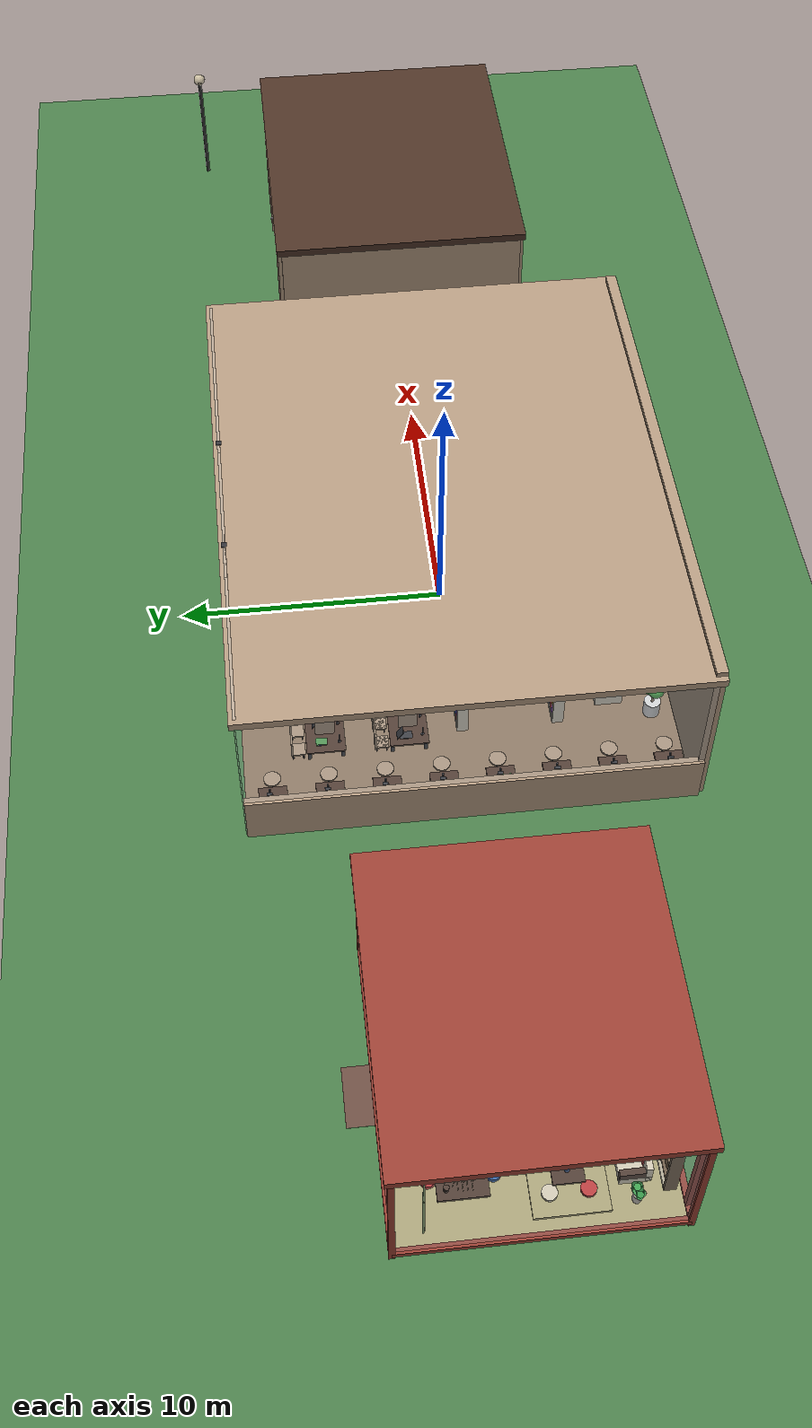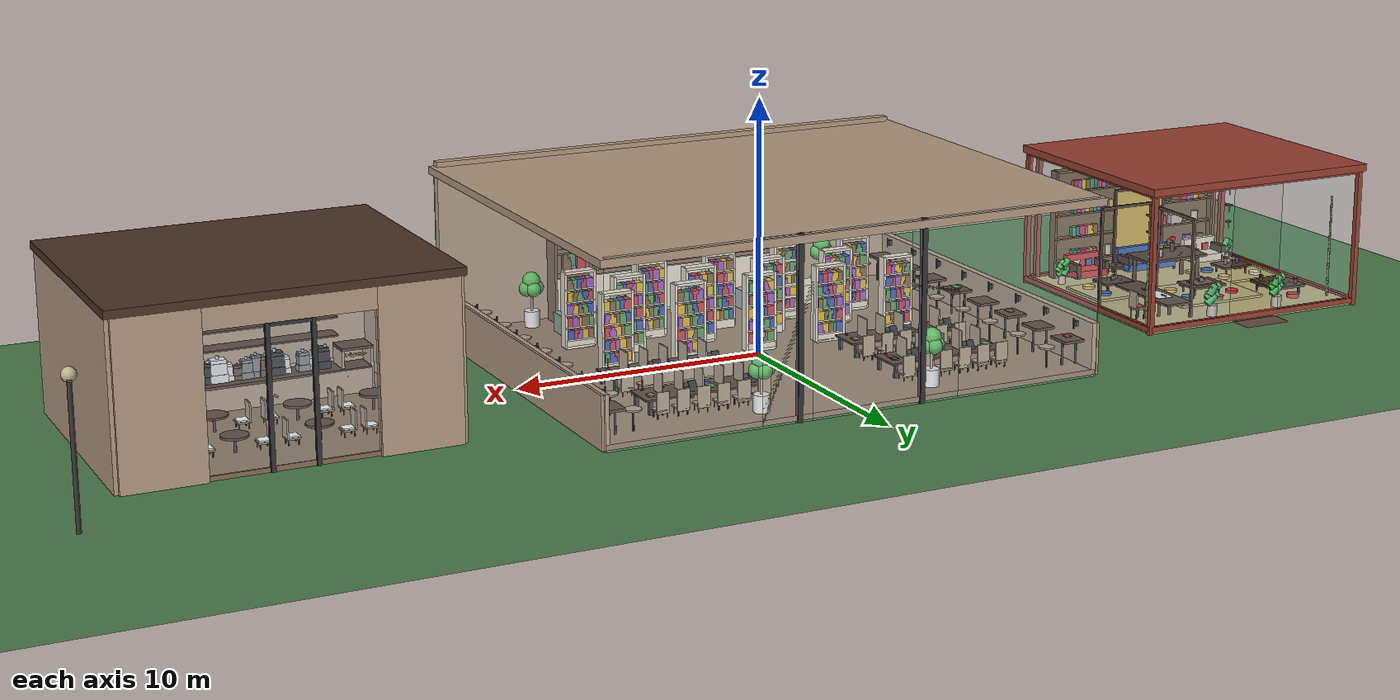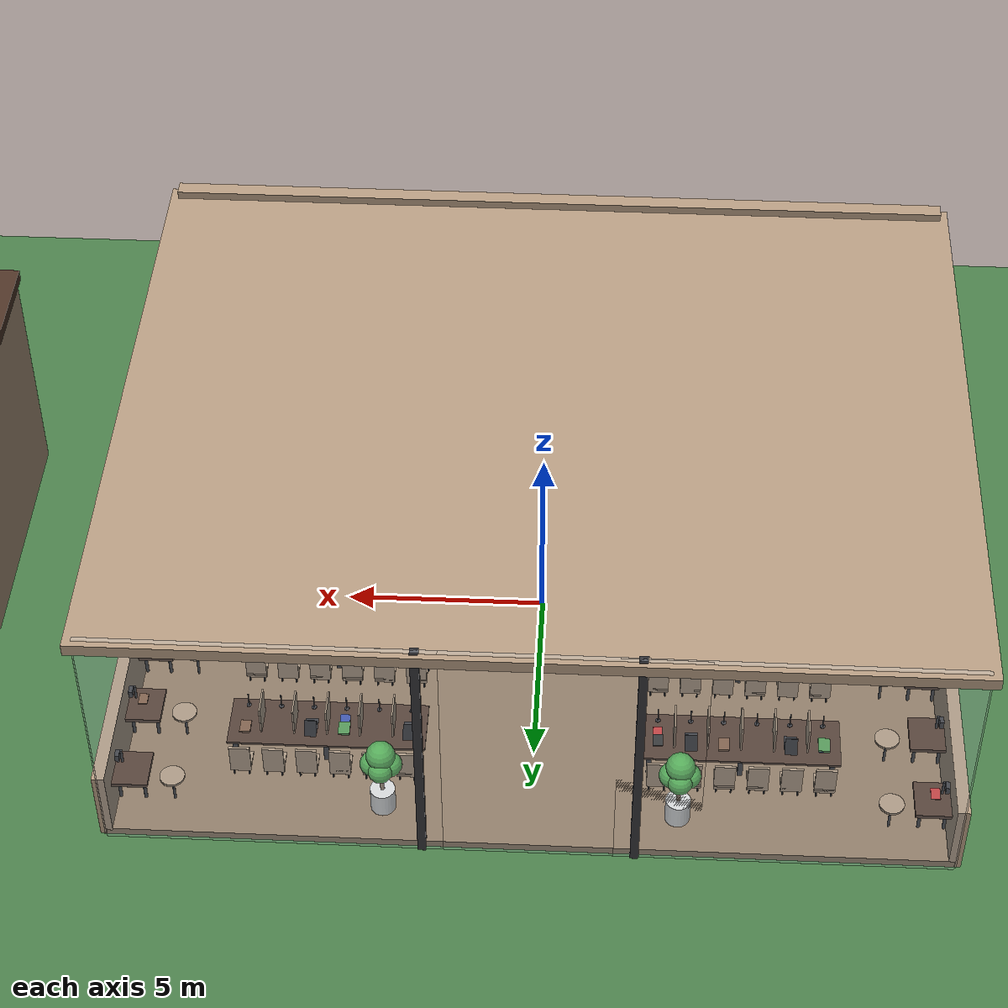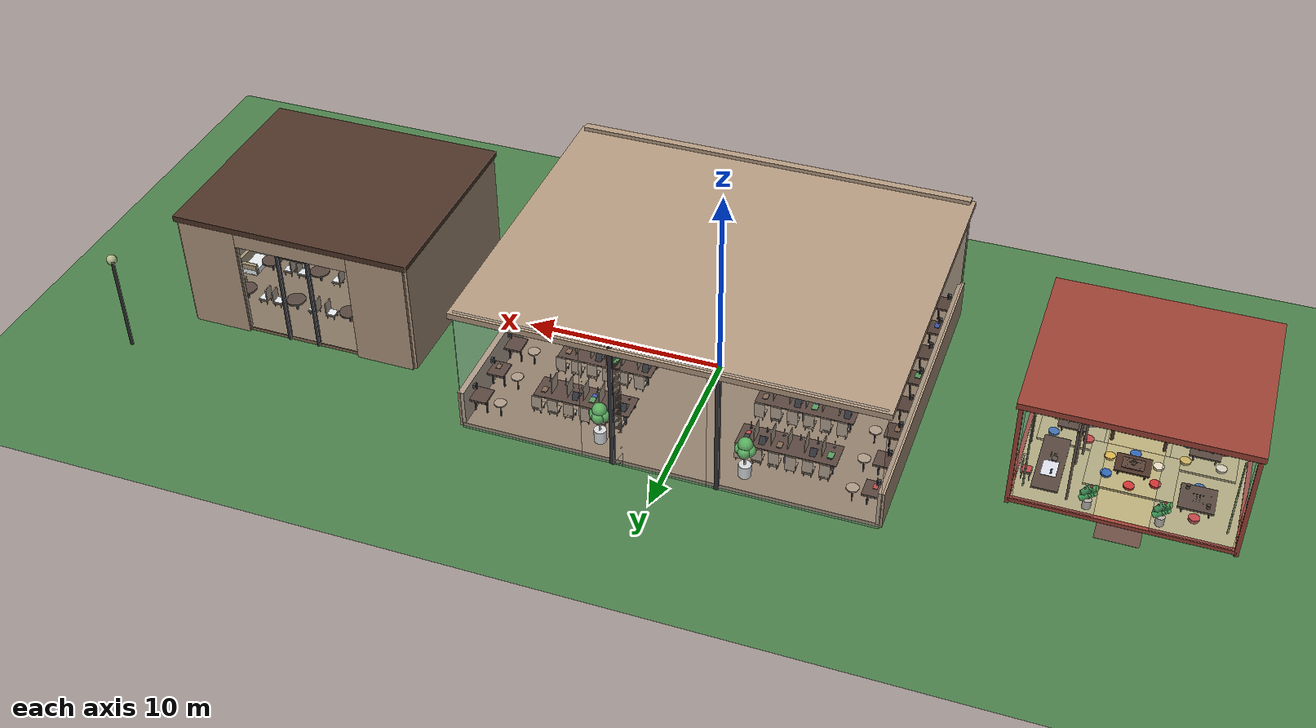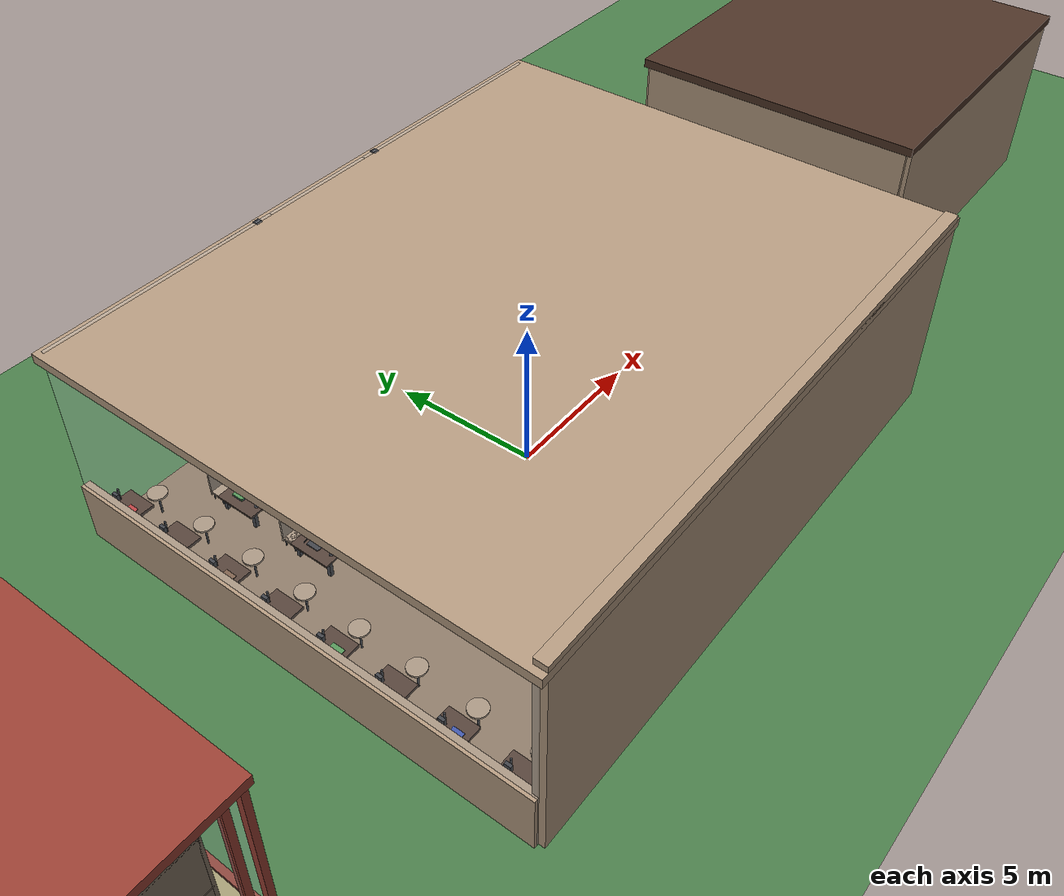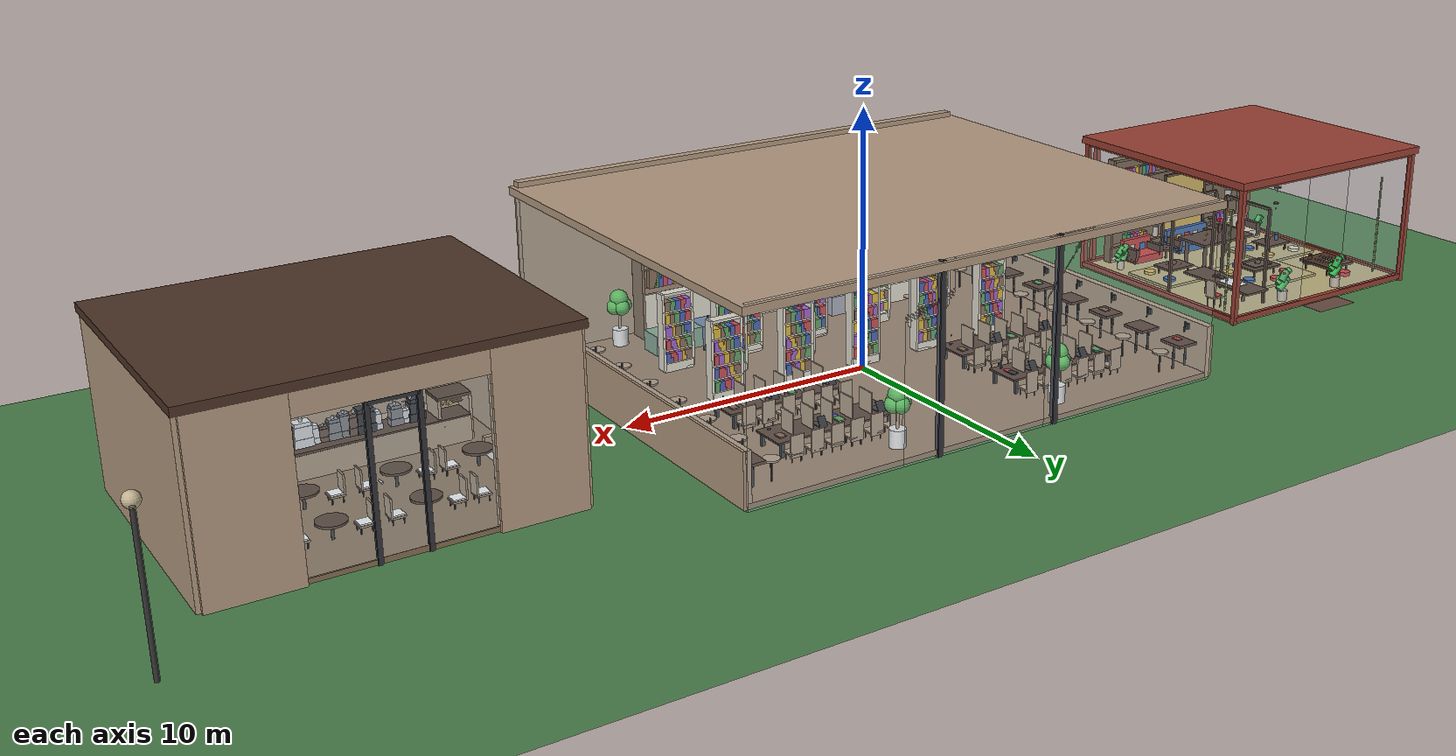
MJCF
<mujoco model="city">
  <!-- ========== 编译器设置 ========== -->
  <!-- angle="degree"：使用角度制而非弧度制 -->
  <!-- coordinate="local"：使用局部坐标系 -->
  <!-- inertiafromgeom="true"：从几何体自动计算惯性 -->
  <compiler angle="degree" coordinate="local" inertiafromgeom="true"/>

  <!-- ========== 物理选项 ========== -->
  <!-- timestep="0.005"：时间步长为0.005秒，用于物理模拟精度 -->
  <!-- gravity="0 0 -9.81"：重力加速度，Z轴向下9.81m/s² -->
  <!-- iterations="50"：每次时间步长的迭代次数 -->
  <!-- solver="Newton"：使用牛顿法求解器 -->
  <!-- tolerance="1e-10"：求解器容差 -->
  <option timestep="0.005" gravity="0 0 -9.81" iterations="50" solver="Newton" tolerance="1e-10">
    <!-- contact="enable"：启用碰撞检测 -->
    <!-- gravity="enable"：启用重力 -->
    <flag contact="enable" gravity="enable"/>
  </option>

  <!-- ========== 默认设置 ========== -->
  <!-- 为所有几何体、关节和电机设置默认参数 -->
  <default>
    <!-- 几何体默认设置 -->
    <!-- conaffinity="1"：碰撞亲和性，控制哪些几何体可以相互碰撞 -->
    <!-- condim="3"：接触维度，3表示3D接触 -->
    <!-- friction="1 0.5 0.005"：摩擦系数（滑动、扭转、滚动） -->
    <!-- solimp="0.9 0.95 0.001"：阻抗参数（阻尼、弹性、边界） -->
    <!-- solref="0.02 1"：求解器参考参数（时间常数、阻尼比） -->
    <geom conaffinity="1" condim="3" friction="1 0.5 0.005" solimp="0.9 0.95 0.001" solref="0.02 1"/>

    <!-- 关节默认设置 -->
    <!-- damping="0.5"：关节阻尼系数 -->
    <!-- armature="0.01"：关节惯性 -->
    <joint damping="0.5" armature="0.01"/>

    <!-- 电机默认设置 -->
    <!-- ctrlrange="-1 1"：控制范围从-1到1 -->
    <!-- ctrllimited="true"：启用控制限制 -->
    <motor ctrlrange="-1 1" ctrllimited="true"/>
  </default>

  <!-- ========== 视觉设置 ========== -->
  <!-- 控制渲染和视觉效果的相关参数 -->
  <visual>
    <!-- 环境映射设置 -->
    <!-- force="0.1"：环境光强度 -->
    <!-- zfar="100"：最大可视距离 -->
    <map force="0.1" zfar="100"/>

    <!-- 雾效设置 -->
    <!-- haze="0.05 0.08 0.12 1"：雾效颜色和透明度（RGB+Alpha） -->
    <rgba haze="0.05 0.08 0.12 1"/>

    <!-- 渲染质量设置 -->
    <!-- shadowsize="4096"：阴影贴图分辨率 -->
    <quality shadowsize="4096"/>

    <!-- 全局渲染设置 -->
    <!-- offwidth="1280" offheight="720"：离屏渲染分辨率（1280x720） -->
    <global offwidth="1280" offheight="720"/>
  </visual>

<asset>
    <!-- ========== 木地板材质 ========== -->
    <!-- 木地板纹理：使用内置棋盘格纹理模拟木地板效果 -->
    <!-- type="2d"：2D纹理 -->
    <!-- builtin="checker"：使用内置棋盘格纹理 -->
    <!-- rgb1="0.55 0.45 0.35"：第一种颜色（浅棕色） -->
    <!-- rgb2="0.5 0.4 0.3"：第二种颜色（深棕色） -->
    <!-- width="512" height="512"：纹理分辨率 -->
    <texture name="wood_floor" type="2d" builtin="checker" rgb1="0.55 0.45 0.35" rgb2="0.5 0.4 0.3" width="512" height="512"/>

    <!-- 木地板材质：应用木地板纹理并设置材质属性 -->
    <!-- texture="wood_floor"：使用上面定义的木地板纹理 -->
    <!-- texrepeat="10 10"：纹理重复次数（10x10） -->
    <!-- specular="0.3"：镜面反射强度 -->
    <!-- shininess="0.3"：光泽度 -->
    <!-- reflectance="0.1"：反射率 -->
    <material name="wood_floor_mat" texture="wood_floor" texrepeat="10 10" specular="0.3" shininess="0.3" reflectance="0.1"/>

    <!-- ========== 书馆木地板材质 ========== -->
    <!-- 木地板纹理：使用内置棋盘格纹理模拟书店木地板效果 -->
    <!-- type="2d"：2D纹理 -->
    <!-- builtin="checker"：使用内置棋盘格纹理 -->
    <!-- rgb1="0.6 0.5 0.4"：浅棕色木纹颜色 -->
    <!-- rgb2="0.55 0.45 0.35"：深棕色木纹颜色，形成对比 -->
    <!-- width="512" height="512"：纹理分辨率512x512像素 -->
    <texture name="wood_floor_2" type="2d" builtin="checker" rgb1="0.6 0.5 0.4" rgb2="0.55 0.45 0.35" width="512" height="512" />

    <!-- 木地板材质：应用木地板纹理并设置材质属性 -->
    <!-- texture="wood_floor_2"：使用上面定义的木地板纹理 -->
    <!-- texrepeat="15 15"：纹理重复15x15次，形成细密的木纹效果 -->
    <!-- specular="0.4"：中等镜面反射，模拟木地板的光泽 -->
    <!-- shininess="0.4"：中等光泽度 -->
    <!-- reflectance="0.15"：中等反射率 -->
    <material name="wood_floor_2_mat" texture="wood_floor_2" texrepeat="15 15" specular="0.4" shininess="0.4" reflectance="0.15" />

<!-- ========== 木地板材质 ========== -->
    <!-- 木地板纹理：使用内置棋盘格纹理模拟传统木地板效果 -->
    <!-- type="2d"：2D纹理 -->
    <!-- builtin="checker"：使用内置棋盘格纹理 -->
    <!-- rgb1="0.55 0.45 0.35"：浅棕色木纹颜色 -->
    <!-- rgb2="0.5 0.4 0.3"：深棕色木纹颜色，形成对比 -->
    <!-- width="512" height="512"：纹理分辨率512x512像素 -->
    <texture name="teahouse_wood_floor" type="2d" builtin="checker" rgb1="0.55 0.45 0.35" rgb2="0.5 0.4 0.3" width="512" height="512"/>

    <!-- 木地板材质：应用木地板纹理并设置材质属性 -->
    <!-- texture="teahouse_wood_floor"：使用上面定义的木地板纹理 -->
    <!-- texrepeat="10 10"：纹理重复10x10次，形成细密的木纹效果 -->
    <!-- specular="0.3"：中等镜面反射，模拟木地板的光泽 -->
    <!-- shininess="0.3"：中等光泽度 -->
    <!-- reflectance="0.1"：低反射率 -->
    <material name="teahouse_wood_floor_mat" texture="teahouse_wood_floor" texrepeat="10 10" specular="0.3" shininess="0.3" reflectance="0.1"/>

    <!-- ========== 榻榻米材质 ========== -->
    <!-- 榻榻米纹理：模拟传统日式榻榻米地板效果 -->
    <!-- type="2d"：2D纹理 -->
    <!-- builtin="checker"：使用内置棋盘格纹理模拟榻榻米编织纹理 -->
    <!-- rgb1="0.75 0.7 0.5"：浅米色榻榻米颜色 -->
    <!-- rgb2="0.7 0.65 0.45"：稍深的米色，形成编织纹理 -->
    <!-- width="512" height="512"：纹理分辨率512x512像素 -->
    <texture name="teahouse_tatami" type="2d" builtin="checker" rgb1="0.75 0.7 0.5" rgb2="0.7 0.65 0.45" width="512" height="512"/>

    <!-- 榻榻米材质：应用榻榻米纹理并设置材质属性 -->
    <!-- texture="teahouse_tatami"：使用上面定义的榻榻米纹理 -->
    <!-- texrepeat="8 8"：纹理重复8x8次，形成合适的榻榻米尺寸 -->
    <!-- specular="0.1"：低镜面反射，模拟榻榻米的粗糙表面 -->
    <!-- shininess="0.1"：低光泽度 -->
    <!-- reflectance="0"：无反射 -->
    <material name="teahouse_tatami_mat" texture="teahouse_tatami" texrepeat="8 8" specular="0.1" shininess="0.1" reflectance="0"/>

    <!-- 深色榻榻米纹理：用于棋盘等特殊区域 -->
    <!-- rgb1="0.6 0.55 0.35"：深米色榻榻米颜色 -->
    <!-- rgb2="0.55 0.5 0.3"：更深的米色，形成对比 -->
    <!-- width="512" height="512"：纹理分辨率512x512像素 -->
    <texture name="teahouse_tatami_dark" type="2d" builtin="checker" rgb1="0.6 0.55 0.35" rgb2="0.55 0.5 0.3" width="512" height="512"/>

    <!-- 深色榻榻米材质：用于棋盘等装饰性区域 -->
    <!-- texture="teahouse_tatami_dark"：使用深色榻榻米纹理 -->
    <!-- texrepeat="8 8"：纹理重复8x8次 -->
    <!-- specular="0.05"：极低镜面反射 -->
    <!-- shininess="0.05"：极低光泽度 -->
    <!-- reflectance="0"：无反射 -->
    <material name="teahouse_tatami_mat_dark" texture="teahouse_tatami_dark" texrepeat="8 8" specular="0.05" shininess="0.05" reflectance="0"/>

    <!-- ========== 玻璃材质 ========== -->
    <!-- 高透明玻璃材质：用于窗户等透明玻璃 -->
    <!-- rgba="0.8 0.9 0.95 0.15"：玻璃颜色（浅蓝绿色）和透明度（15%） -->
    <!-- specular="1"：高镜面反射，模拟玻璃表面 -->
    <!-- shininess="1"：高光泽度 -->
    <!-- reflectance="0.7"：高反射率 -->
    <material name="glass_clear" rgba="0.8 0.9 0.95 0.15" specular="1" shininess="1" reflectance="0.7"/>

    <!-- 半透明玻璃门材质：用于玻璃门，比窗户稍不透明 -->
    <!-- rgba="0.75 0.85 0.9 0.25"：玻璃颜色和透明度（25%） -->
    <!-- specular="1"：高镜面反射 -->
    <!-- shininess="1"：高光泽度 -->
    <!-- reflectance="0.6"：较高反射率 -->
    <material name="glass_door" rgba="0.75 0.85 0.9 0.25" specular="1" shininess="1" reflectance="0.6"/>

   <!-- ========== 书店玻璃材质 ========== -->
    <!-- 透明玻璃材质：用于书店玻璃墙和窗户 -->
    <!-- rgba="0.85 0.92 0.97 0.12"：玻璃颜色（浅蓝绿色）和透明度（12%） -->
    <!-- specular="1"：高镜面反射，模拟玻璃表面 -->
    <!-- shininess="1"：高光泽度 -->
    <!-- reflectance="0.8"：高反射率 -->
    <material name="glass_clear_2" rgba="0.85 0.92 0.97 0.12" specular="1" shininess="1" reflectance="0.8" />

    <!-- 半透明玻璃材质：用于玻璃装饰元素 -->
    <!-- rgba="0.75 0.85 0.9 0.2"：玻璃颜色和透明度（20%） -->
    <!-- specular="1"：高镜面反射 -->
    <!-- shininess="1"：高光泽度 -->
    <!-- reflectance="0.7"：较高反射率 -->
    <material name="glass_tinted_2" rgba="0.75 0.85 0.9 0.2" specular="1" shininess="1" reflectance="0.7" />

<!-- 高透明玻璃材质：用于茶室窗户等透明玻璃结构 -->
    <!-- rgba="0.8 0.9 0.95 0.15"：浅蓝绿色玻璃颜色，透明度15% -->
    <!-- specular="1"：最高镜面反射，模拟玻璃表面的高光 -->
    <!-- shininess="1"：最高光泽度 -->
    <!-- reflectance="0.7"：高反射率，模拟玻璃的反射特性 -->
    <material name="teahouse_glass_clear" rgba="0.8 0.9 0.95 0.15" specular="1" shininess="1" reflectance="0.7"/>

    <!-- 半透明玻璃门材质：用于茶室玻璃门，比窗户稍不透明 -->
    <!-- rgba="0.75 0.85 0.9 0.25"：浅蓝灰色玻璃颜色，透明度25% -->
    <!-- specular="1"：最高镜面反射 -->
    <!-- shininess="1"：最高光泽度 -->
    <!-- reflectance="0.6"：较高反射率 -->
    <material name="teahouse_glass_door" rgba="0.75 0.85 0.9 0.25" specular="1" shininess="1" reflectance="0.6"/>

    <!-- ========== 金属材质 ========== -->
    <!-- 深色金属材质：用于茶室门框、结构件等深色金属部件 -->
    <!-- rgba="0.2 0.2 0.22 1"：深灰色金属颜色，接近黑色 -->
    <!-- specular="0.9"：高镜面反射，模拟金属表面的光泽 -->
    <!-- shininess="0.8"：高光泽度 -->
    <!-- reflectance="0.4"：中等反射率 -->
    <material name="teahouse_metal_dark" rgba="0.2 0.2 0.22 1" specular="0.9" shininess="0.8" reflectance="0.4"/>

    <!-- 铬金属材质：用于茶具、装饰品等亮面金属部件 -->
    <!-- rgba="0.8 0.8 0.82 1"：亮银色金属颜色 -->
    <!-- specular="1"：最高镜面反射 -->
    <!-- shininess="0.9"：极高光泽度 -->
    <!-- reflectance="0.6"：高反射率 -->
    <material name="teahouse_metal_chrome" rgba="0.8 0.8 0.82 1" specular="1" shininess="0.9" reflectance="0.6"/>

    <!-- ========== 金属材质 ========== -->
    <!-- 深色金属材质：用于门框、桌腿等结构件 -->
    <!-- rgba="0.2 0.2 0.22 1"：深灰色金属颜色 -->
    <!-- specular="0.9"：高镜面反射 -->
    <!-- shininess="0.8"：高光泽度 -->
    <!-- reflectance="0.4"：中等反射率 -->
    <material name="metal_dark" rgba="0.2 0.2 0.22 1" specular="0.9" shininess="0.8" reflectance="0.4"/>

    <!-- 铬金属材质：用于门把手、咖啡机部件等亮面金属 -->
    <!-- rgba="0.8 0.8 0.82 1"：亮银色金属颜色 -->
    <!-- specular="1"：最高镜面反射 -->
    <!-- shininess="0.9"：极高光泽度 -->
    <!-- reflectance="0.6"：高反射率 -->
    <material name="metal_chrome" rgba="0.8 0.8 0.82 1" specular="1" shininess="0.9" reflectance="0.6"/>

    <!-- ==========书店 金属材质 ========== -->
    <!-- 深色金属材质：用于书店门框、灯具支架等深色金属部件 -->
    <!-- rgba="0.2 0.2 0.22 1"：深灰色金属颜色 -->
    <!-- specular="0.9"：高镜面反射 -->
    <!-- shininess="0.8"：高光泽度 -->
    <!-- reflectance="0.4"：中等反射率 -->
    <material name="metal_dark_2" rgba="0.2 0.2 0.22 1" specular="0.9" shininess="0.8" reflectance="0.4" />

    <!-- 铬金属材质：用于书店装饰性金属元素、灯具等亮面金属 -->
    <!-- rgba="0.85 0.85 0.87 1"：亮银色金属颜色 -->
    <!-- specular="1"：最高镜面反射 -->
    <!-- shininess="0.9"：极高光泽度 -->
    <!-- reflectance="0.7"：高反射率 -->
    <material name="metal_chrome_2" rgba="0.85 0.85 0.87 1" specular="1" shininess="0.9" reflectance="0.7" />

    <!-- ========== 咖啡机材质 ========== -->
    <!-- 灰色咖啡机材质：中性色调的咖啡机外壳 -->
    <!-- rgba="0.5 0.5 0.52 1"：中灰色金属颜色 -->
    <!-- specular="0.7"：中等镜面反射 -->
    <!-- shininess="0.6"：中等光泽度 -->
    <!-- reflectance="0.3"：中等反射率 -->
    <material name="machine_gray" rgba="0.5 0.5 0.52 1" specular="0.7" shininess="0.6" reflectance="0.3"/>

    <!-- 白色咖啡机材质：现代风格的白色咖啡机 -->
    <!-- rgba="0.9 0.9 0.92 1"：亮白色金属颜色 -->
    <!-- specular="0.8"：较高镜面反射 -->
    <!-- shininess="0.7"：较高光泽度 -->
    <!-- reflectance="0.4"：中等反射率 -->
    <material name="machine_white" rgba="0.9 0.9 0.92 1" specular="0.8" shininess="0.7" reflectance="0.4"/>

    <!-- 黑色咖啡机材质：专业风格的黑色咖啡机 -->
    <!-- rgba="0.15 0.15 0.16 1"：深黑色金属颜色 -->
    <!-- specular="0.8"：较高镜面反射 -->
    <!-- shininess="0.7"：较高光泽度 -->
    <!-- reflectance="0.35"：中等反射率 -->
    <material name="machine_black" rgba="0.15 0.15 0.16 1" specular="0.8" shininess="0.7" reflectance="0.35"/>

    <!-- 棕色咖啡机材质：复古风格的棕色咖啡机 -->
    <!-- rgba="0.4 0.3 0.25 1"：深棕色金属颜色 -->
    <!-- specular="0.6"：中等镜面反射 -->
    <!-- shininess="0.5"：中等光泽度 -->
    <!-- reflectance="0.2"：较低反射率 -->
    <material name="machine_brown" rgba="0.4 0.3 0.25 1" specular="0.6" shininess="0.5" reflectance="0.2"/>

    <!-- ========== 木材材质 ========== -->
    <!-- 深色木材材质：用于咖啡馆书架、书桌、吧台台面等深色木质结构 -->
    <!-- rgba="0.3 0.2 0.15 1"：深棕色木材颜色，适合营造温馨的咖啡馆氛围 -->
    <!-- specular="0.2"：低镜面反射，模拟木材的自然光泽 -->
    <!-- shininess="0.2"：低光泽度 -->
    <!-- reflectance="0"：无反射 -->
    <material name="wood_dark" rgba="0.3 0.2 0.15 1" specular="0.2" shininess="0.2" reflectance="0"/>

    <!-- 浅色木材材质：用于咖啡馆墙面、书架侧面、吧台侧面等浅色木质结构 -->
    <!-- rgba="0.7 0.6 0.5 1"：浅棕色木材颜色，营造明亮的咖啡馆环境 -->
    <!-- specular="0.3"：中等镜面反射 -->
    <!-- shininess="0.3"：中等光泽度 -->
    <!-- reflectance="0.05"：极低反射率 -->
    <material name="wood_light" rgba="0.7 0.6 0.5 1" specular="0.3" shininess="0.3" reflectance="0.05"/>

    <!-- 书架木材材质：专门用于书店书架主体结构 -->
    <!-- rgba="0.5 0.4 0.3 1"：中棕色木材颜色，适合营造温馨的书店氛围 -->
    <!-- specular="0.25"：中等镜面反射 -->
    <!-- shininess="0.25"：中等光泽度 -->
    <!-- reflectance="0.02"：极低反射率 -->
    <material name="wood_shelf" rgba="0.5 0.4 0.3 1" specular="0.25" shininess="0.25" reflectance="0.02" />

    <!-- 米色木材材质：用于书店书架底部、装饰元素等浅色木质部件 -->
    <!-- rgba="0.92 0.88 0.8 1"：温暖的米色木材颜色 -->
    <!-- specular="0.25"：中等镜面反射 -->
    <!-- shininess="0.25"：中等光泽度 -->
    <!-- reflectance="0.02"：极低反射率 -->
    <material name="wood_beige" rgba="0.92 0.88 0.8 1" specular="0.25" shininess="0.25" reflectance="0.02" />

    <!-- 圆形木材材质：用于咖啡馆沙发扶手等圆形木质部件 -->
    <!-- rgba="0.65 0.55 0.4 1"：中棕色木材颜色 -->
    <!-- specular="0.25"：中等镜面反射 -->
    <!-- shininess="0.25"：中等光泽度 -->
    <!-- reflectance="0.03"：极低反射率 -->
    <material name="wood_round" rgba="0.65 0.55 0.4 1" specular="0.25" shininess="0.25" reflectance="0.03"/>

<!-- 深色木材材质：用于茶室深色木质结构，如梁柱等 -->
    <!-- rgba="0.3 0.2 0.15 1"：深棕色木材颜色，传统茶室常用色调 -->
    <!-- specular="0.2"：低镜面反射，模拟木材的自然光泽 -->
    <!-- shininess="0.2"：低光泽度 -->
    <!-- reflectance="0"：无反射 -->
    <material name="teahouse_wood_dark" rgba="0.3 0.2 0.15 1" specular="0.2" shininess="0.2" reflectance="0"/>

    <!-- 浅色木材材质：用于茶室浅色木质结构，如墙面、家具等 -->
    <!-- rgba="0.7 0.6 0.5 1"：浅棕色木材颜色，明亮温暖的色调 -->
    <!-- specular="0.3"：中等镜面反射 -->
    <!-- shininess="0.3"：中等光泽度 -->
    <!-- reflectance="0.05"：极低反射率 -->
    <material name="teahouse_wood_light" rgba="0.7 0.6 0.5 1" specular="0.3" shininess="0.3" reflectance="0.05"/>

    <!-- 红色木材材质：用于茶室红色木质结构，如门框、装饰等 -->
    <!-- rgba="0.6 0.25 0.2 1"：红棕色木材颜色，传统日式建筑常用色调 -->
    <!-- specular="0.3"：中等镜面反射 -->
    <!-- shininess="0.3"：中等光泽度 -->
    <!-- reflectance="0.05"：极低反射率 -->
    <material name="teahouse_wood_red" rgba="0.6 0.25 0.2 1" specular="0.3" shininess="0.3" reflectance="0.05"/>

    <!-- 书架木材材质：用于书架结构 -->
    <!-- rgba="0.45 0.35 0.25 1"：深棕色木材颜色，适合书架 -->
    <!-- specular="0.3"：中等镜面反射 -->
    <!-- shininess="0.3"：中等光泽度 -->
    <!-- reflectance="0.05"：极低反射率 -->
    <material name="teahouse_wood_shelf" rgba="0.45 0.35 0.25 1" specular="0.3" shininess="0.3" reflectance="0.05"/>

    <!-- 米白色木材材质：用于书架底部 -->
    <!-- rgba="0.75 0.7 0.6 1"：米白色木材颜色，与书架主体形成对比 -->
    <!-- specular="0.3"：中等镜面反射 -->
    <!-- shininess="0.3"：中等光泽度 -->
    <!-- reflectance="0.05"：极低反射率 -->
    <material name="teahouse_wood_beige" rgba="0.75 0.7 0.6 1" specular="0.3" shininess="0.3" reflectance="0.05"/>

    <!-- 书籍材质 -->
    <material name="teahouse_book_red" rgba="0.8 0.2 0.2 1" specular="0.3" shininess="0.2" />
    <material name="teahouse_book_blue" rgba="0.2 0.4 0.7 1" specular="0.3" shininess="0.2" />
    <material name="teahouse_book_green" rgba="0.2 0.6 0.3 1" specular="0.3" shininess="0.2" />
    <material name="teahouse_book_brown" rgba="0.5 0.35 0.2 1" specular="0.3" shininess="0.2" />
    <material name="teahouse_book_yellow" rgba="0.9 0.7 0.1 1" specular="0.3" shininess="0.2" />
    <material name="teahouse_book_purple" rgba="0.6 0.3 0.8 1" specular="0.3" shininess="0.2" />

    <!-- 竹材质：用于茶室竹制装饰和结构 -->
    <!-- rgba="0.55 0.65 0.4 1"：竹绿色，模拟竹子的自然颜色 -->
    <!-- specular="0.2"：低镜面反射 -->
    <!-- shininess="0.2"：低光泽度 -->
    <!-- reflectance="0.05"：极低反射率 -->
    <material name="teahouse_bamboo" rgba="0.55 0.65 0.4 1" specular="0.2" shininess="0.2" reflectance="0.05"/>

    <!-- ========== 布料材质 ========== -->

    <!-- 蓝色沙发材质：用于书店休息区蓝色沙发 -->
    <!-- rgba="0.4 0.5 0.65 1"：深蓝色，营造宁静的阅读氛围 -->
    <!-- specular="0.1"：低镜面反射 -->
    <!-- shininess="0.1"：低光泽度 -->
    <material name="sofa_blue" rgba="0.4 0.5 0.65 1" specular="0.1" shininess="0.1" />

<!-- 绿色沙发材质：用于书店休息区绿色沙发 -->
    <!-- rgba="0.5 0.65 0.55 1"：舒缓的绿色，增添自然感 -->
    <!-- specular="0.1"：低镜面反射 -->
    <!-- shininess="0.1"：低光泽度 -->
    <material name="sofa_green" rgba="0.5 0.65 0.55 1" specular="0.1" shininess="0.1" />

    <!-- 米色布料材质：用于咖啡馆阅读区沙发座垫等中性色调布料 -->
    <!-- rgba="0.9 0.85 0.75 1"：温暖的米色，营造舒适的咖啡馆环境 -->
    <!-- specular="0.1"：低镜面反射 -->
    <!-- shininess="0.1"：低光泽度 -->
    <material name="fabric_beige" rgba="0.9 0.85 0.75 1" specular="0.1" shininess="0.1"/>

    <!-- 米色沙发材质：用于书店休息区米色沙发 -->
    <!-- rgba="0.92 0.88 0.8 1"：温暖的米色，营造舒适的阅读环境 -->
    <!-- specular="0.1"：低镜面反射，模拟布料质感 -->
    <!-- shininess="0.1"：低光泽度 -->
    <material name="sofa_beige" rgba="0.92 0.88 0.8 1" specular="0.1" shininess="0.1" />

    <!-- 浅色布料材质：用于咖啡馆浅色布料元素或阅读区座椅 -->
    <!-- rgba="0.95 0.93 0.9 1"：极浅的米白色，营造明亮整洁的咖啡馆环境 -->
    <!-- specular="0.1"：低镜面反射 -->
    <!-- shininess="0.1"：低光泽度 -->
    <material name="fabric_light" rgba="0.95 0.93 0.9 1" specular="0.1" shininess="0.1"/>

    <!-- 白色布料材质：用于咖啡馆纯白色布料元素或阅读区座椅 -->
    <!-- rgba="1 1 1 1"：纯白色，营造干净清爽的咖啡馆环境 -->
    <!-- specular="0.1"：低镜面反射 -->
    <!-- shininess="0.1"：低光泽度 -->
    <material name="fabric_white" rgba="1 1 1 1" specular="0.1" shininess="0.1"/>

    <!-- 白色坐垫材质：用于书店沙发、椅子的白色坐垫 -->
    <!-- rgba="0.98 0.97 0.95 1"：纯白色，营造干净整洁的阅读环境 -->
    <!-- specular="0.15"：低镜面反射 -->
    <!-- shininess="0.1"：低光泽度 -->
    <material name="cushion_white" rgba="0.98 0.97 0.95 1" specular="0.15" shininess="0.1" />

    <!-- 灰色沙发材质：用于书店休息区灰色沙发 -->
    <!-- rgba="0.65 0.65 0.7 1"：中性灰色，适合现代风格书店 -->
    <!-- specular="0.1"：低镜面反射 -->
    <!-- shininess="0.1"：低光泽度 -->
    <material name="sofa_grey" rgba="0.65 0.65 0.7 1" specular="0.1" shininess="0.1" />

<!-- 红色布料材质：用于茶室装饰性布料，如坐垫、挂帘等 -->
    <!-- rgba="0.8 0.2 0.2 1"：鲜艳的红色，传统茶室装饰常用颜色 -->
    <!-- specular="0.1"：低镜面反射，模拟布料的粗糙表面 -->
    <!-- shininess="0.1"：低光泽度 -->
    <material name="teahouse_fabric_red" rgba="0.8 0.2 0.2 1" specular="0.1" shininess="0.1"/>

    <!-- 蓝色布料材质：用于茶室装饰性布料 -->
    <!-- rgba="0.2 0.4 0.7 1"：深蓝色，沉稳的色调 -->
    <!-- specular="0.1"：低镜面反射 -->
    <!-- shininess="0.1"：低光泽度 -->
    <material name="teahouse_fabric_blue" rgba="0.2 0.4 0.7 1" specular="0.1" shininess="0.1"/>

    <!-- 绿色布料材质：用于茶室装饰性布料 -->
    <!-- rgba="0.2 0.6 0.3 1"：深绿色，自然和谐的色调 -->
    <!-- specular="0.1"：低镜面反射 -->
    <!-- shininess="0.1"：低光泽度 -->
    <material name="teahouse_fabric_green" rgba="0.2 0.6 0.3 1" specular="0.1" shininess="0.1"/>

    <!-- 橙色布料材质：用于茶室装饰性布料 -->
    <!-- rgba="0.9 0.5 0.2 1"：温暖的橙色，明亮的装饰色调 -->
    <!-- specular="0.1"：低镜面反射 -->
    <!-- shininess="0.1"：低光泽度 -->
    <material name="teahouse_fabric_orange" rgba="0.9 0.5 0.2 1" specular="0.1" shininess="0.1"/>

    <!-- 紫色布料材质：用于茶室装饰性布料 -->
    <!-- rgba="0.6 0.3 0.7 1"：深紫色，高雅的装饰色调 -->
    <!-- specular="0.1"：低镜面反射 -->
    <!-- shininess="0.1"：低光泽度 -->
    <material name="teahouse_fabric_purple" rgba="0.6 0.3 0.7 1" specular="0.1" shininess="0.1"/>

<!-- ========== 纸质材料 ========== -->
    <!-- 白色纸质材料：用于茶室屏风、灯笼等纸质装饰 -->
    <!-- rgba="0.95 0.93 0.88 0.8"：米白色纸张颜色，透明度80% -->
    <!-- specular="0.1"：低镜面反射，模拟纸张的粗糙表面 -->
    <!-- shininess="0.1"：低光泽度 -->
    <material name="paper_white" rgba="0.95 0.93 0.88 0.8" specular="0.1" shininess="0.1"/>

    <!-- 红色纸质材料：用于茶室红色装饰性纸质元素 -->
    <!-- rgba="0.9 0.2 0.15 0.7"：鲜艳的红色，透明度70% -->
    <!-- specular="0.1"：低镜面反射 -->
    <!-- shininess="0.1"：低光泽度 -->
    <material name="paper_red" rgba="0.9 0.2 0.15 0.7" specular="0.1" shininess="0.1"/>

<!-- ========== 草地材质 ========== -->
    <!-- 草地纹理：使用棋盘格纹理模拟书店外草地效果 -->
    <!-- type="2d"：2D纹理 -->
    <!-- builtin="checker"：使用内置棋盘格纹理 -->
    <!-- rgb1="0.3 0.55 0.3"：亮绿色草地颜色 -->
    <!-- rgb2="0.28 0.5 0.28"：深绿色草地颜色，形成对比 -->
    <!-- width="512" height="512"：纹理分辨率512x512像素 -->
    <texture name="grass" type="2d" builtin="checker" rgb1="0.3 0.55 0.3" rgb2="0.28 0.5 0.28" width="512" height="512" />

   <!-- 草地材质：应用草地纹理并设置材质属性 -->
    <!-- texture="grass"：使用上面定义的草地纹理 -->
    <!-- texrepeat="50 50"：纹理重复50x50次，形成细密的草地纹理 -->
    <!-- specular="0.1"：极低镜面反射，模拟草地粗糙表面 -->
    <!-- shininess="0.05"：极低光泽度 -->
    <!-- reflectance="0"：无反射 -->
    <material name="grass_mat" texture="grass" texrepeat="50 50" specular="0.1" shininess="0.05" reflectance="0" />

<!-- ========== 草地材质 ========== -->
    <!-- 草地纹理：使用棋盘格纹理模拟茶室外围的草地效果 -->
    <!-- type="2d"：2D纹理 -->
    <!-- builtin="checker"：使用内置棋盘格纹理 -->
    <!-- rgb1="0.3 0.5 0.3"：深绿色草地颜色 -->
    <!-- rgb2="0.28 0.48 0.28"：稍深的绿色，形成草地纹理 -->
    <!-- width="512" height="512"：纹理分辨率512x512像素 -->
    <texture name="teahouse_grass" type="2d" builtin="checker" rgb1="0.3 0.5 0.3" rgb2="0.28 0.48 0.28" width="512" height="512"/>

    <!-- 草地材质：应用草地纹理并设置材质属性 -->
    <!-- texture="teahouse_grass"：使用上面定义的草地纹理 -->
    <!-- texrepeat="40 40"：纹理重复40x40次，形成细密的草地纹理 -->
    <!-- specular="0.1"：极低镜面反射，模拟草地的粗糙表面 -->
    <!-- shininess="0.05"：极低光泽度 -->
    <!-- reflectance="0"：无反射 -->
    <material name="teahouse_grass_mat" texture="teahouse_grass" texrepeat="40 40" specular="0.1" shininess="0.05" reflectance="0"/>

    <!-- ========== 天空盒纹理 ========== -->
    <!-- 天空盒纹理：用于书店环境背景的天空效果 -->
    <!-- type="skybox"：天空盒类型纹理 -->
    <!-- builtin="gradient"：内置渐变纹理 -->
    <!-- rgb1="0.65 0.8 0.95"：天空顶部颜色（浅蓝色） -->
    <!-- rgb2="0.35 0.55 0.75"：天空底部颜色（深蓝色） -->
    <!-- width="512" height="512"：纹理分辨率512x512像素 -->
    <texture name="skybox" type="skybox" builtin="gradient" rgb1="0.65 0.8 0.95" rgb2="0.35 0.55 0.75" width="512" height="512" />

    <!-- ========== 书籍材质 ========== -->
    <!-- 红色书籍材质：用于书店红色封面书籍 -->
    <!-- rgba="0.8 0.2 0.2 1"：鲜艳的红色封面 -->
    <!-- specular="0.3"：中等镜面反射，模拟书籍封面的光泽 -->
    <!-- shininess="0.2"：低光泽度 -->
    <material name="book_red" rgba="0.8 0.2 0.2 1" specular="0.3" shininess="0.2" />

    <!-- 蓝色书籍材质：用于书店蓝色封面书籍 -->
    <!-- rgba="0.2 0.3 0.7 1"：深蓝色封面 -->
    <!-- specular="0.3"：中等镜面反射 -->
    <!-- shininess="0.2"：低光泽度 -->
    <material name="book_blue" rgba="0.2 0.3 0.7 1" specular="0.3" shininess="0.2" />

    <!-- 绿色书籍材质：用于书店绿色封面书籍 -->
    <!-- rgba="0.3 0.6 0.3 1"：翠绿色封面 -->
    <!-- specular="0.3"：中等镜面反射 -->
    <!-- shininess="0.2"：低光泽度 -->
    <material name="book_green" rgba="0.3 0.6 0.3 1" specular="0.3" shininess="0.2" />

    <!-- 棕色书籍材质：用于书店棕色封面书籍 -->
    <!-- rgba="0.5 0.35 0.25 1"：棕色封面，适合经典文学类书籍 -->
    <!-- specular="0.3"：中等镜面反射 -->
    <!-- shininess="0.2"：低光泽度 -->
    <material name="book_brown" rgba="0.5 0.35 0.25 1" specular="0.3" shininess="0.2" />

    <!-- 黑色书籍材质：用于书店黑色封面书籍 -->
    <!-- rgba="0.15 0.15 0.15 1"：黑色封面，适合专业类书籍 -->
    <!-- specular="0.3"：中等镜面反射 -->
    <!-- shininess="0.2"：低光泽度 -->
    <material name="book_black" rgba="0.15 0.15 0.15 1" specular="0.3" shininess="0.2" />

    <!-- 黄色书籍材质：用于书店黄色封面书籍 -->
    <!-- rgba="0.9 0.7 0.1 1"：明亮的黄色封面 -->
    <!-- specular="0.3"：中等镜面反射 -->
    <!-- shininess="0.2"：低光泽度 -->
    <material name="book_yellow" rgba="0.9 0.7 0.1 1" specular="0.3" shininess="0.2" />

    <!-- 紫色书籍材质：用于书店紫色封面书籍 -->
    <!-- rgba="0.6 0.3 0.8 1"：紫色封面 -->
    <!-- specular="0.3"：中等镜面反射 -->
    <!-- shininess="0.2"：低光泽度 -->
    <material name="book_purple" rgba="0.6 0.3 0.8 1" specular="0.3" shininess="0.2" />

    <!-- ========== 菜单纹理 ========== -->
    <!-- 菜单图片纹理1：从外部文件加载的菜单图片 -->
    <!-- type="2d"：2D纹理 -->
    <!-- file="menu1.png"：菜单图片文件路径 -->
    <texture name="menu_texture_1" type="2d" file="menu1.png"/>

    <!-- 菜单材质1：应用菜单纹理并设置材质属性 -->
    <!-- texture="menu_texture_1"：使用菜单纹理1 -->
    <!-- specular="0.1"：低镜面反射 -->
    <!-- shininess="0.1"：低光泽度 -->
    <material name="menu_mat_1" texture="menu_texture_1" specular="0.1" shininess="0.1"/>

    <!-- 菜单图片纹理2：第二个菜单图片 -->
    <!-- file="menu2.png"：菜单图片文件路径 -->
    <texture name="menu_texture_2" type="2d" file="menu2.png"/>

    <!-- 菜单材质2：应用菜单纹理2 -->
    <!-- texture="menu_texture_2"：使用菜单纹理2 -->
    <!-- specular="0.1"：低镜面反射 -->
    <!-- shininess="0.1"：低光泽度 -->
    <material name="menu_mat_2" texture="menu_texture_2" specular="0.1" shininess="0.1"/>

    <!-- 菜单图片纹理3：第三个菜单图片 -->
    <!-- file="menu3.png"：菜单图片文件路径 -->
    <texture name="menu_texture_3" type="2d" file="menu3.png"/>

    <!-- 菜单材质3：应用菜单纹理3 -->
    <!-- texture="menu_texture_3"：使用菜单纹理3 -->
    <!-- specular="0.1"：低镜面反射 -->
    <!-- shininess="0.1"：低光泽度 -->
    <material name="menu_mat_3" texture="menu_texture_3" specular="0.1" shininess="0.1"/>

        <!-- ========== 装饰材质 ========== -->
<!-- 陶瓷材质：用于茶具、花瓶等陶瓷制品 -->
    <!-- rgba="0.75 0.7 0.65 1"：米白色陶瓷颜色，传统茶具常用色调 -->
    <!-- specular="0.2"：低镜面反射，模拟陶瓷的微光 -->
    <!-- shininess="0.2"：低光泽度 -->
    <!-- reflectance="0.05"：极低反射率 -->
    <material name="teahouse_pottery" rgba="0.75 0.7 0.65 1" specular="0.2" shininess="0.2" reflectance="0.05"/>

    <!-- 米色布料材质：用于茶室中性色调布料 -->
    <!-- rgba="0.9 0.85 0.75 1"：温暖的米色，柔和的装饰色调 -->
    <!-- specular="0.1"：低镜面反射 -->
    <!-- shininess="0.1"：低光泽度 -->
    <material name="teahouse_fabric_beige" rgba="0.9 0.85 0.75 1" specular="0.1" shininess="0.1"/>

    <!-- 金色布料材质：用于茶室装饰性金色布料 -->
    <!-- rgba="0.85 0.7 0.3 1"：金色，高贵的装饰色调 -->
    <!-- specular="0.3"：中等镜面反射 -->
    <!-- shininess="0.2"：低光泽度 -->
    <material name="teahouse_fabric_gold" rgba="0.85 0.7 0.3 1" specular="0.3" shininess="0.2"/>

    <!-- 白色布料材质：用于茶室纯白色布料 -->
    <!-- rgba="1 1 1 1"：纯白色，简洁干净的色调 -->
    <!-- specular="0.1"：低镜面反射 -->
    <!-- shininess="0.1"：低光泽度 -->
    <material name="teahouse_fabric_white" rgba="1 1 1 1" specular="0.1" shininess="0.1"/>

    <!-- 蓝色陶瓷材质：用于书店装饰性陶瓷制品 -->
    <!-- rgba="0.2 0.4 0.6 1"：蓝色陶瓷颜色 -->
    <!-- specular="0.5"：中等镜面反射 -->
    <!-- shininess="0.4"：中等光泽度 -->
    <material name="ceramic_blue" rgba="0.2 0.4 0.6 1" specular="0.5" shininess="0.4" />

    <!-- 红色陶瓷材质：用于书店装饰性陶瓷制品 -->
    <!-- rgba="0.8 0.3 0.3 1"：红色陶瓷颜色 -->
    <!-- specular="0.5"：中等镜面反射 -->
    <!-- shininess="0.4"：中等光泽度 -->
    <material name="ceramic_red" rgba="0.8 0.3 0.3 1" specular="0.5" shininess="0.4" />

    <!-- 白色陶瓷材质：用于书店装饰性陶瓷制品 -->
    <!-- rgba="0.9 0.9 0.9 1"：白色陶瓷颜色 -->
    <!-- specular="0.6"：较高镜面反射 -->
    <!-- shininess="0.5"：中等光泽度 -->
    <material name="ceramic_white" rgba="0.9 0.9 0.9 1" specular="0.6" shininess="0.5" />

    <!-- 金色金属材质：用于书店装饰性金色元素 -->
    <!-- rgba="0.9 0.8 0.3 1"：金色金属颜色 -->
    <!-- specular="0.9"：高镜面反射 -->
    <!-- shininess="0.8"：高光泽度 -->
    <material name="metal_gold" rgba="0.9 0.8 0.3 1" specular="0.9" shininess="0.8" />

    <!-- 银色金属材质：用于书店装饰性银色元素 -->
    <!-- rgba="0.8 0.8 0.8 1"：银色金属颜色 -->
    <!-- specular="0.9"：高镜面反射 -->
    <!-- shininess="0.8"：高光泽度 -->
    <material name="metal_silver" rgba="0.8 0.8 0.8 1" specular="0.9" shininess="0.8" />

     <!-- 植物绿色材质：用于书店装饰性植物 -->
    <!-- rgba="0.3 0.7 0.3 1"：鲜艳的绿色，模拟植物叶子 -->
    <!-- specular="0.2"：低镜面反射 -->
    <!-- shininess="0.1"：低光泽度 -->
    <material name="plant_green" rgba="0.3 0.7 0.3 1" specular="0.2" shininess="0.1" />
  </asset>

<!-- 世界主体 -->
  <worldbody>

 <!-- 主光源（阳光 - 增强） -->
    <light directional="true" diffuse="1.2 1.2 1.1" specular="0.6 0.6 0.5" pos="50 20 40" dir="-1 -0.7 -1.5" castshadow="true"/>
<!-- ========== 光源设置 ========== -->
    <!-- 主光源（阳光 - 增强）：模拟太阳光，提供主要照明 -->
    <!-- directional="true"：定向光源，模拟太阳的平行光 -->
    <!-- diffuse="1.2 1.2 1.1"：漫反射光强度（略偏暖色调） -->
    <!-- specular="0.6 0.6 0.5"：镜面反射光强度 -->
    <!-- pos="10 20 40"：光源位置（X=30, Y=20, Z=40） -->
    <!-- dir="-1 -0.7 -1.5"：光源方向向量 -->
    <!-- castshadow="true"：启用阴影投射 -->

    <!-- 辅助光源 - 增强 -->
    <light directional="true" diffuse="0.5 0.55 0.6" specular="0.3 0.3 0.3" pos="20 -15 30" dir="0.7 0.5 -1" castshadow="false"/>
<!-- 辅助光源 - 增强：补充照明，减少阴影 -->
    <!-- diffuse="0.5 0.55 0.6"：漫反射光强度（冷色调） -->
    <!-- specular="0.3 0.3 0.3"：镜面反射光强度 -->
    <!-- pos="-40 -15 30"：光源位置 -->
    <!-- dir="0.7 0.5 -1"：光源方向向量 -->
    <!-- castshadow="false"：禁用阴影投射 -->

    <!-- 室内顶部光源 -->
    <light directional="false" diffuse="1.0 0.95 0.85" specular="0.4 0.4 0.3" pos="20 0 5.5" dir="0 0 -1" castshadow="false" cutoff="80"/>
<!-- 室内顶部光源：模拟茶室内部照明 -->
    <!-- directional="false"：点光源，向四周均匀发光 -->
    <!-- diffuse="1.0 0.95 0.85"：漫反射光强度（暖白色） -->
    <!-- specular="0.4 0.4 0.3"：镜面反射光强度 -->
    <!-- pos="-20 0 5.5"：光源位置（茶室顶部） -->
    <!-- dir="0 0 -1"：光源方向（向下） -->
    <!-- castshadow="false"：禁用阴影投射 -->
    <!-- cutoff="80"：光源截止角度80度 -->

<!-- ========== 地面设置 ========== -->
    <!-- 地面几何体：茶室场景的基础地面 -->
    <!-- name="ground"：地面名称 -->
    <!-- type="plane"：平面类型几何体 -->
    <!-- size="50 50 0.1"：平面尺寸（50x50米，厚度0.1米） -->
    <!-- material="teahouse_grass_mat"：使用草地材质 -->
    <!-- condim="3"：接触维度为3，支持完整3D接触 -->
    <!-- friction="1 0.5 0.005"：摩擦系数 -->
    <geom name="ground" type="plane" size="60 60 0.1" material="teahouse_grass_mat" condim="3" friction="1 0.5 0.005"/>

    <!-- ========== 咖啡店主体建筑 ========== -->
    <body name="cafe_building" pos="20 0 0"> <!-- 咖啡店主体建筑，位置坐标 (20, 0, 0) -->

      <!-- 地板 -->
      <geom name="cafe_floor" type="box" size="6 5 0.1" pos="0 0 0.1" material="wood_floor_mat"/> <!-- 木地板，尺寸12x10x0.2米，木地板材质 -->

            <!-- 后墙（实墙） -->
      <geom name="back_wall" type="box" size="6 0.15 3" pos="0 -5 3" material="wood_light"/> <!-- 后墙，尺寸12x0.3x6米，浅色木材材质 -->

      <!-- 左侧墙（实墙） -->
      <geom name="left_wall" type="box" size="0.15 5 3" pos="-6 0 3" material="wood_light"/> <!-- 左侧墙，尺寸0.3x10x6米，浅色木材材质 -->

      <!-- 右侧墙（实墙） -->
      <geom name="right_wall" type="box" size="0.15 5 3" pos="6 0 3" material="wood_light"/> <!-- 右侧墙，尺寸0.3x10x6米，浅色木材材质 -->

      <!-- 前墙左侧（实墙部分） -->
      <geom name="front_wall_left" type="box" size="1.5 0.15 3" pos="-4.5 5 3" material="wood_light"/> <!-- 前墙左侧实墙，尺寸3x0.3x6米，浅色木材材质 -->

      <!-- 前墙右侧（实墙部分） -->
      <geom name="front_wall_right" type="box" size="1.5 0.15 3" pos="4.5 5 3" material="wood_light"/> <!-- 前墙右侧实墙，尺寸3x0.3x6米，浅色木材材质 -->

      <!-- 前墙顶部横梁 -->
      <geom name="front_beam_top" type="box" size="3 0.15 0.4" pos="0 5 5.6" material="wood_light"/> <!-- 前墙顶部横梁，尺寸6x0.3x0.8米，浅色木材材质 -->

      <!-- 大型透明玻璃窗 - 前面 -->
      <geom name="front_glass_left" type="box" size="1.2 0.02 2.82" pos="-2 5 3" material="glass_clear"/> <!-- 前左侧玻璃窗，尺寸2.6x0.04x5米，透明玻璃材质 -->
      <geom name="front_glass_right" type="box" size="1.2 0.02 2.82" pos="2 5 3" material="glass_clear"/> <!-- 前右侧玻璃窗，尺寸2.6x0.04x5米，透明玻璃材质 -->

      <!-- 透明玻璃窗 - 左侧 -->
      <geom name="left_glass_1" type="box" size="0.02 2 2" pos="-6 -2 3" material="glass_clear"/> <!-- 左侧玻璃窗1，尺寸0.04x4x4米，透明玻璃材质 -->
      <geom name="left_glass_2" type="box" size="0.02 1.5 2" pos="-6 2 3" material="glass_clear"/> <!-- 左侧玻璃窗2，尺寸0.04x3x4米，透明玻璃材质 -->

      <!-- 透明玻璃窗 - 右侧 -->
      <geom name="right_glass_1" type="box" size="0.02 2 2" pos="6 -2 3" material="glass_clear"/> <!-- 右侧玻璃窗1，尺寸0.04x4x4米，透明玻璃材质 -->
      <geom name="right_glass_2" type="box" size="0.02 1.5 2" pos="6 2 3" material="glass_clear"/> <!-- 右侧玻璃窗2，尺寸0.04x3x4米，透明玻璃材质 -->

      <!-- 屋顶 -->
      <geom name="roof" type="box" size="6.2 5.2 0.15" pos="0 0 6.15" material="wood_dark"/> <!-- 屋顶，尺寸12.4x10.4x0.3米，深色木材材质 -->

      <!-- 门框 -->
      <geom name="door_frame_left" type="box" size="0.08 0.08 2.6" pos="0.8 5 2.6" material="metal_dark"/> <!-- 门框左侧立柱，尺寸0.16x0.16x5米，深色金属材质 -->
      <geom name="door_frame_right" type="box" size="0.08 0.08 2.6" pos="-0.8 5 2.6" material="metal_dark"/> <!-- 门框右侧立柱，尺寸0.16x0.16x5米，深色金属材质 -->
      <geom name="door_frame_top" type="box" size="0.8 0.08 0.08" pos="0 5 5.13" material="metal_dark"/> <!-- 门框顶部横梁，尺寸1.6x0.16x0.16米，深色金属材质 -->

    </body>

    <!-- ========== 动态玻璃门（可开合） ========== -->
    <body name="glass_door" pos="20 5 2.65"> <!-- 动态玻璃门主体，位置坐标 (0, 5, 2.5) -->
      <joint name="door_hinge" type="hinge" pos="-0.7 0 0" axis="0 0 1" range="-5 90" damping="3" stiffness="5"/> <!-- 门铰链关节，位置(-0.7, 0, 0)，Z轴旋转，范围-5到90度，阻尼3，刚度5 -->
      <geom name="door_glass" type="box" size="0.71 0.03 2.43" pos="0 0 0" material="glass_door"/> <!-- 玻璃门板，尺寸1.4x0.06x5米，半透明玻璃门材质 -->
      <geom name="door_handle" type="cylinder" size="0.03 0.15" pos="0.6 0.08 0" quat="0.707 0.707 0 0" material="metal_chrome"/> <!-- 门把手，尺寸0.06x0.3米，位置(0.6, 0.08, 0)，旋转45度，铬金属材质 -->
    </body>

    <!-- ========== 吧台区域 ========== -->
    <!-- 吧台后墙架子 -->
    <body name="bar_shelves" pos="20 -3.5 0"> <!-- 吧台后墙架子主体，位置坐标 (0, -3.5, 0) -->
      <geom name="back_shelf_1" type="box" size="4.0 0.40 0.03" pos="-0.5 -0.7 1.8" material="wood_dark"/> <!-- 下层架子，尺寸10x0.8x0.06米，深色木材材质 -->
      <geom name="back_shelf_2" type="box" size="4.0 0.40 0.03" pos="-0.5 -0.7 2.5" material="wood_dark"/> <!-- 中层架子，尺寸10x0.8x0.06米，深色木材材质 -->
      <geom name="back_shelf_3" type="box" size="4.0 0.40 0.03" pos="-0.5 -0.7 3.2" material="wood_dark"/> <!-- 上层架子，尺寸10x0.8x0.06米，深色木材材质 -->
    </body>

    <!-- 架子前面的大吧台 -->
    <body name="bar_counter" pos="19.5 -2.2 0"> <!-- 吧台主体，位置坐标 (19.5, -2.2, 0) -->
      <!-- 吧台主体 -->
      <geom name="counter_top" type="box" size="4.5 0.6 0.05" pos="0 0 1.1" material="wood_dark"/> <!-- 吧台台面，尺寸9x1.2x0.1米，深色木材材质 -->
      <geom name="counter_front" type="box" size="4.5 0.6 0.55" pos="0 0 0.55" material="wood_light"/>
      <geom name="counter_back" type="box" size="4.5 0.6 0.55" pos="0 -0.6 0.55" material="wood_light"/>

      <!-- 咖啡机1（意式咖啡机 - 最左侧,黑色） -->
      <geom name="coffee_machine_1_base" type="box" size="0.28 0.22 0.18" pos="-2.8 0 1.25" material="machine_black"/> <!-- 咖啡机1底座，尺寸0.56x0.44x0.36米，黑色机器材质 -->
      <geom name="coffee_machine_1_body" type="box" size="0.25 0.2 0.28" pos="-2.8 0 1.52" material="machine_black"/> <!-- 咖啡机1主体，尺寸0.5x0.4x0.56米，黑色机器材质 -->
      <geom name="coffee_machine_1_top" type="box" size="0.22 0.18 0.08" pos="-2.8 0 1.85" material="machine_black"/> <!-- 咖啡机1顶部，尺寸0.44x0.36x0.16米，黑色机器材质 -->
      <geom name="coffee_machine_1_group_head_l" type="cylinder" size="0.05 0.1" pos="-2.95 0 1.92" material="metal_chrome"/> <!-- 咖啡机1左侧冲煮头，直径0.1x0.2米，铬金属材质 -->
      <geom name="coffee_machine_1_group_head_r" type="cylinder" size="0.05 0.1" pos="-2.65 0 1.92" material="metal_chrome"/> <!-- 咖啡机1右侧冲煮头，直径0.1x0.2米，铬金属材质 -->
      <geom name="coffee_machine_1_steam_wand" type="cylinder" size="0.012 0.12" pos="-2.5 0 1.88" quat="0.707 0 0.707 0" material="metal_chrome"/> <!-- 咖啡机1蒸汽棒，尺寸0.024x0.24米，旋转90度，铬金属材质 -->

      <!-- 咖啡机2（单头咖啡机,灰色） -->
      <geom name="coffee_machine_2_base" type="box" size="0.22 0.18 0.16" pos="-2.1 0 1.23" material="machine_gray"/> <!-- 咖啡机2底座，尺寸0.44x0.36x0.32米，灰色机器材质 -->
      <geom name="coffee_machine_2_body" type="box" size="0.2 0.16 0.24" pos="-2.1 0 1.49" material="machine_gray"/> <!-- 咖啡机2主体，尺寸0.4x0.32x0.48米，灰色机器材质 -->
      <geom name="coffee_machine_2_top" type="box" size="0.18 0.14 0.06" pos="-2.1 0 1.78" material="machine_gray"/> <!-- 咖啡机2顶部，尺寸0.36x0.28x0.12米，灰色机器材质 -->
      <geom name="coffee_machine_2_group_head" type="cylinder" size="0.05 0.1" pos="-2.1 0 1.85" material="metal_chrome"/> <!-- 咖啡机2冲煮头，直径0.1x0.2米，铬金属材质 -->
      <geom name="coffee_machine_2_steam_wand" type="cylinder" size="0.012 0.1" pos="-1.95 0 1.82" quat="0.707 0 0.707 0" material="metal_chrome"/> <!-- 咖啡机2蒸汽棒，尺寸0.024x0.2米，旋转90度，铬金属材质 -->

      <!-- 咖啡机3（小型咖啡机,白色） -->
      <geom name="coffee_machine_3_base" type="box" size="0.2 0.16 0.14" pos="-1.4 0 1.21" material="machine_white"/> <!-- 咖啡机3底座，尺寸0.4x0.32x0.28米，白色机器材质 -->
      <geom name="coffee_machine_3_body" type="box" size="0.18 0.14 0.22" pos="-1.4 0 1.46" material="machine_white"/> <!-- 咖啡机3主体，尺寸0.36x0.28x0.44米，白色机器材质 -->
      <geom name="coffee_machine_3_top" type="box" size="0.16 0.12 0.05" pos="-1.4 0 1.73" material="machine_white"/> <!-- 咖啡机3顶部，尺寸0.32x0.24x0.1米，白色机器材质 -->
      <geom name="coffee_machine_3_group_head" type="cylinder" size="0.04 0.08" pos="-1.4 0 1.78" material="metal_chrome"/> <!-- 咖啡机3冲煮头，直径0.08x0.16米，铬金属材质 -->
      <geom name="coffee_machine_3_steam_wand" type="cylinder" size="0.01 0.08" pos="-1.25 0 1.75" quat="0.707 0 0.707 0" material="metal_chrome"/> <!-- 咖啡机3蒸汽棒，尺寸0.02x0.16米，旋转90度，铬金属材质 -->

      <!-- 咖啡机4（紧凑型咖啡机,棕色） -->
      <geom name="coffee_machine_4_base" type="box" size="0.24 0.2 0.17" pos="-0.7 0 1.24" material="machine_brown"/> <!-- 咖啡机4底座，尺寸0.48x0.4x0.34米，棕色机器材质 -->
      <geom name="coffee_machine_4_body" type="box" size="0.22 0.18 0.26" pos="-0.7 0 1.51" material="machine_brown"/> <!-- 咖啡机4主体，尺寸0.44x0.36x0.52米，棕色机器材质 -->
      <geom name="coffee_machine_4_top" type="box" size="0.2 0.16 0.07" pos="-0.7 0 1.82" material="machine_brown"/> <!-- 咖啡机4顶部，尺寸0.4x0.32x0.14米，棕色机器材质 -->
      <geom name="coffee_machine_4_group_head" type="cylinder" size="0.05 0.1" pos="-0.7 0 1.89" material="metal_chrome"/> <!-- 咖啡机4冲煮头，直径0.1x0.2米，铬金属材质 -->
      <geom name="coffee_machine_4_steam_wand" type="cylinder" size="0.012 0.11" pos="-0.55 0 1.86" quat="0.707 0 0.707 0" material="metal_chrome"/> <!-- 咖啡机4蒸汽棒，尺寸0.024x0.22米，旋转90度，铬金属材质 -->

      <!-- 咖啡机5（紧凑型咖啡机,灰色） -->
      <geom name="coffee_machine_5_base" type="box" size="0.22 0.18 0.16" pos="0.0 0 1.23" material="machine_gray"/>
      <geom name="coffee_machine_5_body" type="box" size="0.2 0.16 0.24" pos="0.0 0 1.49" material="machine_gray"/>
      <geom name="coffee_machine_5_top" type="box" size="0.18 0.14 0.06" pos="0.0 0 1.78" material="machine_gray"/>
      <geom name="coffee_machine_5_group_head" type="cylinder" size="0.05 0.1" pos="0.0 0 1.85" material="metal_chrome"/>
      <geom name="coffee_machine_5_steam_wand" type="cylinder" size="0.012 0.1" pos="0.15 0 1.82" quat="0.707 0 0.707 0" material="metal_chrome"/>

      <!-- 咖啡机6（小型咖啡机,白色） -->
      <geom name="coffee_machine_6_base" type="box" size="0.2 0.16 0.14" pos="0.7 0 1.21" material="machine_white"/>
      <geom name="coffee_machine_6_body" type="box" size="0.18 0.14 0.22" pos="0.7 0 1.46" material="machine_white"/>
      <geom name="coffee_machine_6_top" type="box" size="0.16 0.12 0.05" pos="0.7 0 1.73" material="machine_white"/>
      <geom name="coffee_machine_6_group_head" type="cylinder" size="0.04 0.08" pos="0.7 0 1.78" material="metal_chrome"/>
      <geom name="coffee_machine_6_steam_wand" type="cylinder" size="0.01 0.08" pos="0.85 0 1.75" quat="0.707 0 0.707 0" material="metal_chrome"/>

      <!-- 咖啡机7（紧凑型咖啡机,黑色） -->
      <geom name="coffee_machine_7_base" type="box" size="0.24 0.2 0.17" pos="1.4 0 1.24" material="machine_black"/>
      <geom name="coffee_machine_7_body" type="box" size="0.22 0.18 0.26" pos="1.4 0 1.51" material="machine_black"/>
      <geom name="coffee_machine_7_top" type="box" size="0.2 0.16 0.07" pos="1.4 0 1.82" material="machine_black"/>
      <geom name="coffee_machine_7_group_head" type="cylinder" size="0.05 0.1" pos="1.4 0 1.89" material="metal_chrome"/>
      <geom name="coffee_machine_7_steam_wand" type="cylinder" size="0.012 0.11" pos="1.55 0 1.86" quat="0.707 0 0.707 0" material="metal_chrome"/>

      <!-- 咖啡机8（单头咖啡机,棕色） -->
      <geom name="coffee_machine_8_base" type="box" size="0.22 0.18 0.16" pos="2.1 0 1.23" material="machine_brown"/>
      <geom name="coffee_machine_8_body" type="box" size="0.2 0.16 0.24" pos="2.1 0 1.49" material="machine_brown"/>
      <geom name="coffee_machine_8_top" type="box" size="0.18 0.14 0.06" pos="2.1 0 1.78" material="machine_brown"/>
      <geom name="coffee_machine_8_group_head" type="cylinder" size="0.05 0.1" pos="2.1 0 1.85" material="metal_chrome"/>
      <geom name="coffee_machine_8_steam_wand" type="cylinder" size="0.012 0.1" pos="2.25 0 1.82" quat="0.707 0 0.707 0" material="metal_chrome"/>

      <!-- 咖啡机9（超小型咖啡机,白色） -->
      <geom name="coffee_machine_9_base" type="box" size="0.18 0.14 0.12" pos="-2.45 0 1.19" material="machine_white"/>
      <geom name="coffee_machine_9_body" type="box" size="0.16 0.12 0.18" pos="-2.45 0 1.4" material="machine_white"/>
      <geom name="coffee_machine_9_top" type="box" size="0.14 0.1 0.04" pos="-2.45 0 1.63" material="machine_white"/>
      <geom name="coffee_machine_9_group_head" type="cylinder" size="0.035 0.07" pos="-2.45 0 1.67" material="metal_chrome"/>

      <!-- 咖啡机10（宽型咖啡机,黑色） -->
      <geom name="coffee_machine_10_base" type="box" size="0.32 0.24 0.19" pos="-1.05 0 1.26" material="machine_black"/>
      <geom name="coffee_machine_10_body" type="box" size="0.3 0.22 0.3" pos="-1.05 0 1.56" material="machine_black"/>
      <geom name="coffee_machine_10_top" type="box" size="0.28 0.2 0.08" pos="-1.05 0 1.91" material="machine_black"/>
      <geom name="coffee_machine_10_group_head" type="cylinder" size="0.06 0.12" pos="-1.05 0 1.99" material="metal_chrome"/>
      <geom name="coffee_machine_10_steam_wand" type="cylinder" size="0.014 0.13" pos="-0.85 0 1.95" quat="0.707 0 0.707 0" material="metal_chrome"/>

      <!-- 咖啡机11（高型咖啡机,灰色） -->
      <geom name="coffee_machine_11_base" type="box" size="0.2 0.16 0.15" pos="-0.35 0 1.22" material="machine_gray"/>
      <geom name="coffee_machine_11_body" type="box" size="0.18 0.14 0.32" pos="-0.35 0 1.56" material="machine_gray"/>
      <geom name="coffee_machine_11_top" type="box" size="0.16 0.12 0.06" pos="-0.35 0 1.89" material="machine_gray"/>
      <geom name="coffee_machine_11_group_head" type="cylinder" size="0.045 0.09" pos="-0.35 0 1.96" material="metal_chrome"/>
      <geom name="coffee_machine_11_steam_wand" type="cylinder" size="0.011 0.09" pos="-0.20 0 1.93" quat="0.707 0 0.707 0" material="metal_chrome"/>

      <!-- 咖啡机12（超小型咖啡机,棕色） -->
      <geom name="coffee_machine_12_base" type="box" size="0.18 0.14 0.12" pos="0.35 0 1.19" material="machine_brown"/>
      <geom name="coffee_machine_12_body" type="box" size="0.16 0.12 0.18" pos="0.35 0 1.4" material="machine_brown"/>
      <geom name="coffee_machine_12_top" type="box" size="0.14 0.1 0.04" pos="0.35 0 1.63" material="machine_brown"/>
      <geom name="coffee_machine_12_group_head" type="cylinder" size="0.035 0.07" pos="0.35 0 1.67" material="metal_chrome"/>

      <!-- 咖啡机13（宽型咖啡机,白色） -->
      <geom name="coffee_machine_13_base" type="box" size="0.32 0.24 0.19" pos="1.05 0 1.26" material="machine_white"/>
      <geom name="coffee_machine_13_body" type="box" size="0.3 0.22 0.3" pos="1.05 0 1.56" material="machine_white"/>
      <geom name="coffee_machine_13_top" type="box" size="0.28 0.2 0.08" pos="1.05 0 1.91" material="machine_white"/>
      <geom name="coffee_machine_13_group_head" type="cylinder" size="0.06 0.12" pos="1.05 0 1.99" material="metal_chrome"/>
      <geom name="coffee_machine_13_steam_wand" type="cylinder" size="0.014 0.13" pos="1.25 0 1.95" quat="0.707 0 0.707 0" material="metal_chrome"/>

      <!-- 咖啡机14（超小型咖啡机,黑色） -->
      <geom name="coffee_machine_14_base" type="box" size="0.18 0.14 0.12" pos="1.75 0 1.19" material="machine_black"/>
      <geom name="coffee_machine_14_body" type="box" size="0.16 0.12 0.18" pos="1.75 0 1.4" material="machine_black"/>
      <geom name="coffee_machine_14_top" type="box" size="0.14 0.1 0.04" pos="1.75 0 1.63" material="machine_black"/>
      <geom name="coffee_machine_14_group_head" type="cylinder" size="0.035 0.07" pos="1.75 0 1.67" material="metal_chrome"/>

      <!-- 咖啡机15（高型咖啡机,灰色） -->
      <geom name="coffee_machine_15_base" type="box" size="0.2 0.16 0.15" pos="2.45 0 1.22" material="machine_gray"/>
      <geom name="coffee_machine_15_body" type="box" size="0.18 0.14 0.32" pos="2.45 0 1.56" material="machine_gray"/>
      <geom name="coffee_machine_15_top" type="box" size="0.16 0.12 0.06" pos="2.45 0 1.89" material="machine_gray"/>
      <geom name="coffee_machine_15_group_head" type="cylinder" size="0.045 0.09" pos="2.45 0 1.96" material="metal_chrome"/>
      <geom name="coffee_machine_15_steam_wand" type="cylinder" size="0.011 0.09" pos="2.60 0 1.93" quat="0.707 0 0.707 0" material="metal_chrome"/>

      <!-- 咖啡机16（超小型咖啡机 - 最右侧,白色） -->
      <geom name="coffee_machine_16_base" type="box" size="0.18 0.14 0.12" pos="2.8 0 1.19" material="machine_white"/>
      <geom name="coffee_machine_16_body" type="box" size="0.16 0.12 0.18" pos="2.8 0 1.4" material="machine_white"/>
      <geom name="coffee_machine_16_top" type="box" size="0.14 0.1 0.04" pos="2.8 0 1.63" material="machine_white"/>
      <geom name="coffee_machine_16_group_head" type="cylinder" size="0.035 0.07" pos="2.8 0 1.67" material="metal_chrome"/>

      <!-- 咖啡杯（放在吧台上） -->
      <geom name="cup_1" type="cylinder" size="0.04 0.08" pos="-0.5 0 1.23" material="fabric_beige"/>
      <geom name="cup_2" type="cylinder" size="0.04 0.08" pos="-0.2 0 1.23" material="fabric_beige"/>
      <geom name="cup_3" type="cylinder" size="0.04 0.08" pos="0.1 0 1.23" material="fabric_beige"/>

     <!-- 架子上的果汁瓶子 - 第1层（修复悬空，整体上移0.08） -->
<!-- 架子1表面在z=1.83，瓶子整体上移使底部接触架子 -->
<!-- 圆形瓶子 -->
<geom name="juice_bottle_1_base" type="cylinder" size="0.055 0.04" pos="-3.5 -1.75 1.87" rgba="0.85 0.9 0.95 0.25"/>
<geom name="juice_bottle_1_body" type="cylinder" size="0.05 0.15" pos="-3.5 -1.75 2.02" rgba="0.8 0.85 0.9 0.2"/>
<geom name="juice_bottle_1_neck" type="cylinder" size="0.025 0.05" pos="-3.5 -1.75 2.22" rgba="0.85 0.9 0.95 0.25"/>
<geom name="juice_bottle_1_liquid" type="cylinder" size="0.045 0.13" pos="-3.5 -1.75 2.00" rgba="0.9 0.5 0.1 0.7"/>

<!-- 方形瓶子1 -->
<geom name="juice_bottle_sq1_base" type="box" size="0.05 0.05 0.04" pos="-3.0 -1.75 1.87" rgba="0.85 0.9 0.95 0.25"/>
<geom name="juice_bottle_sq1_body" type="box" size="0.045 0.045 0.15" pos="-3.0 -1.75 2.02" rgba="0.8 0.85 0.9 0.2"/>
<geom name="juice_bottle_sq1_neck" type="box" size="0.02 0.02 0.05" pos="-3.0 -1.75 2.22" rgba="0.85 0.9 0.95 0.25"/>
<geom name="juice_bottle_sq1_liquid" type="box" size="0.04 0.04 0.13" pos="-3.0 -1.75 2.00" rgba="0.8 0.9 0.3 0.7"/>

<!-- 圆形瓶子2 -->
<geom name="juice_bottle_2_base" type="cylinder" size="0.055 0.04" pos="-2.5 -1.75 1.87" rgba="0.85 0.9 0.95 0.25"/>
<geom name="juice_bottle_2_body" type="cylinder" size="0.05 0.15" pos="-2.5 -1.75 2.02" rgba="0.8 0.85 0.9 0.2"/>
<geom name="juice_bottle_2_neck" type="cylinder" size="0.025 0.05" pos="-2.5 -1.75 2.22" rgba="0.85 0.9 0.95 0.25"/>
<geom name="juice_bottle_2_liquid" type="cylinder" size="0.045 0.13" pos="-2.5 -1.75 2.00" rgba="0.6 0.2 0.5 0.7"/>

<!-- 高瘦圆形瓶子 -->
<geom name="juice_bottle_tall1_base" type="cylinder" size="0.045 0.04" pos="-2.0 -1.75 1.87" rgba="0.85 0.9 0.95 0.25"/>
<geom name="juice_bottle_tall1_body" type="cylinder" size="0.04 0.18" pos="-2.0 -1.75 2.05" rgba="0.8 0.85 0.9 0.2"/>
<geom name="juice_bottle_tall1_neck" type="cylinder" size="0.02 0.06" pos="-2.0 -1.75 2.29" rgba="0.85 0.9 0.95 0.25"/>
<geom name="juice_bottle_tall1_liquid" type="cylinder" size="0.035 0.16" pos="-2.0 -1.75 2.03" rgba="0.95 0.9 0.3 0.7"/>

<!-- 方形瓶子2 -->
<geom name="juice_bottle_sq2_base" type="box" size="0.05 0.05 0.04" pos="-1.5 -1.75 1.87" rgba="0.85 0.9 0.95 0.25"/>
<geom name="juice_bottle_sq2_body" type="box" size="0.045 0.045 0.15" pos="-1.5 -1.75 2.02" rgba="0.8 0.85 0.9 0.2"/>
<geom name="juice_bottle_sq2_neck" type="box" size="0.02 0.02 0.05" pos="-1.5 -1.75 2.22" rgba="0.85 0.9 0.95 0.25"/>
<geom name="juice_bottle_sq2_liquid" type="box" size="0.04 0.04 0.13" pos="-1.5 -1.75 2.00" rgba="0.9 0.3 0.4 0.7"/>

<!-- 圆形瓶子3 -->
<geom name="juice_bottle_3_base" type="cylinder" size="0.055 0.04" pos="-1.0 -1.75 1.87" rgba="0.85 0.9 0.95 0.25"/>
<geom name="juice_bottle_3_body" type="cylinder" size="0.05 0.15" pos="-1.0 -1.75 2.02" rgba="0.8 0.85 0.9 0.2"/>
<geom name="juice_bottle_3_neck" type="cylinder" size="0.025 0.05" pos="-1.0 -1.75 2.22" rgba="0.85 0.9 0.95 0.25"/>
<geom name="juice_bottle_3_liquid" type="cylinder" size="0.045 0.13" pos="-1.0 -1.75 2.00" rgba="0.4 0.7 0.5 0.7"/>

<!-- 宽圆形瓶子 -->
<geom name="juice_bottle_wide1_base" type="cylinder" size="0.065 0.04" pos="-0.5 -1.75 1.87" rgba="0.85 0.9 0.95 0.25"/>
<geom name="juice_bottle_wide1_body" type="cylinder" size="0.06 0.12" pos="-0.5 -1.75 1.99" rgba="0.8 0.85 0.9 0.2"/>
<geom name="juice_bottle_wide1_neck" type="cylinder" size="0.025 0.05" pos="-0.5 -1.75 2.17" rgba="0.85 0.9 0.95 0.25"/>
<geom name="juice_bottle_wide1_liquid" type="cylinder" size="0.055 0.10" pos="-0.5 -1.75 1.97" rgba="0.6 0.8 0.4 0.7"/>

<!-- 圆形瓶子4 -->
<geom name="juice_bottle_4_base" type="cylinder" size="0.055 0.04" pos="0.0 -1.75 1.87" rgba="0.85 0.9 0.95 0.25"/>
<geom name="juice_bottle_4_body" type="cylinder" size="0.05 0.15" pos="0.0 -1.75 2.02" rgba="0.8 0.85 0.9 0.2"/>
<geom name="juice_bottle_4_neck" type="cylinder" size="0.025 0.05" pos="0.0 -1.75 2.22" rgba="0.85 0.9 0.95 0.25"/>
<geom name="juice_bottle_4_liquid" type="cylinder" size="0.045 0.13" pos="0.0 -1.75 2.00" rgba="0.5 0.5 0.7 0.7"/>

<!-- 方形瓶子3 -->
<geom name="juice_bottle_sq3_base" type="box" size="0.05 0.05 0.04" pos="0.5 -1.75 1.87" rgba="0.85 0.9 0.95 0.25"/>
<geom name="juice_bottle_sq3_body" type="box" size="0.045 0.045 0.15" pos="0.5 -1.75 2.02" rgba="0.8 0.85 0.9 0.2"/>
<geom name="juice_bottle_sq3_neck" type="box" size="0.02 0.02 0.05" pos="0.5 -1.75 2.22" rgba="0.85 0.9 0.95 0.25"/>
<geom name="juice_bottle_sq3_liquid" type="box" size="0.04 0.04 0.13" pos="0.5 -1.75 2.00" rgba="0.7 0.4 0.6 0.7"/>

<!-- 圆形瓶子5 -->
<geom name="juice_bottle_5_base" type="cylinder" size="0.055 0.04" pos="1.0 -1.75 1.87" rgba="0.85 0.9 0.95 0.25"/>
<geom name="juice_bottle_5_body" type="cylinder" size="0.05 0.15" pos="1.0 -1.75 2.02" rgba="0.8 0.85 0.9 0.2"/>
<geom name="juice_bottle_5_neck" type="cylinder" size="0.025 0.05" pos="1.0 -1.75 2.22" rgba="0.85 0.9 0.95 0.25"/>
<geom name="juice_bottle_5_liquid" type="cylinder" size="0.045 0.13" pos="1.0 -1.75 2.00" rgba="0.8 0.5 0.3 0.7"/>

<!-- 高瘦圆形瓶子2 -->
<geom name="juice_bottle_tall2_base" type="cylinder" size="0.045 0.04" pos="1.5 -1.75 1.87" rgba="0.85 0.9 0.95 0.25"/>
<geom name="juice_bottle_tall2_body" type="cylinder" size="0.04 0.18" pos="1.5 -1.75 2.05" rgba="0.8 0.85 0.9 0.2"/>
<geom name="juice_bottle_tall2_neck" type="cylinder" size="0.02 0.06" pos="1.5 -1.75 2.29" rgba="0.85 0.9 0.95 0.25"/>
<geom name="juice_bottle_tall2_liquid" type="cylinder" size="0.035 0.16" pos="1.5 -1.75 2.03" rgba="0.9 0.4 0.5 0.7"/>

<!-- 圆形瓶子6 -->
<geom name="juice_bottle_6_base" type="cylinder" size="0.055 0.04" pos="2.0 -1.75 1.87" rgba="0.85 0.9 0.95 0.25"/>
<geom name="juice_bottle_6_body" type="cylinder" size="0.05 0.15" pos="2.0 -1.75 2.02" rgba="0.8 0.85 0.9 0.2"/>
<geom name="juice_bottle_6_neck" type="cylinder" size="0.025 0.05" pos="2.0 -1.75 2.22" rgba="0.85 0.9 0.95 0.25"/>
<geom name="juice_bottle_6_liquid" type="cylinder" size="0.045 0.13" pos="2.0 -1.75 2.00" rgba="0.7 0.6 0.3 0.7"/>

<!-- 方形瓶子4 -->
<geom name="juice_bottle_sq4_base" type="box" size="0.05 0.05 0.04" pos="2.5 -1.75 1.87" rgba="0.85 0.9 0.95 0.25"/>
<geom name="juice_bottle_sq4_body" type="box" size="0.045 0.045 0.15" pos="2.5 -1.75 2.02" rgba="0.8 0.85 0.9 0.2"/>
<geom name="juice_bottle_sq4_neck" type="box" size="0.02 0.02 0.05" pos="2.5 -1.75 2.22" rgba="0.85 0.9 0.95 0.25"/>
<geom name="juice_bottle_sq4_liquid" type="box" size="0.04 0.04 0.13" pos="2.5 -1.75 2.00" rgba="0.6 0.5 0.4 0.7"/>

<!-- 圆形瓶子7 -->
<geom name="juice_bottle_7_base" type="cylinder" size="0.055 0.04" pos="3.0 -1.75 1.87" rgba="0.85 0.9 0.95 0.25"/>
<geom name="juice_bottle_7_body" type="cylinder" size="0.05 0.15" pos="3.0 -1.75 2.02" rgba="0.8 0.85 0.9 0.2"/>
<geom name="juice_bottle_7_neck" type="cylinder" size="0.025 0.05" pos="3.0 -1.75 2.22" rgba="0.85 0.9 0.95 0.25"/>
<geom name="juice_bottle_7_liquid" type="cylinder" size="0.045 0.13" pos="3.0 -1.75 2.00" rgba="0.5 0.4 0.5 0.7"/>

<!-- 宽圆形瓶子2 -->
<geom name="juice_bottle_wide2_base" type="cylinder" size="0.065 0.04" pos="3.5 -1.75 1.87" rgba="0.85 0.9 0.95 0.25"/>
<geom name="juice_bottle_wide2_body" type="cylinder" size="0.06 0.12" pos="3.5 -1.75 1.99" rgba="0.8 0.85 0.9 0.2"/>
<geom name="juice_bottle_wide2_neck" type="cylinder" size="0.025 0.05" pos="3.5 -1.75 2.17" rgba="0.85 0.9 0.95 0.25"/>
<geom name="juice_bottle_wide2_liquid" type="cylinder" size="0.055 0.10" pos="3.5 -1.75 1.97" rgba="0.4 0.5 0.6 0.7"/>

      <!-- 架子上的果汁瓶子 - 第2层（修复悬空，添加不同形状） -->
      <!-- 架子2表面在z=2.53，瓶子底部应放在此高度 -->
      <!-- 圆形瓶子 -->
      <geom name="juice_bottle_l2_1_base" type="cylinder" size="0.055 0.04" pos="-3.5 -1.75 2.57" rgba="0.85 0.9 0.95 0.25"/>
      <geom name="juice_bottle_l2_1_body" type="cylinder" size="0.05 0.15" pos="-3.5 -1.75 2.72" rgba="0.8 0.85 0.9 0.2"/>
      <geom name="juice_bottle_l2_1_neck" type="cylinder" size="0.025 0.05" pos="-3.5 -1.75 2.92" rgba="0.85 0.9 0.95 0.25"/>
      <geom name="juice_bottle_l2_1_liquid" type="cylinder" size="0.045 0.13" pos="-3.5 -1.75 2.7" rgba="0.3 0.2 0.6 0.7"/>

      <!-- 方形瓶子 -->
      <geom name="juice_bottle_l2_sq1_base" type="box" size="0.05 0.05 0.04" pos="-3.0 -1.75 2.57" rgba="0.85 0.9 0.95 0.25"/>
      <geom name="juice_bottle_l2_sq1_body" type="box" size="0.045 0.045 0.15" pos="-3.0 -1.75 2.72" rgba="0.8 0.85 0.9 0.2"/>
      <geom name="juice_bottle_l2_sq1_neck" type="box" size="0.02 0.02 0.05" pos="-3.0 -1.75 2.92" rgba="0.85 0.9 0.95 0.25"/>
      <geom name="juice_bottle_l2_sq1_liquid" type="box" size="0.04 0.04 0.13" pos="-3.0 -1.75 2.7" rgba="0.9 0.6 0.2 0.7"/>

      <!-- 圆形瓶子 -->
      <geom name="juice_bottle_l2_2_base" type="cylinder" size="0.055 0.04" pos="-2.5 -1.75 2.57" rgba="0.85 0.9 0.95 0.25"/>
      <geom name="juice_bottle_l2_2_body" type="cylinder" size="0.05 0.15" pos="-2.5 -1.75 2.72" rgba="0.8 0.85 0.9 0.2"/>
      <geom name="juice_bottle_l2_2_neck" type="cylinder" size="0.025 0.05" pos="-2.5 -1.75 2.92" rgba="0.85 0.9 0.95 0.25"/>
      <geom name="juice_bottle_l2_2_liquid" type="cylinder" size="0.045 0.13" pos="-2.5 -1.75 2.7" rgba="0.9 0.2 0.2 0.7"/>

      <!-- 高瘦圆形瓶子 -->
      <geom name="juice_bottle_l2_tall1_base" type="cylinder" size="0.045 0.04" pos="-2.0 -1.75 2.57" rgba="0.85 0.9 0.95 0.25"/>
      <geom name="juice_bottle_l2_tall1_body" type="cylinder" size="0.04 0.18" pos="-2.0 -1.75 2.75" rgba="0.8 0.85 0.9 0.2"/>
      <geom name="juice_bottle_l2_tall1_neck" type="cylinder" size="0.02 0.06" pos="-2.0 -1.75 2.99" rgba="0.85 0.9 0.95 0.25"/>
      <geom name="juice_bottle_l2_tall1_liquid" type="cylinder" size="0.035 0.16" pos="-2.0 -1.75 2.73" rgba="0.95 0.85 0.3 0.7"/>

      <!-- 方形瓶子 -->
      <geom name="juice_bottle_l2_sq2_base" type="box" size="0.05 0.05 0.04" pos="-1.5 -1.75 2.57" rgba="0.85 0.9 0.95 0.25"/>
      <geom name="juice_bottle_l2_sq2_body" type="box" size="0.045 0.045 0.15" pos="-1.5 -1.75 2.72" rgba="0.8 0.85 0.9 0.2"/>
      <geom name="juice_bottle_l2_sq2_neck" type="box" size="0.02 0.02 0.05" pos="-1.5 -1.75 2.92" rgba="0.85 0.9 0.95 0.25"/>
      <geom name="juice_bottle_l2_sq2_liquid" type="box" size="0.04 0.04 0.13" pos="-1.5 -1.75 2.7" rgba="0.95 0.7 0.6 0.7"/>

      <!-- 圆形瓶子 -->
      <geom name="juice_bottle_l2_3_base" type="cylinder" size="0.055 0.04" pos="-1.0 -1.75 2.57" rgba="0.85 0.9 0.95 0.25"/>
      <geom name="juice_bottle_l2_3_body" type="cylinder" size="0.05 0.15" pos="-1.0 -1.75 2.72" rgba="0.8 0.85 0.9 0.2"/>
      <geom name="juice_bottle_l2_3_neck" type="cylinder" size="0.025 0.05" pos="-1.0 -1.75 2.92" rgba="0.85 0.9 0.95 0.25"/>
      <geom name="juice_bottle_l2_3_liquid" type="cylinder" size="0.045 0.13" pos="-1.0 -1.75 2.7" rgba="0.8 0.5 0.3 0.7"/>

      <!-- 宽圆形瓶子 -->
      <geom name="juice_bottle_l2_wide1_base" type="cylinder" size="0.065 0.04" pos="-0.5 -1.75 2.57" rgba="0.85 0.9 0.95 0.25"/>
      <geom name="juice_bottle_l2_wide1_body" type="cylinder" size="0.06 0.12" pos="-0.5 -1.75 2.69" rgba="0.8 0.85 0.9 0.2"/>
      <geom name="juice_bottle_l2_wide1_neck" type="cylinder" size="0.025 0.05" pos="-0.5 -1.75 2.87" rgba="0.85 0.9 0.95 0.25"/>
      <geom name="juice_bottle_l2_wide1_liquid" type="cylinder" size="0.055 0.10" pos="-0.5 -1.75 2.67" rgba="0.9 0.4 0.5 0.7"/>

      <!-- 圆形瓶子 -->
      <geom name="juice_bottle_l2_4_base" type="cylinder" size="0.055 0.04" pos="0.0 -1.75 2.57" rgba="0.85 0.9 0.95 0.25"/>
      <geom name="juice_bottle_l2_4_body" type="cylinder" size="0.05 0.15" pos="0.0 -1.75 2.72" rgba="0.8 0.85 0.9 0.2"/>
      <geom name="juice_bottle_l2_4_neck" type="cylinder" size="0.025 0.05" pos="0.0 -1.75 2.92" rgba="0.85 0.9 0.95 0.25"/>
      <geom name="juice_bottle_l2_4_liquid" type="cylinder" size="0.045 0.13" pos="0.0 -1.75 2.7" rgba="0.7 0.6 0.3 0.7"/>

      <!-- 方形瓶子 -->
      <geom name="juice_bottle_l2_sq3_base" type="box" size="0.05 0.05 0.04" pos="0.5 -1.75 2.57" rgba="0.85 0.9 0.95 0.25"/>
      <geom name="juice_bottle_l2_sq3_body" type="box" size="0.045 0.045 0.15" pos="0.5 -1.75 2.72" rgba="0.8 0.85 0.9 0.2"/>
      <geom name="juice_bottle_l2_sq3_neck" type="box" size="0.02 0.02 0.05" pos="0.5 -1.75 2.92" rgba="0.85 0.9 0.95 0.25"/>
      <geom name="juice_bottle_l2_sq3_liquid" type="box" size="0.04 0.04 0.13" pos="0.5 -1.75 2.7" rgba="0.6 0.5 0.4 0.7"/>

      <!-- 圆形瓶子 -->
      <geom name="juice_bottle_l2_5_base" type="cylinder" size="0.055 0.04" pos="1.0 -1.75 2.57" rgba="0.85 0.9 0.95 0.25"/>
      <geom name="juice_bottle_l2_5_body" type="cylinder" size="0.05 0.15" pos="1.0 -1.75 2.72" rgba="0.8 0.85 0.9 0.2"/>
      <geom name="juice_bottle_l2_5_neck" type="cylinder" size="0.025 0.05" pos="1.0 -1.75 2.92" rgba="0.85 0.9 0.95 0.25"/>
      <geom name="juice_bottle_l2_5_liquid" type="cylinder" size="0.045 0.13" pos="1.0 -1.75 2.7" rgba="0.5 0.4 0.5 0.7"/>

      <!-- 高瘦圆形瓶子 -->
      <geom name="juice_bottle_l2_tall2_base" type="cylinder" size="0.045 0.04" pos="1.5 -1.75 2.57" rgba="0.85 0.9 0.95 0.25"/>
      <geom name="juice_bottle_l2_tall2_body" type="cylinder" size="0.04 0.18" pos="1.5 -1.75 2.75" rgba="0.8 0.85 0.9 0.2"/>
      <geom name="juice_bottle_l2_tall2_neck" type="cylinder" size="0.02 0.06" pos="1.5 -1.75 2.99" rgba="0.85 0.9 0.95 0.25"/>
      <geom name="juice_bottle_l2_tall2_liquid" type="cylinder" size="0.035 0.16" pos="1.5 -1.75 2.73" rgba="0.4 0.5 0.6 0.7"/>

      <!-- 圆形瓶子 -->
      <geom name="juice_bottle_l2_6_base" type="cylinder" size="0.055 0.04" pos="2.0 -1.75 2.57" rgba="0.85 0.9 0.95 0.25"/>
      <geom name="juice_bottle_l2_6_body" type="cylinder" size="0.05 0.15" pos="2.0 -1.75 2.72" rgba="0.8 0.85 0.9 0.2"/>
      <geom name="juice_bottle_l2_6_neck" type="cylinder" size="0.025 0.05" pos="2.0 -1.75 2.92" rgba="0.85 0.9 0.95 0.25"/>
      <geom name="juice_bottle_l2_6_liquid" type="cylinder" size="0.045 0.13" pos="2.0 -1.75 2.7" rgba="0.3 0.5 0.6 0.7"/>

      <!-- 方形瓶子 -->
      <geom name="juice_bottle_l2_sq4_base" type="box" size="0.05 0.05 0.04" pos="2.5 -1.75 2.57" rgba="0.85 0.9 0.95 0.25"/>
      <geom name="juice_bottle_l2_sq4_body" type="box" size="0.045 0.045 0.15" pos="2.5 -1.75 2.72" rgba="0.8 0.85 0.9 0.2"/>
      <geom name="juice_bottle_l2_sq4_neck" type="box" size="0.02 0.02 0.05" pos="2.5 -1.75 2.92" rgba="0.85 0.9 0.95 0.25"/>
      <geom name="juice_bottle_l2_sq4_liquid" type="box" size="0.04 0.04 0.13" pos="2.5 -1.75 2.7" rgba="0.2 0.4 0.5 0.7"/>

      <!-- 圆形瓶子 -->
      <geom name="juice_bottle_l2_7_base" type="cylinder" size="0.055 0.04" pos="3.0 -1.75 2.57" rgba="0.85 0.9 0.95 0.25"/>
      <geom name="juice_bottle_l2_7_body" type="cylinder" size="0.05 0.15" pos="3.0 -1.75 2.72" rgba="0.8 0.85 0.9 0.2"/>
      <geom name="juice_bottle_l2_7_neck" type="cylinder" size="0.025 0.05" pos="3.0 -1.75 2.92" rgba="0.85 0.9 0.95 0.25"/>
      <geom name="juice_bottle_l2_7_liquid" type="cylinder" size="0.045 0.13" pos="3.0 -1.75 2.7" rgba="0.1 0.3 0.4 0.7"/>

      <!-- 宽圆形瓶子 -->
      <geom name="juice_bottle_l2_wide2_base" type="cylinder" size="0.065 0.04" pos="3.5 -1.75 2.57" rgba="0.85 0.9 0.95 0.25"/>
      <geom name="juice_bottle_l2_wide2_body" type="cylinder" size="0.06 0.12" pos="3.5 -1.75 2.69" rgba="0.8 0.85 0.9 0.2"/>
      <geom name="juice_bottle_l2_wide2_neck" type="cylinder" size="0.025 0.05" pos="3.5 -1.75 2.87" rgba="0.85 0.9 0.95 0.25"/>
      <geom name="juice_bottle_l2_wide2_liquid" type="cylinder" size="0.055 0.10" pos="3.5 -1.75 2.67" rgba="0.05 0.2 0.3 0.7"/>

      <!-- 架子上的果汁瓶子 - 第3层（修复悬空，调整底部高度） -->
<!-- 架子3表面在z=3.23，瓶子底部应放在此高度 -->
<!-- 圆形瓶子 -->
<geom name="juice_bottle_l3_1_base" type="cylinder" size="0.055 0.04" pos="-3.5 -1.75 3.23" rgba="0.85 0.9 0.95 0.25"/>
<geom name="juice_bottle_l3_1_body" type="cylinder" size="0.05 0.15" pos="-3.5 -1.75 3.38" rgba="0.8 0.85 0.9 0.2"/>
<geom name="juice_bottle_l3_1_neck" type="cylinder" size="0.025 0.05" pos="-3.5 -1.75 3.58" rgba="0.85 0.9 0.95 0.25"/>
<geom name="juice_bottle_l3_1_liquid" type="cylinder" size="0.045 0.13" pos="-3.5 -1.75 3.36" rgba="0.8 0.4 0.3 0.7"/>

<!-- 方形瓶子 -->
<geom name="juice_bottle_l3_sq1_base" type="box" size="0.05 0.05 0.04" pos="-3.0 -1.75 3.23" rgba="0.85 0.9 0.95 0.25"/>
<geom name="juice_bottle_l3_sq1_body" type="box" size="0.045 0.045 0.15" pos="-3.0 -1.75 3.38" rgba="0.8 0.85 0.9 0.2"/>
<geom name="juice_bottle_l3_sq1_neck" type="box" size="0.02 0.02 0.05" pos="-3.0 -1.75 3.58" rgba="0.85 0.9 0.95 0.25"/>
<geom name="juice_bottle_l3_sq1_liquid" type="box" size="0.04 0.04 0.13" pos="-3.0 -1.75 3.36" rgba="0.7 0.5 0.4 0.7"/>

<!-- 圆形瓶子 -->
<geom name="juice_bottle_l3_2_base" type="cylinder" size="0.055 0.04" pos="-2.5 -1.75 3.23" rgba="0.85 0.9 0.95 0.25"/>
<geom name="juice_bottle_l3_2_body" type="cylinder" size="0.05 0.15" pos="-2.5 -1.75 3.38" rgba="0.8 0.85 0.9 0.2"/>
<geom name="juice_bottle_l3_2_neck" type="cylinder" size="0.025 0.05" pos="-2.5 -1.75 3.58" rgba="0.85 0.9 0.95 0.25"/>
<geom name="juice_bottle_l3_2_liquid" type="cylinder" size="0.045 0.13" pos="-2.5 -1.75 3.36" rgba="0.6 0.7 0.3 0.7"/>

<!-- 高瘦圆形瓶子 -->
<geom name="juice_bottle_l3_tall1_base" type="cylinder" size="0.045 0.04" pos="-2.0 -1.75 3.23" rgba="0.85 0.9 0.95 0.25"/>
<geom name="juice_bottle_l3_tall1_body" type="cylinder" size="0.04 0.18" pos="-2.0 -1.75 3.41" rgba="0.8 0.85 0.9 0.2"/>
<geom name="juice_bottle_l3_tall1_neck" type="cylinder" size="0.02 0.06" pos="-2.0 -1.75 3.65" rgba="0.85 0.9 0.95 0.25"/>
<geom name="juice_bottle_l3_tall1_liquid" type="cylinder" size="0.035 0.16" pos="-2.0 -1.75 3.39" rgba="0.5 0.6 0.4 0.7"/>

<!-- 方形瓶子 -->
<geom name="juice_bottle_l3_sq2_base" type="box" size="0.05 0.05 0.04" pos="-1.5 -1.75 3.23" rgba="0.85 0.9 0.95 0.25"/>
<geom name="juice_bottle_l3_sq2_body" type="box" size="0.045 0.045 0.15" pos="-1.5 -1.75 3.38" rgba="0.8 0.85 0.9 0.2"/>
<geom name="juice_bottle_l3_sq2_neck" type="box" size="0.02 0.02 0.05" pos="-1.5 -1.75 3.58" rgba="0.85 0.9 0.95 0.25"/>
<geom name="juice_bottle_l3_sq2_liquid" type="box" size="0.04 0.04 0.13" pos="-1.5 -1.75 3.36" rgba="0.4 0.5 0.5 0.7"/>

<!-- 圆形瓶子 -->
<geom name="juice_bottle_l3_3_base" type="cylinder" size="0.055 0.04" pos="-1.0 -1.75 3.23" rgba="0.85 0.9 0.95 0.25"/>
<geom name="juice_bottle_l3_3_body" type="cylinder" size="0.05 0.15" pos="-1.0 -1.75 3.38" rgba="0.8 0.85 0.9 0.2"/>
<geom name="juice_bottle_l3_3_neck" type="cylinder" size="0.025 0.05" pos="-1.0 -1.75 3.58" rgba="0.85 0.9 0.95 0.25"/>
<geom name="juice_bottle_l3_3_liquid" type="cylinder" size="0.045 0.13" pos="-1.0 -1.75 3.36" rgba="0.3 0.4 0.5 0.7"/>

<!-- 宽圆形瓶子 -->
<geom name="juice_bottle_l3_wide1_base" type="cylinder" size="0.065 0.04" pos="-0.5 -1.75 3.23" rgba="0.85 0.9 0.95 0.25"/>
<geom name="juice_bottle_l3_wide1_body" type="cylinder" size="0.06 0.12" pos="-0.5 -1.75 3.35" rgba="0.8 0.85 0.9 0.2"/>
<geom name="juice_bottle_l3_wide1_neck" type="cylinder" size="0.025 0.05" pos="-0.5 -1.75 3.53" rgba="0.85 0.9 0.95 0.25"/>
<geom name="juice_bottle_l3_wide1_liquid" type="cylinder" size="0.055 0.10" pos="-0.5 -1.75 3.33" rgba="0.2 0.3 0.4 0.7"/>

<!-- 圆形瓶子 -->
<geom name="juice_bottle_l3_4_base" type="cylinder" size="0.055 0.04" pos="0.0 -1.75 3.23" rgba="0.85 0.9 0.95 0.25"/>
<geom name="juice_bottle_l3_4_body" type="cylinder" size="0.05 0.15" pos="0.0 -1.75 3.38" rgba="0.8 0.85 0.9 0.2"/>
<geom name="juice_bottle_l3_4_neck" type="cylinder" size="0.025 0.05" pos="0.0 -1.75 3.58" rgba="0.85 0.9 0.95 0.25"/>
<geom name="juice_bottle_l3_4_liquid" type="cylinder" size="0.045 0.13" pos="0.0 -1.75 3.36" rgba="0.1 0.2 0.3 0.7"/>

<!-- 方形瓶子 -->
<geom name="juice_bottle_l3_sq3_base" type="box" size="0.05 0.05 0.04" pos="0.5 -1.75 3.23" rgba="0.85 0.9 0.95 0.25"/>
<geom name="juice_bottle_l3_sq3_body" type="box" size="0.045 0.045 0.15" pos="0.5 -1.75 3.38" rgba="0.8 0.85 0.9 0.2"/>
<geom name="juice_bottle_l3_sq3_neck" type="box" size="0.02 0.02 0.05" pos="0.5 -1.75 3.58" rgba="0.85 0.9 0.95 0.25"/>
<geom name="juice_bottle_l3_sq3_liquid" type="box" size="0.04 0.04 0.13" pos="0.5 -1.75 3.36" rgba="0.05 0.15 0.25 0.7"/>

<!-- 圆形瓶子 -->
<geom name="juice_bottle_l3_5_base" type="cylinder" size="0.055 0.04" pos="1.0 -1.75 3.23" rgba="0.85 0.9 0.95 0.25"/>
<geom name="juice_bottle_l3_5_body" type="cylinder" size="0.05 0.15" pos="1.0 -1.75 3.38" rgba="0.8 0.85 0.9 0.2"/>
<geom name="juice_bottle_l3_5_neck" type="cylinder" size="0.025 0.05" pos="1.0 -1.75 3.58" rgba="0.85 0.9 0.95 0.25"/>
<geom name="juice_bottle_l3_5_liquid" type="cylinder" size="0.045 0.13" pos="1.0 -1.75 3.36" rgba="0.8 0.3 0.2 0.7"/>

<!-- 高瘦圆形瓶子 -->
<geom name="juice_bottle_l3_tall2_base" type="cylinder" size="0.045 0.04" pos="1.5 -1.75 3.23" rgba="0.85 0.9 0.95 0.25"/>
<geom name="juice_bottle_l3_tall2_body" type="cylinder" size="0.04 0.18" pos="1.5 -1.75 3.41" rgba="0.8 0.85 0.9 0.2"/>
<geom name="juice_bottle_l3_tall2_neck" type="cylinder" size="0.02 0.06" pos="1.5 -1.75 3.65" rgba="0.85 0.9 0.95 0.25"/>
<geom name="juice_bottle_l3_tall2_liquid" type="cylinder" size="0.035 0.16" pos="1.5 -1.75 3.39" rgba="0.7 0.2 0.1 0.7"/>

<!-- 圆形瓶子 -->
<geom name="juice_bottle_l3_6_base" type="cylinder" size="0.055 0.04" pos="2.0 -1.75 3.23" rgba="0.85 0.9 0.95 0.25"/>
<geom name="juice_bottle_l3_6_body" type="cylinder" size="0.05 0.15" pos="2.0 -1.75 3.38" rgba="0.8 0.85 0.9 0.2"/>
<geom name="juice_bottle_l3_6_neck" type="cylinder" size="0.025 0.05" pos="2.0 -1.75 3.58" rgba="0.85 0.9 0.95 0.25"/>
<geom name="juice_bottle_l3_6_liquid" type="cylinder" size="0.045 0.13" pos="2.0 -1.75 3.36" rgba="0.6 0.1 0.05 0.7"/>

<!-- 方形瓶子 -->
<geom name="juice_bottle_l3_sq4_base" type="box" size="0.05 0.05 0.04" pos="2.5 -1.75 3.23" rgba="0.85 0.9 0.95 0.25"/>
<geom name="juice_bottle_l3_sq4_body" type="box" size="0.045 0.045 0.15" pos="2.5 -1.75 3.38" rgba="0.8 0.85 0.9 0.2"/>
<geom name="juice_bottle_l3_sq4_neck" type="box" size="0.02 0.02 0.05" pos="2.5 -1.75 3.58" rgba="0.85 0.9 0.95 0.25"/>
<geom name="juice_bottle_l3_sq4_liquid" type="box" size="0.04 0.04 0.13" pos="2.5 -1.75 3.36" rgba="0.5 0.05 0.02 0.7"/>

<!-- 圆形瓶子 -->
<geom name="juice_bottle_l3_7_base" type="cylinder" size="0.055 0.04" pos="3.0 -1.75 3.23" rgba="0.85 0.9 0.95 0.25"/>
<geom name="juice_bottle_l3_7_body" type="cylinder" size="0.05 0.15" pos="3.0 -1.75 3.38" rgba="0.8 0.85 0.9 0.2"/>
<geom name="juice_bottle_l3_7_neck" type="cylinder" size="0.025 0.05" pos="3.0 -1.75 3.58" rgba="0.85 0.9 0.95 0.25"/>
<geom name="juice_bottle_l3_7_liquid" type="cylinder" size="0.045 0.13" pos="3.0 -1.75 3.36" rgba="0.4 0.05 0.01 0.7"/>

<!-- 宽圆形瓶子 -->
<geom name="juice_bottle_l3_wide2_base" type="cylinder" size="0.065 0.04" pos="3.5 -1.75 3.23" rgba="0.85 0.9 0.95 0.25"/>
<geom name="juice_bottle_l3_wide2_body" type="cylinder" size="0.06 0.12" pos="3.5 -1.75 3.35" rgba="0.8 0.85 0.9 0.2"/>
<geom name="juice_bottle_l3_wide2_neck" type="cylinder" size="0.025 0.05" pos="3.5 -1.75 3.53" rgba="0.85 0.9 0.95 0.25"/>
<geom name="juice_bottle_l3_wide2_liquid" type="cylinder" size="0.055 0.10" pos="3.5 -1.75 3.33" rgba="0.3 0.02 0.005 0.7"/>
      <!-- 架子上方的菜单（使用图片纹理，向上移动到瓶子上方） -->
<geom name="menu_board_1" type="box" size="0.7 0.5 0.02" pos="-2.5 -2.6 4.2" quat="0.707 0.707 0 0" material="menu_mat_1"/>
<geom name="menu_board_1_frame" type="box" size="0.72 0.52 0.01" pos="-2.5 -2.6 4.22" quat="0.707 0.707 0 0" rgba="0.9 0.9 0.9 1"/>
<geom name="menu_board_2" type="box" size="0.7 0.5 0.02" pos="0 -2.6 4.2" quat="0.707 0.707 0 0" material="menu_mat_2"/>
<geom name="menu_board_2_frame" type="box" size="0.72 0.52 0.01" pos="0 -2.6 4.22" quat="0.707 0.707 0 0" rgba="0.9 0.9 0.9 1"/>
<geom name="menu_board_3" type="box" size="0.7 0.5 0.02" pos="2.5 -2.6 4.2" quat="0.707 0.707 0 0" material="menu_mat_3"/>
<geom name="menu_board_3_frame" type="box" size="0.72 0.52 0.01" pos="2.5 -2.6 4.22" quat="0.707 0.707 0 0" rgba="0.9 0.9 0.9 1"/>

      <!-- 收银台区域（吧台右端） -->
      <!-- 收银台底座 -->
      <geom name="cashier_base" type="box" size="0.7 0.6 0.15" pos="3.8 0 1.3" material="wood_dark"/>

      <!-- 吧台内部灯光 -->
      <light mode="fixed" directional="false" diffuse="1 0.9 0.7" specular="0.5 0.4 0.3" pos="0 -0.3 3" dir="0 0 -1" castshadow="false" cutoff="45"/>
    </body>

    <!-- ========== 蛋糕展示柜（吧台左侧） ========== -->
    <body name="display_cabinet" pos="15.5 -2.2 0">
      <!-- 展示柜底座 -->
      <geom name="cabinet_base" type="box" size="0.6 0.5 0.1" pos="0 0 0.1" material="wood_dark"/>

      <!-- 展示柜主体框架 -->
      <geom name="cabinet_back" type="box" size="0.6 0.05 0.9" pos="0 -0.45 0.9" material="wood_light"/>
      <geom name="cabinet_left_frame" type="box" size="0.05 0.5 0.9" pos="-0.55 0 0.9" material="wood_light"/>
      <geom name="cabinet_right_frame" type="box" size="0.05 0.5 0.9" pos="0.55 0 0.9" material="wood_light"/>
      <geom name="cabinet_top" type="box" size="0.6 0.5 0.05" pos="0 0 1.85" material="wood_dark"/>

      <!-- 玻璃门（前面和侧面） -->
      <geom name="cabinet_glass_front" type="box" size="0.5 0.02 0.8" pos="0 0.48 0.9" material="glass_clear"/>
      <geom name="cabinet_glass_left" type="box" size="0.02 0.5 0.8" pos="-0.48 0 0.9" material="glass_clear"/>
      <geom name="cabinet_glass_right" type="box" size="0.02 0.5 0.8" pos="0.48 0 0.9" material="glass_clear"/>

      <!-- 门把手 -->
      <geom name="cabinet_handle" type="cylinder" size="0.012 0.15" pos="0.45 0.5 0.9" quat="0.707 0.707 0 0" material="metal_chrome"/>

      <!-- 展示层板 -->
      <geom name="shelf_1" type="box" size="0.55 0.45 0.02" pos="0 0 0.55" material="glass_clear"/>
      <geom name="shelf_2" type="box" size="0.55 0.45 0.02" pos="0 0 1.0" material="glass_clear"/>
      <geom name="shelf_3" type="box" size="0.55 0.45 0.02" pos="0 0 1.45" material="glass_clear"/>

      <!-- 第一层：蛋糕们 -->
      <!-- 圆形蛋糕1 - 巧克力蛋糕 -->
      <geom name="cake_1_base" type="cylinder" size="0.12 0.06" pos="-0.25 0.15 0.61" rgba="0.4 0.25 0.15 1"/>
      <geom name="cake_1_layer2" type="cylinder" size="0.1 0.04" pos="-0.25 0.15 0.71" rgba="0.9 0.7 0.5 1"/>
      <geom name="cake_1_top" type="cylinder" size="0.08 0.03" pos="-0.25 0.15 0.78" rgba="0.35 0.2 0.12 1"/>
      <geom name="cake_1_cherry" type="sphere" size="0.015" pos="-0.25 0.15 0.82" rgba="0.9 0.1 0.1 1"/>

      <!-- 圆形蛋糕2 - 草莓蛋糕 -->
      <geom name="cake_2_base" type="cylinder" size="0.1 0.05" pos="0.05 0.15 0.60" rgba="0.95 0.9 0.8 1"/>
      <geom name="cake_2_cream" type="cylinder" size="0.09 0.03" pos="0.05 0.15 0.68" rgba="1 0.95 0.9 1"/>
      <geom name="cake_2_strawberry1" type="sphere" size="0.012" pos="0.02 0.15 0.72" rgba="0.95 0.2 0.2 1"/>
      <geom name="cake_2_strawberry2" type="sphere" size="0.012" pos="0.08 0.15 0.72" rgba="0.95 0.2 0.2 1"/>

      <!-- 方形蛋糕 - 提拉米苏 -->
      <geom name="cake_3_base" type="box" size="0.08 0.08 0.04" pos="0.3 0.1 0.61" rgba="0.85 0.75 0.6 1"/>
      <geom name="cake_3_layer" type="box" size="0.08 0.08 0.02" pos="0.3 0.1 0.67" rgba="0.95 0.9 0.85 1"/>
      <geom name="cake_3_cocoa" type="box" size="0.08 0.08 0.005" pos="0.3 0.1 0.695" rgba="0.3 0.2 0.15 1"/>

      <!-- 第二层：各种蛋糕和甜点 -->
      <!-- 芝士蛋糕 -->
      <geom name="cake_4_base" type="cylinder" size="0.09 0.04" pos="-0.25 0.1 1.04" rgba="0.95 0.9 0.7 1"/>
      <geom name="cake_4_top" type="cylinder" size="0.08 0.01" pos="-0.25 0.1 1.09" rgba="0.9 0.5 0.2 1"/>

      <!-- 纸杯蛋糕组 -->
      <geom name="cupcake_1_cup" type="cylinder" size="0.03 0.02" pos="0 -0.05 1.02" rgba="0.9 0.85 0.8 1"/>
      <geom name="cupcake_1_cake" type="cylinder" size="0.032 0.025" pos="0 -0.05 1.065" rgba="0.8 0.6 0.4 1"/>
      <geom name="cupcake_1_cream" type="sphere" size="0.025" pos="0 -0.05 1.10" rgba="1 0.95 0.9 1"/>

      <geom name="cupcake_2_cup" type="cylinder" size="0.03 0.02" pos="0.1 -0.05 1.02" rgba="0.9 0.85 0.8 1"/>
      <geom name="cupcake_2_cake" type="cylinder" size="0.032 0.025" pos="0.1 -0.05 1.065" rgba="0.5 0.35 0.25 1"/>
      <geom name="cupcake_2_cream" type="sphere" size="0.025" pos="0.1 -0.05 1.10" rgba="0.95 0.85 0.7 1"/>

      <geom name="cupcake_3_cup" type="cylinder" size="0.03 0.02" pos="0.2 -0.05 1.02" rgba="0.9 0.85 0.8 1"/>
      <geom name="cupcake_3_cake" type="cylinder" size="0.032 0.025" pos="0.2 -0.05 1.065" rgba="0.9 0.7 0.5 1"/>
      <geom name="cupcake_3_cream" type="sphere" size="0.025" pos="0.2 -0.05 1.10" rgba="0.95 0.7 0.8 1"/>

      <!-- 马卡龙 -->
      <geom name="macaron_1_bottom" type="cylinder" size="0.02 0.008" pos="0.3 0.15 1.02" rgba="0.95 0.7 0.8 1"/>
      <geom name="macaron_1_filling" type="cylinder" size="0.018 0.004" pos="0.3 0.15 1.032" rgba="1 0.95 0.9 1"/>
      <geom name="macaron_1_top" type="cylinder" size="0.02 0.008" pos="0.3 0.15 1.044" rgba="0.95 0.7 0.8 1"/>

      <geom name="macaron_2_bottom" type="cylinder" size="0.02 0.008" pos="0.35 0.15 1.02" rgba="0.7 0.9 0.75 1"/>
      <geom name="macaron_2_filling" type="cylinder" size="0.018 0.004" pos="0.35 0.15 1.032" rgba="1 0.95 0.9 1"/>
      <geom name="macaron_2_top" type="cylinder" size="0.02 0.008" pos="0.35 0.15 1.044" rgba="0.7 0.9 0.75 1"/>

      <!-- 第三层：面包们 -->
      <!-- 法棍面包 -->
      <geom name="baguette_1" type="capsule" size="0.03 0.15" pos="-0.3 0.05 1.48" quat="0.707 0 0.707 0" rgba="0.85 0.7 0.5 1"/>
      <geom name="baguette_2" type="capsule" size="0.03 0.15" pos="-0.3 -0.1 1.48" quat="0.707 0 0.707 0" rgba="0.82 0.68 0.48 1"/>

      <!-- 牛角面包 -->
      <geom name="croissant_1" type="box" size="0.06 0.04 0.03" pos="0 0.1 1.48" quat="0.966 0 0.259 0" rgba="0.9 0.75 0.5 1"/>
      <geom name="croissant_2" type="box" size="0.06 0.04 0.03" pos="0.1 0.1 1.48" quat="0.966 0 -0.259 0" rgba="0.88 0.73 0.48 1"/>

      <!-- 圆面包 -->
      <geom name="roll_1" type="sphere" size="0.045" pos="0.25 0.05 1.495" rgba="0.8 0.65 0.45 1"/>
      <geom name="roll_2" type="sphere" size="0.045" pos="0.35 0.05 1.495" rgba="0.82 0.67 0.47 1"/>
      <geom name="roll_3" type="sphere" size="0.045" pos="0.3 -0.05 1.495" rgba="0.78 0.63 0.43 1"/>

      <!-- 甜甜圈 -->
      <geom name="donut_1" type="cylinder" size="0.04 0.015" pos="-0.1 -0.15 1.47" rgba="0.85 0.65 0.45 1"/>
      <geom name="donut_1_hole" type="cylinder" size="0.02 0.016" pos="-0.1 -0.15 1.47" rgba="0.2 0.15 0.1 0.5"/>
      <geom name="donut_1_icing" type="cylinder" size="0.041 0.008" pos="-0.1 -0.15 1.493" rgba="0.95 0.7 0.8 1"/>

      <geom name="donut_2" type="cylinder" size="0.04 0.015" pos="0.05 -0.15 1.47" rgba="0.85 0.65 0.45 1"/>
      <geom name="donut_2_hole" type="cylinder" size="0.02 0.016" pos="0.05 -0.15 1.47" rgba="0.2 0.15 0.1 0.5"/>
      <geom name="donut_2_icing" type="cylinder" size="0.041 0.008" pos="0.05 -0.15 1.493" rgba="0.6 0.4 0.25 1"/>

      <!-- 展示柜内部照明 -->
      <light mode="fixed" directional="false" diffuse="1 0.98 0.95" specular="0.6 0.6 0.5" pos="0 0 1.75" dir="0 0 -1" castshadow="false" cutoff="60"/>
    </body>

    <!-- ========== 天花板旋转风扇（动态，连接到天花板） ========== -->
    <body name="ceiling_fan" pos="20 0 6.15">
      <!-- 连接杆（连接到天花板） -->
      <geom name="fan_rod" type="cylinder" size="0.08 0.35" pos="0 0 -0.35" material="metal_dark"/>
      <!-- 底座 -->
      <geom name="fan_mount" type="cylinder" size="0.15 0.15" pos="0 0 -0.7" material="metal_dark"/>

      <!-- 旋转部分 -->
      <body name="fan_rotor" pos="0 0 -0.85">
        <joint name="fan_rotation" type="hinge" axis="0 0 1" damping="0.1"/>
        <geom name="fan_center" type="cylinder" size="0.12 0.05" pos="0 0 0" material="metal_chrome"/>

        <!-- 扇叶1 -->
        <geom name="fan_blade_1" type="box" size="0.6 0.12 0.02" pos="0 0 0" material="wood_light"/>
        <!-- 扇叶2 -->
        <geom name="fan_blade_2" type="box" size="0.6 0.12 0.02" pos="0 0 0" quat="0.866 0 0 0.5" material="wood_light"/>
        <!-- 扇叶3 -->
        <geom name="fan_blade_3" type="box" size="0.6 0.12 0.02" pos="0 0 0" quat="0.5 0 0 0.866" material="wood_light"/>
      </body>
    </body>

<!-- ========== 吊灯（连接到天花板） ========== -->
    <body name="pendant_lamp_1" pos="17.5 1 6.15">
      <!-- 吊线（从天花板垂下，固定连接） -->
      <geom name="lamp1_cord" type="cylinder" size="0.01 0.65" pos="0 0 -0.65" material="metal_dark"/>
      <!-- 灯罩 -->
      <geom name="lamp1_shade" type="sphere" size="0.2" pos="0 0 -1.3" rgba="0.9 0.85 0.7 0.8"/>
      <!-- 灯光 -->
      <light mode="fixed" directional="false" diffuse="1 0.85 0.6" specular="0.4 0.3 0.2" pos="0 0 -1.3" dir="0 0 -1" castshadow="false" cutoff="50"/>
    </body>

    <body name="pendant_lamp_2" pos="22.5 1 6.15">
      <!-- 吊线（从天花板垂下，固定连接） -->
      <geom name="lamp2_cord" type="cylinder" size="0.01 0.65" pos="0 0 -0.65" material="metal_dark"/>
      <!-- 灯罩 -->
      <geom name="lamp2_shade" type="sphere" size="0.2" pos="0 0 -1.3" rgba="0.9 0.85 0.7 0.8"/>
      <!-- 灯光 -->
      <light mode="fixed" directional="false" diffuse="1 0.85 0.6" specular="0.4 0.3 0.2" pos="0 0 -1.3" dir="0 0 -1" castshadow="false" cutoff="50"/>
    </body>

    <!-- ========== 桌椅组合 ========== -->
    <!-- 左右两面墙各有三套桌椅，沙发靠墙，椅子背朝桌子，沙发背朝椅子 -->

    <!-- ========== 左墙（x=-6）两套桌椅 ========== -->
    <!-- 桌子2（左墙第2套） - 圆桌 -->
    <body name="table_2" pos="15.7 0.5 0">
      <geom name="table2_top" type="cylinder" size="0.5 0.04" pos="0 0 0.8" material="wood_dark"/>
      <geom name="table2_leg" type="cylinder" size="0.05 0.4" pos="0 0 0.4" material="metal_dark"/>
    </body>

    <!-- 桌子2的沙发（靠左墙，背朝椅子） -->
    <body name="sofa_2" pos="14.7 0.5 0" quat="0.707 0 0 0.707">
      <geom name="sofa2_seat" type="box" size="0.8 0.5 0.15" pos="0 0 0.4" material="fabric_white"/>
      <geom name="sofa2_back" type="box" size="0.8 0.1 0.4" pos="0 0.4 0.7" material="wood_round"/>
      <geom name="sofa2_arm_left" type="box" size="0.1 0.5 0.3" pos="-0.7 0 0.55" material="wood_round"/>
      <geom name="sofa2_arm_right" type="box" size="0.1 0.5 0.3" pos="0.7 0 0.55" material="wood_round"/>
    </body>

    <!-- 桌子2的椅子（在沙发正对面，向左再转90度，总共270度） -->
    <body name="chair_2_1" pos="16.7 0.5 0.45" quat="0.707 0 0 0.707">
      <geom name="chair2_1_seat" type="box" size="0.25 0.25 0.03" pos="0 0 0" material="wood_light"/>
      <geom name="chair2_1_back" type="box" size="0.25 0.03 0.35" pos="0 -0.22 0.35" material="wood_light"/>
      <geom name="chair2_1_leg1" type="cylinder" size="0.02 0.225" pos="-0.18 -0.18 -0.225" material="metal_dark"/>
      <geom name="chair2_1_leg2" type="cylinder" size="0.02 0.225" pos="0.18 -0.18 -0.225" material="metal_dark"/>
      <geom name="chair2_1_leg3" type="cylinder" size="0.02 0.225" pos="-0.18 0.18 -0.225" material="metal_dark"/>
      <geom name="chair2_1_leg4" type="cylinder" size="0.02 0.225" pos="0.18 0.18 -0.225" material="metal_dark"/>
      <geom name="chair2_1_cushion" type="box" size="0.22 0.22 0.04" pos="0 0 0.04" material="fabric_white"/>
    </body>

    <!-- 桌子3（左墙第3套） - 圆桌 -->
    <body name="table_3" pos="15.7 3 0">
      <geom name="table3_top" type="cylinder" size="0.5 0.04" pos="0 0 0.8" material="wood_dark"/>
      <geom name="table3_leg" type="cylinder" size="0.05 0.4" pos="0 0 0.4" material="metal_dark"/>
    </body>

    <!-- 桌子3的沙发（靠左墙，背朝椅子） -->
    <body name="sofa_3" pos="14.7 3 0" quat="0.707 0 0 0.707">
      <geom name="sofa3_seat" type="box" size="0.8 0.5 0.15" pos="0 0 0.4" material="fabric_white"/>
      <geom name="sofa3_back" type="box" size="0.8 0.1 0.4" pos="0 0.4 0.7" material="wood_round"/>
      <geom name="sofa3_arm_left" type="box" size="0.1 0.5 0.3" pos="-0.7 0 0.55" material="wood_round"/>
      <geom name="sofa3_arm_right" type="box" size="0.1 0.5 0.3" pos="0.7 0 0.55" material="wood_round"/>
    </body>

    <!-- 桌子3的椅子（在沙发正对面，向左再转90度，总共270度） -->
    <body name="chair_3_1" pos="16.7 3 0.45" quat="0.707 0 0 0.707">
      <geom name="chair3_1_seat" type="box" size="0.25 0.25 0.03" pos="0 0 0" material="wood_light"/>
      <geom name="chair3_1_back" type="box" size="0.25 0.03 0.35" pos="0 -0.22 0.35" material="wood_light"/>
      <geom name="chair3_1_leg1" type="cylinder" size="0.02 0.225" pos="-0.18 -0.18 -0.225" material="metal_dark"/>
      <geom name="chair3_1_leg2" type="cylinder" size="0.02 0.225" pos="0.18 -0.18 -0.225" material="metal_dark"/>
      <geom name="chair3_1_leg3" type="cylinder" size="0.02 0.225" pos="-0.18 0.18 -0.225" material="metal_dark"/>
      <geom name="chair3_1_leg4" type="cylinder" size="0.02 0.225" pos="0.18 0.18 -0.225" material="metal_dark"/>
      <geom name="chair3_1_cushion" type="box" size="0.22 0.22 0.04" pos="0 0 0.04" material="fabric_white"/>
    </body>

    <!-- ========== 右墙（x=6）两套桌椅 ========== -->
    <!-- 桌子5（右墙第2套） - 圆桌 -->
    <body name="table_5" pos="24.3 0.5 0">
      <geom name="table5_top" type="cylinder" size="0.5 0.04" pos="0 0 0.8" material="wood_dark"/>
      <geom name="table5_leg" type="cylinder" size="0.05 0.4" pos="0 0 0.4" material="metal_dark"/>
    </body>

    <!-- 桌子5的沙发（靠右墙，180度旋转后背朝椅子） -->
    <body name="sofa_5" pos="25.3 0.5 0" quat="0.707 0 0 0.707">
      <geom name="sofa5_seat" type="box" size="0.8 0.5 0.15" pos="0 0 0.4" material="fabric_white"/>
      <geom name="sofa5_back" type="box" size="0.8 0.1 0.4" pos="0 -0.4 0.7" material="wood_round"/>
      <geom name="sofa5_arm_left" type="box" size="0.1 0.5 0.3" pos="-0.7 0 0.55" material="wood_round"/>
      <geom name="sofa5_arm_right" type="box" size="0.1 0.5 0.3" pos="0.7 0 0.55" material="wood_round"/>
    </body>

    <!-- 桌子5的椅子（在沙发正对面，水平旋转180度） -->
    <body name="chair_5_1" pos="23.3 0.5 0.45" quat="0.707 0 0 -0.707">
      <geom name="chair5_1_seat" type="box" size="0.25 0.25 0.03" pos="0 0 0" material="wood_light"/>
      <geom name="chair5_1_back" type="box" size="0.25 0.03 0.35" pos="0 -0.22 0.35" material="wood_light"/>
      <geom name="chair5_1_leg1" type="cylinder" size="0.02 0.225" pos="-0.18 -0.18 -0.225" material="metal_dark"/>
      <geom name="chair5_1_leg2" type="cylinder" size="0.02 0.225" pos="0.18 -0.18 -0.225" material="metal_dark"/>
      <geom name="chair5_1_leg3" type="cylinder" size="0.02 0.225" pos="-0.18 0.18 -0.225" material="metal_dark"/>
      <geom name="chair5_1_leg4" type="cylinder" size="0.02 0.225" pos="0.18 0.18 -0.225" material="metal_dark"/>
      <geom name="chair5_1_cushion" type="box" size="0.22 0.22 0.04" pos="0 0 0.04" material="fabric_white"/>
    </body>

    <!-- 桌子6（右墙第3套） - 圆桌 -->
    <body name="table_6" pos="24.3 3 0">
      <geom name="table6_top" type="cylinder" size="0.5 0.04" pos="0 0 0.8" material="wood_dark"/>
      <geom name="table6_leg" type="cylinder" size="0.05 0.4" pos="0 0 0.4" material="metal_dark"/>
    </body>

    <!-- 桌子6的沙发（靠右墙，180度旋转后背朝椅子） -->
    <body name="sofa_6" pos="25.3 3 0" quat="0.707 0 0 -0.707">
      <geom name="sofa6_seat" type="box" size="0.8 0.5 0.15" pos="0 0 0.4" material="fabric_white"/>
      <geom name="sofa6_back" type="box" size="0.8 0.1 0.4" pos="0 0.4 0.7" material="wood_round"/>
      <geom name="sofa6_arm_left" type="box" size="0.1 0.5 0.3" pos="-0.7 0 0.55" material="wood_round"/>
      <geom name="sofa6_arm_right" type="box" size="0.1 0.5 0.3" pos="0.7 0 0.55" material="wood_round"/>
    </body>

    <!-- 桌子6的椅子（在沙发正对面，水平旋转180度） -->
    <body name="chair_6_1" pos="23.3 3 0.45" quat="0.707 0 0 -0.707">
      <geom name="chair6_1_seat" type="box" size="0.25 0.25 0.03" pos="0 0 0" material="wood_light"/>
      <geom name="chair6_1_back" type="box" size="0.25 0.03 0.35" pos="0 -0.22 0.35" material="wood_light"/>
      <geom name="chair6_1_leg1" type="cylinder" size="0.02 0.225" pos="-0.18 -0.18 -0.225" material="metal_dark"/>
      <geom name="chair6_1_leg2" type="cylinder" size="0.02 0.225" pos="0.18 -0.18 -0.225" material="metal_dark"/>
      <geom name="chair6_1_leg3" type="cylinder" size="0.02 0.225" pos="-0.18 0.18 -0.225" material="metal_dark"/>
      <geom name="chair6_1_leg4" type="cylinder" size="0.02 0.225" pos="0.18 0.18 -0.225" material="metal_dark"/>
      <geom name="chair6_1_cushion" type="box" size="0.22 0.22 0.04" pos="0 0 0.04" material="fabric_white"/>
    </body>

    <!-- ========== 中间区域四套桌椅 ========== -->
    <!-- 桌子7（中间左前套） - 圆桌 -->
    <body name="table_7" pos="18.5 0.5 0">
      <geom name="table7_top" type="cylinder" size="0.5 0.04" pos="0 0 0.8" material="wood_dark"/>
      <geom name="table7_leg" type="cylinder" size="0.05 0.4" pos="0 0 0.4" material="metal_dark"/>
    </body>

    <!-- 桌子7的椅子（左） -->
    <body name="chair_7_3" pos="17.5 0.5 0.45" quat="0.707 0 0 -0.707">
      <geom name="chair7_3_seat" type="box" size="0.25 0.25 0.03" pos="0 0 0" material="wood_light"/>
      <geom name="chair7_3_back" type="box" size="0.25 0.03 0.35" pos="0 -0.22 0.35" material="wood_light"/>
      <geom name="chair7_3_leg1" type="cylinder" size="0.02 0.225" pos="-0.18 -0.18 -0.225" material="metal_dark"/>
      <geom name="chair7_3_leg2" type="cylinder" size="0.02 0.225" pos="0.18 -0.18 -0.225" material="metal_dark"/>
      <geom name="chair7_3_leg3" type="cylinder" size="0.02 0.225" pos="-0.18 0.18 -0.225" material="metal_dark"/>
      <geom name="chair7_3_leg4" type="cylinder" size="0.02 0.225" pos="0.18 0.18 -0.225" material="metal_dark"/>
      <geom name="chair7_3_cushion" type="box" size="0.22 0.22 0.04" pos="0 0 0.04" material="fabric_white"/>
    </body>

    <!-- 桌子7的椅子（右） -->
    <body name="chair_7_4" pos="19.5 0.5 0.45" quat="0.707 0 0 0.707">
      <geom name="chair7_4_seat" type="box" size="0.25 0.25 0.03" pos="0 0 0" material="wood_light"/>
      <geom name="chair7_4_back" type="box" size="0.25 0.03 0.35" pos="0 -0.22 0.35" material="wood_light"/>
      <geom name="chair7_4_leg1" type="cylinder" size="0.02 0.225" pos="-0.18 -0.18 -0.225" material="metal_dark"/>
      <geom name="chair7_4_leg2" type="cylinder" size="0.02 0.225" pos="0.18 -0.18 -0.225" material="metal_dark"/>
      <geom name="chair7_4_leg3" type="cylinder" size="0.02 0.225" pos="-0.18 0.18 -0.225" material="metal_dark"/>
      <geom name="chair7_4_leg4" type="cylinder" size="0.02 0.225" pos="0.18 0.18 -0.225" material="metal_dark"/>
      <geom name="chair7_4_cushion" type="box" size="0.22 0.22 0.04" pos="0 0 0.04" material="fabric_white"/>
    </body>

    <!-- 桌子8（中间左后套） - 圆桌 -->
    <body name="table_8" pos="18.5 3.0 0">
      <geom name="table8_top" type="cylinder" size="0.5 0.04" pos="0 0 0.8" material="wood_dark"/>
      <geom name="table8_leg" type="cylinder" size="0.05 0.4" pos="0 0 0.4" material="metal_dark"/>
    </body>

    <!-- 桌子8的椅子（左） -->
    <body name="chair_8_3" pos="17.5 3.0 0.45" quat="0.707 0 0 -0.707">
      <geom name="chair8_3_seat" type="box" size="0.25 0.25 0.03" pos="0 0 0" material="wood_light"/>
      <geom name="chair8_3_back" type="box" size="0.25 0.03 0.35" pos="0 -0.22 0.35" material="wood_light"/>
      <geom name="chair8_3_leg1" type="cylinder" size="0.02 0.225" pos="-0.18 -0.18 -0.225" material="metal_dark"/>
      <geom name="chair8_3_leg2" type="cylinder" size="0.02 0.225" pos="0.18 -0.18 -0.225" material="metal_dark"/>
      <geom name="chair8_3_leg3" type="cylinder" size="0.02 0.225" pos="-0.18 0.18 -0.225" material="metal_dark"/>
      <geom name="chair8_3_leg4" type="cylinder" size="0.02 0.225" pos="0.18 0.18 -0.225" material="metal_dark"/>
      <geom name="chair8_3_cushion" type="box" size="0.22 0.22 0.04" pos="0 0 0.04" material="fabric_white"/>
    </body>

    <!-- 桌子8的椅子（右） -->
    <body name="chair_8_4" pos="19.5 3.0 0.45" quat="0.707 0 0 0.707">
      <geom name="chair8_4_seat" type="box" size="0.25 0.25 0.03" pos="0 0 0" material="wood_light"/>
      <geom name="chair8_4_back" type="box" size="0.25 0.03 0.35" pos="0 -0.22 0.35" material="wood_light"/>
      <geom name="chair8_4_leg1" type="cylinder" size="0.02 0.225" pos="-0.18 -0.18 -0.225" material="metal_dark"/>
      <geom name="chair8_4_leg2" type="cylinder" size="0.02 0.225" pos="0.18 -0.18 -0.225" material="metal_dark"/>
      <geom name="chair8_4_leg3" type="cylinder" size="0.02 0.225" pos="-0.18 0.18 -0.225" material="metal_dark"/>
      <geom name="chair8_4_leg4" type="cylinder" size="0.02 0.225" pos="0.18 0.18 -0.225" material="metal_dark"/>
      <geom name="chair8_4_cushion" type="box" size="0.22 0.22 0.04" pos="0 0 0.04" material="fabric_white"/>
    </body>

    <!-- 桌子9（中间右前套） - 圆桌 -->
    <body name="table_9" pos="21.5 0.5 0">
      <geom name="table9_top" type="cylinder" size="0.5 0.04" pos="0 0 0.8" material="wood_dark"/>
      <geom name="table9_leg" type="cylinder" size="0.05 0.4" pos="0 0 0.4" material="metal_dark"/>
    </body>

    <!-- 桌子9的椅子（左） -->
    <body name="chair_9_3" pos="20.5 0.5 0.45" quat="0.707 0 0 -0.707">
      <geom name="chair9_3_seat" type="box" size="0.25 0.25 0.03" pos="0 0 0" material="wood_light"/>
      <geom name="chair9_3_back" type="box" size="0.25 0.03 0.35" pos="0 -0.22 0.35" material="wood_light"/>
      <geom name="chair9_3_leg1" type="cylinder" size="0.02 0.225" pos="-0.18 -0.18 -0.225" material="metal_dark"/>
      <geom name="chair9_3_leg2" type="cylinder" size="0.02 0.225" pos="0.18 -0.18 -0.225" material="metal_dark"/>
      <geom name="chair9_3_leg3" type="cylinder" size="0.02 0.225" pos="-0.18 0.18 -0.225" material="metal_dark"/>
      <geom name="chair9_3_leg4" type="cylinder" size="0.02 0.225" pos="0.18 0.18 -0.225" material="metal_dark"/>
      <geom name="chair9_3_cushion" type="box" size="0.22 0.22 0.04" pos="0 0 0.04" material="fabric_white"/>
    </body>

    <!-- 桌子9的椅子（右） -->
    <body name="chair_9_4" pos="22.5 0.5 0.45" quat="0.707 0 0 0.707">
      <geom name="chair9_4_seat" type="box" size="0.25 0.25 0.03" pos="0 0 0" material="wood_light"/>
      <geom name="chair9_4_back" type="box" size="0.25 0.03 0.35" pos="0 -0.22 0.35" material="wood_light"/>
      <geom name="chair9_4_leg1" type="cylinder" size="0.02 0.225" pos="-0.18 -0.18 -0.225" material="metal_dark"/>
      <geom name="chair9_4_leg2" type="cylinder" size="0.02 0.225" pos="0.18 -0.18 -0.225" material="metal_dark"/>
      <geom name="chair9_4_leg3" type="cylinder" size="0.02 0.225" pos="-0.18 0.18 -0.225" material="metal_dark"/>
      <geom name="chair9_4_leg4" type="cylinder" size="0.02 0.225" pos="0.18 0.18 -0.225" material="metal_dark"/>
      <geom name="chair9_4_cushion" type="box" size="0.22 0.22 0.04" pos="0 0 0.04" material="fabric_white"/>
    </body>

    <!-- 桌子10（中间右后套） - 圆桌 -->
    <body name="table_10" pos="21.5 3.0 0">
      <geom name="table10_top" type="cylinder" size="0.5 0.04" pos="0 0 0.8" material="wood_dark"/>
      <geom name="table10_leg" type="cylinder" size="0.05 0.4" pos="0 0 0.4" material="metal_dark"/>
    </body>

    <!-- 桌子10的椅子（左） -->
    <body name="chair_10_3" pos="20.5 3.0 0.45" quat="0.707 0 0 -0.707">
      <geom name="chair10_3_seat" type="box" size="0.25 0.25 0.03" pos="0 0 0" material="wood_light"/>
      <geom name="chair10_3_back" type="box" size="0.25 0.03 0.35" pos="0 -0.22 0.35" material="wood_light"/>
      <geom name="chair10_3_leg1" type="cylinder" size="0.02 0.225" pos="-0.18 -0.18 -0.225" material="metal_dark"/>
      <geom name="chair10_3_leg2" type="cylinder" size="0.02 0.225" pos="0.18 -0.18 -0.225" material="metal_dark"/>
      <geom name="chair10_3_leg3" type="cylinder" size="0.02 0.225" pos="-0.18 0.18 -0.225" material="metal_dark"/>
      <geom name="chair10_3_leg4" type="cylinder" size="0.02 0.225" pos="0.18 0.18 -0.225" material="metal_dark"/>
      <geom name="chair10_3_cushion" type="box" size="0.22 0.22 0.04" pos="0 0 0.04" material="fabric_white"/>
    </body>

    <!-- 桌子10的椅子（右） -->
    <body name="chair_10_4" pos="22.5 3.0 0.45" quat="0.707 0 0 0.707">
      <geom name="chair10_4_seat" type="box" size="0.25 0.25 0.03" pos="0 0 0" material="wood_light"/>
      <geom name="chair10_4_back" type="box" size="0.25 0.03 0.35" pos="0 -0.22 0.35" material="wood_light"/>
      <geom name="chair10_4_leg1" type="cylinder" size="0.02 0.225" pos="-0.18 -0.18 -0.225" material="metal_dark"/>
      <geom name="chair10_4_leg2" type="cylinder" size="0.02 0.225" pos="0.18 -0.18 -0.225" material="metal_dark"/>
      <geom name="chair10_4_leg3" type="cylinder" size="0.02 0.225" pos="-0.18 0.18 -0.225" material="metal_dark"/>
      <geom name="chair10_4_leg4" type="cylinder" size="0.02 0.225" pos="0.18 0.18 -0.225" material="metal_dark"/>
      <geom name="chair10_4_cushion" type="box" size="0.22 0.22 0.04" pos="0 0 0.04" material="fabric_white"/>
    </body>

    <!-- ========== 装饰植物 ========== -->
    <body name="plant_1" pos="14.5 -4.5 0">
      <geom name="pot_1" type="cylinder" size="0.2 0.25" pos="0 0 0.25" rgba="0.6 0.4 0.3 1"/>
      <geom name="plant_1_leaves" type="sphere" size="0.35" pos="0 0 0.7" rgba="0.2 0.5 0.3 1"/>
    </body>

    <body name="plant_2" pos="25.5 -4.5 0">
      <geom name="pot_2" type="cylinder" size="0.2 0.25" pos="0 0 0.25" rgba="0.6 0.4 0.3 1"/>
      <geom name="plant_2_leaves" type="sphere" size="0.35" pos="0 0 0.7" rgba="0.2 0.5 0.3 1"/>
    </body>

    <!-- ========== 外部装饰 ========== -->

    <!-- 路灯 -->
    <body name="street_lamp" pos="28 8 0">
      <geom name="lamp_post" type="cylinder" size="0.08 2.5" pos="0 0 2.5" rgba="0.2 0.2 0.2 1"/>
      <geom name="lamp_head" type="sphere" size="0.25" pos="0 0 5.2" rgba="0.9 0.85 0.7 0.7"/>
      <light mode="fixed" directional="false" diffuse="0.8 0.75 0.6" specular="0.3 0.25 0.2" pos="0 0 5.2" dir="0 0 -1" castshadow="false" cutoff="60"/>
    </body>

    <!-- ========== 相机视角 ========== -->
    <camera name="exterior_view" pos="12 12 6" xyaxes="-0.7 0.7 0 -0.35 -0.35 0.87" mode="fixed"/>
    <camera name="front_door_view" pos="0 10 3" xyaxes="1 0 0 0 0.3 0.95" mode="fixed"/>
    <camera name="inside_view" pos="0 0 2.5" xyaxes="1 0 0 0 0.7 0.7" mode="fixed"/>
    <camera name="bar_view" pos="0 -6 2" xyaxes="1 0 0 0 0.5 0.87" mode="fixed"/>
    <camera name="top_view" pos="0 0 20" xyaxes="1 0 0 0 1 0" mode="fixed"/>
    <camera name="side_view" pos="-12 0 4" xyaxes="0 1 0 -0.3 0 0.95" mode="fixed"/>

      <body name="bookstore_building" pos="0 0 0"> <!-- 书店建筑主体 -->

      <geom name="floor" type="box" size="10 8 0.1" pos="0 0 0.1" material="wood_floor_2_mat" /> <!-- 书店地板：使用木地板材质，尺寸20x16米 -->

      <geom name="bookstore_back_wall" type="box" size="10 0.2 3.5" pos="0 -8 3.5" material="wood_light" /> <!-- 书店后墙：使用浅色木材材质，尺寸20x0.4x7米 -->

<geom name="left_wall_bottom" type="box" size="0.15 8 1" pos="-10 0 1" material="wood_light" /> <!-- 书店左墙底部：使用浅色木材材质，尺寸0.3x16x2米 -->
      <geom name="left_glass_wall" type="box" size="0.05 8 3.5" pos="-10 0 3.0" material="glass_clear_2" /> <!-- 书店左墙玻璃：使用透明玻璃材质，尺寸0.1x16x7米 -->

      <geom name="right_wall_bottom" type="box" size="0.15 8 1" pos="10 0 1" material="wood_light" /> <!-- 书店右墙底部：使用浅色木材材质，尺寸0.3x16x2米 -->
      <geom name="right_glass_wall" type="box" size="0.05 8 3.5" pos="10 0 3.0" material="glass_clear_2" /> <!-- 书店右墙玻璃：使用透明玻璃材质，尺寸0.1x16x7米 -->

      <geom name="bookstore_front_glass_left" type="box" size="4 0.05 3.5" pos="-6 8 3.325" material="glass_clear_2" /> <!-- 书店前墙左侧玻璃：使用透明玻璃材质，尺寸8x0.1x7米 -->
      <geom name="bookstore_front_glass_right" type="box" size="4 0.05 3.5" pos="6 8 3.325" material="glass_clear_2" /> <!-- 书店前墙右侧玻璃：使用透明玻璃材质，尺寸8x0.1x7米 -->
      <geom name="front_glass_center" type="box" size="4 0.05 3.5" pos="0 8 3.325" material="glass_clear_2" /> <!-- 书店前墙中央玻璃：使用透明玻璃材质，尺寸8x0.1x7米 -->

    <geom name="bookstore_door_frame_left" type="box" size="0.1 0.1 3.5" pos="-2.5 8 3.325" material="metal_dark_2" /> <!-- 书店门框左侧：使用深色金属材质，尺寸0.2x0.2x7米 -->
    <geom name="bookstore_door_frame_right" type="box" size="0.1 0.1 3.5" pos="2.5 8 3.325" material="metal_dark_2" /> <!-- 书店门框右侧：使用深色金属材质，尺寸0.2x0.2x7米 -->

      <geom name="ceiling" type="box" size="10.2 8.2 0.15" pos="0 0 6.65" material="wood_light" /> <!-- 书店天花板：使用浅色木材材质，尺寸20.4x16.4x0.3米 -->

      <geom name="skylight_1" type="box" size="2 2 0.05" pos="-4 -3 6.65" material="glass_clear_2" /> <!-- 书店天窗1：使用透明玻璃材质，尺寸4x4米 -->
      <geom name="skylight_2" type="box" size="2 2 0.05" pos="4 -3 6.65" material="glass_clear_2" /> <!-- 书店天窗2：使用透明玻璃材质，尺寸4x4米 -->
      <geom name="skylight_3" type="box" size="2 2 0.05" pos="0 3 6.65" material="glass_clear_2" /> <!-- 书店天窗3：使用透明玻璃材质，尺寸4x4米 -->

      <light mode="fixed" directional="false" diffuse="1.1 1.05 0.95" specular="0.5 0.5 0.4" pos="-4 -3 6.3" dir="0 0 -1" castshadow="false" cutoff="60" /> <!-- 书店室内顶部光源1：点光源，暖色调 -->
      <light mode="fixed" directional="false" diffuse="1.1 1.05 0.95" specular="0.5 0.5 0.4" pos="4 -3 6.3" dir="0 0 -1" castshadow="false" cutoff="60" /> <!-- 书店室内顶部光源2：点光源，暖色调 -->

      <!-- 新增吊灯 -->
      <body name="chandelier_1" pos="-4 3 6.65">
        <geom name="ch1_chain" type="cylinder" size="0.01 0.5" pos="0 0 -0.5" material="metal_dark_2" />
        <geom name="ch1_frame" type="cylinder" size="0.1 0.02" pos="0 0 -1.0" material="metal_dark_2" />
        <geom name="ch1_shade" type="cylinder" size="0.15 0.08" pos="0 0 -1.1" rgba="0.95 0.9 0.85 0.7" />
        <light mode="fixed" directional="false" diffuse="0.9 0.85 0.75" specular="0.4 0.4 0.3" pos="-4 3 5.5" dir="0 0 -1" castshadow="false" cutoff="45" />
      </body>

      <body name="chandelier_2" pos="4 3 6.65">
        <geom name="ch2_chain" type="cylinder" size="0.01 0.5" pos="0 0 -0.5" material="metal_dark_2" />
        <geom name="ch2_frame" type="cylinder" size="0.1 0.02" pos="0 0 -1.0" material="metal_dark_2" />
        <geom name="ch2_shade" type="cylinder" size="0.15 0.08" pos="0 0 -1.1" rgba="0.95 0.9 0.85 0.7" />
        <light mode="fixed" directional="false" diffuse="0.9 0.85 0.75" specular="0.4 0.4 0.3" pos="4 3 5.5" dir="0 0 -1" castshadow="false" cutoff="45" />
      </body>

      <body name="chandelier_3" pos="0 -3 6.65">
        <geom name="ch3_chain" type="cylinder" size="0.01 0.5" pos="0 0 -0.5" material="metal_dark_2" />
        <geom name="ch3_frame" type="cylinder" size="0.1 0.02" pos="0 0 -1.0" material="metal_dark_2" />
        <geom name="ch3_shade" type="cylinder" size="0.15 0.08" pos="0 0 -1.1" rgba="0.95 0.9 0.85 0.7" />
        <light mode="fixed" directional="false" diffuse="0.9 0.85 0.75" specular="0.4 0.4 0.3" pos="0 -3 5.5" dir="0 0 -1" castshadow="false" cutoff="45" />
      </body>

      <body name="chandelier_4" pos="0 0 6.65">
        <geom name="ch4_chain" type="cylinder" size="0.01 0.6" pos="0 0 -0.6" material="metal_dark_2" />
        <geom name="ch4_frame" type="cylinder" size="0.12 0.02" pos="0 0 -1.2" material="metal_dark_2" />
        <geom name="ch4_shade" type="cylinder" size="0.18 0.1" pos="0 0 -1.3" rgba="0.95 0.9 0.85 0.7" />
        <light mode="fixed" directional="false" diffuse="1.0 0.95 0.85" specular="0.5 0.5 0.4" pos="0 0 5.3" dir="0 0 -1" castshadow="false" cutoff="50" />
      </body>

      <body name="chandelier_5" pos="-5 0 6.65">
        <geom name="ch5_chain" type="cylinder" size="0.01 0.5" pos="0 0 -0.5" material="metal_dark_2" />
        <geom name="ch5_frame" type="cylinder" size="0.1 0.02" pos="0 0 -1.0" material="metal_dark_2" />
        <geom name="ch5_shade" type="cylinder" size="0.15 0.08" pos="0 0 -1.1" rgba="0.95 0.9 0.85 0.7" />
        <light mode="fixed" directional="false" diffuse="0.9 0.85 0.75" specular="0.4 0.4 0.3" pos="-5 0 5.5" dir="0 0 -1" castshadow="false" cutoff="45" />
      </body>

      <body name="chandelier_6" pos="5 0 6.65">
        <geom name="ch6_chain" type="cylinder" size="0.01 0.5" pos="0 0 -0.5" material="metal_dark_2" />
        <geom name="ch6_frame" type="cylinder" size="0.1 0.02" pos="0 0 -1.0" material="metal_dark_2" />
        <geom name="ch6_shade" type="cylinder" size="0.15 0.08" pos="0 0 -1.1" rgba="0.95 0.9 0.85 0.7" />
        <light mode="fixed" directional="false" diffuse="0.9 0.85 0.75" specular="0.4 0.4 0.3" pos="5 0 5.5" dir="0 0 -1" castshadow="false" cutoff="45" />
      </body>

    </body>

    <!-- 靠墙书柜组 -->
    <body name="bookshelf_3" pos="0 -7.25 0">
      <!-- 书架主体 -->
      <geom name="shelf3_back" type="box" size="5.5 0.1 3.1" pos="0 -0.4 3.1" material="wood_shelf" />
      <geom name="shelf3_left" type="box" size="0.05 0.4 3.1" pos="-5.5 0 3.1" material="wood_shelf" />
      <geom name="shelf3_right" type="box" size="0.05 0.4 3.1" pos="5.5 0 3.1" material="wood_shelf" />
      <geom name="shelf3_top" type="box" size="5.5 0.4 0.05" pos="0 0 6.15" material="wood_shelf" />
      <geom name="shelf3_bottom" type="box" size="5.5 0.4 0.05" pos="0 0 0.25" material="wood_beige" />
      <geom name="shelf3_front" type="box" size="5.45 0.38 1" pos="0 0 1" material="wood_beige" />

      <!-- 层板 -->
      <geom name="shelf3_layer1" type="box" size="5.45 0.35 0.03" pos="0 0 1" material="wood_shelf" />
      <geom name="shelf3_layer2" type="box" size="5.45 0.35 0.03" pos="0 0 2" material="wood_shelf" />
      <geom name="shelf3_layer3" type="box" size="5.45 0.35 0.03" pos="0 0 3" material="wood_shelf" />
      <geom name="shelf3_layer4" type="box" size="5.45 0.35 0.03" pos="0 0 4" material="wood_shelf" />
      <geom name="shelf3_layer5" type="box" size="5.45 0.35 0.03" pos="0 0 5" material="wood_shelf" />

      <!-- 第一层书籍 -->
      <geom name="shelf3_1_book1" type="box" size="0.18 0.3 0.4" pos="-5.0 -0.4 1.45" material="book_red" />
      <geom name="shelf3_1_book2" type="box" size="0.15 0.3 0.4" pos="-4.8 -0.4 1.45" material="book_blue" />
      <geom name="shelf3_1_book3" type="box" size="0.17 0.3 0.4" pos="-4.6 -0.4 1.45" material="book_green" />
      <geom name="shelf3_1_book4" type="box" size="0.16 0.3 0.4" pos="-4.4 -0.4 1.45" material="book_brown" />
      <geom name="shelf3_1_book5" type="box" size="0.19 0.3 0.4" pos="-4.2 -0.4 1.45" material="book_yellow" />
      <geom name="shelf3_1_book6" type="box" size="0.14 0.3 0.4" pos="-4.0 -0.4 1.45" material="book_purple" />
      <geom name="shelf3_1_book7" type="box" size="0.17 0.3 0.4" pos="-3.8 -0.4 1.45" material="book_red" />
      <geom name="shelf3_1_book8" type="box" size="0.15 0.3 0.4" pos="-3.6 -0.4 1.45" material="book_blue" />
      <geom name="shelf3_1_book9" type="box" size="0.16 0.3 0.4" pos="-3.4 -0.4 1.45" material="book_green" />
      <geom name="shelf3_1_book10" type="box" size="0.18 0.3 0.4" pos="-3.2 -0.4 1.45" material="book_brown" />
      <geom name="shelf3_1_book11" type="box" size="0.17 0.3 0.4" pos="-3.0 -0.4 1.45" material="book_yellow" />
      <geom name="shelf3_1_book12" type="box" size="0.15 0.3 0.4" pos="-2.8 -0.4 1.45" material="book_purple" />
      <geom name="shelf3_1_book13" type="box" size="0.16 0.3 0.4" pos="-2.6 -0.4 1.45" material="book_red" />
      <geom name="shelf3_1_book14" type="box" size="0.18 0.3 0.4" pos="-2.4 -0.4 1.45" material="book_blue" />
      <geom name="shelf3_1_book15" type="box" size="0.17 0.3 0.4" pos="-2.2 -0.4 1.45" material="book_green" />
      <geom name="shelf3_1_book16" type="box" size="0.15 0.3 0.4" pos="-2.0 -0.4 1.45" material="book_brown" />
      <geom name="shelf3_1_book17" type="box" size="0.16 0.3 0.4" pos="-1.8 -0.4 1.45" material="book_yellow" />
      <geom name="shelf3_1_book18" type="box" size="0.18 0.3 0.4" pos="-1.6 -0.4 1.45" material="book_purple" />
      <geom name="shelf3_1_book19" type="box" size="0.17 0.3 0.4" pos="-1.4 -0.4 1.45" material="book_red" />
      <geom name="shelf3_1_book20" type="box" size="0.15 0.3 0.4" pos="-1.2 -0.4 1.45" material="book_blue" />
      <geom name="shelf3_1_book21" type="box" size="0.16 0.3 0.4" pos="-1.0 -0.4 1.45" material="book_green" />
      <geom name="shelf3_1_book22" type="box" size="0.18 0.3 0.4" pos="-0.8 -0.4 1.45" material="book_brown" />
      <geom name="shelf3_1_book23" type="box" size="0.17 0.3 0.4" pos="-0.6 -0.4 1.45" material="book_yellow" />
      <geom name="shelf3_1_book24" type="box" size="0.15 0.3 0.4" pos="-0.4 -0.4 1.45" material="book_purple" />
      <geom name="shelf3_1_book25" type="box" size="0.16 0.3 0.4" pos="-0.2 -0.4 1.45" material="book_red" />
      <geom name="shelf3_1_book26" type="box" size="0.18 0.3 0.4" pos="0.0 -0.4 1.45" material="book_blue" />
      <geom name="shelf3_1_book27" type="box" size="0.17 0.3 0.4" pos="0.2 -0.4 1.45" material="book_green" />
      <geom name="shelf3_1_book28" type="box" size="0.15 0.3 0.4" pos="0.4 -0.4 1.45" material="book_brown" />
      <geom name="shelf3_1_book29" type="box" size="0.16 0.3 0.4" pos="0.6 -0.4 1.45" material="book_yellow" />
      <geom name="shelf3_1_book30" type="box" size="0.18 0.3 0.4" pos="0.8 -0.4 1.45" material="book_purple" />
      <geom name="shelf3_1_book31" type="box" size="0.17 0.3 0.4" pos="1.0 -0.4 1.45" material="book_red" />
      <geom name="shelf3_1_book32" type="box" size="0.15 0.3 0.4" pos="1.2 -0.4 1.45" material="book_blue" />
      <geom name="shelf3_1_book33" type="box" size="0.16 0.3 0.4" pos="1.4 -0.4 1.45" material="book_green" />
      <geom name="shelf3_1_book34" type="box" size="0.18 0.3 0.4" pos="1.6 -0.4 1.45" material="book_brown" />
      <geom name="shelf3_1_book35" type="box" size="0.17 0.3 0.4" pos="1.8 -0.4 1.45" material="book_yellow" />
      <geom name="shelf3_1_book36" type="box" size="0.15 0.3 0.4" pos="2.0 -0.4 1.45" material="book_purple" />
      <geom name="shelf3_1_book37" type="box" size="0.16 0.3 0.4" pos="2.2 -0.4 1.45" material="book_red" />
      <geom name="shelf3_1_book38" type="box" size="0.18 0.3 0.4" pos="2.4 -0.4 1.45" material="book_blue" />
      <geom name="shelf3_1_book39" type="box" size="0.17 0.3 0.4" pos="2.6 -0.4 1.45" material="book_green" />
      <geom name="shelf3_1_book40" type="box" size="0.15 0.3 0.4" pos="2.8 -0.4 1.45" material="book_brown" />
      <geom name="shelf3_1_book41" type="box" size="0.16 0.3 0.4" pos="3.0 -0.4 1.45" material="book_yellow" />
      <geom name="shelf3_1_book42" type="box" size="0.18 0.3 0.4" pos="3.2 -0.4 1.45" material="book_purple" />
      <geom name="shelf3_1_book43" type="box" size="0.17 0.3 0.4" pos="3.4 -0.4 1.45" material="book_red" />
      <geom name="shelf3_1_book44" type="box" size="0.15 0.3 0.4" pos="3.6 -0.4 1.45" material="book_blue" />
      <geom name="shelf3_1_book45" type="box" size="0.16 0.3 0.4" pos="3.8 -0.4 1.45" material="book_green" />
      <geom name="shelf3_1_book46" type="box" size="0.18 0.3 0.4" pos="4.0 -0.4 1.45" material="book_brown" />
      <geom name="shelf3_1_book47" type="box" size="0.17 0.3 0.4" pos="4.2 -0.4 1.45" material="book_yellow" />
      <geom name="shelf3_1_book48" type="box" size="0.15 0.3 0.4" pos="4.4 -0.4 1.45" material="book_purple" />
      <geom name="shelf3_1_book49" type="box" size="0.16 0.3 0.4" pos="4.6 -0.4 1.45" material="book_red" />
      <geom name="shelf3_1_book50" type="box" size="0.18 0.3 0.4" pos="4.8 -0.4 1.45" material="book_blue" />

      <!-- 第二层书籍 -->
      <geom name="shelf3_2_book1" type="box" size="0.16 0.3 0.4" pos="-5.0 -0.4 2.45" material="book_green" />
      <geom name="shelf3_2_book2" type="box" size="0.18 0.3 0.4" pos="-4.8 -0.4 2.45" material="book_brown" />
      <geom name="shelf3_2_book3" type="box" size="0.17 0.3 0.4" pos="-4.6 -0.4 2.45" material="book_yellow" />
      <geom name="shelf3_2_book4" type="box" size="0.15 0.3 0.4" pos="-4.4 -0.4 2.45" material="book_purple" />
      <geom name="shelf3_2_book5" type="box" size="0.16 0.3 0.4" pos="-4.2 -0.4 2.45" material="book_red" />
      <geom name="shelf3_2_book6" type="box" size="0.18 0.3 0.4" pos="-4.0 -0.4 2.45" material="book_blue" />
      <geom name="shelf3_2_book7" type="box" size="0.17 0.3 0.4" pos="-3.8 -0.4 2.45" material="book_green" />
      <geom name="shelf3_2_book8" type="box" size="0.15 0.3 0.4" pos="-3.6 -0.4 2.45" material="book_brown" />
      <geom name="shelf3_2_book9" type="box" size="0.16 0.3 0.4" pos="-3.4 -0.4 2.45" material="book_yellow" />
      <geom name="shelf3_2_book10" type="box" size="0.18 0.3 0.4" pos="-3.2 -0.4 2.45" material="book_purple" />
      <geom name="shelf3_2_book11" type="box" size="0.17 0.3 0.4" pos="-3.0 -0.4 2.45" material="book_red" />
      <geom name="shelf3_2_book12" type="box" size="0.15 0.3 0.4" pos="-2.8 -0.4 2.45" material="book_blue" />
      <geom name="shelf3_2_book13" type="box" size="0.16 0.3 0.4" pos="-2.6 -0.4 2.45" material="book_green" />
      <geom name="shelf3_2_book14" type="box" size="0.18 0.3 0.4" pos="-2.4 -0.4 2.45" material="book_brown" />
      <geom name="shelf3_2_book15" type="box" size="0.17 0.3 0.4" pos="-2.2 -0.4 2.45" material="book_yellow" />
      <geom name="shelf3_2_book16" type="box" size="0.15 0.3 0.4" pos="-2.0 -0.4 2.45" material="book_purple" />
      <geom name="shelf3_2_book17" type="box" size="0.16 0.3 0.4" pos="-1.8 -0.4 2.45" material="book_red" />
      <geom name="shelf3_2_book18" type="box" size="0.18 0.3 0.4" pos="-1.6 -0.4 2.45" material="book_blue" />
      <geom name="shelf3_2_book19" type="box" size="0.17 0.3 0.4" pos="-1.4 -0.4 2.45" material="book_green" />
      <geom name="shelf3_2_book20" type="box" size="0.15 0.3 0.4" pos="-1.2 -0.4 2.45" material="book_brown" />
      <geom name="shelf3_2_book21" type="box" size="0.16 0.3 0.4" pos="-1.0 -0.4 2.45" material="book_yellow" />
      <geom name="shelf3_2_book22" type="box" size="0.18 0.3 0.4" pos="-0.8 -0.4 2.45" material="book_purple" />
      <geom name="shelf3_2_book23" type="box" size="0.17 0.3 0.4" pos="-0.6 -0.4 2.45" material="book_red" />
      <geom name="shelf3_2_book24" type="box" size="0.15 0.3 0.4" pos="-0.4 -0.4 2.45" material="book_blue" />
      <geom name="shelf3_2_book25" type="box" size="0.16 0.3 0.4" pos="-0.2 -0.4 2.45" material="book_green" />
      <geom name="shelf3_2_book26" type="box" size="0.18 0.3 0.4" pos="0.0 -0.4 2.45" material="book_brown" />
      <geom name="shelf3_2_book27" type="box" size="0.17 0.3 0.4" pos="0.2 -0.4 2.45" material="book_yellow" />
      <geom name="shelf3_2_book28" type="box" size="0.15 0.3 0.4" pos="0.4 -0.4 2.45" material="book_purple" />
      <geom name="shelf3_2_book29" type="box" size="0.16 0.3 0.4" pos="0.6 -0.4 2.45" material="book_red" />
      <geom name="shelf3_2_book30" type="box" size="0.18 0.3 0.4" pos="0.8 -0.4 2.45" material="book_blue" />
      <geom name="shelf3_2_book31" type="box" size="0.17 0.3 0.4" pos="1.0 -0.4 2.45" material="book_green" />
      <geom name="shelf3_2_book32" type="box" size="0.15 0.3 0.4" pos="1.2 -0.4 2.45" material="book_brown" />
      <geom name="shelf3_2_book33" type="box" size="0.16 0.3 0.4" pos="1.4 -0.4 2.45" material="book_yellow" />
      <geom name="shelf3_2_book34" type="box" size="0.18 0.3 0.4" pos="1.6 -0.4 2.45" material="book_purple" />
      <geom name="shelf3_2_book35" type="box" size="0.17 0.3 0.4" pos="1.8 -0.4 2.45" material="book_red" />
      <geom name="shelf3_2_book36" type="box" size="0.15 0.3 0.4" pos="2.0 -0.4 2.45" material="book_blue" />
      <geom name="shelf3_2_book37" type="box" size="0.16 0.3 0.4" pos="2.2 -0.4 2.45" material="book_green" />
      <geom name="shelf3_2_book38" type="box" size="0.18 0.3 0.4" pos="2.4 -0.4 2.45" material="book_brown" />
      <geom name="shelf3_2_book39" type="box" size="0.17 0.3 0.4" pos="2.6 -0.4 2.45" material="book_yellow" />
      <geom name="shelf3_2_book40" type="box" size="0.15 0.3 0.4" pos="2.8 -0.4 2.45" material="book_purple" />
      <geom name="shelf3_2_book41" type="box" size="0.16 0.3 0.4" pos="3.0 -0.4 2.45" material="book_red" />
      <geom name="shelf3_2_book42" type="box" size="0.18 0.3 0.4" pos="3.2 -0.4 2.45" material="book_blue" />
      <geom name="shelf3_2_book43" type="box" size="0.17 0.3 0.4" pos="3.4 -0.4 2.45" material="book_green" />
      <geom name="shelf3_2_book44" type="box" size="0.15 0.3 0.4" pos="3.6 -0.4 2.45" material="book_brown" />
      <geom name="shelf3_2_book45" type="box" size="0.16 0.3 0.4" pos="3.8 -0.4 2.45" material="book_yellow" />
      <geom name="shelf3_2_book46" type="box" size="0.18 0.3 0.4" pos="4.0 -0.4 2.45" material="book_purple" />
      <geom name="shelf3_2_book47" type="box" size="0.17 0.3 0.4" pos="4.2 -0.4 2.45" material="book_red" />
      <geom name="shelf3_2_book48" type="box" size="0.15 0.3 0.4" pos="4.4 -0.4 2.45" material="book_blue" />
      <geom name="shelf3_2_book49" type="box" size="0.16 0.3 0.4" pos="4.6 -0.4 2.45" material="book_green" />
      <geom name="shelf3_2_book50" type="box" size="0.18 0.3 0.4" pos="4.8 -0.4 2.45" material="book_brown" />

      <!-- 第三层书籍 -->
      <geom name="shelf3_3_book1" type="box" size="0.17 0.3 0.4" pos="-5.0 -0.4 3.45" material="book_yellow" />
      <geom name="shelf3_3_book2" type="box" size="0.15 0.3 0.4" pos="-4.8 -0.4 3.45" material="book_purple" />
      <geom name="shelf3_3_book3" type="box" size="0.16 0.3 0.4" pos="-4.6 -0.4 3.45" material="book_red" />
      <geom name="shelf3_3_book4" type="box" size="0.18 0.3 0.4" pos="-4.4 -0.4 3.45" material="book_blue" />
      <geom name="shelf3_3_book5" type="box" size="0.17 0.3 0.4" pos="-4.2 -0.4 3.45" material="book_green" />
      <geom name="shelf3_3_book6" type="box" size="0.15 0.3 0.4" pos="-4.0 -0.4 3.45" material="book_brown" />
      <geom name="shelf3_3_book7" type="box" size="0.16 0.3 0.4" pos="-3.8 -0.4 3.45" material="book_yellow" />
      <geom name="shelf3_3_book8" type="box" size="0.18 0.3 0.4" pos="-3.6 -0.4 3.45" material="book_purple" />
      <geom name="shelf3_3_book9" type="box" size="0.17 0.3 0.4" pos="-3.4 -0.4 3.45" material="book_red" />
      <geom name="shelf3_3_book10" type="box" size="0.15 0.3 0.4" pos="-3.2 -0.4 3.45" material="book_blue" />
      <geom name="shelf3_3_book11" type="box" size="0.16 0.3 0.4" pos="-3.0 -0.4 3.45" material="book_green" />
      <geom name="shelf3_3_book12" type="box" size="0.18 0.3 0.4" pos="-2.8 -0.4 3.45" material="book_brown" />
      <geom name="shelf3_3_book13" type="box" size="0.17 0.3 0.4" pos="-2.6 -0.4 3.45" material="book_yellow" />
      <geom name="shelf3_3_book14" type="box" size="0.15 0.3 0.4" pos="-2.4 -0.4 3.45" material="book_purple" />
      <geom name="shelf3_3_book15" type="box" size="0.16 0.3 0.4" pos="-2.2 -0.4 3.45" material="book_red" />
      <geom name="shelf3_3_book16" type="box" size="0.18 0.3 0.4" pos="-2.0 -0.4 3.45" material="book_blue" />
      <geom name="shelf3_3_book17" type="box" size="0.17 0.3 0.4" pos="-1.8 -0.4 3.45" material="book_green" />
      <geom name="shelf3_3_book18" type="box" size="0.15 0.3 0.4" pos="-1.6 -0.4 3.45" material="book_brown" />
      <geom name="shelf3_3_book19" type="box" size="0.16 0.3 0.4" pos="-1.4 -0.4 3.45" material="book_yellow" />
      <geom name="shelf3_3_book20" type="box" size="0.18 0.3 0.4" pos="-1.2 -0.4 3.45" material="book_purple" />
      <geom name="shelf3_3_book21" type="box" size="0.17 0.3 0.4" pos="-1.0 -0.4 3.45" material="book_red" />
      <geom name="shelf3_3_book22" type="box" size="0.15 0.3 0.4" pos="-0.8 -0.4 3.45" material="book_blue" />
      <geom name="shelf3_3_book23" type="box" size="0.16 0.3 0.4" pos="-0.6 -0.4 3.45" material="book_green" />
      <geom name="shelf3_3_book24" type="box" size="0.18 0.3 0.4" pos="-0.4 -0.4 3.45" material="book_brown" />
      <geom name="shelf3_3_book25" type="box" size="0.17 0.3 0.4" pos="-0.2 -0.4 3.45" material="book_yellow" />
      <geom name="shelf3_3_book26" type="box" size="0.15 0.3 0.4" pos="0.0 -0.4 3.45" material="book_purple" />
      <geom name="shelf3_3_book27" type="box" size="0.16 0.3 0.4" pos="0.2 -0.4 3.45" material="book_red" />
      <geom name="shelf3_3_book28" type="box" size="0.18 0.3 0.4" pos="0.4 -0.4 3.45" material="book_blue" />
      <geom name="shelf3_3_book29" type="box" size="0.17 0.3 0.4" pos="0.6 -0.4 3.45" material="book_green" />
      <geom name="shelf3_3_book30" type="box" size="0.15 0.3 0.4" pos="0.8 -0.4 3.45" material="book_brown" />
      <geom name="shelf3_3_book31" type="box" size="0.16 0.3 0.4" pos="1.0 -0.4 3.45" material="book_yellow" />
      <geom name="shelf3_3_book32" type="box" size="0.18 0.3 0.4" pos="1.2 -0.4 3.45" material="book_purple" />
      <geom name="shelf3_3_book33" type="box" size="0.17 0.3 0.4" pos="1.4 -0.4 3.45" material="book_red" />
      <geom name="shelf3_3_book34" type="box" size="0.15 0.3 0.4" pos="1.6 -0.4 3.45" material="book_blue" />
      <geom name="shelf3_3_book35" type="box" size="0.16 0.3 0.4" pos="1.8 -0.4 3.45" material="book_green" />
      <geom name="shelf3_3_book36" type="box" size="0.18 0.3 0.4" pos="2.0 -0.4 3.45" material="book_brown" />
      <geom name="shelf3_3_book37" type="box" size="0.17 0.3 0.4" pos="2.2 -0.4 3.45" material="book_yellow" />
      <geom name="shelf3_3_book38" type="box" size="0.15 0.3 0.4" pos="2.4 -0.4 3.45" material="book_purple" />
      <geom name="shelf3_3_book39" type="box" size="0.16 0.3 0.4" pos="2.6 -0.4 3.45" material="book_red" />
      <geom name="shelf3_3_book40" type="box" size="0.18 0.3 0.4" pos="2.8 -0.4 3.45" material="book_blue" />
      <geom name="shelf3_3_book41" type="box" size="0.17 0.3 0.4" pos="3.0 -0.4 3.45" material="book_green" />
      <geom name="shelf3_3_book42" type="box" size="0.15 0.3 0.4" pos="3.2 -0.4 3.45" material="book_brown" />
      <geom name="shelf3_3_book43" type="box" size="0.16 0.3 0.4" pos="3.4 -0.4 3.45" material="book_yellow" />
      <geom name="shelf3_3_book44" type="box" size="0.18 0.3 0.4" pos="3.6 -0.4 3.45" material="book_purple" />
      <geom name="shelf3_3_book45" type="box" size="0.17 0.3 0.4" pos="3.8 -0.4 3.45" material="book_red" />
      <geom name="shelf3_3_book46" type="box" size="0.15 0.3 0.4" pos="4.0 -0.4 3.45" material="book_blue" />
      <geom name="shelf3_3_book47" type="box" size="0.16 0.3 0.4" pos="4.2 -0.4 3.45" material="book_green" />
      <geom name="shelf3_3_book48" type="box" size="0.18 0.3 0.4" pos="4.4 -0.4 3.45" material="book_brown" />
      <geom name="shelf3_3_book49" type="box" size="0.17 0.3 0.4" pos="4.6 -0.4 3.45" material="book_yellow" />
      <geom name="shelf3_3_book50" type="box" size="0.15 0.3 0.4" pos="4.8 -0.4 3.45" material="book_purple" />

      <!-- 第四层书籍 -->
      <geom name="shelf3_4_book1" type="box" size="0.15 0.3 0.4" pos="-5.0 -0.4 4.45" material="book_purple" />
      <geom name="shelf3_4_book2" type="box" size="0.16 0.3 0.4" pos="-4.8 -0.4 4.45" material="book_red" />
      <geom name="shelf3_4_book3" type="box" size="0.18 0.3 0.4" pos="-4.6 -0.4 4.45" material="book_blue" />
      <geom name="shelf3_4_book4" type="box" size="0.17 0.3 0.4" pos="-4.4 -0.4 4.45" material="book_green" />
      <geom name="shelf3_4_book5" type="box" size="0.15 0.3 0.4" pos="-4.2 -0.4 4.45" material="book_brown" />
      <geom name="shelf3_4_book6" type="box" size="0.16 0.3 0.4" pos="-4.0 -0.4 4.45" material="book_yellow" />
      <geom name="shelf3_4_book7" type="box" size="0.18 0.3 0.4" pos="-3.8 -0.4 4.45" material="book_purple" />
      <geom name="shelf3_4_book8" type="box" size="0.17 0.3 0.4" pos="-3.6 -0.4 4.45" material="book_red" />
      <geom name="shelf3_4_book9" type="box" size="0.15 0.3 0.4" pos="-3.4 -0.4 4.45" material="book_blue" />
      <geom name="shelf3_4_book10" type="box" size="0.16 0.3 0.4" pos="-3.2 -0.4 4.45" material="book_green" />
      <geom name="shelf3_4_book11" type="box" size="0.18 0.3 0.4" pos="-3.0 -0.4 4.45" material="book_brown" />
      <geom name="shelf3_4_book12" type="box" size="0.17 0.3 0.4" pos="-2.8 -0.4 4.45" material="book_yellow" />
      <geom name="shelf3_4_book13" type="box" size="0.15 0.3 0.4" pos="-2.6 -0.4 4.45" material="book_purple" />
      <geom name="shelf3_4_book14" type="box" size="0.16 0.3 0.4" pos="-2.4 -0.4 4.45" material="book_red" />
      <geom name="shelf3_4_book15" type="box" size="0.18 0.3 0.4" pos="-2.2 -0.4 4.45" material="book_blue" />
      <geom name="shelf3_4_book16" type="box" size="0.17 0.3 0.4" pos="-2.0 -0.4 4.45" material="book_green" />
      <geom name="shelf3_4_book17" type="box" size="0.15 0.3 0.4" pos="-1.8 -0.4 4.45" material="book_brown" />
      <geom name="shelf3_4_book18" type="box" size="0.16 0.3 0.4" pos="-1.6 -0.4 4.45" material="book_yellow" />
      <geom name="shelf3_4_book19" type="box" size="0.18 0.3 0.4" pos="-1.4 -0.4 4.45" material="book_purple" />
      <geom name="shelf3_4_book20" type="box" size="0.17 0.3 0.4" pos="-1.2 -0.4 4.45" material="book_red" />
      <geom name="shelf3_4_book21" type="box" size="0.15 0.3 0.4" pos="-1.0 -0.4 4.45" material="book_blue" />
      <geom name="shelf3_4_book22" type="box" size="0.16 0.3 0.4" pos="-0.8 -0.4 4.45" material="book_green" />
      <geom name="shelf3_4_book23" type="box" size="0.18 0.3 0.4" pos="-0.6 -0.4 4.45" material="book_brown" />
      <geom name="shelf3_4_book24" type="box" size="0.17 0.3 0.4" pos="-0.4 -0.4 4.45" material="book_yellow" />
      <geom name="shelf3_4_book25" type="box" size="0.15 0.3 0.4" pos="-0.2 -0.4 4.45" material="book_purple" />
      <geom name="shelf3_4_book26" type="box" size="0.16 0.3 0.4" pos="0.0 -0.4 4.45" material="book_red" />
      <geom name="shelf3_4_book27" type="box" size="0.18 0.3 0.4" pos="0.2 -0.4 4.45" material="book_blue" />
      <geom name="shelf3_4_book28" type="box" size="0.17 0.3 0.4" pos="0.4 -0.4 4.45" material="book_green" />
      <geom name="shelf3_4_book29" type="box" size="0.15 0.3 0.4" pos="0.6 -0.4 4.45" material="book_brown" />
      <geom name="shelf3_4_book30" type="box" size="0.16 0.3 0.4" pos="0.8 -0.4 4.45" material="book_yellow" />
      <geom name="shelf3_4_book31" type="box" size="0.18 0.3 0.4" pos="1.0 -0.4 4.45" material="book_purple" />
      <geom name="shelf3_4_book32" type="box" size="0.17 0.3 0.4" pos="1.2 -0.4 4.45" material="book_red" />
      <geom name="shelf3_4_book33" type="box" size="0.15 0.3 0.4" pos="1.4 -0.4 4.45" material="book_blue" />
      <geom name="shelf3_4_book34" type="box" size="0.16 0.3 0.4" pos="1.6 -0.4 4.45" material="book_green" />
      <geom name="shelf3_4_book35" type="box" size="0.18 0.3 0.4" pos="1.8 -0.4 4.45" material="book_brown" />
      <geom name="shelf3_4_book36" type="box" size="0.17 0.3 0.4" pos="2.0 -0.4 4.45" material="book_yellow" />
      <geom name="shelf3_4_book37" type="box" size="0.15 0.3 0.4" pos="2.2 -0.4 4.45" material="book_purple" />
      <geom name="shelf3_4_book38" type="box" size="0.16 0.3 0.4" pos="2.4 -0.4 4.45" material="book_red" />
      <geom name="shelf3_4_book39" type="box" size="0.18 0.3 0.4" pos="2.6 -0.4 4.45" material="book_blue" />
      <geom name="shelf3_4_book40" type="box" size="0.17 0.3 0.4" pos="2.8 -0.4 4.45" material="book_green" />
      <geom name="shelf3_4_book41" type="box" size="0.15 0.3 0.4" pos="3.0 -0.4 4.45" material="book_brown" />
      <geom name="shelf3_4_book42" type="box" size="0.16 0.3 0.4" pos="3.2 -0.4 4.45" material="book_yellow" />
      <geom name="shelf3_4_book43" type="box" size="0.18 0.3 0.4" pos="3.4 -0.4 4.45" material="book_purple" />
      <geom name="shelf3_4_book44" type="box" size="0.17 0.3 0.4" pos="3.6 -0.4 4.45" material="book_red" />
      <geom name="shelf3_4_book45" type="box" size="0.15 0.3 0.4" pos="3.8 -0.4 4.45" material="book_blue" />
      <geom name="shelf3_4_book46" type="box" size="0.16 0.3 0.4" pos="4.0 -0.4 4.45" material="book_green" />
      <geom name="shelf3_4_book47" type="box" size="0.18 0.3 0.4" pos="4.2 -0.4 4.45" material="book_brown" />
      <geom name="shelf3_4_book48" type="box" size="0.17 0.3 0.4" pos="4.4 -0.4 4.45" material="book_yellow" />
      <geom name="shelf3_4_book49" type="box" size="0.15 0.3 0.4" pos="4.6 -0.4 4.45" material="book_purple" />
      <geom name="shelf3_4_book50" type="box" size="0.16 0.3 0.4" pos="4.8 -0.4 4.45" material="book_red" />

      <!-- 第五层书籍 -->
      <geom name="shelf3_5_book1" type="box" size="0.16 0.3 0.4" pos="-5.0 -0.4 5.45" material="book_green" />
      <geom name="shelf3_5_book2" type="box" size="0.18 0.3 0.4" pos="-4.8 -0.4 5.45" material="book_brown" />
      <geom name="shelf3_5_book3" type="box" size="0.17 0.3 0.4" pos="-4.6 -0.4 5.45" material="book_yellow" />
      <geom name="shelf3_5_book4" type="box" size="0.15 0.3 0.4" pos="-4.4 -0.4 5.45" material="book_purple" />
      <geom name="shelf3_5_book5" type="box" size="0.16 0.3 0.4" pos="-4.2 -0.4 5.45" material="book_red" />
      <geom name="shelf3_5_book6" type="box" size="0.18 0.3 0.4" pos="-4.0 -0.4 5.45" material="book_blue" />
      <geom name="shelf3_5_book7" type="box" size="0.17 0.3 0.4" pos="-3.8 -0.4 5.45" material="book_green" />
      <geom name="shelf3_5_book8" type="box" size="0.15 0.3 0.4" pos="-3.6 -0.4 5.45" material="book_brown" />
      <geom name="shelf3_5_book9" type="box" size="0.16 0.3 0.4" pos="-3.4 -0.4 5.45" material="book_yellow" />
      <geom name="shelf3_5_book10" type="box" size="0.18 0.3 0.4" pos="-3.2 -0.4 5.45" material="book_purple" />
      <geom name="shelf3_5_book11" type="box" size="0.17 0.3 0.4" pos="-3.0 -0.4 5.45" material="book_red" />
      <geom name="shelf3_5_book12" type="box" size="0.15 0.3 0.4" pos="-2.8 -0.4 5.45" material="book_blue" />
      <geom name="shelf3_5_book13" type="box" size="0.16 0.3 0.4" pos="-2.6 -0.4 5.45" material="book_green" />
      <geom name="shelf3_5_book14" type="box" size="0.18 0.3 0.4" pos="-2.4 -0.4 5.45" material="book_brown" />
      <geom name="shelf3_5_book15" type="box" size="0.17 0.3 0.4" pos="-2.2 -0.4 5.45" material="book_yellow" />
      <geom name="shelf3_5_book16" type="box" size="0.15 0.3 0.4" pos="-2.0 -0.4 5.45" material="book_purple" />
      <geom name="shelf3_5_book17" type="box" size="0.16 0.3 0.4" pos="-1.8 -0.4 5.45" material="book_red" />
      <geom name="shelf3_5_book18" type="box" size="0.18 0.3 0.4" pos="-1.6 -0.4 5.45" material="book_blue" />
      <geom name="shelf3_5_book19" type="box" size="0.17 0.3 0.4" pos="-1.4 -0.4 5.45" material="book_green" />
      <geom name="shelf3_5_book20" type="box" size="0.15 0.3 0.4" pos="-1.2 -0.4 5.45" material="book_brown" />
      <geom name="shelf3_5_book21" type="box" size="0.16 0.3 0.4" pos="-1.0 -0.4 5.45" material="book_yellow" />
      <geom name="shelf3_5_book22" type="box" size="0.18 0.3 0.4" pos="-0.8 -0.4 5.45" material="book_purple" />
      <geom name="shelf3_5_book23" type="box" size="0.17 0.3 0.4" pos="-0.6 -0.4 5.45" material="book_red" />
      <geom name="shelf3_5_book24" type="box" size="0.15 0.3 0.4" pos="-0.4 -0.4 5.45" material="book_blue" />
      <geom name="shelf3_5_book25" type="box" size="0.16 0.3 0.4" pos="-0.2 -0.4 5.45" material="book_green" />
      <geom name="shelf3_5_book26" type="box" size="0.18 0.3 0.4" pos="0.0 -0.4 5.45" material="book_brown" />
      <geom name="shelf3_5_book27" type="box" size="0.17 0.3 0.4" pos="0.2 -0.4 5.45" material="book_yellow" />
      <geom name="shelf3_5_book28" type="box" size="0.15 0.3 0.4" pos="0.4 -0.4 5.45" material="book_purple" />
      <geom name="shelf3_5_book29" type="box" size="0.16 0.3 0.4" pos="0.6 -0.4 5.45" material="book_red" />
      <geom name="shelf3_5_book30" type="box" size="0.18 0.3 0.4" pos="0.8 -0.4 5.45" material="book_blue" />
      <geom name="shelf3_5_book31" type="box" size="0.17 0.3 0.4" pos="1.0 -0.4 5.45" material="book_green" />
      <geom name="shelf3_5_book32" type="box" size="0.15 0.3 0.4" pos="1.2 -0.4 5.45" material="book_brown" />
      <geom name="shelf3_5_book33" type="box" size="0.16 0.3 0.4" pos="1.4 -0.4 5.45" material="book_yellow" />
      <geom name="shelf3_5_book34" type="box" size="0.18 0.3 0.4" pos="1.6 -0.4 5.45" material="book_purple" />
      <geom name="shelf3_5_book35" type="box" size="0.17 0.3 0.4" pos="1.8 -0.4 5.45" material="book_red" />
      <geom name="shelf3_5_book36" type="box" size="0.15 0.3 0.4" pos="2.0 -0.4 5.45" material="book_blue" />
      <geom name="shelf3_5_book37" type="box" size="0.16 0.3 0.4" pos="2.2 -0.4 5.45" material="book_green" />
      <geom name="shelf3_5_book38" type="box" size="0.18 0.3 0.4" pos="2.4 -0.4 5.45" material="book_brown" />
      <geom name="shelf3_5_book39" type="box" size="0.17 0.3 0.4" pos="2.6 -0.4 5.45" material="book_yellow" />
      <geom name="shelf3_5_book40" type="box" size="0.15 0.3 0.4" pos="2.8 -0.4 5.45" material="book_purple" />
      <geom name="shelf3_5_book41" type="box" size="0.16 0.3 0.4" pos="3.0 -0.4 5.45" material="book_red" />
      <geom name="shelf3_5_book42" type="box" size="0.18 0.3 0.4" pos="3.2 -0.4 5.45" material="book_blue" />
      <geom name="shelf3_5_book43" type="box" size="0.17 0.3 0.4" pos="3.4 -0.4 5.45" material="book_green" />
      <geom name="shelf3_5_book44" type="box" size="0.15 0.3 0.4" pos="3.6 -0.4 5.45" material="book_brown" />
      <geom name="shelf3_5_book45" type="box" size="0.16 0.3 0.4" pos="3.8 -0.4 5.45" material="book_yellow" />
      <geom name="shelf3_5_book46" type="box" size="0.18 0.3 0.4" pos="4.0 -0.4 5.45" material="book_purple" />
      <geom name="shelf3_5_book47" type="box" size="0.17 0.3 0.4" pos="4.2 -0.4 5.45" material="book_red" />
      <geom name="shelf3_5_book48" type="box" size="0.15 0.3 0.4" pos="4.4 -0.4 5.45" material="book_blue" />
      <geom name="shelf3_5_book49" type="box" size="0.16 0.3 0.4" pos="4.6 -0.4 5.45" material="book_green" />
      <geom name="shelf3_5_book50" type="box" size="0.18 0.3 0.4" pos="4.8 -0.4 5.45" material="book_brown" />
    </body>

    <body name="chair_1_1" pos="-7 3 0" euler="0 0 180">
      <geom name="c1_1_seat" type="box" size="0.25 0.25 0.03" pos="0 0 0.5" material="wood_light" />
      <geom name="c1_1_back" type="box" size="0.25 0.03 0.4" pos="0 -0.22 0.8" material="wood_light" />
      <geom name="c1_1_leg1" type="cylinder" size="0.02 0.25" pos="-0.18 -0.18 0.25" material="metal_dark_2" />
      <geom name="c1_1_leg2" type="cylinder" size="0.02 0.25" pos="0.18 -0.18 0.25" material="metal_dark_2" />
      <geom name="c1_1_leg3" type="cylinder" size="0.02 0.25" pos="-0.18 0.18 0.25" material="metal_dark_2" />
      <geom name="c1_1_leg4" type="cylinder" size="0.02 0.25" pos="0.18 0.18 0.25" material="metal_dark_2" />
    </body>
    <body name="lamp_1_1" pos="-7 2 0.75">
      <geom name="l1_1_base" type="cylinder" size="0.06 0.015" pos="0 -0.5 0.03" material="metal_dark_2" />
      <geom name="l1_1_pole" type="cylinder" size="0.012 0.2" pos="0 -0.5 0.23" material="metal_dark_2" />
      <geom name="l1_1_shade" type="cylinder" size="0.1 0.06" pos="0 -0.5 0.5" rgba="0.95 0.9 0.85 0.7" />
      <light mode="fixed" directional="false" diffuse="0.8 0.75 0.65" specular="0.3 0.3 0.2" pos="-7 1.5 1.25" dir="0 0 -1" castshadow="false" cutoff="40" />
    </body>

    <body name="chair_1_2" pos="-6.2 3 0" euler="0 0 180">
      <geom name="c1_2_seat" type="box" size="0.25 0.25 0.03" pos="0 0 0.5" material="wood_light" />
      <geom name="c1_2_back" type="box" size="0.25 0.03 0.4" pos="0 -0.22 0.8" material="wood_light" />
      <geom name="c1_2_leg1" type="cylinder" size="0.02 0.25" pos="-0.18 -0.18 0.25" material="metal_dark_2" />
      <geom name="c1_2_leg2" type="cylinder" size="0.02 0.25" pos="0.18 -0.18 0.25" material="metal_dark_2" />
      <geom name="c1_2_leg3" type="cylinder" size="0.02 0.25" pos="-0.18 0.18 0.25" material="metal_dark_2" />
      <geom name="c1_2_leg4" type="cylinder" size="0.02 0.25" pos="0.18 0.18 0.25" material="metal_dark_2" />
    </body>
    <body name="lamp_1_2" pos="-6.2 2 0.75">
      <geom name="l1_2_base" type="cylinder" size="0.06 0.015" pos="0 -0.5 0.03" material="metal_dark_2" />
      <geom name="l1_2_pole" type="cylinder" size="0.012 0.2" pos="0 -0.5 0.23" material="metal_dark_2" />
      <geom name="l1_2_shade" type="cylinder" size="0.1 0.06" pos="0 -0.5 0.5" rgba="0.95 0.9 0.85 0.7" />
      <light mode="fixed" directional="false" diffuse="0.8 0.75 0.65" specular="0.3 0.3 0.2" pos="-6.2 1.5 1.25" dir="0 0 -1" castshadow="false" cutoff="40" />
    </body>

    <body name="chair_1_3" pos="-5.4 3 0" euler="0 0 180">
      <geom name="c1_3_seat" type="box" size="0.25 0.25 0.03" pos="0 0 0.5" material="wood_light" />
      <geom name="c1_3_back" type="box" size="0.25 0.03 0.4" pos="0 -0.22 0.8" material="wood_light" />
      <geom name="c1_3_leg1" type="cylinder" size="0.02 0.25" pos="-0.18 -0.18 0.25" material="metal_dark_2" />
      <geom name="c1_3_leg2" type="cylinder" size="0.02 0.25" pos="0.18 -0.18 0.25" material="metal_dark_2" />
      <geom name="c1_3_leg3" type="cylinder" size="0.02 0.25" pos="-0.18 0.18 0.25" material="metal_dark_2" />
      <geom name="c1_3_leg4" type="cylinder" size="0.02 0.25" pos="0.18 0.18 0.25" material="metal_dark_2" />
    </body>
    <body name="lamp_1_3" pos="-5.4 2 0.75">
      <geom name="l1_3_base" type="cylinder" size="0.06 0.015" pos="0 -0.5 0.03" material="metal_dark_2" />
      <geom name="l1_3_pole" type="cylinder" size="0.012 0.2" pos="0 -0.5 0.23" material="metal_dark_2" />
      <geom name="l1_3_shade" type="cylinder" size="0.1 0.06" pos="0 -0.5 0.5" rgba="0.95 0.9 0.85 0.7" />
      <light mode="fixed" directional="false" diffuse="0.8 0.75 0.65" specular="0.3 0.3 0.2" pos="-5.4 1.5 1.25" dir="0 0 -1" castshadow="false" cutoff="40" />
    </body>

    <body name="chair_1_4" pos="-4.6 3 0" euler="0 0 180">
      <geom name="c1_4_seat" type="box" size="0.25 0.25 0.03" pos="0 0 0.5" material="wood_light" />
      <geom name="c1_4_back" type="box" size="0.25 0.03 0.4" pos="0 -0.22 0.8" material="wood_light" />
      <geom name="c1_4_leg1" type="cylinder" size="0.02 0.25" pos="-0.18 -0.18 0.25" material="metal_dark_2" />
      <geom name="c1_4_leg2" type="cylinder" size="0.02 0.25" pos="0.18 -0.18 0.25" material="metal_dark_2" />
      <geom name="c1_4_leg3" type="cylinder" size="0.02 0.25" pos="-0.18 0.18 0.25" material="metal_dark_2" />
      <geom name="c1_4_leg4" type="cylinder" size="0.02 0.25" pos="0.18 0.18 0.25" material="metal_dark_2" />
    </body>
    <body name="lamp_1_4" pos="-4.6 2 0.75">
      <geom name="l1_4_base" type="cylinder" size="0.06 0.015" pos="0 -0.5 0.03" material="metal_dark_2" />
      <geom name="l1_4_pole" type="cylinder" size="0.012 0.2" pos="0 -0.5 0.23" material="metal_dark_2" />
      <geom name="l1_4_shade" type="cylinder" size="0.1 0.06" pos="0 -0.5 0.5" rgba="0.95 0.9 0.85 0.7" />
      <light mode="fixed" directional="false" diffuse="0.8 0.75 0.65" specular="0.3 0.3 0.2" pos="-4.6 1.5 1.25" dir="0 0 -1" castshadow="false" cutoff="40" />
    </body>

    <body name="chair_1_5" pos="-3.8 3 0" euler="0 0 180">
      <geom name="c1_5_seat" type="box" size="0.25 0.25 0.03" pos="0 0 0.5" material="wood_light" />
      <geom name="c1_5_back" type="box" size="0.25 0.03 0.4" pos="0 -0.22 0.8" material="wood_light" />
      <geom name="c1_5_leg1" type="cylinder" size="0.02 0.25" pos="-0.18 -0.18 0.25" material="metal_dark_2" />
      <geom name="c1_5_leg2" type="cylinder" size="0.02 0.25" pos="0.18 -0.18 0.25" material="metal_dark_2" />
      <geom name="c1_5_leg3" type="cylinder" size="0.02 0.25" pos="-0.18 0.18 0.25" material="metal_dark_2" />
      <geom name="c1_5_leg4" type="cylinder" size="0.02 0.25" pos="0.18 0.18 0.25" material="metal_dark_2" />
    </body>
    <body name="lamp_1_5" pos="-3.8 2 0.75">
      <geom name="l1_5_base" type="cylinder" size="0.06 0.015" pos="0 -0.5 0.03" material="metal_dark_2" />
      <geom name="l1_5_pole" type="cylinder" size="0.012 0.2" pos="0 -0.5 0.23" material="metal_dark_2" />
      <geom name="l1_5_shade" type="cylinder" size="0.1 0.06" pos="0 -0.5 0.5" rgba="0.95 0.9 0.85 0.7" />
      <light mode="fixed" directional="false" diffuse="0.8 0.75 0.65" specular="0.3 0.3 0.2" pos="-3.8 1.5 1.25" dir="0 0 -1" castshadow="false" cutoff="40" />
    </body>

    <body name="chair_1_6" pos="-3.0 3 0" euler="0 0 180">
      <geom name="c1_6_seat" type="box" size="0.25 0.25 0.03" pos="0 0 0.5" material="wood_light" />
      <geom name="c1_6_back" type="box" size="0.25 0.03 0.4" pos="0 -0.22 0.8" material="wood_light" />
      <geom name="c1_6_leg1" type="cylinder" size="0.02 0.25" pos="-0.18 -0.18 0.25" material="metal_dark_2" />
      <geom name="c1_6_leg2" type="cylinder" size="0.02 0.25" pos="0.18 -0.18 0.25" material="metal_dark_2" />
      <geom name="c1_6_leg3" type="cylinder" size="0.02 0.25" pos="-0.18 0.18 0.25" material="metal_dark_2" />
      <geom name="c1_6_leg4" type="cylinder" size="0.02 0.25" pos="0.18 0.18 0.25" material="metal_dark_2" />
    </body>
    <body name="lamp_1_6" pos="-3.0 2 0.75">
      <geom name="l1_6_base" type="cylinder" size="0.06 0.015" pos="0 -0.5 0.03" material="metal_dark_2" />
      <geom name="l1_6_pole" type="cylinder" size="0.012 0.2" pos="0 -0.5 0.23" material="metal_dark_2" />
      <geom name="l1_6_shade" type="cylinder" size="0.1 0.06" pos="0 -0.5 0.5" rgba="0.95 0.9 0.85 0.7" />
      <light mode="fixed" directional="false" diffuse="0.8 0.75 0.65" specular="0.3 0.3 0.2" pos="-3.0 1.5 1.25" dir="0 0 -1" castshadow="false" cutoff="40" />
    </body><body name="study_row_1" pos="-5 2 0">

      <geom name="long_table_1_top" type="box" size="2.4 0.7 0.03" pos="0 0 0.75" material="wood_dark" />
      <geom name="long_table_1_leg1" type="box" size="0.06 0.06 0.375" pos="-2.2 -0.6 0.375" material="metal_dark_2" />
      <geom name="long_table_1_leg2" type="box" size="0.06 0.06 0.375" pos="-2.2 0.6 0.375" material="metal_dark_2" />
      <geom name="long_table_1_leg3" type="box" size="0.06 0.06 0.375" pos="0 -0.6 0.375" material="metal_dark_2" />
      <geom name="long_table_1_leg4" type="box" size="0.06 0.06 0.375" pos="0 0.6 0.375" material="metal_dark_2" />
      <geom name="long_table_1_leg5" type="box" size="0.06 0.06 0.375" pos="2.2 -0.6 0.375" material="metal_dark_2" />
      <geom name="long_table_1_leg6" type="box" size="0.06 0.06 0.375" pos="2.2 0.6 0.375" material="metal_dark_2" />

      <geom name="divider_1_1" type="box" size="0.02 0.35 0.4" pos="-1.6 0 1.15" material="wood_light" />
      <geom name="divider_1_2" type="box" size="0.02 0.35 0.4" pos="-0.8 0 1.15" material="wood_light" />
      <geom name="divider_1_3" type="box" size="0.02 0.35 0.4" pos="0 0 1.15" material="wood_light" />
      <geom name="divider_1_4" type="box" size="0.02 0.35 0.4" pos="0.8 0 1.15" material="wood_light" />
      <geom name="divider_1_5" type="box" size="0.02 0.35 0.4" pos="1.6 0 1.15" material="wood_light" />

      <geom name="laptop_1_1_base" type="box" size="0.15 0.22 0.015" pos="-2.0 0.1 0.795" material="metal_dark_2" />
      <geom name="laptop_1_1_screen" type="box" size="0.15 0.01 0.2" pos="-2.0 0.32 0.95" quat="0.96 0.28 0 0" rgba="0.1 0.1 0.12 1" />

      <geom name="book_s1_3_1" type="box" size="0.14 0.19 0.027" pos="-0.4 0.15 0.801" material="book_green" />
      <geom name="book_s1_3_2" type="box" size="0.12 0.17 0.025" pos="-0.4 -0.1 0.801" material="book_blue" />

      <geom name="laptop_1_4_base" type="box" size="0.15 0.22 0.015" pos="0.4 0.1 0.795" material="metal_dark_2" />
      <geom name="laptop_1_4_screen" type="box" size="0.15 0.01 0.2" pos="0.4 0.32 0.95" quat="0.96 0.28 0 0" rgba="0.1 0.1 0.12 1" />

      <geom name="book_s1_6_1" type="box" size="0.13 0.18 0.026" pos="2.0 0.2 0.801" material="book_brown" />
    </body>

    <body name="chair_s1_1" pos="-7 3 0" euler="0 0 0">
      <geom name="cs1_1_seat" type="box" size="0.25 0.25 0.03" pos="0 0 0.5" material="wood_light" />
      <geom name="cs1_1_back" type="box" size="0.25 0.03 0.4" pos="0 0.22 0.8" material="wood_light" />
      <geom name="cs1_1_leg1" type="cylinder" size="0.02 0.25" pos="-0.18 -0.18 0.25" material="metal_dark_2" />
      <geom name="cs1_1_leg2" type="cylinder" size="0.02 0.25" pos="0.18 -0.18 0.25" material="metal_dark_2" />
      <geom name="cs1_1_leg3" type="cylinder" size="0.02 0.25" pos="-0.18 0.18 0.25" material="metal_dark_2" />
      <geom name="cs1_1_leg4" type="cylinder" size="0.02 0.25" pos="0.18 0.18 0.25" material="metal_dark_2" />
    </body>
    <body name="lamp_s1_1" pos="-7 2 0.75">
      <geom name="ls1_1_base" type="cylinder" size="0.06 0.015" pos="0 -0.5 0.03" material="metal_dark_2" />
      <geom name="ls1_1_pole" type="cylinder" size="0.012 0.2" pos="0 -0.5 0.23" material="metal_dark_2" />
      <geom name="ls1_1_shade" type="cylinder" size="0.1 0.06" pos="0 -0.5 0.5" rgba="0.95 0.9 0.85 0.7" />
      <light mode="fixed" directional="false" diffuse="0.8 0.75 0.65" specular="0.3 0.3 0.2" pos="-7 1.5 1.25" dir="0 0 -1" castshadow="false" cutoff="40" />
    </body>

    <body name="chair_s1_2" pos="-6.2 3 0" euler="0 0 0">
      <geom name="cs1_2_seat" type="box" size="0.25 0.25 0.03" pos="0 0 0.5" material="wood_light" />
      <geom name="cs1_2_back" type="box" size="0.25 0.03 0.4" pos="0 0.22 0.8" material="wood_light" />
      <geom name="cs1_2_leg1" type="cylinder" size="0.02 0.25" pos="-0.18 -0.18 0.25" material="metal_dark_2" />
      <geom name="cs1_2_leg2" type="cylinder" size="0.02 0.25" pos="0.18 -0.18 0.25" material="metal_dark_2" />
      <geom name="cs1_2_leg3" type="cylinder" size="0.02 0.25" pos="-0.18 0.18 0.25" material="metal_dark_2" />
      <geom name="cs1_2_leg4" type="cylinder" size="0.02 0.25" pos="0.18 0.18 0.25" material="metal_dark_2" />
    </body>
    <body name="lamp_s1_2" pos="-6.2 2 0.75">
      <geom name="ls1_2_base" type="cylinder" size="0.06 0.015" pos="0 -0.5 0.03" material="metal_dark_2" />
      <geom name="ls1_2_pole" type="cylinder" size="0.012 0.2" pos="0 -0.5 0.23" material="metal_dark_2" />
      <geom name="ls1_2_shade" type="cylinder" size="0.1 0.06" pos="0 -0.5 0.5" rgba="0.95 0.9 0.85 0.7" />
      <light mode="fixed" directional="false" diffuse="0.8 0.75 0.65" specular="0.3 0.3 0.2" pos="-6.2 1.5 1.25" dir="0 0 -1" castshadow="false" cutoff="40" />
    </body>

    <body name="chair_s1_3" pos="-5.4 3 0" euler="0 0 0">
      <geom name="cs1_3_seat" type="box" size="0.25 0.25 0.03" pos="0 0 0.5" material="wood_light" />
      <geom name="cs1_3_back" type="box" size="0.25 0.03 0.4" pos="0 0.22 0.8" material="wood_light" />
      <geom name="cs1_3_leg1" type="cylinder" size="0.02 0.25" pos="-0.18 -0.18 0.25" material="metal_dark_2" />
      <geom name="cs1_3_leg2" type="cylinder" size="0.02 0.25" pos="0.18 -0.18 0.25" material="metal_dark_2" />
      <geom name="cs1_3_leg3" type="cylinder" size="0.02 0.25" pos="-0.18 0.18 0.25" material="metal_dark_2" />
      <geom name="cs1_3_leg4" type="cylinder" size="0.02 0.25" pos="0.18 0.18 0.25" material="metal_dark_2" />
    </body>
    <body name="lamp_s1_3" pos="-5.4 2 0.75">
      <geom name="ls1_3_base" type="cylinder" size="0.06 0.015" pos="0 -0.5 0.03" material="metal_dark_2" />
      <geom name="ls1_3_pole" type="cylinder" size="0.012 0.2" pos="0 -0.5 0.23" material="metal_dark_2" />
      <geom name="ls1_3_shade" type="cylinder" size="0.1 0.06" pos="0 -0.5 0.5" rgba="0.95 0.9 0.85 0.7" />
      <light mode="fixed" directional="false" diffuse="0.8 0.75 0.65" specular="0.3 0.3 0.2" pos="-5.4 1.5 1.25" dir="0 0 -1" castshadow="false" cutoff="40" />
    </body>

    <body name="chair_s1_4" pos="-4.6 3 0" euler="0 0 0">
      <geom name="cs1_4_seat" type="box" size="0.25 0.25 0.03" pos="0 0 0.5" material="wood_light" />
      <geom name="cs1_4_back" type="box" size="0.25 0.03 0.4" pos="0 0.22 0.8" material="wood_light" />
      <geom name="cs1_4_leg1" type="cylinder" size="0.02 0.25" pos="-0.18 -0.18 0.25" material="metal_dark_2" />
      <geom name="cs1_4_leg2" type="cylinder" size="0.02 0.25" pos="0.18 -0.18 0.25" material="metal_dark_2" />
      <geom name="cs1_4_leg3" type="cylinder" size="0.02 0.25" pos="-0.18 0.18 0.25" material="metal_dark_2" />
      <geom name="cs1_4_leg4" type="cylinder" size="0.02 0.25" pos="0.18 0.18 0.25" material="metal_dark_2" />
    </body>
    <body name="lamp_s1_4" pos="-4.6 2 0.75">
      <geom name="ls1_4_base" type="cylinder" size="0.06 0.015" pos="0 -0.5 0.03" material="metal_dark_2" />
      <geom name="ls1_4_pole" type="cylinder" size="0.012 0.2" pos="0 -0.5 0.23" material="metal_dark_2" />
      <geom name="ls1_4_shade" type="cylinder" size="0.1 0.06" pos="0 -0.5 0.5" rgba="0.95 0.9 0.85 0.7" />
      <light mode="fixed" directional="false" diffuse="0.8 0.75 0.65" specular="0.3 0.3 0.2" pos="-4.6 1.5 1.25" dir="0 0 -1" castshadow="false" cutoff="40" />
    </body>

    <body name="chair_s1_5" pos="-3.8 3 0" euler="0 0 0">
      <geom name="cs1_5_seat" type="box" size="0.25 0.25 0.03" pos="0 0 0.5" material="wood_light" />
      <geom name="cs1_5_back" type="box" size="0.25 0.03 0.4" pos="0 0.22 0.8" material="wood_light" />
      <geom name="cs1_5_leg1" type="cylinder" size="0.02 0.25" pos="-0.18 -0.18 0.25" material="metal_dark_2" />
      <geom name="cs1_5_leg2" type="cylinder" size="0.02 0.25" pos="0.18 -0.18 0.25" material="metal_dark_2" />
      <geom name="cs1_5_leg3" type="cylinder" size="0.02 0.25" pos="-0.18 0.18 0.25" material="metal_dark_2" />
      <geom name="cs1_5_leg4" type="cylinder" size="0.02 0.25" pos="0.18 0.18 0.25" material="metal_dark_2" />
    </body>
    <body name="lamp_s1_5" pos="-3.8 2 0.75">
      <geom name="ls1_5_base" type="cylinder" size="0.06 0.015" pos="0 -0.5 0.03" material="metal_dark_2" />
      <geom name="ls1_5_pole" type="cylinder" size="0.012 0.2" pos="0 -0.5 0.23" material="metal_dark_2" />
      <geom name="ls1_5_shade" type="cylinder" size="0.1 0.06" pos="0 -0.5 0.5" rgba="0.95 0.9 0.85 0.7" />
      <light mode="fixed" directional="false" diffuse="0.8 0.75 0.65" specular="0.3 0.3 0.2" pos="-3.8 1.5 1.25" dir="0 0 -1" castshadow="false" cutoff="40" />
    </body>

    <body name="chair_s1_6" pos="-3.0 3 0" euler="0 0 0">
      <geom name="cs1_6_seat" type="box" size="0.25 0.25 0.03" pos="0 0 0.5" material="wood_light" />
      <geom name="cs1_6_back" type="box" size="0.25 0.03 0.4" pos="0 0.22 0.8" material="wood_light" />
      <geom name="cs1_6_leg1" type="cylinder" size="0.02 0.25" pos="-0.18 -0.18 0.25" material="metal_dark_2" />
      <geom name="cs1_6_leg2" type="cylinder" size="0.02 0.25" pos="0.18 -0.18 0.25" material="metal_dark_2" />
      <geom name="cs1_6_leg3" type="cylinder" size="0.02 0.25" pos="-0.18 0.18 0.25" material="metal_dark_2" />
      <geom name="cs1_6_leg4" type="cylinder" size="0.02 0.25" pos="0.18 0.18 0.25" material="metal_dark_2" />
    </body>
    <body name="lamp_s1_6" pos="-3.0 2 0.75">
      <geom name="ls1_6_base" type="cylinder" size="0.06 0.015" pos="0 -0.5 0.03" material="metal_dark_2" />
      <geom name="ls1_6_pole" type="cylinder" size="0.012 0.2" pos="0 -0.5 0.23" material="metal_dark_2" />
      <geom name="ls1_6_shade" type="cylinder" size="0.1 0.06" pos="0 -0.5 0.5" rgba="0.95 0.9 0.85 0.7" />
      <light mode="fixed" directional="false" diffuse="0.8 0.75 0.65" specular="0.3 0.3 0.2" pos="-3.0 1.5 1.25" dir="0 0 -1" castshadow="false" cutoff="40" />
    </body>

    <body name="study_row_2" pos="5 2 0">

      <geom name="long_table_2_top" type="box" size="2.4 0.7 0.03" pos="0 0 0.75" material="wood_dark" />
      <geom name="long_table_2_leg1" type="box" size="0.06 0.06 0.375" pos="-2.2 -0.6 0.375" material="metal_dark_2" />
      <geom name="long_table_2_leg2" type="box" size="0.06 0.06 0.375" pos="-2.2 0.6 0.375" material="metal_dark_2" />
      <geom name="long_table_2_leg3" type="box" size="0.06 0.06 0.375" pos="0 -0.6 0.375" material="metal_dark_2" />
      <geom name="long_table_2_leg4" type="box" size="0.06 0.06 0.375" pos="0 0.6 0.375" material="metal_dark_2" />
      <geom name="long_table_2_leg5" type="box" size="0.06 0.06 0.375" pos="2.2 -0.6 0.375" material="metal_dark_2" />
      <geom name="long_table_2_leg6" type="box" size="0.06 0.06 0.375" pos="2.2 0.6 0.375" material="metal_dark_2" />

      <geom name="divider_2_1" type="box" size="0.02 0.35 0.4" pos="-1.6 0 1.15" material="wood_light" />
      <geom name="divider_2_2" type="box" size="0.02 0.35 0.4" pos="-0.8 0 1.15" material="wood_light" />
      <geom name="divider_2_3" type="box" size="0.02 0.35 0.4" pos="0 0 1.15" material="wood_light" />
      <geom name="divider_2_4" type="box" size="0.02 0.35 0.4" pos="0.8 0 1.15" material="wood_light" />
      <geom name="divider_2_5" type="box" size="0.02 0.35 0.4" pos="1.6 0 1.15" material="wood_light" />

      <geom name="laptop_2_1_base" type="box" size="0.15 0.22 0.015" pos="-2.0 0.1 0.795" material="metal_dark_2" />
      <geom name="laptop_2_1_screen" type="box" size="0.15 0.01 0.2" pos="-2.0 0.32 0.95" quat="0.96 0.28 0 0" rgba="0.1 0.1 0.12 1" />

      <geom name="book_s2_3_1" type="box" size="0.14 0.19 0.027" pos="-0.4 0.15 0.801" material="book_green" />
      <geom name="book_s2_3_2" type="box" size="0.12 0.17 0.025" pos="-0.4 -0.1 0.801" material="book_blue" />

      <geom name="laptop_2_4_base" type="box" size="0.15 0.22 0.015" pos="0.4 0.1 0.795" material="metal_dark_2" />
      <geom name="laptop_2_4_screen" type="box" size="0.15 0.01 0.2" pos="0.4 0.32 0.95" quat="0.96 0.28 0 0" rgba="0.1 0.1 0.12 1" />

      <geom name="book_s2_6_1" type="box" size="0.13 0.18 0.026" pos="2.0 0.2 0.801" material="book_brown" />
    </body>

    <body name="bookstore_chair_2_1" pos="3 3 0" euler="0 0 180">
      <geom name="c2_1_seat" type="box" size="0.25 0.25 0.03" pos="0 0 0.5" material="wood_light" />
      <geom name="c2_1_back" type="box" size="0.25 0.03 0.4" pos="0 -0.22 0.8" material="wood_light" />
      <geom name="c2_1_leg1" type="cylinder" size="0.02 0.25" pos="-0.18 -0.18 0.25" material="metal_dark_2" />
      <geom name="c2_1_leg2" type="cylinder" size="0.02 0.25" pos="0.18 -0.18 0.25" material="metal_dark_2" />
      <geom name="c2_1_leg3" type="cylinder" size="0.02 0.25" pos="-0.18 0.18 0.25" material="metal_dark_2" />
      <geom name="c2_1_leg4" type="cylinder" size="0.02 0.25" pos="0.18 0.18 0.25" material="metal_dark_2" />
    </body>
    <body name="lamp_2_1" pos="3 2 0.75">
      <geom name="l2_1_base" type="cylinder" size="0.06 0.015" pos="0 -0.5 0.03" material="metal_dark_2" />
      <geom name="l2_1_pole" type="cylinder" size="0.012 0.2" pos="0 -0.5 0.23" material="metal_dark_2" />
      <geom name="l2_1_shade" type="cylinder" size="0.1 0.06" pos="0 -0.5 0.5" rgba="0.95 0.9 0.85 0.7" />
      <light mode="fixed" directional="false" diffuse="0.8 0.75 0.65" specular="0.3 0.3 0.2" pos="3 1.5 1.25" dir="0 0 -1" castshadow="false" cutoff="40" />
    </body>

    <body name="chair_2_2" pos="3.8 3 0" euler="0 0 180">
      <geom name="c2_2_seat" type="box" size="0.25 0.25 0.03" pos="0 0 0.5" material="wood_light" />
      <geom name="c2_2_back" type="box" size="0.25 0.03 0.4" pos="0 -0.22 0.8" material="wood_light" />
      <geom name="c2_2_leg1" type="cylinder" size="0.02 0.25" pos="-0.18 -0.18 0.25" material="metal_dark_2" />
      <geom name="c2_2_leg2" type="cylinder" size="0.02 0.25" pos="0.18 -0.18 0.25" material="metal_dark_2" />
      <geom name="c2_2_leg3" type="cylinder" size="0.02 0.25" pos="-0.18 0.18 0.25" material="metal_dark_2" />
      <geom name="c2_2_leg4" type="cylinder" size="0.02 0.25" pos="0.18 0.18 0.25" material="metal_dark_2" />
    </body>
    <body name="lamp_2_2" pos="3.8 2 0.75">
      <geom name="l2_2_base" type="cylinder" size="0.06 0.015" pos="0 -0.5 0.03" material="metal_dark_2" />
      <geom name="l2_2_pole" type="cylinder" size="0.012 0.2" pos="0 -0.5 0.23" material="metal_dark_2" />
      <geom name="l2_2_shade" type="cylinder" size="0.1 0.06" pos="0 -0.5 0.5" rgba="0.95 0.9 0.85 0.7" />
      <light mode="fixed" directional="false" diffuse="0.8 0.75 0.65" specular="0.3 0.3 0.2" pos="3.8 1.5 1.25" dir="0 0 -1" castshadow="false" cutoff="40" />
    </body>

    <body name="chair_2_3" pos="4.6 3 0" euler="0 0 180">
      <geom name="c2_3_seat" type="box" size="0.25 0.25 0.03" pos="0 0 0.5" material="wood_light" />
      <geom name="c2_3_back" type="box" size="0.25 0.03 0.4" pos="0 -0.22 0.8" material="wood_light" />
      <geom name="c2_3_leg1" type="cylinder" size="0.02 0.25" pos="-0.18 -0.18 0.25" material="metal_dark_2" />
      <geom name="c2_3_leg2" type="cylinder" size="0.02 0.25" pos="0.18 -0.18 0.25" material="metal_dark_2" />
      <geom name="c2_3_leg3" type="cylinder" size="0.02 0.25" pos="-0.18 0.18 0.25" material="metal_dark_2" />
      <geom name="c2_3_leg4" type="cylinder" size="0.02 0.25" pos="0.18 0.18 0.25" material="metal_dark_2" />
    </body>
    <body name="lamp_2_3" pos="4.6 2 0.75">
      <geom name="l2_3_base" type="cylinder" size="0.06 0.015" pos="0 -0.5 0.03" material="metal_dark_2" />
      <geom name="l2_3_pole" type="cylinder" size="0.012 0.2" pos="0 -0.5 0.23" material="metal_dark_2" />
      <geom name="l2_3_shade" type="cylinder" size="0.1 0.06" pos="0 -0.5 0.5" rgba="0.95 0.9 0.85 0.7" />
      <light mode="fixed" directional="false" diffuse="0.8 0.75 0.65" specular="0.3 0.3 0.2" pos="4.6 1.5 1.25" dir="0 0 -1" castshadow="false" cutoff="40" />
    </body>

    <body name="chair_2_4" pos="5.4 3 0" euler="0 0 180">
      <geom name="c2_4_seat" type="box" size="0.25 0.25 0.03" pos="0 0 0.5" material="wood_light" />
      <geom name="c2_4_back" type="box" size="0.25 0.03 0.4" pos="0 -0.22 0.8" material="wood_light" />
      <geom name="c2_4_leg1" type="cylinder" size="0.02 0.25" pos="-0.18 -0.18 0.25" material="metal_dark_2" />
      <geom name="c2_4_leg2" type="cylinder" size="0.02 0.25" pos="0.18 -0.18 0.25" material="metal_dark_2" />
      <geom name="c2_4_leg3" type="cylinder" size="0.02 0.25" pos="-0.18 0.18 0.25" material="metal_dark_2" />
      <geom name="c2_4_leg4" type="cylinder" size="0.02 0.25" pos="0.18 0.18 0.25" material="metal_dark_2" />
    </body>
    <body name="lamp_2_4" pos="5.4 2 0.75">
      <geom name="l2_4_base" type="cylinder" size="0.06 0.015" pos="0 -0.5 0.03" material="metal_dark_2" />
      <geom name="l2_4_pole" type="cylinder" size="0.012 0.2" pos="0 -0.5 0.23" material="metal_dark_2" />
      <geom name="l2_4_shade" type="cylinder" size="0.1 0.06" pos="0 -0.5 0.5" rgba="0.95 0.9 0.85 0.7" />
      <light mode="fixed" directional="false" diffuse="0.8 0.75 0.65" specular="0.3 0.3 0.2" pos="5.4 1.5 1.25" dir="0 0 -1" castshadow="false" cutoff="40" />
    </body>

    <body name="chair_2_5" pos="6.2 3 0" euler="0 0 180">
      <geom name="c2_5_seat" type="box" size="0.25 0.25 0.03" pos="0 0 0.5" material="wood_light" />
      <geom name="c2_5_back" type="box" size="0.25 0.03 0.4" pos="0 -0.22 0.8" material="wood_light" />
      <geom name="c2_5_leg1" type="cylinder" size="0.02 0.25" pos="-0.18 -0.18 0.25" material="metal_dark_2" />
      <geom name="c2_5_leg2" type="cylinder" size="0.02 0.25" pos="0.18 -0.18 0.25" material="metal_dark_2" />
      <geom name="c2_5_leg3" type="cylinder" size="0.02 0.25" pos="-0.18 0.18 0.25" material="metal_dark_2" />
      <geom name="c2_5_leg4" type="cylinder" size="0.02 0.25" pos="0.18 0.18 0.25" material="metal_dark_2" />
    </body>
    <body name="lamp_2_5" pos="6.2 2 0.75">
      <geom name="l2_5_base" type="cylinder" size="0.06 0.015" pos="0 -0.5 0.03" material="metal_dark_2" />
      <geom name="l2_5_pole" type="cylinder" size="0.012 0.2" pos="0 -0.5 0.23" material="metal_dark_2" />
      <geom name="l2_5_shade" type="cylinder" size="0.1 0.06" pos="0 -0.5 0.5" rgba="0.95 0.9 0.85 0.7" />
      <light mode="fixed" directional="false" diffuse="0.8 0.75 0.65" specular="0.3 0.3 0.2" pos="6.2 1.5 1.25" dir="0 0 -1" castshadow="false" cutoff="40" />
    </body>

    <body name="chair_2_6" pos="7 3 0" euler="0 0 180">
      <geom name="c2_6_seat" type="box" size="0.25 0.25 0.03" pos="0 0 0.5" material="wood_light" />
      <geom name="c2_6_back" type="box" size="0.25 0.03 0.4" pos="0 -0.22 0.8" material="wood_light" />
      <geom name="c2_6_leg1" type="cylinder" size="0.02 0.25" pos="-0.18 -0.18 0.25" material="metal_dark_2" />
      <geom name="c2_6_leg2" type="cylinder" size="0.02 0.25" pos="0.18 -0.18 0.25" material="metal_dark_2" />
      <geom name="c2_6_leg3" type="cylinder" size="0.02 0.25" pos="-0.18 0.18 0.25" material="metal_dark_2" />
      <geom name="c2_6_leg4" type="cylinder" size="0.02 0.25" pos="0.18 0.18 0.25" material="metal_dark_2" />
    </body>
    <body name="lamp_2_6" pos="7 2 0.75">
      <geom name="l2_6_base" type="cylinder" size="0.06 0.015" pos="0 -0.5 0.03" material="metal_dark_2" />
      <geom name="l2_6_pole" type="cylinder" size="0.012 0.2" pos="0 -0.5 0.23" material="metal_dark_2" />
      <geom name="l2_6_shade" type="cylinder" size="0.1 0.06" pos="0 -0.5 0.5" rgba="0.95 0.9 0.85 0.7" />
      <light mode="fixed" directional="false" diffuse="0.8 0.75 0.65" specular="0.3 0.3 0.2" pos="7 1.5 1.25" dir="0 0 -1" castshadow="false" cutoff="40" />
    </body>

    <body name="bookstore_pendant_lamp_1" pos="-3 2 6.65">
      <geom name="plamp1_cord" type="cylinder" size="0.01 0.8" pos="0 0 -0.8" material="metal_dark_2" />
      <geom name="plamp1_shade" type="sphere" size="0.25" pos="0 0 -1.6" rgba="0.95 0.92 0.85 0.6" />
      <light mode="fixed" directional="false" diffuse="1 0.9 0.75" specular="0.4 0.35 0.25" pos="-3 2 5.05" dir="0 0 -1" castshadow="false" cutoff="50" />
    </body>

    <body name="bookstore_pendant_lamp_2" pos="3 2 6.65">
      <geom name="plamp2_cord" type="cylinder" size="0.01 0.8" pos="0 0 -0.8" material="metal_dark_2" />
      <geom name="plamp2_shade" type="sphere" size="0.25" pos="0 0 -1.6" rgba="0.95 0.92 0.85 0.6" />
      <light mode="fixed" directional="false" diffuse="1 0.9 0.75" specular="0.4 0.35 0.25" pos="3 2 5.05" dir="0 0 -1" castshadow="false" cutoff="50" />
    </body>

    <!-- 第一套沙发组合 - 书架左侧前方 -->
    <body name="sofa_set_1" pos="-4 -5.5 0">
        <!-- 左侧沙发 -->
        <body name="sofa_1_1" pos="-1 0 0" euler="0 0 90">
            <geom name="s1_1_frame" type="box" size="0.5 1.0 0.48" pos="0 0 0.5" material="sofa_beige" />
            <geom name="s1_1_cushion1" type="box" size="0.45 0.95 0.05" pos="0 0 0.45" material="cushion_white" />
            <geom name="s1_1_cushion2" type="box" size="0.45 0.05 0.45" pos="0 0.475 0.65" material="cushion_white" />
        </body>

        <!-- 右侧沙发 -->
        <body name="sofa_1_2" pos="1 0 0" euler="0 0 -90">
            <geom name="s1_2_frame" type="box" size="0.5 1.0 0.48" pos="0 0 0.5" material="sofa_grey" />
            <geom name="s1_2_cushion1" type="box" size="0.45 0.95 0.05" pos="0 0 0.45" material="cushion_white" />
            <geom name="s1_2_cushion2" type="box" size="0.45 0.05 0.45" pos="0 -0.475 0.65" material="cushion_white" />
        </body>

        <!-- 圆桌 -->
        <body name="round_table_1" pos="0 0 0">
            <geom name="rt1_top" type="cylinder" size="0.4 0.03" pos="0 0 0.55" material="wood_dark" />
            <geom name="rt1_leg" type="cylinder" size="0.05 0.375" pos="0 0 0.375" material="metal_dark_2" />
        </body>

        <!-- 落地灯 -->
        <body name="floor_lamp_1" pos="0 0.9 0">
            <geom name="fl1_base" type="cylinder" size="0.2 0.05" pos="0 0 0.2" material="metal_dark_2" />
            <geom name="fl1_pole" type="cylinder" size="0.03 0.75" pos="0 0 0.8" material="metal_dark_2" />
            <geom name="fl1_shade" type="cylinder" size="0.35 0.15" pos="0 0 1.7" quat="0.707 0 0 -0.707" rgba="0.95 0.9 0.85 0.7" />
            <light mode="fixed" directional="false" diffuse="0.9 0.85 0.75" specular="0.4 0.35 0.25" pos="-4 -4.6 1.8" dir="0 -1 0" castshadow="false" cutoff="60" />
        </body>

        <!-- 小圆桌 -->
        <body name="side_table_1" pos="-1.5 1.0 0">
            <geom name="st1_top" type="cylinder" size="0.25 0.02" pos="0 0 0.5" material="wood_light" />
            <geom name="st1_leg" type="cylinder" size="0.03 0.25" pos="0 0 0.25" material="metal_dark_2" />
        </body>
    </body>

    <!-- 第二套沙发组合 - 书架右侧前方 -->
    <body name="sofa_set_2" pos="4 -5.5 0">
        <!-- 左侧沙发 -->
        <body name="sofa_2_1" pos="-1 0 0" euler="0 0 90">
            <geom name="s2_1_frame" type="box" size="0.5 1.0 0.48" pos="0 0 0.5" material="sofa_blue" />
            <geom name="s2_1_cushion1" type="box" size="0.45 0.95 0.05" pos="0 0 0.45" material="cushion_white" />
            <geom name="s2_1_cushion2" type="box" size="0.45 0.05 0.45" pos="0 0.475 0.65" material="cushion_white" />
        </body>

        <!-- 右侧沙发 -->
        <body name="sofa_2_2" pos="1 0 0" euler="0 0 -90">
            <geom name="s2_2_frame" type="box" size="0.5 1.0 0.48" pos="0 0 0.5" material="sofa_green" />
            <geom name="s2_2_cushion1" type="box" size="0.45 0.95 0.05" pos="0 0 0.45" material="cushion_white" />
            <geom name="s2_2_cushion2" type="box" size="0.45 0.05 0.45" pos="0 -0.475 0.65" material="cushion_white" />
        </body>

        <!-- 圆桌 -->
        <body name="round_table_2" pos="0 0 0">
            <geom name="rt2_top" type="cylinder" size="0.4 0.03" pos="0 0 0.75" material="wood_dark" />
            <geom name="rt2_leg" type="cylinder" size="0.05 0.375" pos="0 0 0.375" material="metal_dark_2" />
        </body>

        <!-- 落地灯 -->
        <body name="floor_lamp_2" pos="0 0.9 0">
            <geom name="fl2_base" type="cylinder" size="0.2 0.05" pos="0 0 0.2" material="metal_dark_2" />
            <geom name="fl2_pole" type="cylinder" size="0.03 0.75" pos="0 0 0.8" material="metal_dark_2" />
            <geom name="fl2_shade" type="cylinder" size="0.35 0.15" pos="0 0 1.7" quat="0.707 0 0 -0.707" rgba="0.95 0.9 0.85 0.7" />
            <light mode="fixed" directional="false" diffuse="0.9 0.85 0.75" specular="0.4 0.35 0.25" pos="4 -4.6 1.8" dir="0 -1 0" castshadow="false" cutoff="60" />
        </body>

        <!-- 小圆桌 -->
        <body name="side_table_2" pos="1.5 1.0 0">
            <geom name="st2_top" type="cylinder" size="0.25 0.02" pos="0 0 0.5" material="wood_light" />
            <geom name="st2_leg" type="cylinder" size="0.03 0.25" pos="0 0 0.25" material="metal_dark_2" />
        </body>
    </body>

    <camera name="bookstore_exterior_view" pos="15 15 8" xyaxes="-0.7 0.7 0 -0.35 -0.35 0.87" mode="fixed" /><body name="study_row_3" pos="-5 5 0">

      <geom name="long_table_3_top" type="box" size="2.4 0.7 0.03" pos="0 0 0.75" material="wood_dark" />
      <geom name="long_table_3_leg1" type="box" size="0.06 0.06 0.375" pos="-2.2 -0.6 0.375" material="metal_dark_2" />
      <geom name="long_table_3_leg2" type="box" size="0.06 0.06 0.375" pos="-2.2 0.6 0.375" material="metal_dark_2" />
      <geom name="long_table_3_leg3" type="box" size="0.06 0.06 0.375" pos="0 -0.6 0.375" material="metal_dark_2" />
      <geom name="long_table_3_leg4" type="box" size="0.06 0.06 0.375" pos="0 0.6 0.375" material="metal_dark_2" />
      <geom name="long_table_3_leg5" type="box" size="0.06 0.06 0.375" pos="2.2 -0.6 0.375" material="metal_dark_2" />
      <geom name="long_table_3_leg6" type="box" size="0.06 0.06 0.375" pos="2.2 0.6 0.375" material="metal_dark_2" />

      <geom name="divider_3_1" type="box" size="0.02 0.35 0.4" pos="-1.6 0 1.15" material="wood_light" />
      <geom name="divider_3_2" type="box" size="0.02 0.35 0.4" pos="-0.8 0 1.15" material="wood_light" />
      <geom name="divider_3_3" type="box" size="0.02 0.35 0.4" pos="0 0 1.15" material="wood_light" />
      <geom name="divider_3_4" type="box" size="0.02 0.35 0.4" pos="0.8 0 1.15" material="wood_light" />
      <geom name="divider_3_5" type="box" size="0.02 0.35 0.4" pos="1.6 0 1.15" material="wood_light" />

      <geom name="book_s3_1" type="box" size="0.12 0.18 0.025" pos="-2.0 0.15 0.805" material="book_blue" />
      <geom name="book_s3_2" type="box" size="0.14 0.2 0.03" pos="-2.0 0.15 0.855" material="book_green" />

      <geom name="laptop_3_2_base" type="box" size="0.15 0.22 0.015" pos="-1.2 0.1 0.795" material="metal_dark_2" />
      <geom name="laptop_3_2_screen" type="box" size="0.15 0.01 0.2" pos="-1.2 0.32 0.95" quat="0.96 0.28 0 0" rgba="0.1 0.1 0.12 1" />

      <geom name="book_s3_4_1" type="box" size="0.13 0.19 0.028" pos="0.4 0.2 0.803" material="book_brown" />

      <geom name="laptop_3_5_base" type="box" size="0.15 0.22 0.015" pos="1.2 0.1 0.795" material="metal_dark_2" />
      <geom name="laptop_3_5_screen" type="box" size="0.15 0.01 0.2" pos="1.2 0.32 0.95" quat="0.96 0.28 0 0" rgba="0.1 0.1 0.12 1" />

      <geom name="book_s3_6_1" type="box" size="0.11 0.16 0.024" pos="2.0 -0.1 0.799" material="book_red" />
      <geom name="book_s3_6_2" type="box" size="0.12 0.17 0.026" pos="2.0 0.15 0.799" material="book_black" />
    </body>

    <body name="bookstore_chair_3_1" pos="-7 6 0" euler="0 0 180">
      <geom name="c3_1_seat" type="box" size="0.25 0.25 0.03" pos="0 0 0.5" material="wood_light" />
      <geom name="c3_1_back" type="box" size="0.25 0.03 0.4" pos="0 -0.22 0.8" material="wood_light" />
      <geom name="c3_1_leg1" type="cylinder" size="0.02 0.25" pos="-0.18 -0.18 0.25" material="metal_dark_2" />
      <geom name="c3_1_leg2" type="cylinder" size="0.02 0.25" pos="0.18 -0.18 0.25" material="metal_dark_2" />
      <geom name="c3_1_leg3" type="cylinder" size="0.02 0.25" pos="-0.18 0.18 0.25" material="metal_dark_2" />
      <geom name="c3_1_leg4" type="cylinder" size="0.02 0.25" pos="0.18 0.18 0.25" material="metal_dark_2" />
    </body>
    <body name="lamp_3_1" pos="-7 5 0.75">
      <geom name="l3_1_base" type="cylinder" size="0.06 0.015" pos="0 -0.5 0.03" material="metal_dark_2" />
      <geom name="l3_1_pole" type="cylinder" size="0.012 0.2" pos="0 -0.5 0.23" material="metal_dark_2" />
      <geom name="l3_1_shade" type="cylinder" size="0.1 0.06" pos="0 -0.5 0.5" rgba="0.95 0.9 0.85 0.7" />
      <light mode="fixed" directional="false" diffuse="0.8 0.75 0.65" specular="0.3 0.3 0.2" pos="-7 7.5 1.25" dir="0 0 -1" castshadow="false" cutoff="40" />
    </body>

    <body name="chair_3_2" pos="-6.2 6 0" euler="0 0 180">
      <geom name="c3_2_seat" type="box" size="0.25 0.25 0.03" pos="0 0 0.5" material="wood_light" />
      <geom name="c3_2_back" type="box" size="0.25 0.03 0.4" pos="0 -0.22 0.8" material="wood_light" />
      <geom name="c3_2_leg1" type="cylinder" size="0.02 0.25" pos="-0.18 -0.18 0.25" material="metal_dark_2" />
      <geom name="c3_2_leg2" type="cylinder" size="0.02 0.25" pos="0.18 -0.18 0.25" material="metal_dark_2" />
      <geom name="c3_2_leg3" type="cylinder" size="0.02 0.25" pos="-0.18 0.18 0.25" material="metal_dark_2" />
      <geom name="c3_2_leg4" type="cylinder" size="0.02 0.25" pos="0.18 0.18 0.25" material="metal_dark_2" />
    </body>
    <body name="lamp_3_2" pos="-6.2 5 0.75">
      <geom name="l3_2_base" type="cylinder" size="0.06 0.015" pos="0 -0.5 0.03" material="metal_dark_2" />
      <geom name="l3_2_pole" type="cylinder" size="0.012 0.2" pos="0 -0.5 0.23" material="metal_dark_2" />
      <geom name="l3_2_shade" type="cylinder" size="0.1 0.06" pos="0 -0.5 0.5" rgba="0.95 0.9 0.85 0.7" />
      <light mode="fixed" directional="false" diffuse="0.8 0.75 0.65" specular="0.3 0.3 0.2" pos="-6.2 7.5 1.25" dir="0 0 -1" castshadow="false" cutoff="40" />
    </body>

    <body name="chair_3_3" pos="-5.4 6 0" euler="0 0 180">
      <geom name="c3_3_seat" type="box" size="0.25 0.25 0.03" pos="0 0 0.5" material="wood_light" />
      <geom name="c3_3_back" type="box" size="0.25 0.03 0.4" pos="0 -0.22 0.8" material="wood_light" />
      <geom name="c3_3_leg1" type="cylinder" size="0.02 0.25" pos="-0.18 -0.18 0.25" material="metal_dark_2" />
      <geom name="c3_3_leg2" type="cylinder" size="0.02 0.25" pos="0.18 -0.18 0.25" material="metal_dark_2" />
      <geom name="c3_3_leg3" type="cylinder" size="0.02 0.25" pos="-0.18 0.18 0.25" material="metal_dark_2" />
      <geom name="c3_3_leg4" type="cylinder" size="0.02 0.25" pos="0.18 0.18 0.25" material="metal_dark_2" />
    </body>
    <body name="lamp_3_3" pos="-5.4 5 0.75">
      <geom name="l3_3_base" type="cylinder" size="0.06 0.015" pos="0 -0.5 0.03" material="metal_dark_2" />
      <geom name="l3_3_pole" type="cylinder" size="0.012 0.2" pos="0 -0.5 0.23" material="metal_dark_2" />
      <geom name="l3_3_shade" type="cylinder" size="0.1 0.06" pos="0 -0.5 0.5" rgba="0.95 0.9 0.85 0.7" />
      <light mode="fixed" directional="false" diffuse="0.8 0.75 0.65" specular="0.3 0.3 0.2" pos="-5.4 7.5 1.25" dir="0 0 -1" castshadow="false" cutoff="40" />
    </body>

    <body name="chair_3_4" pos="-4.6 6 0" euler="0 0 180">
      <geom name="c3_4_seat" type="box" size="0.25 0.25 0.03" pos="0 0 0.5" material="wood_light" />
      <geom name="c3_4_back" type="box" size="0.25 0.03 0.4" pos="0 -0.22 0.8" material="wood_light" />
      <geom name="c3_4_leg1" type="cylinder" size="0.02 0.25" pos="-0.18 -0.18 0.25" material="metal_dark_2" />
      <geom name="c3_4_leg2" type="cylinder" size="0.02 0.25" pos="0.18 -0.18 0.25" material="metal_dark_2" />
      <geom name="c3_4_leg3" type="cylinder" size="0.02 0.25" pos="-0.18 0.18 0.25" material="metal_dark_2" />
      <geom name="c3_4_leg4" type="cylinder" size="0.02 0.25" pos="0.18 0.18 0.25" material="metal_dark_2" />
    </body>
    <body name="lamp_3_4" pos="-4.6 5 0.75">
      <geom name="l3_4_base" type="cylinder" size="0.06 0.015" pos="0 -0.5 0.03" material="metal_dark_2" />
      <geom name="l3_4_pole" type="cylinder" size="0.012 0.2" pos="0 -0.5 0.23" material="metal_dark_2" />
      <geom name="l3_4_shade" type="cylinder" size="0.1 0.06" pos="0 -0.5 0.5" rgba="0.95 0.9 0.85 0.7" />
      <light mode="fixed" directional="false" diffuse="0.8 0.75 0.65" specular="0.3 0.3 0.2" pos="-4.6 7.5 1.25" dir="0 0 -1" castshadow="false" cutoff="40" />
    </body>

    <body name="chair_3_5" pos="-3.8 6 0" euler="0 0 180">
      <geom name="c3_5_seat" type="box" size="0.25 0.25 0.03" pos="0 0 0.5" material="wood_light" />
      <geom name="c3_5_back" type="box" size="0.25 0.03 0.4" pos="0 -0.22 0.8" material="wood_light" />
      <geom name="c3_5_leg1" type="cylinder" size="0.02 0.25" pos="-0.18 -0.18 0.25" material="metal_dark_2" />
      <geom name="c3_5_leg2" type="cylinder" size="0.02 0.25" pos="0.18 -0.18 0.25" material="metal_dark_2" />
      <geom name="c3_5_leg3" type="cylinder" size="0.02 0.25" pos="-0.18 0.18 0.25" material="metal_dark_2" />
      <geom name="c3_5_leg4" type="cylinder" size="0.02 0.25" pos="0.18 0.18 0.25" material="metal_dark_2" />
    </body>
    <body name="lamp_3_5" pos="-3.8 5 0.75">
      <geom name="l3_5_base" type="cylinder" size="0.06 0.015" pos="0 -0.5 0.03" material="metal_dark_2" />
      <geom name="l3_5_pole" type="cylinder" size="0.012 0.2" pos="0 -0.5 0.23" material="metal_dark_2" />
      <geom name="l3_5_shade" type="cylinder" size="0.1 0.06" pos="0 -0.5 0.5" rgba="0.95 0.9 0.85 0.7" />
      <light mode="fixed" directional="false" diffuse="0.8 0.75 0.65" specular="0.3 0.3 0.2" pos="-3.8 7.5 1.25" dir="0 0 -1" castshadow="false" cutoff="40" />
    </body>

    <body name="chair_3_6" pos="-3.0 6 0" euler="0 0 180">
      <geom name="c3_6_seat" type="box" size="0.25 0.25 0.03" pos="0 0 0.5" material="wood_light" />
      <geom name="c3_6_back" type="box" size="0.25 0.03 0.4" pos="0 -0.22 0.8" material="wood_light" />
      <geom name="c3_6_leg1" type="cylinder" size="0.02 0.25" pos="-0.18 -0.18 0.25" material="metal_dark_2" />
      <geom name="c3_6_leg2" type="cylinder" size="0.02 0.25" pos="0.18 -0.18 0.25" material="metal_dark_2" />
      <geom name="c3_6_leg3" type="cylinder" size="0.02 0.25" pos="-0.18 0.18 0.25" material="metal_dark_2" />
      <geom name="c3_6_leg4" type="cylinder" size="0.02 0.25" pos="0.18 0.18 0.25" material="metal_dark_2" />
    </body>
    <body name="lamp_3_6" pos="-3.0 5 0.75">
      <geom name="l3_6_base" type="cylinder" size="0.06 0.015" pos="0 -0.5 0.03" material="metal_dark_2" />
      <geom name="l3_6_pole" type="cylinder" size="0.012 0.2" pos="0 -0.5 0.23" material="metal_dark_2" />
      <geom name="l3_6_shade" type="cylinder" size="0.1 0.06" pos="0 -0.5 0.5" rgba="0.95 0.9 0.85 0.7" />
      <light mode="fixed" directional="false" diffuse="0.8 0.75 0.65" specular="0.3 0.3 0.2" pos="-3.0 7.5 1.25" dir="0 0 -1" castshadow="false" cutoff="40" />
    </body><body name="study_row_4" pos="5 5 0">

      <geom name="long_table_4_top" type="box" size="2.4 0.7 0.03" pos="0 0 0.75" material="wood_dark" />
      <geom name="long_table_4_leg1" type="box" size="0.06 0.06 0.375" pos="-2.2 -0.6 0.375" material="metal_dark_2" />
      <geom name="long_table_4_leg2" type="box" size="0.06 0.06 0.375" pos="-2.2 0.6 0.375" material="metal_dark_2" />
      <geom name="long_table_4_leg3" type="box" size="0.06 0.06 0.375" pos="0 -0.6 0.375" material="metal_dark_2" />
      <geom name="long_table_4_leg4" type="box" size="0.06 0.06 0.375" pos="0 0.6 0.375" material="metal_dark_2" />
      <geom name="long_table_4_leg5" type="box" size="0.06 0.06 0.375" pos="2.2 -0.6 0.375" material="metal_dark_2" />
      <geom name="long_table_4_leg6" type="box" size="0.06 0.06 0.375" pos="2.2 0.6 0.375" material="metal_dark_2" />

      <geom name="divider_4_1" type="box" size="0.02 0.35 0.4" pos="-1.6 0 1.15" material="wood_light" />
      <geom name="divider_4_2" type="box" size="0.02 0.35 0.4" pos="-0.8 0 1.15" material="wood_light" />
      <geom name="divider_4_3" type="box" size="0.02 0.35 0.4" pos="0 0 1.15" material="wood_light" />
      <geom name="divider_4_4" type="box" size="0.02 0.35 0.4" pos="0.8 0 1.15" material="wood_light" />
      <geom name="divider_4_5" type="box" size="0.02 0.35 0.4" pos="1.6 0 1.15" material="wood_light" />

      <geom name="laptop_4_1_base" type="box" size="0.15 0.22 0.015" pos="-2.0 0.1 0.795" material="metal_dark_2" />
      <geom name="laptop_4_1_screen" type="box" size="0.15 0.01 0.2" pos="-2.0 0.32 0.95" quat="0.96 0.28 0 0" rgba="0.1 0.1 0.12 1" />

      <geom name="book_s4_3_1" type="box" size="0.14 0.19 0.027" pos="-0.4 0.15 0.801" material="book_green" />
      <geom name="book_s4_3_2" type="box" size="0.12 0.17 0.025" pos="-0.4 -0.1 0.801" material="book_blue" />

      <geom name="laptop_4_4_base" type="box" size="0.15 0.22 0.015" pos="0.4 0.1 0.795" material="metal_dark_2" />
      <geom name="laptop_4_4_screen" type="box" size="0.15 0.01 0.2" pos="0.4 0.32 0.95" quat="0.96 0.28 0 0" rgba="0.1 0.1 0.12 1" />

      <geom name="book_s4_6_1" type="box" size="0.13 0.18 0.026" pos="2.0 0.2 0.801" material="book_brown" />
    </body>

    <body name="chair_4_1" pos="3 6 0" euler="0 0 180">
      <geom name="c4_1_seat" type="box" size="0.25 0.25 0.03" pos="0 0 0.5" material="wood_light" />
      <geom name="c4_1_back" type="box" size="0.25 0.03 0.4" pos="0 -0.22 0.8" material="wood_light" />
      <geom name="c4_1_leg1" type="cylinder" size="0.02 0.25" pos="-0.18 -0.18 0.25" material="metal_dark_2" />
      <geom name="c4_1_leg2" type="cylinder" size="0.02 0.25" pos="0.18 -0.18 0.25" material="metal_dark_2" />
      <geom name="c4_1_leg3" type="cylinder" size="0.02 0.25" pos="-0.18 0.18 0.25" material="metal_dark_2" />
      <geom name="c4_1_leg4" type="cylinder" size="0.02 0.25" pos="0.18 0.18 0.25" material="metal_dark_2" />
    </body>
    <body name="lamp_4_1" pos="3 5 0.75">
      <geom name="l4_1_base" type="cylinder" size="0.06 0.015" pos="0 -0.5 0.03" material="metal_dark_2" />
      <geom name="l4_1_pole" type="cylinder" size="0.012 0.2" pos="0 -0.5 0.23" material="metal_dark_2" />
      <geom name="l4_1_shade" type="cylinder" size="0.1 0.06" pos="0 -0.5 0.5" rgba="0.95 0.9 0.85 0.7" />
      <light mode="fixed" directional="false" diffuse="0.8 0.75 0.65" specular="0.3 0.3 0.2" pos="3 7.5 1.25" dir="0 0 -1" castshadow="false" cutoff="40" />
    </body>

    <body name="chair_4_2" pos="3.8 6 0" euler="0 0 180">
      <geom name="c4_2_seat" type="box" size="0.25 0.25 0.03" pos="0 0 0.5" material="wood_light" />
      <geom name="c4_2_back" type="box" size="0.25 0.03 0.4" pos="0 -0.22 0.8" material="wood_light" />
      <geom name="c4_2_leg1" type="cylinder" size="0.02 0.25" pos="-0.18 -0.18 0.25" material="metal_dark_2" />
      <geom name="c4_2_leg2" type="cylinder" size="0.02 0.25" pos="0.18 -0.18 0.25" material="metal_dark_2" />
      <geom name="c4_2_leg3" type="cylinder" size="0.02 0.25" pos="-0.18 0.18 0.25" material="metal_dark_2" />
      <geom name="c4_2_leg4" type="cylinder" size="0.02 0.25" pos="0.18 0.18 0.25" material="metal_dark_2" />
    </body>
    <body name="lamp_4_2" pos="3.8 5 0.75">
      <geom name="l4_2_base" type="cylinder" size="0.06 0.015" pos="0 -0.5 0.03" material="metal_dark_2" />
      <geom name="l4_2_pole" type="cylinder" size="0.012 0.2" pos="0 -0.5 0.23" material="metal_dark_2" />
      <geom name="l4_2_shade" type="cylinder" size="0.1 0.06" pos="0 -0.5 0.5" rgba="0.95 0.9 0.85 0.7" />
      <light mode="fixed" directional="false" diffuse="0.8 0.75 0.65" specular="0.3 0.3 0.2" pos="3.8 7.5 1.25" dir="0 0 -1" castshadow="false" cutoff="40" />
    </body>

    <body name="chair_4_3" pos="4.6 6 0" euler="0 0 180">
      <geom name="c4_3_seat" type="box" size="0.25 0.25 0.03" pos="0 0 0.5" material="wood_light" />
      <geom name="c4_3_back" type="box" size="0.25 0.03 0.4" pos="0 -0.22 0.8" material="wood_light" />
      <geom name="c4_3_leg1" type="cylinder" size="0.02 0.25" pos="-0.18 -0.18 0.25" material="metal_dark_2" />
      <geom name="c4_3_leg2" type="cylinder" size="0.02 0.25" pos="0.18 -0.18 0.25" material="metal_dark_2" />
      <geom name="c4_3_leg3" type="cylinder" size="0.02 0.25" pos="-0.18 0.18 0.25" material="metal_dark_2" />
      <geom name="c4_3_leg4" type="cylinder" size="0.02 0.25" pos="0.18 0.18 0.25" material="metal_dark_2" />
    </body>
    <body name="lamp_4_3" pos="4.6 5 0.75">
      <geom name="l4_3_base" type="cylinder" size="0.06 0.015" pos="0 -0.5 0.03" material="metal_dark_2" />
      <geom name="l4_3_pole" type="cylinder" size="0.012 0.2" pos="0 -0.5 0.23" material="metal_dark_2" />
      <geom name="l4_3_shade" type="cylinder" size="0.1 0.06" pos="0 -0.5 0.5" rgba="0.95 0.9 0.85 0.7" />
      <light mode="fixed" directional="false" diffuse="0.8 0.75 0.65" specular="0.3 0.3 0.2" pos="4.6 7.5 1.25" dir="0 0 -1" castshadow="false" cutoff="40" />
    </body>

    <body name="chair_4_4" pos="5.4 6 0" euler="0 0 180">
      <geom name="c4_4_seat" type="box" size="0.25 0.25 0.03" pos="0 0 0.5" material="wood_light" />
      <geom name="c4_4_back" type="box" size="0.25 0.03 0.4" pos="0 -0.22 0.8" material="wood_light" />
      <geom name="c4_4_leg1" type="cylinder" size="0.02 0.25" pos="-0.18 -0.18 0.25" material="metal_dark_2" />
      <geom name="c4_4_leg2" type="cylinder" size="0.02 0.25" pos="0.18 -0.18 0.25" material="metal_dark_2" />
      <geom name="c4_4_leg3" type="cylinder" size="0.02 0.25" pos="-0.18 0.18 0.25" material="metal_dark_2" />
      <geom name="c4_4_leg4" type="cylinder" size="0.02 0.25" pos="0.18 0.18 0.25" material="metal_dark_2" />
    </body>
    <body name="lamp_4_4" pos="5.4 5 0.75">
      <geom name="l4_4_base" type="cylinder" size="0.06 0.015" pos="0 -0.5 0.03" material="metal_dark_2" />
      <geom name="l4_4_pole" type="cylinder" size="0.012 0.2" pos="0 -0.5 0.23" material="metal_dark_2" />
      <geom name="l4_4_shade" type="cylinder" size="0.1 0.06" pos="0 -0.5 0.5" rgba="0.95 0.9 0.85 0.7" />
      <light mode="fixed" directional="false" diffuse="0.8 0.75 0.65" specular="0.3 0.3 0.2" pos="5.4 7.5 1.25" dir="0 0 -1" castshadow="false" cutoff="40" />
    </body>

    <body name="chair_4_5" pos="6.2 6 0" euler="0 0 180">
      <geom name="c4_5_seat" type="box" size="0.25 0.25 0.03" pos="0 0 0.5" material="wood_light" />
      <geom name="c4_5_back" type="box" size="0.25 0.03 0.4" pos="0 -0.22 0.8" material="wood_light" />
      <geom name="c4_5_leg1" type="cylinder" size="0.02 0.25" pos="-0.18 -0.18 0.25" material="metal_dark_2" />
      <geom name="c4_5_leg2" type="cylinder" size="0.02 0.25" pos="0.18 -0.18 0.25" material="metal_dark_2" />
      <geom name="c4_5_leg3" type="cylinder" size="0.02 0.25" pos="-0.18 0.18 0.25" material="metal_dark_2" />
      <geom name="c4_5_leg4" type="cylinder" size="0.02 0.25" pos="0.18 0.18 0.25" material="metal_dark_2" />
    </body>
    <body name="lamp_4_5" pos="6.2 5 0.75">
      <geom name="l4_5_base" type="cylinder" size="0.06 0.015" pos="0 -0.5 0.03" material="metal_dark_2" />
      <geom name="l4_5_pole" type="cylinder" size="0.012 0.2" pos="0 -0.5 0.23" material="metal_dark_2" />
      <geom name="l4_5_shade" type="cylinder" size="0.1 0.06" pos="0 -0.5 0.5" rgba="0.95 0.9 0.85 0.7" />
      <light mode="fixed" directional="false" diffuse="0.8 0.75 0.65" specular="0.3 0.3 0.2" pos="6.2 7.5 1.25" dir="0 0 -1" castshadow="false" cutoff="40" />
    </body>

    <body name="chair_4_6" pos="7 6 0" euler="0 0 180">
      <geom name="c4_6_seat" type="box" size="0.25 0.25 0.03" pos="0 0 0.5" material="wood_light" />
      <geom name="c4_6_back" type="box" size="0.25 0.03 0.4" pos="0 -0.22 0.8" material="wood_light" />
      <geom name="c4_6_leg1" type="cylinder" size="0.02 0.25" pos="-0.18 -0.18 0.25" material="metal_dark_2" />
      <geom name="c4_6_leg2" type="cylinder" size="0.02 0.25" pos="0.18 -0.18 0.25" material="metal_dark_2" />
      <geom name="c4_6_leg3" type="cylinder" size="0.02 0.25" pos="-0.18 0.18 0.25" material="metal_dark_2" />
      <geom name="c4_6_leg4" type="cylinder" size="0.02 0.25" pos="0.18 0.18 0.25" material="metal_dark_2" />
    </body>
    <body name="lamp_4_6" pos="7 5 0.75">
      <geom name="l4_6_base" type="cylinder" size="0.06 0.015" pos="0 -0.5 0.03" material="metal_dark_2" />
      <geom name="l4_6_pole" type="cylinder" size="0.012 0.2" pos="0 -0.5 0.23" material="metal_dark_2" />
      <geom name="l4_6_shade" type="cylinder" size="0.1 0.06" pos="0 -0.5 0.5" rgba="0.95 0.9 0.85 0.7" />
      <light mode="fixed" directional="false" diffuse="0.8 0.75 0.65" specular="0.3 0.3 0.2" pos="7 7.5 1.25" dir="0 0 -1" castshadow="false" cutoff="40" />
    </body>

    <camera name="entrance_view" pos="0 12 3" xyaxes="1 0 0 0 0.3 0.95" mode="fixed" />
    <camera name="lounge_view" pos="0 5 2.5" xyaxes="1 0 0 0 0.6 0.8" mode="fixed" />
    <camera name="reading_view" pos="0 -3 2.5" xyaxes="1 0 0 0 0.6 0.8" mode="fixed" />
    <camera name="bookstore_top_view" pos="0 0 25" xyaxes="1 0 0 0 1 0" mode="fixed" />
    <camera name="bookstore_side_view" pos="-15 0 5" xyaxes="0 1 0 -0.3 0 0.95" mode="fixed" />

    <body name="left_wall_high_tables">
      <geom name="left_high_table_1" type="box" size="0.5 0.5 0.05" pos="-9.5 -7 1.2" material="wood_dark" />
      <geom name="left_high_table_1_leg1" type="cylinder" size="0.04 0.6" pos="-9.8 -7 0.6" material="metal_dark_2" />
      <geom name="left_high_table_1_leg2" type="cylinder" size="0.04 0.6" pos="-9.2 -7 0.6" material="metal_dark_2" />

      <!-- 随机物品 - 饮料 -->
      <geom name="left_ht1_drink" type="cylinder" size="0.05 0.1" pos="-9.5 -7.15 1.3" rgba="0.3 0.6 0.9 0.8" />

      <geom name="left_high_table_2" type="box" size="0.5 0.5 0.05" pos="-9.5 -5 1.2" material="wood_dark" />
      <geom name="left_high_table_2_leg1" type="cylinder" size="0.04 0.6" pos="-9.8 -5 0.6" material="metal_dark_2" />
      <geom name="left_high_table_2_leg2" type="cylinder" size="0.04 0.6" pos="-9.2 -5 0.6" material="metal_dark_2" />

      <!-- 随机物品 - 书籍 -->
      <geom name="left_ht2_book" type="box" size="0.12 0.18 0.025" pos="-9.5 -5.15 1.25" material="book_blue" />

      <geom name="left_high_table_3" type="box" size="0.5 0.5 0.05" pos="-9.5 -3 1.2" material="wood_dark" />
      <geom name="left_high_table_3_leg1" type="cylinder" size="0.04 0.6" pos="-9.8 -3 0.6" material="metal_dark_2" />
      <geom name="left_high_table_3_leg2" type="cylinder" size="0.04 0.6" pos="-9.2 -3 0.6" material="metal_dark_2" />

      <!-- 随机物品 - 饮料 -->
      <geom name="left_ht3_drink" type="cylinder" size="0.05 0.1" pos="-9.5 -3.15 1.3" rgba="0.9 0.5 0.3 0.8" />

      <geom name="left_high_table_4" type="box" size="0.5 0.5 0.05" pos="-9.5 -1 1.2" material="wood_dark" />
      <geom name="left_high_table_4_leg1" type="cylinder" size="0.04 0.6" pos="-9.8 -1 0.6" material="metal_dark_2" />
      <geom name="left_high_table_4_leg2" type="cylinder" size="0.04 0.6" pos="-9.2 -1 0.6" material="metal_dark_2" />

      <!-- 随机物品 - 书籍 -->
      <geom name="left_ht4_book" type="box" size="0.14 0.2 0.03" pos="-9.5 -1.15 1.25" material="book_green" />

      <geom name="left_high_table_5" type="box" size="0.5 0.5 0.05" pos="-9.5 1 1.2" material="wood_dark" />
      <geom name="left_high_table_5_leg1" type="cylinder" size="0.04 0.6" pos="-9.8 1 0.6" material="metal_dark_2" />
      <geom name="left_high_table_5_leg2" type="cylinder" size="0.04 0.6" pos="-9.2 1 0.6" material="metal_dark_2" />

      <!-- 随机物品 - 饮料 -->
      <geom name="left_ht5_drink" type="cylinder" size="0.05 0.1" pos="-9.5 0.85 1.3" rgba="0.7 0.4 0.9 0.8" />

      <geom name="left_high_table_6" type="box" size="0.5 0.5 0.05" pos="-9.5 3 1.2" material="wood_dark" />
      <geom name="left_high_table_6_leg1" type="cylinder" size="0.04 0.6" pos="-9.8 3 0.6" material="metal_dark_2" />
      <geom name="left_high_table_6_leg2" type="cylinder" size="0.04 0.6" pos="-9.2 3 0.6" material="metal_dark_2" />

      <!-- 随机物品 - 书籍 -->
      <geom name="left_ht6_book" type="box" size="0.13 0.19 0.028" pos="-9.5 2.85 1.25" material="book_brown" />

      <geom name="left_high_table_7" type="box" size="0.5 0.5 0.05" pos="-9.5 5 1.2" material="wood_dark" />
      <geom name="left_high_table_7_leg1" type="cylinder" size="0.04 0.6" pos="-9.8 5 0.6" material="metal_dark_2" />
      <geom name="left_high_table_7_leg2" type="cylinder" size="0.04 0.6" pos="-9.2 5 0.6" material="metal_dark_2" />

      <!-- 随机物品 - 饮料 -->
      <geom name="left_ht7_drink" type="cylinder" size="0.05 0.1" pos="-9.5 4.85 1.3" rgba="0.9 0.7 0.3 0.8" />

      <geom name="left_high_table_8" type="box" size="0.5 0.5 0.05" pos="-9.5 7 1.2" material="wood_dark" />
      <geom name="left_high_table_8_leg1" type="cylinder" size="0.04 0.6" pos="-9.8 7 0.6" material="metal_dark_2" />
      <geom name="left_high_table_8_leg2" type="cylinder" size="0.04 0.6" pos="-9.2 7 0.6" material="metal_dark_2" />

      <!-- 随机物品 - 书籍 -->
      <geom name="left_ht8_book" type="box" size="0.11 0.16 0.024" pos="-9.5 6.85 1.25" material="book_red" />
    </body>

    <body name="left_wall_high_stools">
      <geom name="left_high_stool_1_seat" type="cylinder" size="0.3 0.03" pos="-8.5 -7 1.0" material="wood_light" />
      <geom name="left_high_stool_1_leg" type="cylinder" size="0.03 0.5" pos="-8.5 -7 0.5" material="metal_dark_2" />

      <geom name="left_high_stool_2_seat" type="cylinder" size="0.3 0.03" pos="-8.5 -5 1.0" material="wood_light" />
      <geom name="left_high_stool_2_leg" type="cylinder" size="0.03 0.5" pos="-8.5 -5 0.5" material="metal_dark_2" />

      <geom name="left_high_stool_3_seat" type="cylinder" size="0.3 0.03" pos="-8.5 -3 1.0" material="wood_light" />
      <geom name="left_high_stool_3_leg" type="cylinder" size="0.03 0.5" pos="-8.5 -3 0.5" material="metal_dark_2" />

      <geom name="left_high_stool_4_seat" type="cylinder" size="0.3 0.03" pos="-8.5 -1 1.0" material="wood_light" />
      <geom name="left_high_stool_4_leg" type="cylinder" size="0.03 0.5" pos="-8.5 -1 0.5" material="metal_dark_2" />

      <geom name="left_high_stool_5_seat" type="cylinder" size="0.3 0.03" pos="-8.5 1 1.0" material="wood_light" />
      <geom name="left_high_stool_5_leg" type="cylinder" size="0.03 0.5" pos="-8.5 1 0.5" material="metal_dark_2" />

      <geom name="left_high_stool_6_seat" type="cylinder" size="0.3 0.03" pos="-8.5 3 1.0" material="wood_light" />
      <geom name="left_high_stool_6_leg" type="cylinder" size="0.03 0.5" pos="-8.5 3 0.5" material="metal_dark_2" />

      <geom name="left_high_stool_7_seat" type="cylinder" size="0.3 0.03" pos="-8.5 5 1.0" material="wood_light" />
      <geom name="left_high_stool_7_leg" type="cylinder" size="0.03 0.5" pos="-8.5 5 0.5" material="metal_dark_2" />

      <geom name="left_high_stool_8_seat" type="cylinder" size="0.3 0.03" pos="-8.5 7 1.0" material="wood_light" />
      <geom name="left_high_stool_8_leg" type="cylinder" size="0.03 0.5" pos="-8.5 7 0.5" material="metal_dark_2" />
    </body>

    <!-- 壁灯 - 左侧墙壁 -->
    <body name="left_wall_sconces">
      <!-- 壁灯 1 -->
      <geom name="left_sconce_1_base" type="box" size="0.05 0.1 0.1" pos="-9.7 -6.9 1.8" material="metal_dark_2" />
      <geom name="left_sconce_1_arm" type="cylinder" size="0.03 0.2" pos="-9.6 -6.9 1.8" material="metal_dark_2" />
      <geom name="left_sconce_1_shade" type="cylinder" size="0.12 0.08" pos="-9.4 -6.9 1.8" rgba="0.95 0.9 0.85 0.7" />
      <light mode="fixed" directional="false" diffuse="0.8 0.75 0.65" specular="0.3 0.3 0.2" pos="-9.4 -6.9 2.0" dir="1 0 0" castshadow="false" cutoff="30" />

      <!-- 壁灯 2 -->
      <geom name="left_sconce_2_base" type="box" size="0.05 0.1 0.1" pos="-9.7 -4.9 1.8" material="metal_dark_2" />
      <geom name="left_sconce_2_arm" type="cylinder" size="0.03 0.2" pos="-9.6 -4.9 1.8" material="metal_dark_2" />
      <geom name="left_sconce_2_shade" type="cylinder" size="0.12 0.08" pos="-9.4 -4.9 1.8" rgba="0.95 0.9 0.85 0.7" />
      <light mode="fixed" directional="false" diffuse="0.8 0.75 0.65" specular="0.3 0.3 0.2" pos="-9.4 -4.9 2.0" dir="1 0 0" castshadow="false" cutoff="30" />

      <!-- 壁灯 3 -->
      <geom name="left_sconce_3_base" type="box" size="0.05 0.1 0.1" pos="-9.7 -2.9 1.8" material="metal_dark_2" />
      <geom name="left_sconce_3_arm" type="cylinder" size="0.03 0.2" pos="-9.6 -2.9 1.8" material="metal_dark_2" />
      <geom name="left_sconce_3_shade" type="cylinder" size="0.12 0.08" pos="-9.4 -2.9 1.8" rgba="0.95 0.9 0.85 0.7" />
      <light mode="fixed" directional="false" diffuse="0.8 0.75 0.65" specular="0.3 0.3 0.2" pos="-9.4 -2.9 2.0" dir="1 0 0" castshadow="false" cutoff="30" />

      <!-- 壁灯 4 -->
      <geom name="left_sconce_4_base" type="box" size="0.05 0.1 0.1" pos="-9.7 -0.9 1.8" material="metal_dark_2" />
      <geom name="left_sconce_4_arm" type="cylinder" size="0.03 0.2" pos="-9.6 -0.9 1.8" material="metal_dark_2" />
      <geom name="left_sconce_4_shade" type="cylinder" size="0.12 0.08" pos="-9.4 -0.9 1.8" rgba="0.95 0.9 0.85 0.7" />
      <light mode="fixed" directional="false" diffuse="0.8 0.75 0.65" specular="0.3 0.3 0.2" pos="-9.4 -0.9 2.0" dir="1 0 0" castshadow="false" cutoff="30" />

      <!-- 壁灯 5 -->
      <geom name="left_sconce_5_base" type="box" size="0.05 0.1 0.1" pos="-9.7 1.1 1.8" material="metal_dark_2" />
      <geom name="left_sconce_5_arm" type="cylinder" size="0.03 0.2" pos="-9.6 1.1 1.8" material="metal_dark_2" />
      <geom name="left_sconce_5_shade" type="cylinder" size="0.12 0.08" pos="-9.4 1.1 1.8" rgba="0.95 0.9 0.85 0.7" />
      <light mode="fixed" directional="false" diffuse="0.8 0.75 0.65" specular="0.3 0.3 0.2" pos="-9.4 1.1 2.0" dir="1 0 0" castshadow="false" cutoff="30" />

      <!-- 壁灯 6 -->
      <geom name="left_sconce_6_base" type="box" size="0.05 0.1 0.1" pos="-9.7 3.1 1.8" material="metal_dark_2" />
      <geom name="left_sconce_6_arm" type="cylinder" size="0.03 0.2" pos="-9.6 3.1 1.8" material="metal_dark_2" />
      <geom name="left_sconce_6_shade" type="cylinder" size="0.12 0.08" pos="-9.4 3.1 1.8" rgba="0.95 0.9 0.85 0.7" />
      <light mode="fixed" directional="false" diffuse="0.8 0.75 0.65" specular="0.3 0.3 0.2" pos="-9.4 3.1 2.0" dir="1 0 0" castshadow="false" cutoff="30" />

      <!-- 壁灯 7 -->
      <geom name="left_sconce_7_base" type="box" size="0.05 0.1 0.1" pos="-9.7 5.1 1.8" material="metal_dark_2" />
      <geom name="left_sconce_7_arm" type="cylinder" size="0.03 0.2" pos="-9.6 5.1 1.8" material="metal_dark_2" />
      <geom name="left_sconce_7_shade" type="cylinder" size="0.12 0.08" pos="-9.4 5.1 1.8" rgba="0.95 0.9 0.85 0.7" />
      <light mode="fixed" directional="false" diffuse="0.8 0.75 0.65" specular="0.3 0.3 0.2" pos="-9.4 5.1 2.0" dir="1 0 0" castshadow="false" cutoff="30" />

      <!-- 壁灯 8 -->
      <geom name="left_sconce_8_base" type="box" size="0.05 0.1 0.1" pos="-9.7 7.1 1.8" material="metal_dark_2" />
      <geom name="left_sconce_8_arm" type="cylinder" size="0.03 0.2" pos="-9.6 7.1 1.8" material="metal_dark_2" />
      <geom name="left_sconce_8_shade" type="cylinder" size="0.12 0.08" pos="-9.4 7.1 1.8" rgba="0.95 0.9 0.85 0.7" />
      <light mode="fixed" directional="false" diffuse="0.8 0.75 0.65" specular="0.3 0.3 0.2" pos="-9.4 7.1 2.0" dir="1 0 0" castshadow="false" cutoff="30" />
    </body>

    <!-- 壁灯 - 右侧墙壁 -->
    <body name="right_wall_sconces">
      <!-- 壁灯 1 -->
      <geom name="right_sconce_1_base" type="box" size="0.05 0.1 0.1" pos="9.7 -6.9 1.8" material="metal_dark_2" />
      <geom name="right_sconce_1_arm" type="cylinder" size="0.03 0.2" pos="9.6 -6.9 1.8" material="metal_dark_2" />
      <geom name="right_sconce_1_shade" type="cylinder" size="0.12 0.08" pos="9.4 -6.9 1.8" rgba="0.95 0.9 0.85 0.7" />
      <light mode="fixed" directional="false" diffuse="0.8 0.75 0.65" specular="0.3 0.3 0.2" pos="9.4 -6.9 2.0" dir="-1 0 0" castshadow="false" cutoff="30" />

      <!-- 壁灯 2 -->
      <geom name="right_sconce_2_base" type="box" size="0.05 0.1 0.1" pos="9.7 -4.9 1.8" material="metal_dark_2" />
      <geom name="right_sconce_2_arm" type="cylinder" size="0.03 0.2" pos="9.6 -4.9 1.8" material="metal_dark_2" />
      <geom name="right_sconce_2_shade" type="cylinder" size="0.12 0.08" pos="9.4 -4.9 1.8" rgba="0.95 0.9 0.85 0.7" />
      <light mode="fixed" directional="false" diffuse="0.8 0.75 0.65" specular="0.3 0.3 0.2" pos="9.4 -4.9 2.0" dir="-1 0 0" castshadow="false" cutoff="30" />

      <!-- 壁灯 3 -->
      <geom name="right_sconce_3_base" type="box" size="0.05 0.1 0.1" pos="9.7 -2.9 1.8" material="metal_dark_2" />
      <geom name="right_sconce_3_arm" type="cylinder" size="0.03 0.2" pos="9.6 -2.9 1.8" material="metal_dark_2" />
      <geom name="right_sconce_3_shade" type="cylinder" size="0.12 0.08" pos="9.4 -2.9 1.8" rgba="0.95 0.9 0.85 0.7" />
      <light mode="fixed" directional="false" diffuse="0.8 0.75 0.65" specular="0.3 0.3 0.2" pos="9.4 -2.9 2.0" dir="-1 0 0" castshadow="false" cutoff="30" />

      <!-- 壁灯 4 -->
      <geom name="right_sconce_4_base" type="box" size="0.05 0.1 0.1" pos="9.7 -0.9 1.8" material="metal_dark_2" />
      <geom name="right_sconce_4_arm" type="cylinder" size="0.03 0.2" pos="9.6 -0.9 1.8" material="metal_dark_2" />
      <geom name="right_sconce_4_shade" type="cylinder" size="0.12 0.08" pos="9.4 -0.9 1.8" rgba="0.95 0.9 0.85 0.7" />
      <light mode="fixed" directional="false" diffuse="0.8 0.75 0.65" specular="0.3 0.3 0.2" pos="9.4 -0.9 2.0" dir="-1 0 0" castshadow="false" cutoff="30" />

      <!-- 壁灯 5 -->
      <geom name="right_sconce_5_base" type="box" size="0.05 0.1 0.1" pos="9.7 1.1 1.8" material="metal_dark_2" />
      <geom name="right_sconce_5_arm" type="cylinder" size="0.03 0.2" pos="9.6 1.1 1.8" material="metal_dark_2" />
      <geom name="right_sconce_5_shade" type="cylinder" size="0.12 0.08" pos="9.4 1.1 1.8" rgba="0.95 0.9 0.85 0.7" />
      <light mode="fixed" directional="false" diffuse="0.8 0.75 0.65" specular="0.3 0.3 0.2" pos="9.4 1.1 2.0" dir="-1 0 0" castshadow="false" cutoff="30" />

      <!-- 壁灯 6 -->
      <geom name="right_sconce_6_base" type="box" size="0.05 0.1 0.1" pos="9.7 3.1 1.8" material="metal_dark_2" />
      <geom name="right_sconce_6_arm" type="cylinder" size="0.03 0.2" pos="9.6 3.1 1.8" material="metal_dark_2" />
      <geom name="right_sconce_6_shade" type="cylinder" size="0.12 0.08" pos="9.4 3.1 1.8" rgba="0.95 0.9 0.85 0.7" />
      <light mode="fixed" directional="false" diffuse="0.8 0.75 0.65" specular="0.3 0.3 0.2" pos="9.4 3.1 2.0" dir="-1 0 0" castshadow="false" cutoff="30" />

      <!-- 壁灯 7 -->
      <geom name="right_sconce_7_base" type="box" size="0.05 0.1 0.1" pos="9.7 5.1 1.8" material="metal_dark_2" />
      <geom name="right_sconce_7_arm" type="cylinder" size="0.03 0.2" pos="9.6 5.1 1.8" material="metal_dark_2" />
      <geom name="right_sconce_7_shade" type="cylinder" size="0.12 0.08" pos="9.4 5.1 1.8" rgba="0.95 0.9 0.85 0.7" />
      <light mode="fixed" directional="false" diffuse="0.8 0.75 0.65" specular="0.3 0.3 0.2" pos="9.4 5.1 2.0" dir="-1 0 0" castshadow="false" cutoff="30" />

      <!-- 壁灯 8 -->
      <geom name="right_sconce_8_base" type="box" size="0.05 0.1 0.1" pos="9.7 7.1 1.8" material="metal_dark_2" />
      <geom name="right_sconce_8_arm" type="cylinder" size="0.03 0.2" pos="9.6 7.1 1.8" material="metal_dark_2" />
      <geom name="right_sconce_8_shade" type="cylinder" size="0.12 0.08" pos="9.4 7.1 1.8" rgba="0.95 0.9 0.85 0.7" />
      <light mode="fixed" directional="false" diffuse="0.8 0.75 0.65" specular="0.3 0.3 0.2" pos="9.4 7.1 2.0" dir="-1 0 0" castshadow="false" cutoff="30" />
    </body>

    <body name="right_wall_high_tables">
      <geom name="right_high_table_1" type="box" size="0.5 0.5 0.05" pos="9.5 -7 1.2" material="wood_dark" />
      <geom name="right_high_table_1_leg1" type="cylinder" size="0.04 0.6" pos="9.8 -7 0.6" material="metal_dark_2" />
      <geom name="right_high_table_1_leg2" type="cylinder" size="0.04 0.6" pos="9.2 -7 0.6" material="metal_dark_2" />
      <!-- 随机物品 - 书籍 -->
      <geom name="right_ht1_book" type="box" size="0.12 0.18 0.025" pos="9.5 -7.15 1.25" material="book_green" />

      <geom name="right_high_table_2" type="box" size="0.5 0.5 0.05" pos="9.5 -5 1.2" material="wood_dark" />
      <geom name="right_high_table_2_leg1" type="cylinder" size="0.04 0.6" pos="9.8 -5 0.6" material="metal_dark_2" />
      <geom name="right_high_table_2_leg2" type="cylinder" size="0.04 0.6" pos="9.2 -5 0.6" material="metal_dark_2" />
      <!-- 随机物品 - 饮料 -->
      <geom name="right_ht2_drink" type="cylinder" size="0.05 0.1" pos="9.5 -5.15 1.3" rgba="0.9 0.5 0.3 0.8" />

      <geom name="right_high_table_3" type="box" size="0.5 0.5 0.05" pos="9.5 -3 1.2" material="wood_dark" />
      <geom name="right_high_table_3_leg1" type="cylinder" size="0.04 0.6" pos="9.8 -3 0.6" material="metal_dark_2" />
      <geom name="right_high_table_3_leg2" type="cylinder" size="0.04 0.6" pos="9.2 -3 0.6" material="metal_dark_2" />
      <!-- 随机物品 - 书籍 -->
      <geom name="right_ht3_book" type="box" size="0.14 0.2 0.03" pos="9.5 -3.15 1.25" material="book_blue" />

      <geom name="right_high_table_4" type="box" size="0.5 0.5 0.05" pos="9.5 -1 1.2" material="wood_dark" />
      <geom name="right_high_table_4_leg1" type="cylinder" size="0.04 0.6" pos="9.8 -1 0.6" material="metal_dark_2" />
      <geom name="right_high_table_4_leg2" type="cylinder" size="0.04 0.6" pos="9.2 -1 0.6" material="metal_dark_2" />
      <!-- 随机物品 - 饮料 -->
      <geom name="right_ht4_drink" type="cylinder" size="0.05 0.1" pos="9.5 -1.15 1.3" rgba="0.3 0.6 0.9 0.8" />

      <geom name="right_high_table_5" type="box" size="0.5 0.5 0.05" pos="9.5 1 1.2" material="wood_dark" />
      <geom name="right_high_table_5_leg1" type="cylinder" size="0.04 0.6" pos="9.8 1 0.6" material="metal_dark_2" />
      <geom name="right_high_table_5_leg2" type="cylinder" size="0.04 0.6" pos="9.2 1 0.6" material="metal_dark_2" />
      <!-- 随机物品 - 书籍 -->
      <geom name="right_ht5_book" type="box" size="0.13 0.19 0.028" pos="9.5 0.85 1.25" material="book_red" />

      <geom name="right_high_table_6" type="box" size="0.5 0.5 0.05" pos="9.5 3 1.2" material="wood_dark" />
      <geom name="right_high_table_6_leg1" type="cylinder" size="0.04 0.6" pos="9.8 3 0.6" material="metal_dark_2" />
      <geom name="right_high_table_6_leg2" type="cylinder" size="0.04 0.6" pos="9.2 3 0.6" material="metal_dark_2" />
      <!-- 随机物品 - 饮料 -->
      <geom name="right_ht6_drink" type="cylinder" size="0.05 0.1" pos="9.5 2.85 1.3" rgba="0.9 0.7 0.3 0.8" />

      <geom name="right_high_table_7" type="box" size="0.5 0.5 0.05" pos="9.5 5 1.2" material="wood_dark" />
      <geom name="right_high_table_7_leg1" type="cylinder" size="0.04 0.6" pos="9.8 5 0.6" material="metal_dark_2" />
      <geom name="right_high_table_7_leg2" type="cylinder" size="0.04 0.6" pos="9.2 5 0.6" material="metal_dark_2" />
      <!-- 随机物品 - 书籍 -->
      <geom name="right_ht7_book" type="box" size="0.11 0.16 0.024" pos="9.5 4.85 1.25" material="book_brown" />

      <geom name="right_high_table_8" type="box" size="0.5 0.5 0.05" pos="9.5 7 1.2" material="wood_dark" />
      <geom name="right_high_table_8_leg1" type="cylinder" size="0.04 0.6" pos="9.8 7 0.6" material="metal_dark_2" />
      <geom name="right_high_table_8_leg2" type="cylinder" size="0.04 0.6" pos="9.2 7 0.6" material="metal_dark_2" />
      <!-- 随机物品 - 饮料 -->
      <geom name="right_ht8_drink" type="cylinder" size="0.05 0.1" pos="9.5 6.85 1.3" rgba="0.7 0.4 0.9 0.8" />
    </body>

    <body name="right_wall_high_stools">
      <geom name="right_high_stool_1_seat" type="cylinder" size="0.3 0.03" pos="8.5 -7 1.0" material="wood_light" />
      <geom name="right_high_stool_1_leg" type="cylinder" size="0.03 0.5" pos="8.5 -7 0.5" material="metal_dark_2" />

      <geom name="right_high_stool_2_seat" type="cylinder" size="0.3 0.03" pos="8.5 -5 1.0" material="wood_light" />
      <geom name="right_high_stool_2_leg" type="cylinder" size="0.03 0.5" pos="8.5 -5 0.5" material="metal_dark_2" />

      <geom name="right_high_stool_3_seat" type="cylinder" size="0.3 0.03" pos="8.5 -3 1.0" material="wood_light" />
      <geom name="right_high_stool_3_leg" type="cylinder" size="0.03 0.5" pos="8.5 -3 0.5" material="metal_dark_2" />

      <geom name="right_high_stool_4_seat" type="cylinder" size="0.3 0.03" pos="8.5 -1 1.0" material="wood_light" />
      <geom name="right_high_stool_4_leg" type="cylinder" size="0.03 0.5" pos="8.5 -1 0.5" material="metal_dark_2" />

      <geom name="right_high_stool_5_seat" type="cylinder" size="0.3 0.03" pos="8.5 1 1.0" material="wood_light" />
      <geom name="right_high_stool_5_leg" type="cylinder" size="0.03 0.5" pos="8.5 1 0.5" material="metal_dark_2" />

      <geom name="right_high_stool_6_seat" type="cylinder" size="0.3 0.03" pos="8.5 3 1.0" material="wood_light" />
      <geom name="right_high_stool_6_leg" type="cylinder" size="0.03 0.5" pos="8.5 3 0.5" material="metal_dark_2" />

      <geom name="right_high_stool_7_seat" type="cylinder" size="0.3 0.03" pos="8.5 5 1.0" material="wood_light" />
      <geom name="right_high_stool_7_leg" type="cylinder" size="0.03 0.5" pos="8.5 5 0.5" material="metal_dark_2" />

      <geom name="right_high_stool_8_seat" type="cylinder" size="0.3 0.03" pos="8.5 7 1.0" material="wood_light" />
      <geom name="right_high_stool_8_leg" type="cylinder" size="0.03 0.5" pos="8.5 7 0.5" material="metal_dark_2" />
    </body>

    <!-- 小矮书柜 - 左侧新增 -->
    <body name="short_bookshelf_left_1" pos="-6 0 0">
         <!-- 书柜框架 -->
        <geom name="sbl1_left_side" type="box" size="0.05 0.2 1.5" pos="-0.6 0 1.75" material="wood_beige" />
        <geom name="sbl1_right_side" type="box" size="0.05 0.2 1.5" pos="0.6 0 1.75" material="wood_beige" />
        <geom name="sbl1_top" type="box" size="0.6 0.2 0.05" pos="0 0 3.2" material="wood_beige" />
        <geom name="sbl1_bottom" type="box" size="0.6 0.2 0.05" pos="0 0 0.25" material="wood_beige" />
        <geom name="sbl1_front" type="box" size="0.6 0.05 0.2" pos="0. 0.15 0.33" material="wood_beige" />
        <geom name="sbl1_behind" type="box" size="0.6 0.05 0.2" pos="0. -0.15 0.33" material="wood_beige" />

        <!-- 隔板 -->
        <geom name="sbl1_shelf_1" type="box" size="0.6 0.2 0.03" pos="0 0 0.54" material="wood_beige" />
        <geom name="sbl1_shelf_2" type="box" size="0.6 0.2 0.03" pos="0 0 1.04" material="wood_beige" />
        <geom name="sbl1_shelf_3" type="box" size="0.6 0.2 0.03" pos="0 0 1.54" material="wood_beige" />
        <geom name="sbl1_shelf_4" type="box" size="0.6 0.2 0.03" pos="0 0 2.04" material="wood_beige" />
        <geom name="sbl1_shelf_5" type="box" size="0.6 0.2 0.03" pos="0 0 2.54" material="wood_beige" />

        <!-- 第一层书籍 -->
        <geom name="sbl1_1_book1" type="box" size="0.15 0.2 0.18" pos="-0.4 0 0.75" material="book_red" />
        <geom name="sbl1_1_book2" type="box" size="0.12 0.2 0.18" pos="-0.2 0 0.75" material="book_blue" />
        <geom name="sbl1_1_book3" type="box" size="0.14 0.2 0.18" pos="0.0 0 0.75" material="book_green" />
        <geom name="sbl1_1_book4" type="box" size="0.13 0.2 0.18" pos="0.2 0 0.75" material="book_brown" />
        <geom name="sbl1_1_book5" type="box" size="0.15 0.2 0.18" pos="0.4 0 0.75" material="book_yellow" />

        <!-- 第二层书籍 -->
        <geom name="sbl1_2_book1" type="box" size="0.13 0.2 0.18" pos="-0.4 0 1.25" material="book_purple" />
        <geom name="sbl1_2_book2" type="box" size="0.15 0.2 0.18" pos="-0.2 0 1.25" material="book_red" />
        <geom name="sbl1_2_book3" type="box" size="0.12 0.2 0.18" pos="0.0 0 1.25" material="book_blue" />
        <geom name="sbl1_2_book4" type="box" size="0.14 0.2 0.18" pos="0.2 0 1.25" material="book_green" />
        <geom name="sbl1_2_book5" type="box" size="0.15 0.2 0.18" pos="0.4 0 1.25" material="book_brown" />

        <!-- 第三层书籍 -->
        <geom name="sbl1_3_book1" type="box" size="0.14 0.2 0.18" pos="-0.4 0 1.75" material="book_yellow" />
        <geom name="sbl1_3_book2" type="box" size="0.12 0.2 0.18" pos="-0.2 0 1.75" material="book_purple" />
        <geom name="sbl1_3_book3" type="box" size="0.15 0.2 0.18" pos="0.0 0 1.75" material="book_red" />
        <geom name="sbl1_3_book4" type="box" size="0.13 0.2 0.18" pos="0.2 0 1.75" material="book_blue" />
        <geom name="sbl1_3_book5" type="box" size="0.14 0.2 0.18" pos="0.4 0 1.75" material="book_green" />

        <!-- 第四层书籍 -->
        <geom name="sbl1_4_book1" type="box" size="0.15 0.2 0.18" pos="-0.4 0 2.25" material="book_brown" />
        <geom name="sbl1_4_book2" type="box" size="0.13 0.2 0.18" pos="-0.2 0 2.25" material="book_yellow" />
        <geom name="sbl1_4_book3" type="box" size="0.12 0.2 0.18" pos="0.0 0 2.25" material="book_purple" />
        <geom name="sbl1_4_book4" type="box" size="0.14 0.2 0.18" pos="0.2 0 2.25" material="book_red" />
        <geom name="sbl1_4_book5" type="box" size="0.15 0.2 0.18" pos="0.4 0 2.25" material="book_blue" />

        <!-- 第五层书籍 -->
        <geom name="sbl1_5_book1" type="box" size="0.12 0.2 0.18" pos="-0.4 0 2.75" material="book_green" />
        <geom name="sbl1_5_book2" type="box" size="0.14 0.2 0.18" pos="-0.2 0 2.75" material="book_brown" />
        <geom name="sbl1_5_book3" type="box" size="0.15 0.2 0.18" pos="0.0 0 2.75" material="book_yellow" />
        <geom name="sbl1_5_book4" type="box" size="0.13 0.2 0.18" pos="0.2 0 2.75" material="book_purple" />
        <geom name="sbl1_5_book5" type="box" size="0.15 0.2 0.18" pos="0.4 0 2.75" material="book_red" />
         </body>

    <!-- 小矮书柜1 -->
    <body name="short_bookshelf_1" pos="-3 0 0">
        <!-- 书柜框架 -->
        <geom name="sb1_left_side" type="box" size="0.05 0.2 1.5" pos="-0.6 0 1.75" material="wood_beige" />
        <geom name="sb1_right_side" type="box" size="0.05 0.2 1.5" pos="0.6 0 1.75" material="wood_beige" />
        <geom name="sb1_top" type="box" size="0.6 0.2 0.05" pos="0 0 3.2" material="wood_beige" />
        <geom name="sb1_bottom" type="box" size="0.6 0.2 0.05" pos="0 0 0.25" material="wood_beige" />
        <geom name="sb1_front" type="box" size="0.6 0.05 0.2" pos="0. 0.15 0.33" material="wood_beige" />
        <geom name="sb1_behind" type="box" size="0.6 0.05 0.2" pos="0. -0.15 0.33" material="wood_beige" />

        <!-- 隔板 -->
        <geom name="sb1_shelf_1" type="box" size="0.6 0.2 0.03" pos="0 0 0.54" material="wood_beige" />
        <geom name="sb1_shelf_2" type="box" size="0.6 0.2 0.03" pos="0 0 1.04" material="wood_beige" />
        <geom name="sb1_shelf_3" type="box" size="0.6 0.2 0.03" pos="0 0 1.54" material="wood_beige" />
        <geom name="sb1_shelf_4" type="box" size="0.6 0.2 0.03" pos="0 0 2.04" material="wood_beige" />
        <geom name="sb1_shelf_5" type="box" size="0.6 0.2 0.03" pos="0 0 2.54" material="wood_beige" />

        <!-- 第一层书籍 -->
        <geom name="sb1_1_book1" type="box" size="0.14 0.2 0.18" pos="-0.4 0 0.75" material="book_blue" />
        <geom name="sb1_1_book2" type="box" size="0.15 0.2 0.18" pos="-0.2 0 0.75" material="book_green" />
        <geom name="sb1_1_book3" type="box" size="0.13 0.2 0.18" pos="0.0 0 0.75" material="book_brown" />
        <geom name="sb1_1_book4" type="box" size="0.12 0.2 0.18" pos="0.2 0 0.75" material="book_yellow" />
        <geom name="sb1_1_book5" type="box" size="0.14 0.2 0.18" pos="0.4 0 0.75" material="book_purple" />

        <!-- 第二层书籍 -->
        <geom name="sb1_2_book1" type="box" size="0.15 0.2 0.18" pos="-0.4 0 1.25" material="book_red" />
        <geom name="sb1_2_book2" type="box" size="0.13 0.2 0.18" pos="-0.2 0 1.25" material="book_blue" />
        <geom name="sb1_2_book3" type="box" size="0.14 0.2 0.18" pos="0.0 0 1.25" material="book_green" />
        <geom name="sb1_2_book4" type="box" size="0.12 0.2 0.18" pos="0.2 0 1.25" material="book_brown" />
        <geom name="sb1_2_book5" type="box" size="0.15 0.2 0.18" pos="0.4 0 1.25" material="book_yellow" />

        <!-- 第三层书籍 -->
        <geom name="sb1_3_book1" type="box" size="0.12 0.2 0.18" pos="-0.4 0 1.75" material="book_purple" />
        <geom name="sb1_3_book2" type="box" size="0.14 0.2 0.18" pos="-0.2 0 1.75" material="book_red" />
        <geom name="sb1_3_book3" type="box" size="0.15 0.2 0.18" pos="0.0 0 1.75" material="book_blue" />
        <geom name="sb1_3_book4" type="box" size="0.13 0.2 0.18" pos="0.2 0 1.75" material="book_green" />
        <geom name="sb1_3_book5" type="box" size="0.14 0.2 0.18" pos="0.4 0 1.75" material="book_brown" />

        <!-- 第四层书籍 -->
        <geom name="sb1_4_book1" type="box" size="0.15 0.2 0.18" pos="-0.4 0 2.25" material="book_yellow" />
        <geom name="sb1_4_book2" type="box" size="0.12 0.2 0.18" pos="-0.2 0 2.25" material="book_purple" />
        <geom name="sb1_4_book3" type="box" size="0.13 0.2 0.18" pos="0.0 0 2.25" material="book_red" />
        <geom name="sb1_4_book4" type="box" size="0.14 0.2 0.18" pos="0.2 0 2.25" material="book_blue" />
        <geom name="sb1_4_book5" type="box" size="0.15 0.2 0.18" pos="0.4 0 2.25" material="book_green" />

        <!-- 第五层书籍 -->
        <geom name="sb1_5_book1" type="box" size="0.13 0.2 0.18" pos="-0.4 0 2.75" material="book_brown" />
        <geom name="sb1_5_book2" type="box" size="0.14 0.2 0.18" pos="-0.2 0 2.75" material="book_yellow" />
        <geom name="sb1_5_book3" type="box" size="0.12 0.2 0.18" pos="0.0 0 2.75" material="book_purple" />
        <geom name="sb1_5_book4" type="box" size="0.15 0.2 0.18" pos="0.2 0 2.75" material="book_red" />
        <geom name="sb1_5_book5" type="box" size="0.13 0.2 0.18" pos="0.4 0 2.75" material="book_blue" />

    </body>

    <!-- 小矮书柜2 -->
    <body name="short_bookshelf_2" pos="0 0 0">

 <!-- 书柜框架 -->
        <geom name="sb2_left_side" type="box" size="0.05 0.2 1.5" pos="-0.6 0 1.75" material="wood_beige" />
        <geom name="sb2_right_side" type="box" size="0.05 0.2 1.5" pos="0.6 0 1.75" material="wood_beige" />
        <geom name="sb2_top" type="box" size="0.6 0.2 0.05" pos="0 0 3.2" material="wood_beige" />
        <geom name="sb2_bottom" type="box" size="0.6 0.2 0.05" pos="0 0 0.25" material="wood_beige" />
        <geom name="sb2_front" type="box" size="0.6 0.05 0.2" pos="0. 0.15 0.33" material="wood_beige" />
        <geom name="sb2_behind" type="box" size="0.6 0.05 0.2" pos="0. -0.15 0.33" material="wood_beige" />

        <!-- 隔板 -->
        <geom name="sb2_shelf_1" type="box" size="0.6 0.2 0.03" pos="0 0 0.54" material="wood_beige" />
        <geom name="sb2_shelf_2" type="box" size="0.6 0.2 0.03" pos="0 0 1.04" material="wood_beige" />
        <geom name="sb2_shelf_3" type="box" size="0.6 0.2 0.03" pos="0 0 1.54" material="wood_beige" />
        <geom name="sb_shelf_4" type="box" size="0.6 0.2 0.03" pos="0 0 2.04" material="wood_beige" />
        <geom name="sb2_shelf_5" type="box" size="0.6 0.2 0.03" pos="0 0 2.54" material="wood_beige" />

        <!-- 第一层书籍 -->
        <geom name="sb2_1_book1" type="box" size="0.15 0.2 0.18" pos="-0.4 0 0.75" material="book_green" />
        <geom name="sb2_1_book2" type="box" size="0.13 0.2 0.18" pos="-0.2 0 0.75" material="book_brown" />
        <geom name="sb2_1_book3" type="box" size="0.14 0.2 0.18" pos="0.0 0 0.75" material="book_yellow" />
        <geom name="sb2_1_book4" type="box" size="0.12 0.2 0.18" pos="0.2 0 0.75" material="book_purple" />
        <geom name="sb2_1_book5" type="box" size="0.15 0.2 0.18" pos="0.4 0 0.75" material="book_red" />

        <!-- 第二层书籍 -->
        <geom name="sb2_2_book1" type="box" size="0.14 0.2 0.18" pos="-0.4 0 1.25" material="book_blue" />
        <geom name="sb2_2_book2" type="box" size="0.15 0.2 0.18" pos="-0.2 0 1.25" material="book_green" />
        <geom name="sb2_2_book3" type="box" size="0.12 0.2 0.18" pos="0.0 0 1.25" material="book_brown" />
        <geom name="sb2_2_book4" type="box" size="0.13 0.2 0.18" pos="0.2 0 1.25" material="book_yellow" />
        <geom name="sb2_2_book5" type="box" size="0.14 0.2 0.18" pos="0.4 0 1.25" material="book_purple" />

        <!-- 第三层书籍 -->
        <geom name="sb2_3_book1" type="box" size="0.15 0.2 0.18" pos="-0.4 0 1.75" material="book_red" />
        <geom name="sb2_3_book2" type="box" size="0.12 0.2 0.18" pos="-0.2 0 1.75" material="book_blue" />
        <geom name="sb2_3_book3" type="box" size="0.13 0.2 0.18" pos="0.0 0 1.75" material="book_green" />
        <geom name="sb2_3_book4" type="box" size="0.14 0.2 0.18" pos="0.2 0 1.75" material="book_brown" />
        <geom name="sb2_3_book5" type="box" size="0.15 0.2 0.18" pos="0.4 0 1.75" material="book_yellow" />

        <!-- 第四层书籍 -->
        <geom name="sb2_4_book1" type="box" size="0.13 0.2 0.18" pos="-0.4 0 2.25" material="book_purple" />
        <geom name="sb2_4_book2" type="box" size="0.14 0.2 0.18" pos="-0.2 0 2.25" material="book_red" />
        <geom name="sb2_4_book3" type="box" size="0.15 0.2 0.18" pos="0.0 0 2.25" material="book_blue" />
        <geom name="sb2_4_book4" type="box" size="0.12 0.2 0.18" pos="0.2 0 2.25" material="book_green" />
        <geom name="sb2_4_book5" type="box" size="0.13 0.2 0.18" pos="0.4 0 2.25" material="book_brown" />

        <!-- 第五层书籍 -->
        <geom name="sb2_5_book1" type="box" size="0.14 0.2 0.18" pos="-0.4 0 2.75" material="book_yellow" />
        <geom name="sb2_5_book2" type="box" size="0.15 0.2 0.18" pos="-0.2 0 2.75" material="book_purple" />
        <geom name="sb2_5_book3" type="box" size="0.12 0.2 0.18" pos="0.0 0 2.75" material="book_red" />
        <geom name="sb2_5_book4" type="box" size="0.13 0.2 0.18" pos="0.2 0 2.75" material="book_blue" />
        <geom name="sb2_5_book5" type="box" size="0.14 0.2 0.18" pos="0.4 0 2.75" material="book_green" />

    </body>

    <!-- 小矮书柜3 -->
    <body name="short_bookshelf_3" pos="3 0 0">

        <!-- 书柜框架 -->
        <geom name="sb3_left_side" type="box" size="0.05 0.2 1.5" pos="-0.6 0 1.75" material="wood_beige" />
        <geom name="sb3_right_side" type="box" size="0.05 0.2 1.5" pos="0.6 0 1.75" material="wood_beige" />
        <geom name="sb3_top" type="box" size="0.6 0.2 0.05" pos="0 0 3.2" material="wood_beige" />
        <geom name="sb3_bottom" type="box" size="0.6 0.2 0.05" pos="0 0 0.25" material="wood_beige" />
        <geom name="sb3_front" type="box" size="0.6 0.05 0.2" pos="0. 0.15 0.33" material="wood_beige" />
        <geom name="sb3_behind" type="box" size="0.6 0.05 0.2" pos="0. -0.15 0.33" material="wood_beige" />

        <!-- 隔板 -->
        <geom name="sb3_shelf_1" type="box" size="0.6 0.2 0.03" pos="0 0 0.54" material="wood_beige" />
        <geom name="sb3_shelf_2" type="box" size="0.6 0.2 0.03" pos="0 0 1.04" material="wood_beige" />
        <geom name="sb3_shelf_3" type="box" size="0.6 0.2 0.03" pos="0 0 1.54" material="wood_beige" />
        <geom name="sb3_shelf_4" type="box" size="0.6 0.2 0.03" pos="0 0 2.04" material="wood_beige" />
        <geom name="sb3_shelf_5" type="box" size="0.6 0.2 0.03" pos="0 0 2.54" material="wood_beige" />

        <!-- 第一层书籍 -->
        <geom name="sb3_1_book1" type="box" size="0.13 0.2 0.18" pos="-0.4 0 0.75" material="book_brown" />
        <geom name="sb3_1_book2" type="box" size="0.14 0.2 0.18" pos="-0.2 0 0.75" material="book_yellow" />
        <geom name="sb3_1_book3" type="box" size="0.15 0.2 0.18" pos="0.0 0 0.75" material="book_purple" />
        <geom name="sb3_1_book4" type="box" size="0.12 0.2 0.18" pos="0.2 0 0.75" material="book_red" />
        <geom name="sb3_1_book5" type="box" size="0.13 0.2 0.18" pos="0.4 0 0.75" material="book_blue" />

        <!-- 第二层书籍 -->
        <geom name="sb3_2_book1" type="box" size="0.14 0.2 0.18" pos="-0.4 0 1.25" material="book_green" />
        <geom name="sb3_2_book2" type="box" size="0.12 0.2 0.18" pos="-0.2 0 1.25" material="book_brown" />
        <geom name="sb3_2_book3" type="box" size="0.13 0.2 0.18" pos="0.0 0 1.25" material="book_yellow" />
        <geom name="sb3_2_book4" type="box" size="0.15 0.2 0.18" pos="0.2 0 1.25" material="book_purple" />
        <geom name="sb3_2_book5" type="box" size="0.14 0.2 0.18" pos="0.4 0 1.25" material="book_red" />

        <!-- 第三层书籍 -->
        <geom name="sb3_3_book1" type="box" size="0.12 0.2 0.18" pos="-0.4 0 1.75" material="book_blue" />
        <geom name="sb3_3_book2" type="box" size="0.13 0.2 0.18" pos="-0.2 0 1.75" material="book_green" />
        <geom name="sb3_3_book3" type="box" size="0.14 0.2 0.18" pos="0.0 0 1.75" material="book_brown" />
        <geom name="sb3_3_book4" type="box" size="0.15 0.2 0.18" pos="0.2 0 1.75" material="book_yellow" />
        <geom name="sb3_3_book5" type="box" size="0.12 0.2 0.18" pos="0.4 0 1.75" material="book_purple" />

        <!-- 第四层书籍 -->
        <geom name="sb3_4_book1" type="box" size="0.15 0.2 0.18" pos="-0.4 0 2.25" material="book_red" />
        <geom name="sb3_4_book2" type="box" size="0.13 0.2 0.18" pos="-0.2 0 2.25" material="book_blue" />
        <geom name="sb3_4_book3" type="box" size="0.14 0.2 0.18" pos="0.0 0 2.25" material="book_green" />
        <geom name="sb3_4_book4" type="box" size="0.12 0.2 0.18" pos="0.2 0 2.25" material="book_brown" />
        <geom name="sb3_4_book5" type="box" size="0.15 0.2 0.18" pos="0.4 0 2.25" material="book_yellow" />

        <!-- 第五层书籍 -->
        <geom name="sb3_5_book1" type="box" size="0.14 0.2 0.18" pos="-0.4 0 2.75" material="book_purple" />
        <geom name="sb3_5_book2" type="box" size="0.15 0.2 0.18" pos="-0.2 0 2.75" material="book_red" />
        <geom name="sb3_5_book3" type="box" size="0.12 0.2 0.18" pos="0.0 0 2.75" material="book_blue" />
        <geom name="sb3_5_book4" type="box" size="0.13 0.2 0.18" pos="0.2 0 2.75" material="book_green" />
        <geom name="sb3_5_book5" type="box" size="0.14 0.2 0.18" pos="0.4 0 2.75" material="book_brown" />

    </body>

    <!-- 小矮书柜4 -->
    <body name="short_bookshelf_4" pos="6 0 0">
        <!-- 书柜框架 -->
        <geom name="sb4_left_side" type="box" size="0.05 0.2 1.5" pos="-0.6 0 1.75" material="wood_beige" />
        <geom name="sb4_right_side" type="box" size="0.05 0.2 1.5" pos="0.6 0 1.75" material="wood_beige" />
        <geom name="sb4_top" type="box" size="0.6 0.2 0.05" pos="0 0 3.2" material="wood_beige" />
        <geom name="sb4_bottom" type="box" size="0.6 0.2 0.05" pos="0 0 0.25" material="wood_beige" />
        <geom name="sb4_front" type="box" size="0.6 0.05 0.2" pos="0. 0.15 0.33" material="wood_beige" />
        <geom name="sb4_behind" type="box" size="0.6 0.05 0.2" pos="0. -0.15 0.33" material="wood_beige" />

        <!-- 隔板 -->
        <geom name="sb4_shelf_1" type="box" size="0.6 0.2 0.03" pos="0 0 0.54" material="wood_beige" />
        <geom name="sb4_shelf_2" type="box" size="0.6 0.2 0.03" pos="0 0 1.04" material="wood_beige" />
        <geom name="sb4_shelf_3" type="box" size="0.6 0.2 0.03" pos="0 0 1.54" material="wood_beige" />
        <geom name="sb4_shelf_4" type="box" size="0.6 0.2 0.03" pos="0 0 2.04" material="wood_beige" />
        <geom name="sb4_shelf_5" type="box" size="0.6 0.2 0.03" pos="0 0 2.54" material="wood_beige" />

        <!-- 第一层书籍 -->
        <geom name="sb4_1_book1" type="box" size="0.12 0.2 0.18" pos="-0.4 0 0.75" material="book_yellow" />
        <geom name="sb4_1_book2" type="box" size="0.15 0.2 0.18" pos="-0.2 0 0.75" material="book_purple" />
        <geom name="sb4_1_book3" type="box" size="0.13 0.2 0.18" pos="0.0 0 0.75" material="book_red" />
        <geom name="sb4_1_book4" type="box" size="0.14 0.2 0.18" pos="0.2 0 0.75" material="book_blue" />
        <geom name="sb4_1_book5" type="box" size="0.12 0.2 0.18" pos="0.4 0 0.75" material="book_green" />

        <!-- 第二层书籍 -->
        <geom name="sb4_2_book1" type="box" size="0.13 0.2 0.18" pos="-0.4 0 1.25" material="book_brown" />
        <geom name="sb4_2_book2" type="box" size="0.14 0.2 0.18" pos="-0.2 0 1.25" material="book_yellow" />
        <geom name="sb4_2_book3" type="box" size="0.12 0.2 0.18" pos="0.0 0 1.25" material="book_purple" />
        <geom name="sb4_2_book4" type="box" size="0.15 0.2 0.18" pos="0.2 0 1.25" material="book_red" />
        <geom name="sb4_2_book5" type="box" size="0.13 0.2 0.18" pos="0.4 0 1.25" material="book_blue" />

        <!-- 第三层书籍 -->
        <geom name="sb4_3_book1" type="box" size="0.14 0.2 0.18" pos="-0.4 0 1.75" material="book_green" />
        <geom name="sb4_3_book2" type="box" size="0.12 0.2 0.18" pos="-0.2 0 1.75" material="book_brown" />
        <geom name="sb4_3_book3" type="box" size="0.13 0.2 0.18" pos="0.0 0 1.75" material="book_yellow" />
        <geom name="sb4_3_book4" type="box" size="0.15 0.2 0.18" pos="0.2 0 1.75" material="book_purple" />
        <geom name="sb4_3_book5" type="box" size="0.14 0.2 0.18" pos="0.4 0 1.75" material="book_red" />

        <!-- 第四层书籍 -->
        <geom name="sb4_4_book1" type="box" size="0.12 0.2 0.18" pos="-0.4 0 2.25" material="book_blue" />
        <geom name="sb4_4_book2" type="box" size="0.13 0.2 0.18" pos="-0.2 0 2.25" material="book_green" />
        <geom name="sb4_4_book3" type="box" size="0.14 0.2 0.18" pos="0.0 0 2.25" material="book_brown" />
        <geom name="sb4_4_book4" type="box" size="0.15 0.2 0.18" pos="0.2 0 2.25" material="book_yellow" />
        <geom name="sb4_4_book5" type="box" size="0.12 0.2 0.18" pos="0.4 0 2.25" material="book_purple" />

        <!-- 第五层书籍 -->
        <geom name="sb4_5_book1" type="box" size="0.15 0.2 0.18" pos="-0.4 0 2.75" material="book_red" />
        <geom name="sb4_5_book2" type="box" size="0.13 0.2 0.18" pos="-0.2 0 2.75" material="book_blue" />
        <geom name="sb4_5_book3" type="box" size="0.14 0.2 0.18" pos="0.0 0 2.75" material="book_green" />
        <geom name="sb4_5_book4" type="box" size="0.12 0.2 0.18" pos="0.2 0 2.75" material="book_brown" />
        <geom name="sb4_5_book5" type="box" size="0.15 0.2 0.18" pos="0.4 0 2.75" material="book_yellow" />

    </body>

    <!-- 中间区域新柜子 - 第一排 y=-2 -->

    <body name="middle_bookshelf_1" pos="-4.4 -2 0">
        <!-- 书柜框架 -->
        <geom name="mb1_left_side" type="box" size="0.05 0.2 1.5" pos="-0.6 0 1.75" material="wood_beige" />
        <geom name="mb1_right_side" type="box" size="0.05 0.2 1.5" pos="0.6 0 1.75" material="wood_beige" />
        <geom name="mb1_top" type="box" size="0.6 0.2 0.05" pos="0 0 3.2" material="wood_beige" />
        <geom name="mb1_bottom" type="box" size="0.6 0.2 0.05" pos="0 0 0.25" material="wood_beige" />
        <geom name="mb1_front" type="box" size="0.6 0.05 0.2" pos="0. 0.15 0.33" material="wood_beige" />
        <geom name="mb1_behind" type="box" size="0.6 0.05 0.2" pos="0. -0.15 0.33" material="wood_beige" />

        <!-- 隔板 -->
       <geom name="mb1_shelf_1" type="box" size="0.6 0.2 0.03" pos="0 0 0.54" material="wood_beige" />
        <geom name="mb1_shelf_2" type="box" size="0.6 0.2 0.03" pos="0 0 1.04" material="wood_beige" />
        <geom name="mb1_shelf_3" type="box" size="0.6 0.2 0.03" pos="0 0 1.54" material="wood_beige" />
        <geom name="mb1_shelf_4" type="box" size="0.6 0.2 0.03" pos="0 0 2.04" material="wood_beige" />
        <geom name="mb1_shelf_5" type="box" size="0.6 0.2 0.03" pos="0 0 2.54" material="wood_beige" />

        <!-- 第一层书籍 -->
        <geom name="mb1_1_book1" type="box" size="0.15 0.2 0.18" pos="-0.4 0 0.75" material="book_purple" />
        <geom name="mb1_1_book2" type="box" size="0.13 0.2 0.18" pos="-0.2 0 0.75" material="book_red" />
        <geom name="mb1_1_book3" type="box" size="0.14 0.2 0.18" pos="0.0 0 0.75" material="book_blue" />
        <geom name="mb1_1_book4" type="box" size="0.12 0.2 0.18" pos="0.2 0 0.75" material="book_green" />
        <geom name="mb1_1_book5" type="box" size="0.15 0.2 0.18" pos="0.4 0 0.75" material="book_brown" />

        <!-- 第二层书籍 -->
        <geom name="mb1_2_book1" type="box" size="0.14 0.2 0.18" pos="-0.4 0 1.25" material="book_yellow" />
        <geom name="mb1_2_book2" type="box" size="0.12 0.2 0.18" pos="-0.2 0 1.25" material="book_purple" />
        <geom name="mb1_2_book3" type="box" size="0.13 0.2 0.18" pos="0.0 0 1.25" material="book_red" />
        <geom name="mb1_2_book4" type="box" size="0.15 0.2 0.18" pos="0.2 0 1.25" material="book_blue" />
        <geom name="mb1_2_book5" type="box" size="0.14 0.2 0.18" pos="0.4 0 1.25" material="book_green" />

        <!-- 第三层书籍 -->
        <geom name="mb1_3_book1" type="box" size="0.13 0.2 0.18" pos="-0.4 0 1.75" material="book_brown" />
        <geom name="mb1_3_book2" type="box" size="0.15 0.2 0.18" pos="-0.2 0 1.75" material="book_yellow" />
        <geom name="mb1_3_book3" type="box" size="0.12 0.2 0.18" pos="0.0 0 1.75" material="book_purple" />
        <geom name="mb1_3_book4" type="box" size="0.14 0.2 0.18" pos="0.2 0 1.75" material="book_red" />
        <geom name="mb1_3_book5" type="box" size="0.13 0.2 0.18" pos="0.4 0 1.75" material="book_blue" />

        <!-- 第四层书籍 -->
        <geom name="mb1_4_book1" type="box" size="0.12 0.2 0.18" pos="-0.4 0 2.25" material="book_green" />
        <geom name="mb1_4_book2" type="box" size="0.14 0.2 0.18" pos="-0.2 0 2.25" material="book_brown" />
        <geom name="mb1_4_book3" type="box" size="0.15 0.2 0.18" pos="0.0 0 2.25" material="book_yellow" />
        <geom name="mb1_4_book4" type="box" size="0.13 0.2 0.18" pos="0.2 0 2.25" material="book_purple" />
        <geom name="mb1_4_book5" type="box" size="0.12 0.2 0.18" pos="0.4 0 2.25" material="book_red" />

        <!-- 第五层书籍 -->
        <geom name="mb1_5_book1" type="box" size="0.15 0.2 0.18" pos="-0.4 0 2.75" material="book_blue" />
        <geom name="mb1_5_book2" type="box" size="0.13 0.2 0.18" pos="-0.2 0 2.75" material="book_green" />
        <geom name="mb1_5_book3" type="box" size="0.14 0.2 0.18" pos="0.0 0 2.75" material="book_brown" />
        <geom name="mb1_5_book4" type="box" size="0.12 0.2 0.18" pos="0.2 0 2.75" material="book_yellow" />
        <geom name="mb1_5_book5" type="box" size="0.15 0.2 0.18" pos="0.4 0 2.75" material="book_purple" />
    </body>

    <body name="middle_bookshelf_2" pos="-1.4 -2 0">
    <!-- 书柜框架 -->
        <geom name="mb2_left_side" type="box" size="0.05 0.2 1.5" pos="-0.6 0 1.75" material="wood_beige" />
        <geom name="mb2_right_side" type="box" size="0.05 0.2 1.5" pos="0.6 0 1.75" material="wood_beige" />
        <geom name="mb2_top" type="box" size="0.6 0.2 0.05" pos="0 0 3.2" material="wood_beige" />
        <geom name="mb2_bottom" type="box" size="0.6 0.2 0.05" pos="0 0 0.25" material="wood_beige" />
         <geom name="mb2_front" type="box" size="0.6 0.05 0.2" pos="0. 0.15 0.33" material="wood_beige" />
        <geom name="mb2_behind" type="box" size="0.6 0.05 0.2" pos="0. -0.15 0.33" material="wood_beige" />
        <!-- 隔板 -->
        <geom name="mb2_shelf_1" type="box" size="0.6 0.2 0.03" pos="0 0 0.54" material="wood_beige" />
        <geom name="mb2_shelf_2" type="box" size="0.6 0.2 0.03" pos="0 0 1.04" material="wood_beige" />
        <geom name="mb2_shelf_3" type="box" size="0.6 0.2 0.03" pos="0 0 1.54" material="wood_beige" />
        <geom name="mb2_shelf_4" type="box" size="0.6 0.2 0.03" pos="0 0 2.04" material="wood_beige" />
        <geom name="mb2_shelf_5" type="box" size="0.6 0.2 0.03" pos="0 0 2.54" material="wood_beige" />

        <!-- 第一层书籍 -->
        <geom name="mb2_1_book1" type="box" size="0.13 0.2 0.18" pos="-0.4 0 0.75" material="book_yellow" />
        <geom name="mb2_1_book2" type="box" size="0.15 0.2 0.18" pos="-0.2 0 0.75" material="book_purple" />
        <geom name="mb2_1_book3" type="box" size="0.12 0.2 0.18" pos="0.0 0 0.75" material="book_red" />
        <geom name="mb2_1_book4" type="box" size="0.14 0.2 0.18" pos="0.2 0 0.75" material="book_blue" />
        <geom name="mb2_1_book5" type="box" size="0.13 0.2 0.18" pos="0.4 0 0.75" material="book_green" />

        <!-- 第二层书籍 -->
        <geom name="mb2_2_book1" type="box" size="0.15 0.2 0.18" pos="-0.4 0 1.25" material="book_brown" />
        <geom name="mb2_2_book2" type="box" size="0.14 0.2 0.18" pos="-0.2 0 1.25" material="book_yellow" />
        <geom name="mb2_2_book3" type="box" size="0.12 0.2 0.18" pos="0.0 0 1.25" material="book_purple" />
        <geom name="mb2_2_book4" type="box" size="0.13 0.2 0.18" pos="0.2 0 1.25" material="book_red" />
        <geom name="mb2_2_book5" type="box" size="0.15 0.2 0.18" pos="0.4 0 1.25" material="book_blue" />

        <!-- 第三层书籍 -->
        <geom name="mb2_3_book1" type="box" size="0.14 0.2 0.18" pos="-0.4 0 1.75" material="book_green" />
        <geom name="mb2_3_book2" type="box" size="0.13 0.2 0.18" pos="-0.2 0 1.75" material="book_brown" />
        <geom name="mb2_3_book3" type="box" size="0.15 0.2 0.18" pos="0.0 0 1.75" material="book_yellow" />
        <geom name="mb2_3_book4" type="box" size="0.12 0.2 0.18" pos="0.2 0 1.75" material="book_purple" />
        <geom name="mb2_3_book5" type="box" size="0.14 0.2 0.18" pos="0.4 0 1.75" material="book_red" />

        <!-- 第四层书籍 -->
        <geom name="mb2_4_book1" type="box" size="0.12 0.2 0.18" pos="-0.4 0 2.25" material="book_blue" />
        <geom name="mb2_4_book2" type="box" size="0.15 0.2 0.18" pos="-0.2 0 2.25" material="book_green" />
        <geom name="mb2_4_book3" type="box" size="0.13 0.2 0.18" pos="0.0 0 2.25" material="book_brown" />
        <geom name="mb2_4_book4" type="box" size="0.14 0.2 0.18" pos="0.2 0 2.25" material="book_yellow" />
        <geom name="mb2_4_book5" type="box" size="0.12 0.2 0.18" pos="0.4 0 2.25" material="book_purple" />

        <!-- 第五层书籍 -->
        <geom name="mb2_5_book1" type="box" size="0.13 0.2 0.18" pos="-0.4 0 2.75" material="book_red" />
        <geom name="mb2_5_book2" type="box" size="0.14 0.2 0.18" pos="-0.2 0 2.75" material="book_blue" />
        <geom name="mb2_5_book3" type="box" size="0.15 0.2 0.18" pos="0.0 0 2.75" material="book_green" />
        <geom name="mb2_5_book4" type="box" size="0.12 0.2 0.18" pos="0.2 0 2.75" material="book_brown" />
        <geom name="mb2_5_book5" type="box" size="0.13 0.2 0.18" pos="0.4 0 2.75" material="book_yellow" />
    </body>

    <body name="middle_bookshelf_3" pos="1.6 -2 0">
        <!-- 书柜框架 -->
        <geom name="mb3_left_side" type="box" size="0.05 0.2 1.5" pos="-0.6 0 1.75" material="wood_beige" />
        <geom name="mb3_right_side" type="box" size="0.05 0.2 1.5" pos="0.6 0 1.75" material="wood_beige" />
        <geom name="mb3_top" type="box" size="0.6 0.2 0.05" pos="0 0 3.2" material="wood_beige" />
        <geom name="mb3_bottom" type="box" size="0.6 0.2 0.05" pos="0 0 0.25" material="wood_beige" />
         <geom name="mb3_front" type="box" size="0.6 0.05 0.2" pos="0. 0.15 0.33" material="wood_beige" />
        <geom name="mb3_behind" type="box" size="0.6 0.05 0.2" pos="0. -0.15 0.33" material="wood_beige" />
        <!-- 隔板 -->
        <geom name="mb3_shelf_1" type="box" size="0.6 0.2 0.03" pos="0 0 0.54" material="wood_beige" />
        <geom name="mb3_shelf_2" type="box" size="0.6 0.2 0.03" pos="0 0 1.04" material="wood_beige" />
        <geom name="mb3_shelf_3" type="box" size="0.6 0.2 0.03" pos="0 0 1.54" material="wood_beige" />
        <geom name="mb3_shelf_4" type="box" size="0.6 0.2 0.03" pos="0 0 2.04" material="wood_beige" />
        <geom name="mb3_shelf_5" type="box" size="0.6 0.2 0.03" pos="0 0 2.54" material="wood_beige" />

        <!-- 第一层书籍 -->
        <geom name="mb3_1_book1" type="box" size="0.14 0.2 0.18" pos="-0.4 0 0.75" material="book_blue" />
        <geom name="mb3_1_book2" type="box" size="0.12 0.2 0.18" pos="-0.2 0 0.75" material="book_green" />
        <geom name="mb3_1_book3" type="box" size="0.13 0.2 0.18" pos="0.0 0 0.75" material="book_brown" />
        <geom name="mb3_1_book4" type="box" size="0.15 0.2 0.18" pos="0.2 0 0.75" material="book_yellow" />
        <geom name="mb3_1_book5" type="box" size="0.14 0.2 0.18" pos="0.4 0 0.75" material="book_purple" />

        <!-- 第二层书籍 -->
        <geom name="mb3_2_book1" type="box" size="0.12 0.2 0.18" pos="-0.4 0 1.25" material="book_red" />
        <geom name="mb3_2_book2" type="box" size="0.13 0.2 0.18" pos="-0.2 0 1.25" material="book_blue" />
        <geom name="mb3_2_book3" type="box" size="0.15 0.2 0.18" pos="0.0 0 1.25" material="book_green" />
        <geom name="mb3_2_book4" type="box" size="0.14 0.2 0.18" pos="0.2 0 1.25" material="book_brown" />
        <geom name="mb3_2_book5" type="box" size="0.12 0.2 0.18" pos="0.4 0 1.25" material="book_yellow" />

        <!-- 第三层书籍 -->
        <geom name="mb3_3_book1" type="box" size="0.15 0.2 0.18" pos="-0.4 0 1.75" material="book_purple" />
        <geom name="mb3_3_book2" type="box" size="0.14 0.2 0.18" pos="-0.2 0 1.75" material="book_red" />
        <geom name="mb3_3_book3" type="box" size="0.13 0.2 0.18" pos="0.0 0 1.75" material="book_blue" />
        <geom name="mb3_3_book4" type="box" size="0.12 0.2 0.18" pos="0.2 0 1.75" material="book_green" />
        <geom name="mb3_3_book5" type="box" size="0.15 0.2 0.18" pos="0.4 0 1.75" material="book_brown" />

        <!-- 第四层书籍 -->
        <geom name="mb3_4_book1" type="box" size="0.13 0.2 0.18" pos="-0.4 0 2.25" material="book_yellow" />
        <geom name="mb3_4_book2" type="box" size="0.12 0.2 0.18" pos="-0.2 0 2.25" material="book_purple" />
        <geom name="mb3_4_book3" type="box" size="0.14 0.2 0.18" pos="0.0 0 2.25" material="book_red" />
        <geom name="mb3_4_book4" type="box" size="0.15 0.2 0.18" pos="0.2 0 2.25" material="book_blue" />
        <geom name="mb3_4_book5" type="box" size="0.13 0.2 0.18" pos="0.4 0 2.25" material="book_green" />

        <!-- 第五层书籍 -->
        <geom name="mb3_5_book1" type="box" size="0.14 0.2 0.18" pos="-0.4 0 2.75" material="book_brown" />
        <geom name="mb3_5_book2" type="box" size="0.15 0.2 0.18" pos="-0.2 0 2.75" material="book_yellow" />
        <geom name="mb3_5_book3" type="box" size="0.12 0.2 0.18" pos="0.0 0 2.75" material="book_purple" />
        <geom name="mb3_5_book4" type="box" size="0.13 0.2 0.18" pos="0.2 0 2.75" material="book_red" />
        <geom name="mb3_5_book5" type="box" size="0.14 0.2 0.18" pos="0.4 0 2.75" material="book_blue" />
    </body>

    <body name="middle_bookshelf_4" pos="4.6 -2 0">
        <!-- 书柜框架 -->
        <geom name="mb4_left_side" type="box" size="0.05 0.2 1.5" pos="-0.6 0 1.75" material="wood_beige" />
        <geom name="mb4_right_side" type="box" size="0.05 0.2 1.5" pos="0.6 0 1.75" material="wood_beige" />
        <geom name="mb4_top" type="box" size="0.6 0.2 0.05" pos="0 0 3.2" material="wood_beige" />
        <geom name="mb4_bottom" type="box" size="0.6 0.2 0.05" pos="0 0 0.25" material="wood_beige" />
         <geom name="mb4_front" type="box" size="0.6 0.05 0.2" pos="0. 0.15 0.33" material="wood_beige" />
        <geom name="mb4_behind" type="box" size="0.6 0.05 0.2" pos="0. -0.15 0.33" material="wood_beige" />
        <!-- 隔板 -->
        <geom name="mb4_shelf_1" type="box" size="0.6 0.2 0.03" pos="0 0 0.54" material="wood_beige" />
        <geom name="mb4_shelf_2" type="box" size="0.6 0.2 0.03" pos="0 0 1.04" material="wood_beige" />
        <geom name="mb4_shelf_3" type="box" size="0.6 0.2 0.03" pos="0 0 1.54" material="wood_beige" />
        <geom name="mb4_shelf_4" type="box" size="0.6 0.2 0.03" pos="0 0 2.04" material="wood_beige" />
        <geom name="mb4_shelf_5" type="box" size="0.6 0.2 0.03" pos="0 0 2.54" material="wood_beige" />

        <!-- 第一层书籍 -->
        <geom name="mb4_1_book1" type="box" size="0.15 0.2 0.18" pos="-0.4 0 0.75" material="book_green" />
        <geom name="mb4_1_book2" type="box" size="0.13 0.2 0.18" pos="-0.2 0 0.75" material="book_brown" />
        <geom name="mb4_1_book3" type="box" size="0.12 0.2 0.18" pos="0.0 0 0.75" material="book_yellow" />
        <geom name="mb4_1_book4" type="box" size="0.14 0.2 0.18" pos="0.2 0 0.75" material="book_purple" />
        <geom name="mb4_1_book5" type="box" size="0.15 0.2 0.18" pos="0.4 0 0.75" material="book_red" />

        <!-- 第二层书籍 -->
        <geom name="mb4_2_book1" type="box" size="0.14 0.2 0.18" pos="-0.4 0 1.25" material="book_blue" />
        <geom name="mb4_2_book2" type="box" size="0.15 0.2 0.18" pos="-0.2 0 1.25" material="book_green" />
        <geom name="mb4_2_book3" type="box" size="0.13 0.2 0.18" pos="0.0 0 1.25" material="book_brown" />
        <geom name="mb4_2_book4" type="box" size="0.12 0.2 0.18" pos="0.2 0 1.25" material="book_yellow" />
        <geom name="mb4_2_book5" type="box" size="0.14 0.2 0.18" pos="0.4 0 1.25" material="book_purple" />

        <!-- 第三层书籍 -->
        <geom name="mb4_3_book1" type="box" size="0.13 0.2 0.18" pos="-0.4 0 1.75" material="book_red" />
        <geom name="mb4_3_book2" type="box" size="0.14 0.2 0.18" pos="-0.2 0 1.75" material="book_blue" />
        <geom name="mb4_3_book3" type="box" size="0.15 0.2 0.18" pos="0.0 0 1.75" material="book_green" />
        <geom name="mb4_3_book4" type="box" size="0.12 0.2 0.18" pos="0.2 0 1.75" material="book_brown" />
        <geom name="mb4_3_book5" type="box" size="0.13 0.2 0.18" pos="0.4 0 1.75" material="book_yellow" />

        <!-- 第四层书籍 -->
        <geom name="mb4_4_book1" type="box" size="0.12 0.2 0.18" pos="-0.4 0 2.25" material="book_purple" />
        <geom name="mb4_4_book2" type="box" size="0.15 0.2 0.18" pos="-0.2 0 2.25" material="book_red" />
        <geom name="mb4_4_book3" type="box" size="0.14 0.2 0.18" pos="0.0 0 2.25" material="book_blue" />
        <geom name="mb4_4_book4" type="box" size="0.13 0.2 0.18" pos="0.2 0 2.25" material="book_green" />
        <geom name="mb4_4_book5" type="box" size="0.12 0.2 0.18" pos="0.4 0 2.25" material="book_brown" />

        <!-- 第五层书籍 -->
        <geom name="mb4_5_book1" type="box" size="0.14 0.2 0.18" pos="-0.4 0 2.75" material="book_yellow" />
        <geom name="mb4_5_book2" type="box" size="0.13 0.2 0.18" pos="-0.2 0 2.75" material="book_purple" />
        <geom name="mb4_5_book3" type="box" size="0.15 0.2 0.18" pos="0.0 0 2.75" material="book_red" />
        <geom name="mb4_5_book4" type="box" size="0.12 0.2 0.18" pos="0.2 0 2.75" material="book_blue" />
        <geom name="mb4_5_book5" type="box" size="0.14 0.2 0.18" pos="0.4 0 2.75" material="book_green" />
    </body>

    <!-- 中间区域新柜子 - 第二排 y=-3.5 -->
    <!-- 中间区域柜子 - 左侧新增 -->
    <body name="middle_bookshelf_left_2" pos="-6 -3.5 0">
        <!-- 书柜框架 -->
        <geom name="mbl2_left_side" type="box" size="0.05 0.2 1.5" pos="-0.6 0 1.75" material="wood_beige" />
        <geom name="mbl2_right_side" type="box" size="0.05 0.2 1.5" pos="0.6 0 1.75" material="wood_beige" />
        <geom name="mbl2_top" type="box" size="0.6 0.2 0.05" pos="0 0 3.2" material="wood_beige" />
        <geom name="mbl2_bottom" type="box" size="0.6 0.2 0.05" pos="0 0 0.25" material="wood_beige" />
         <geom name="mbl2_front" type="box" size="0.6 0.05 0.2" pos="0. 0.15 0.33" material="wood_beige" />
        <geom name="mbl2_behind" type="box" size="0.6 0.05 0.2" pos="0. -0.15 0.33" material="wood_beige" />
        <!-- 隔板 -->
        <geom name="mbl2_shelf_1" type="box" size="0.6 0.2 0.03" pos="0 0 0.54" material="wood_beige" />
        <geom name="mbl2_shelf_2" type="box" size="0.6 0.2 0.03" pos="0 0 1.04" material="wood_beige" />
        <geom name="mbl2_shelf_3" type="box" size="0.6 0.2 0.03" pos="0 0 1.54" material="wood_beige" />
        <geom name="mbl2_shelf_4" type="box" size="0.6 0.2 0.03" pos="0 0 2.04" material="wood_beige" />
        <geom name="mbl2_shelf_5" type="box" size="0.6 0.2 0.03" pos="0 0 2.54" material="wood_beige" />

        <!-- 第一层书籍 -->
        <geom name="mbl2_1_book1" type="box" size="0.12 0.2 0.18" pos="-0.4 0 0.75" material="book_purple" />
        <geom name="mbl2_1_book2" type="box" size="0.14 0.2 0.18" pos="-0.2 0 0.75" material="book_red" />
        <geom name="mbl2_1_book3" type="box" size="0.13 0.2 0.18" pos="0.0 0 0.75" material="book_blue" />
        <geom name="mbl2_1_book4" type="box" size="0.15 0.2 0.18" pos="0.2 0 0.75" material="book_green" />
        <geom name="mbl2_1_book5" type="box" size="0.12 0.2 0.18" pos="0.4 0 0.75" material="book_brown" />

        <!-- 第二层书籍 -->
        <geom name="mbl2_2_book1" type="box" size="0.13 0.2 0.18" pos="-0.4 0 1.25" material="book_yellow" />
        <geom name="mbl2_2_book2" type="box" size="0.15 0.2 0.18" pos="-0.2 0 1.25" material="book_purple" />
        <geom name="mbl2_2_book3" type="box" size="0.12 0.2 0.18" pos="0.0 0 1.25" material="book_red" />
        <geom name="mbl2_2_book4" type="box" size="0.14 0.2 0.18" pos="0.2 0 1.25" material="book_blue" />
        <geom name="mbl2_2_book5" type="box" size="0.13 0.2 0.18" pos="0.4 0 1.25" material="book_green" />

        <!-- 第三层书籍 -->
        <geom name="mbl2_3_book1" type="box" size="0.15 0.2 0.18" pos="-0.4 0 1.75" material="book_brown" />
        <geom name="mbl2_3_book2" type="box" size="0.14 0.2 0.18" pos="-0.2 0 1.75" material="book_yellow" />
        <geom name="mbl2_3_book3" type="box" size="0.13 0.2 0.18" pos="0.0 0 1.75" material="book_purple" />
        <geom name="mbl2_3_book4" type="box" size="0.12 0.2 0.18" pos="0.2 0 1.75" material="book_red" />
        <geom name="mbl2_3_book5" type="box" size="0.15 0.2 0.18" pos="0.4 0 1.75" material="book_blue" />

        <!-- 第四层书籍 -->
        <geom name="mbl2_4_book1" type="box" size="0.14 0.2 0.18" pos="-0.4 0 2.25" material="book_green" />
        <geom name="mbl2_4_book2" type="box" size="0.12 0.2 0.18" pos="-0.2 0 2.25" material="book_brown" />
        <geom name="mbl2_4_book3" type="box" size="0.13 0.2 0.18" pos="0.0 0 2.25" material="book_yellow" />
        <geom name="mbl2_4_book4" type="box" size="0.15 0.2 0.18" pos="0.2 0 2.25" material="book_purple" />
        <geom name="mbl2_4_book5" type="box" size="0.14 0.2 0.18" pos="0.4 0 2.25" material="book_red" />

        <!-- 第五层书籍 -->
        <geom name="mbl2_5_book1" type="box" size="0.13 0.2 0.18" pos="-0.4 0 2.75" material="book_blue" />
        <geom name="mbl2_5_book2" type="box" size="0.15 0.2 0.18" pos="-0.2 0 2.75" material="book_green" />
        <geom name="mbl2_5_book3" type="box" size="0.12 0.2 0.18" pos="0.0 0 2.75" material="book_brown" />
        <geom name="mbl2_5_book4" type="box" size="0.14 0.2 0.18" pos="0.2 0 2.75" material="book_yellow" />
        <geom name="mbl2_5_book5" type="box" size="0.13 0.2 0.18" pos="0.4 0 2.75" material="book_purple" />
    </body>

    <body name="middle_bookshelf_5" pos="-3 -3.5 0">
       <!-- 书柜框架 -->
        <geom name="mb5_left_side" type="box" size="0.05 0.2 1.5" pos="-0.6 0 1.75" material="wood_beige" />
        <geom name="mb5_right_side" type="box" size="0.05 0.2 1.5" pos="0.6 0 1.75" material="wood_beige" />
        <geom name="mb5_top" type="box" size="0.6 0.2 0.05" pos="0 0 3.2" material="wood_beige" />
        <geom name="mb5_bottom" type="box" size="0.6 0.2 0.05" pos="0 0 0.25" material="wood_beige" />

        <!-- 隔板 -->
        <geom name="mb5_shelf_1" type="box" size="0.6 0.2 0.03" pos="0 0 0.54" material="wood_beige" />
        <geom name="mb5_shelf_2" type="box" size="0.6 0.2 0.03" pos="0 0 1.04" material="wood_beige" />
        <geom name="mb5_shelf_3" type="box" size="0.6 0.2 0.03" pos="0 0 1.54" material="wood_beige" />
        <geom name="mb5_shelf_4" type="box" size="0.6 0.2 0.03" pos="0 0 2.04" material="wood_beige" />
        <geom name="mb5_shelf_5" type="box" size="0.6 0.2 0.03" pos="0 0 2.54" material="wood_beige" />
         <geom name="mb5_front" type="box" size="0.6 0.05 0.2" pos="0. 0.15 0.33" material="wood_beige" />
        <geom name="mb5_behind" type="box" size="0.6 0.05 0.2" pos="0. -0.15 0.33" material="wood_beige" />

        <!-- 第一层书籍 -->
        <geom name="mb5_1_book1" type="box" size="0.14 0.2 0.18" pos="-0.4 0 0.85" material="book_yellow" />
        <geom name="mb5_1_book2" type="box" size="0.12 0.2 0.18" pos="-0.2 0 0.85" material="book_purple" />
        <geom name="mb5_1_book3" type="box" size="0.15 0.2 0.18" pos="0.0 0 0.85" material="book_red" />
        <geom name="mb5_1_book4" type="box" size="0.13 0.2 0.18" pos="0.2 0 0.85" material="book_blue" />
        <geom name="mb5_1_book5" type="box" size="0.14 0.2 0.18" pos="0.4 0 0.85" material="book_green" />

        <!-- 第二层书籍 -->
        <geom name="mb5_2_book1" type="box" size="0.12 0.2 0.18" pos="-0.4 0 1.35" material="book_brown" />
        <geom name="mb5_2_book2" type="box" size="0.15 0.2 0.18" pos="-0.2 0 1.35" material="book_yellow" />
        <geom name="mb5_2_book3" type="box" size="0.14 0.2 0.18" pos="0.0 0 1.35" material="book_purple" />
        <geom name="mb5_2_book4" type="box" size="0.13 0.2 0.18" pos="0.2 0 1.35" material="book_red" />
        <geom name="mb5_2_book5" type="box" size="0.12 0.2 0.18" pos="0.4 0 1.35" material="book_blue" />

        <!-- 第三层书籍 -->
        <geom name="mb5_3_book1" type="box" size="0.15 0.2 0.18" pos="-0.4 0 1.85" material="book_green" />
        <geom name="mb5_3_book2" type="box" size="0.13 0.2 0.18" pos="-0.2 0 1.85" material="book_brown" />
        <geom name="mb5_3_book3" type="box" size="0.12 0.2 0.18" pos="0.0 0 1.85" material="book_yellow" />
        <geom name="mb5_3_book4" type="box" size="0.14 0.2 0.18" pos="0.2 0 1.85" material="book_purple" />
        <geom name="mb5_3_book5" type="box" size="0.15 0.2 0.18" pos="0.4 0 1.85" material="book_red" />

        <!-- 第四层书籍 -->
        <geom name="mb5_4_book1" type="box" size="0.13 0.2 0.18" pos="-0.4 0 2.35" material="book_blue" />
        <geom name="mb5_4_book2" type="box" size="0.14 0.2 0.18" pos="-0.2 0 2.35" material="book_green" />
        <geom name="mb5_4_book3" type="box" size="0.15 0.2 0.18" pos="0.0 0 2.35" material="book_brown" />
        <geom name="mb5_4_book4" type="box" size="0.12 0.2 0.18" pos="0.2 0 2.35" material="book_yellow" />
        <geom name="mb5_4_book5" type="box" size="0.13 0.2 0.18" pos="0.4 0 2.35" material="book_purple" />

        <!-- 第五层书籍 -->
        <geom name="mb5_5_book1" type="box" size="0.14 0.2 0.18" pos="-0.4 0 2.85" material="book_red" />
        <geom name="mb5_5_book2" type="box" size="0.12 0.2 0.18" pos="-0.2 0 2.85" material="book_blue" />
        <geom name="mb5_5_book3" type="box" size="0.15 0.2 0.18" pos="0.0 0 2.85" material="book_green" />
        <geom name="mb5_5_book4" type="box" size="0.13 0.2 0.18" pos="0.2 0 2.85" material="book_brown" />
        <geom name="mb5_5_book5" type="box" size="0.14 0.2 0.18" pos="0.4 0 2.85" material="book_yellow" />
    </body>

    <body name="middle_bookshelf_6" pos="0 -3.5 0">
        <!-- 书柜框架 -->
        <geom name="mb6_left_side" type="box" size="0.05 0.2 1.5" pos="-0.6 0 1.75" material="wood_beige" />
        <geom name="mb6_right_side" type="box" size="0.05 0.2 1.5" pos="0.6 0 1.75" material="wood_beige" />
        <geom name="mb6_top" type="box" size="0.6 0.2 0.05" pos="0 0 3.2" material="wood_beige" />
        <geom name="mb6_bottom" type="box" size="0.6 0.2 0.05" pos="0 0 0.25" material="wood_beige" />
         <geom name="mb6_front" type="box" size="0.6 0.05 0.2" pos="0. 0.15 0.33" material="wood_beige" />
        <geom name="mb6_behind" type="box" size="0.6 0.05 0.2" pos="0. -0.15 0.33" material="wood_beige" />
        <!-- 隔板 -->
        <geom name="mb6_shelf_1" type="box" size="0.6 0.2 0.03" pos="0 0 0.54" material="wood_beige" />
        <geom name="mb6_shelf_2" type="box" size="0.6 0.2 0.03" pos="0 0 1.04" material="wood_beige" />
        <geom name="mb6_shelf_3" type="box" size="0.6 0.2 0.03" pos="0 0 1.54" material="wood_beige" />
        <geom name="mb6_shelf_4" type="box" size="0.6 0.2 0.03" pos="0 0 2.04" material="wood_beige" />
        <geom name="mb6_shelf_5" type="box" size="0.6 0.2 0.03" pos="0 0 2.54" material="wood_beige" />

        <!-- 第一层书籍 -->
        <geom name="mb6_1_book1" type="box" size="0.13 0.2 0.18" pos="-0.4 0 0.75" material="book_blue" />
        <geom name="mb6_1_book2" type="box" size="0.15 0.2 0.18" pos="-0.2 0 0.75" material="book_green" />
        <geom name="mb6_1_book3" type="box" size="0.12 0.2 0.18" pos="0.0 0 0.75" material="book_brown" />
        <geom name="mb6_1_book4" type="box" size="0.14 0.2 0.18" pos="0.2 0 0.75" material="book_yellow" />
        <geom name="mb6_1_book5" type="box" size="0.13 0.2 0.18" pos="0.4 0 0.75" material="book_purple" />

        <!-- 第二层书籍 -->
        <geom name="mb6_2_book1" type="box" size="0.15 0.2 0.18" pos="-0.4 0 1.25" material="book_red" />
        <geom name="mb6_2_book2" type="box" size="0.14 0.2 0.18" pos="-0.2 0 1.25" material="book_blue" />
        <geom name="mb6_2_book3" type="box" size="0.13 0.2 0.18" pos="0.0 0 1.25" material="book_green" />
        <geom name="mb6_2_book4" type="box" size="0.12 0.2 0.18" pos="0.2 0 1.25" material="book_brown" />
        <geom name="mb6_2_book5" type="box" size="0.15 0.2 0.18" pos="0.4 0 1.25" material="book_yellow" />

        <!-- 第三层书籍 -->
        <geom name="mb6_3_book1" type="box" size="0.12 0.2 0.18" pos="-0.4 0 1.75" material="book_purple" />
        <geom name="mb6_3_book2" type="box" size="0.13 0.2 0.18" pos="-0.2 0 1.75" material="book_red" />
        <geom name="mb6_3_book3" type="box" size="0.14 0.2 0.18" pos="0.0 0 1.75" material="book_blue" />
        <geom name="mb6_3_book4" type="box" size="0.15 0.2 0.18" pos="0.2 0 1.75" material="book_green" />
        <geom name="mb6_3_book5" type="box" size="0.12 0.2 0.18" pos="0.4 0 1.75" material="book_brown" />

        <!-- 第四层书籍 -->
        <geom name="mb6_4_book1" type="box" size="0.14 0.2 0.18" pos="-0.4 0 2.25" material="book_yellow" />
        <geom name="mb6_4_book2" type="box" size="0.12 0.2 0.18" pos="-0.2 0 2.25" material="book_purple" />
        <geom name="mb6_4_book3" type="box" size="0.15 0.2 0.18" pos="0.0 0 2.25" material="book_red" />
        <geom name="mb6_4_book4" type="box" size="0.13 0.2 0.18" pos="0.2 0 2.25" material="book_blue" />
        <geom name="mb6_4_book5" type="box" size="0.14 0.2 0.18" pos="0.4 0 2.25" material="book_green" />

        <!-- 第五层书籍 -->
        <geom name="mb6_5_book1" type="box" size="0.15 0.2 0.18" pos="-0.4 0 2.75" material="book_brown" />
        <geom name="mb6_5_book2" type="box" size="0.13 0.2 0.18" pos="-0.2 0 2.75" material="book_yellow" />
        <geom name="mb6_5_book3" type="box" size="0.12 0.2 0.18" pos="0.0 0 2.75" material="book_purple" />
        <geom name="mb6_5_book4" type="box" size="0.14 0.2 0.18" pos="0.2 0 2.75" material="book_red" />
        <geom name="mb6_5_book5" type="box" size="0.15 0.2 0.18" pos="0.4 0 2.75" material="book_blue" />
    </body>

    <body name="middle_bookshelf_7" pos="3 -3.5 0">
    <!-- 书柜框架 -->
        <geom name="mb7_left_side" type="box" size="0.05 0.2 1.5" pos="-0.6 0 1.75" material="wood_beige" />
        <geom name="mb7_right_side" type="box" size="0.05 0.2 1.5" pos="0.6 0 1.75" material="wood_beige" />
        <geom name="mb7_top" type="box" size="0.6 0.2 0.05" pos="0 0 3.2" material="wood_beige" />
        <geom name="mb7_bottom" type="box" size="0.6 0.2 0.05" pos="0 0 0.25" material="wood_beige" />
         <geom name="mb7_front" type="box" size="0.6 0.05 0.2" pos="0. 0.15 0.33" material="wood_beige" />
        <geom name="mb7_behind" type="box" size="0.6 0.05 0.2" pos="0. -0.15 0.33" material="wood_beige" />
        <!-- 隔板 -->
        <geom name="mb7_shelf_1" type="box" size="0.6 0.2 0.03" pos="0 0 0.54" material="wood_beige" />
        <geom name="mb7_shelf_2" type="box" size="0.6 0.2 0.03" pos="0 0 1.04" material="wood_beige" />
        <geom name="mb7_shelf_3" type="box" size="0.6 0.2 0.03" pos="0 0 1.54" material="wood_beige" />
        <geom name="mb7_shelf_4" type="box" size="0.6 0.2 0.03" pos="0 0 2.04" material="wood_beige" />
        <geom name="mb7_shelf_5" type="box" size="0.6 0.2 0.03" pos="0 0 2.54" material="wood_beige" />

        <!-- 第一层书籍 -->
        <geom name="mb7_1_book1" type="box" size="0.12 0.2 0.18" pos="-0.4 0 0.75" material="book_green" />
        <geom name="mb7_1_book2" type="box" size="0.14 0.2 0.18" pos="-0.2 0 0.75" material="book_brown" />
        <geom name="mb7_1_book3" type="box" size="0.15 0.2 0.18" pos="0.0 0 0.75" material="book_yellow" />
        <geom name="mb7_1_book4" type="box" size="0.13 0.2 0.18" pos="0.2 0 0.75" material="book_purple" />
        <geom name="mb7_1_book5" type="box" size="0.12 0.2 0.18" pos="0.4 0 0.75" material="book_red" />

        <!-- 第二层书籍 -->
        <geom name="mb7_2_book1" type="box" size="0.15 0.2 0.18" pos="-0.4 0 1.25" material="book_blue" />
        <geom name="mb7_2_book2" type="box" size="0.13 0.2 0.18" pos="-0.2 0 1.25" material="book_green" />
        <geom name="mb7_2_book3" type="box" size="0.14 0.2 0.18" pos="0.0 0 1.25" material="book_brown" />
        <geom name="mb7_2_book4" type="box" size="0.12 0.2 0.18" pos="0.2 0 1.25" material="book_yellow" />
        <geom name="mb7_2_book5" type="box" size="0.15 0.2 0.18" pos="0.4 0 1.25" material="book_purple" />

        <!-- 第三层书籍 -->
        <geom name="mb7_3_book1" type="box" size="0.14 0.2 0.18" pos="-0.4 0 1.75" material="book_red" />
        <geom name="mb7_3_book2" type="box" size="0.12 0.2 0.18" pos="-0.2 0 1.75" material="book_blue" />
        <geom name="mb7_3_book3" type="box" size="0.15 0.2 0.18" pos="0.0 0 1.75" material="book_green" />
        <geom name="mb7_3_book4" type="box" size="0.13 0.2 0.18" pos="0.2 0 1.75" material="book_brown" />
        <geom name="mb7_3_book5" type="box" size="0.14 0.2 0.18" pos="0.4 0 1.75" material="book_yellow" />

        <!-- 第四层书籍 -->
        <geom name="mb7_4_book1" type="box" size="0.13 0.2 0.18" pos="-0.4 0 2.25" material="book_purple" />
        <geom name="mb7_4_book2" type="box" size="0.15 0.2 0.18" pos="-0.2 0 2.25" material="book_red" />
        <geom name="mb7_4_book3" type="box" size="0.14 0.2 0.18" pos="0.0 0 2.25" material="book_blue" />
        <geom name="mb7_4_book4" type="box" size="0.12 0.2 0.18" pos="0.2 0 2.25" material="book_green" />
        <geom name="mb7_4_book5" type="box" size="0.13 0.2 0.18" pos="0.4 0 2.25" material="book_brown" />

        <!-- 第五层书籍 -->
        <geom name="mb7_5_book1" type="box" size="0.15 0.2 0.18" pos="-0.4 0 2.75" material="book_yellow" />
        <geom name="mb7_5_book2" type="box" size="0.14 0.2 0.18" pos="-0.2 0 2.75" material="book_purple" />
        <geom name="mb7_5_book3" type="box" size="0.12 0.2 0.18" pos="0.0 0 2.75" material="book_red" />
        <geom name="mb7_5_book4" type="box" size="0.13 0.2 0.18" pos="0.2 0 2.75" material="book_blue" />
        <geom name="mb7_5_book5" type="box" size="0.15 0.2 0.18" pos="0.4 0 2.75" material="book_green" />
    </body>

    <body name="middle_bookshelf_8" pos="6 -3.5 0">
        <!-- 书柜框架 -->
        <geom name="mb8_left_side" type="box" size="0.05 0.2 1.5" pos="-0.6 0 1.75" material="wood_beige" />
        <geom name="mb8_right_side" type="box" size="0.05 0.2 1.5" pos="0.6 0 1.75" material="wood_beige" />
        <geom name="mb8_top" type="box" size="0.6 0.2 0.05" pos="0 0 3.2" material="wood_beige" />
        <geom name="mb8_bottom" type="box" size="0.6 0.2 0.05" pos="0 0 0.25" material="wood_beige" />
         <geom name="mb8_front" type="box" size="0.6 0.05 0.2" pos="0. 0.15 0.33" material="wood_beige" />
        <geom name="mb8_behind" type="box" size="0.6 0.05 0.2" pos="0. -0.15 0.33" material="wood_beige" />
        <!-- 隔板 -->
        <geom name="mb8_shelf_1" type="box" size="0.6 0.2 0.03" pos="0 0 0.54" material="wood_beige" />
        <geom name="mb8_shelf_2" type="box" size="0.6 0.2 0.03" pos="0 0 1.04" material="wood_beige" />
        <geom name="mb8_shelf_3" type="box" size="0.6 0.2 0.03" pos="0 0 1.54" material="wood_beige" />
        <geom name="mb8_shelf_4" type="box" size="0.6 0.2 0.03" pos="0 0 2.04" material="wood_beige" />
        <geom name="mb8_shelf_5" type="box" size="0.6 0.2 0.03" pos="0 0 2.54" material="wood_beige" />

        <!-- 第一层书籍 -->
        <geom name="mb8_1_book1" type="box" size="0.14 0.2 0.18" pos="-0.4 0 0.75" material="book_brown" />
        <geom name="mb8_1_book2" type="box" size="0.12 0.2 0.18" pos="-0.2 0 0.75" material="book_yellow" />
        <geom name="mb8_1_book3" type="box" size="0.13 0.2 0.18" pos="0.0 0 0.75" material="book_purple" />
        <geom name="mb8_1_book4" type="box" size="0.15 0.2 0.18" pos="0.2 0 0.75" material="book_red" />
        <geom name="mb8_1_book5" type="box" size="0.14 0.2 0.18" pos="0.4 0 0.75" material="book_blue" />

        <!-- 第二层书籍 -->
        <geom name="mb8_2_book1" type="box" size="0.13 0.2 0.18" pos="-0.4 0 1.25" material="book_green" />
        <geom name="mb8_2_book2" type="box" size="0.15 0.2 0.18" pos="-0.2 0 1.25" material="book_brown" />
        <geom name="mb8_2_book3" type="box" size="0.12 0.2 0.18" pos="0.0 0 1.25" material="book_yellow" />
        <geom name="mb8_2_book4" type="box" size="0.14 0.2 0.18" pos="0.2 0 1.25" material="book_purple" />
        <geom name="mb8_2_book5" type="box" size="0.13 0.2 0.18" pos="0.4 0 1.25" material="book_red" />

        <!-- 第三层书籍 -->
        <geom name="mb8_3_book1" type="box" size="0.15 0.2 0.18" pos="-0.4 0 1.75" material="book_blue" />
        <geom name="mb8_3_book2" type="box" size="0.14 0.2 0.18" pos="-0.2 0 1.75" material="book_green" />
        <geom name="mb8_3_book3" type="box" size="0.13 0.2 0.18" pos="0.0 0 1.75" material="book_brown" />
        <geom name="mb8_3_book4" type="box" size="0.12 0.2 0.18" pos="0.2 0 1.75" material="book_yellow" />
        <geom name="mb8_3_book5" type="box" size="0.15 0.2 0.18" pos="0.4 0 1.75" material="book_purple" />

        <!-- 第四层书籍 -->
        <geom name="mb8_4_book1" type="box" size="0.12 0.2 0.18" pos="-0.4 0 2.25" material="book_red" />
        <geom name="mb8_4_book2" type="box" size="0.14 0.2 0.18" pos="-0.2 0 2.25" material="book_blue" />
        <geom name="mb8_4_book3" type="box" size="0.15 0.2 0.18" pos="0.0 0 2.25" material="book_green" />
        <geom name="mb8_4_book4" type="box" size="0.13 0.2 0.18" pos="0.2 0 2.25" material="book_brown" />
        <geom name="mb8_4_book5" type="box" size="0.12 0.2 0.18" pos="0.4 0 2.25" material="book_yellow" />

        <!-- 第五层书籍 -->
        <geom name="mb8_5_book1" type="box" size="0.14 0.2 0.18" pos="-0.4 0 2.75" material="book_purple" />
        <geom name="mb8_5_book2" type="box" size="0.15 0.2 0.18" pos="-0.2 0 2.75" material="book_red" />
        <geom name="mb8_5_book3" type="box" size="0.13 0.2 0.18" pos="0.0 0 2.75" material="book_blue" />
        <geom name="mb8_5_book4" type="box" size="0.12 0.2 0.18" pos="0.2 0 2.75" material="book_green" />
        <geom name="mb8_5_book5" type="box" size="0.14 0.2 0.18" pos="0.4 0 2.75" material="book_brown" />
    </body>

    <!-- 绿植 - 大门左侧 -->
    <body name="plant_gate_left" pos="-3.5 7.0 0.25">
        <!-- 花盆 -->
        <geom name="pg_left_pot" type="cylinder" size="0.3 0.4" pos="0 0 0.2" material="ceramic_white" />
        <!-- 茎干 -->
        <geom name="pg_left_stem" type="cylinder" size="0.05 0.8" pos="0 0 1.0" material="wood_light" />
        <!-- 叶子 -->
        <geom name="pg_left_leaf1" type="sphere" size="0.3" pos="0 0.2 1.5" material="plant_green" />
        <geom name="pg_left_leaf2" type="sphere" size="0.3" pos="0 -0.2 1.5" material="plant_green" />
        <geom name="pg_left_leaf3" type="sphere" size="0.3" pos="0.2 0 1.5" material="plant_green" />
        <geom name="pg_left_leaf4" type="sphere" size="0.3" pos="-0.2 0 1.5" material="plant_green" />
        <geom name="pg_left_leaf5" type="sphere" size="0.35" pos="0 0 1.8" material="plant_green" />
    </body>

    <!-- 绿植 - 大门右侧 -->
    <body name="plant_gate_right" pos="3.5 7.0 0.25">
        <!-- 花盆 -->
        <geom name="pg_right_pot" type="cylinder" size="0.3 0.4" pos="0 0 0.2" material="ceramic_white" />
        <!-- 茎干 -->
        <geom name="pg_right_stem" type="cylinder" size="0.05 0.8" pos="0 0 1.0" material="wood_light" />
        <!-- 叶子 -->
        <geom name="pg_right_leaf1" type="sphere" size="0.3" pos="0 0.2 1.5" material="plant_green" />
        <geom name="pg_right_leaf2" type="sphere" size="0.3" pos="0 -0.2 1.5" material="plant_green" />
        <geom name="pg_right_leaf3" type="sphere" size="0.3" pos="0.2 0 1.5" material="plant_green" />
        <geom name="pg_right_leaf4" type="sphere" size="0.3" pos="-0.2 0 1.5" material="plant_green" />
        <geom name="pg_right_leaf5" type="sphere" size="0.35" pos="0 0 1.8" material="plant_green" />
    </body>

    <!-- 绿植 - 大柜子左侧 -->
    <body name="plant_cabinet_left" pos="-6.5 -7.0 0.25">
        <!-- 花盆 -->
        <geom name="pc_left_pot" type="cylinder" size="0.3 0.4" pos="0 0 0.2" material="ceramic_white" />
        <!-- 茎干 -->
        <geom name="pc_left_stem" type="cylinder" size="0.05 0.8" pos="0 0 1.0" material="wood_light" />
        <!-- 叶子 -->
        <geom name="pc_left_leaf1" type="sphere" size="0.3" pos="0 0.2 1.5" material="plant_green" />
        <geom name="pc_left_leaf2" type="sphere" size="0.3" pos="0 -0.2 1.5" material="plant_green" />
        <geom name="pc_left_leaf3" type="sphere" size="0.3" pos="0.2 0 1.5" material="plant_green" />
        <geom name="pc_left_leaf4" type="sphere" size="0.3" pos="-0.2 0 1.5" material="plant_green" />
        <geom name="pc_left_leaf5" type="sphere" size="0.35" pos="0 0 1.8" material="plant_green" />
    </body>

    <!-- 绿植 - 大柜子右侧 -->
    <body name="plant_cabinet_right" pos="6.5 -7.0 0.25">
        <!-- 花盆 -->
        <geom name="pc_right_pot" type="cylinder" size="0.3 0.4" pos="0 0 0.2" material="ceramic_white" />
        <!-- 茎干 -->
        <geom name="pc_right_stem" type="cylinder" size="0.05 0.8" pos="0 0 1.0" material="wood_light" />
        <!-- 叶子 -->
        <geom name="pc_right_leaf1" type="sphere" size="0.3" pos="0 0.2 1.5" material="plant_green" />
        <geom name="pc_right_leaf2" type="sphere" size="0.3" pos="0 -0.2 1.5" material="plant_green" />
        <geom name="pc_right_leaf3" type="sphere" size="0.3" pos="0.2 0 1.5" material="plant_green" />
        <geom name="pc_right_leaf4" type="sphere" size="0.3" pos="-0.2 0 1.5" material="plant_green" />
        <geom name="pc_right_leaf5" type="sphere" size="0.35" pos="0 0 1.8" material="plant_green" />
    </body>

     <!-- ========== 新增父级body：整体左移20米 ========== -->
  <body name="teahouse_all" pos="-15 0 0">
   <!-- ========== 茶室建筑（右侧，玻璃墙设计） ========== -->
    <!-- 茶室建筑主体：位于场景右侧，采用玻璃墙设计的传统日式茶室 -->
    <!-- name="teahouse_building"：茶室建筑主体名称 -->
    <!-- pos="-5 0 0"：建筑位置（X=15, Y=0, Z=0），位于场景右侧 -->
    <body name="teahouse_building" pos="-5 0 0">

      <!-- 榻榻米地板：茶室内部地面 -->
      <!-- name="teahouse_floor"：地板几何体名称 -->
      <!-- type="box"：长方体类型几何体 -->
      <!-- size="5 4.5 0.2"：地板尺寸（长10米，宽9米，厚度0.1米） -->
      <!-- pos="0 0 0.1"：地板位置（相对于建筑主体） -->
      <!-- material="teahouse_tatami_mat"：使用榻榻米材质 -->
      <geom name="teahouse_floor" type="box" size="5 4.5 0.1" pos="0 0 0.1" material="teahouse_tatami_mat"/>

      <!-- ========== 木质框架 - 后墙 ========== -->
      <!-- 茶室建筑后墙的木质框架结构 -->

      <!-- 后墙左侧立柱 -->
      <!-- name="teahouse_back_frame_left"：后墙左侧立柱名称 -->
      <!-- type="box"：长方体类型几何体 -->
      <!-- size="0.1 0.1 2.8"：立柱尺寸（0.1x0.1x2.8米） -->
      <!-- pos="-4.5 -4.5 2.8"：立柱位置（X=-4.5, Y=-4.5, Z=2.8） -->
      <!-- material="teahouse_wood_red"：使用红色木材材质 -->
      <geom name="teahouse_back_frame_left" type="box" size="0.1 0.1 2.8" pos="-4.5 -4.5 2.8" material="teahouse_wood_red"/>

      <!-- 后墙右侧立柱 -->
      <!-- name="teahouse_back_frame_right"：后墙右侧立柱名称 -->
      <!-- pos="4.5 -4.5 2.8"：立柱位置（X=4.5, Y=-4.5, Z=2.8） -->
      <geom name="teahouse_back_frame_right" type="box" size="0.1 0.1 2.8" pos="4.5 -4.5 2.8" material="teahouse_wood_red"/>

      <!-- 后墙顶部横梁 -->
      <!-- name="teahouse_back_frame_top"：后墙顶部横梁名称 -->
      <!-- size="5 0.1 0.1"：横梁尺寸（长10米，宽0.1米，高0.1米） -->
      <!-- pos="0 -4.5 5.6"：横梁位置（Y=-4.5, Z=5.6） -->
      <geom name="teahouse_back_frame_top" type="box" size="5 0.1 0.1" pos="0 -4.5 5.6" material="teahouse_wood_red"/>

      <!-- 后墙底部横梁 -->
      <!-- name="teahouse_back_frame_bottom"：后墙底部横梁名称 -->
      <!-- pos="0 -4.5 0.2"：横梁位置（Y=-4.5, Z=0.2） -->
      <geom name="teahouse_back_frame_bottom" type="box" size="5 0.1 0.1" pos="0 -4.5 0.2" material="teahouse_wood_red"/>

      <!-- 木质框架 - 左侧墙 -->
      <geom name="teahouse_left_frame_front" type="box" size="0.1 0.1 2.8" pos="-5 4.5 2.8" material="teahouse_wood_red"/>
      <geom name="teahouse_left_frame_back" type="box" size="0.1 0.1 2.8" pos="-5 -4.5 2.8" material="teahouse_wood_red"/>
      <geom name="teahouse_left_frame_top" type="box" size="0.1 4.5 0.1" pos="-5 0 5.6" material="teahouse_wood_red"/>
      <geom name="teahouse_left_frame_bottom" type="box" size="0.1 4.5 0.1" pos="-5 0 0.2" material="teahouse_wood_red"/>

      <!-- 木质框架 - 右侧墙 -->
      <geom name="teahouse_right_frame_front" type="box" size="0.1 0.1 2.8" pos="5 4.5 2.8" material="teahouse_wood_red"/>
      <geom name="teahouse_right_frame_back" type="box" size="0.1 0.1 2.8" pos="5 -4.5 2.8" material="teahouse_wood_red"/>
      <geom name="teahouse_right_frame_top" type="box" size="0.1 4.5 0.1" pos="5 0 5.6" material="teahouse_wood_red"/>
      <geom name="teahouse_right_frame_bottom" type="box" size="0.1 4.5 0.1" pos="5 0 0.2" material="teahouse_wood_red"/>

      <!-- 木质框架 - 前墙 -->
      <geom name="teahouse_front_frame_left" type="box" size="0.1 0.1 2.8" pos="-5 4.5 2.8" material="teahouse_wood_red"/>
      <geom name="teahouse_front_frame_right" type="box" size="0.1 0.1 2.8" pos="5 4.5 2.8" material="teahouse_wood_red"/>
      <geom name="teahouse_front_frame_top" type="box" size="5 0.1 0.1" pos="0 4.5 5.6" material="teahouse_wood_red"/>
      <geom name="teahouse_front_frame_bottom" type="box" size="5 0.1 0.1" pos="0 4.5 0.2" material="teahouse_wood_red"/>

      <!-- 玻璃墙 - 后墙 -->
      <geom name="teahouse_back_glass" type="box" size="4.4 0.02 2.7" pos="0 -4.5 2.8" material="teahouse_glass_clear"/>

      <!-- 玻璃墙 - 左侧 -->
      <geom name="teahouse_left_glass" type="box" size="0.02 4.4 2.7" pos="-5 0 2.8" material="teahouse_glass_clear"/>

      <!-- 玻璃墙 - 右侧 -->
      <geom name="teahouse_right_glass" type="box" size="0.02 4.4 2.7" pos="5 0 2.8" material="teahouse_glass_clear"/>

      <!-- 玻璃墙 - 前墙左侧 -->
      <geom name="teahouse_front_glass_left" type="box" size="1.8 0.02 2.7" pos="-3 4.5 2.8" material="teahouse_glass_clear"/>

      <!-- 玻璃墙 - 前墙右侧 -->
      <geom name="teahouse_front_glass_right" type="box" size="1.8 0.02 2.7" pos="3 4.5 2.8" material="teahouse_glass_clear"/>

      <!-- 平顶屋顶 -->
      <geom name="teahouse_roof" type="box" size="5.2 4.7 0.15" pos="0 0 5.75" material="teahouse_wood_red"/>

      <!-- 室内顶部温馨灯光 -->
      <light mode="fixed" directional="false" diffuse="1 0.85 0.6" specular="0.3 0.2 0.1" pos="0 0 5.2" dir="0 0 -1" castshadow="false" cutoff="70"/>

    </body>

    <!-- 门口地毯 -->
    <geom name="entrance_carpet" type="box" size="1 1 0.01" pos="-5 4.5 0.03" rgba="0.5 0.3 0.3 0.8"/>

    <!-- 大门右侧的植物 -->
    <body name="entrance_plant_right" pos="-3.4 3.9 0.2">
      <geom name="entrance_plant_pot_right" type="cylinder" size="0.2 0.3" pos="0 0 0.15" material="teahouse_pottery"/>

      <!-- 自然形状的叶子 - 使用椭圆代替矩形 -->
      <!-- 第一根茎的叶子 -->
      <geom name="entrance_leaf1_right" type="cylinder" size="0.15 0.25" pos="0.12 0.08 0.7" quat="0.383 0.1 0.924 0" rgba="0.2 0.7 0.3 1"/>
      <geom name="entrance_leaf2_right" type="cylinder" size="0.12 0.22" pos="0.15 0.03 0.9" quat="0.45 0.2 0.88 0" rgba="0.25 0.65 0.25 1"/>
      <geom name="entrance_leaf3_right" type="cylinder" size="0.14 0.24" pos="0.1 0.12 1.1" quat="0.3 0 0.95 0" rgba="0.2 0.6 0.3 1"/>

      <!-- 第二根茎的叶子 -->
      <geom name="entrance_leaf4_right" type="cylinder" size="0.13 0.23" pos="-0.12 -0.05 0.75" quat="0.924 -0.1 -0.383 0" rgba="0.22 0.68 0.28 1"/>
      <geom name="entrance_leaf5_right" type="cylinder" size="0.11 0.2" pos="-0.08 -0.08 0.95" quat="0.85 -0.2 -0.52 0" rgba="0.18 0.7 0.32 1"/>
      <geom name="entrance_leaf6_right" type="cylinder" size="0.13 0.22" pos="-0.15 -0.02 1.15" quat="0.88 -0.15 -0.47 0" rgba="0.25 0.65 0.25 1"/>

      <!-- 第三根茎的叶子 -->
      <geom name="entrance_leaf7_right" type="cylinder" size="0.12 0.2" pos="0.05 -0.12 0.65" quat="0 0.383 0 0.924" rgba="0.2 0.65 0.27 1"/>
      <geom name="entrance_leaf8_right" type="cylinder" size="0.1 0.18" pos="0.08 -0.08 0.85" quat="0.1 0.45 0 0.89" rgba="0.22 0.7 0.3 1"/>

      <!-- 自然开放的花朵 -->
      <geom name="entrance_flower1_right" type="sphere" size="0.08" pos="0.18 0.1 1.0" rgba="1 0.2 0.2 1"/>
      <geom name="entrance_flower2_right" type="sphere" size="0.07" pos="0.12 0.15 1.2" rgba="1 0.1 0.15 1"/>
      <geom name="entrance_flower3_right" type="sphere" size="0.09" pos="-0.15 0 1.1" rgba="0.95 0.15 0.25 1"/>
      <geom name="entrance_flower4_right" type="sphere" size="0.06" pos="-0.08 0.05 1.3" rgba="1 0.1 0.1 1"/>
    </body>

    <!-- 大门左侧的植物 -->
    <body name="entrance_plant_left" pos="-6.6 3.9 0.2">
      <geom name="entrance_plant_pot_left" type="cylinder" size="0.2 0.3" pos="0 0 0.15" material="teahouse_pottery"/>

      <!-- 自然形状的叶子 - 使用椭圆代替矩形 -->
      <!-- 第一根茎的叶子 -->
      <geom name="entrance_leaf1_left" type="cylinder" size="0.15 0.25" pos="0.12 0.08 0.7" quat="0.383 0.1 0.924 0" rgba="0.2 0.7 0.3 1"/>
      <geom name="entrance_leaf2_left" type="cylinder" size="0.12 0.22" pos="0.15 0.03 0.9" quat="0.45 0.2 0.88 0" rgba="0.25 0.65 0.25 1"/>
      <geom name="entrance_leaf3_left" type="cylinder" size="0.14 0.24" pos="0.1 0.12 1.1" quat="0.3 0 0.95 0" rgba="0.2 0.6 0.3 1"/>

      <!-- 第二根茎的叶子 -->
      <geom name="entrance_leaf4_left" type="cylinder" size="0.13 0.23" pos="-0.12 -0.05 0.75" quat="0.924 -0.1 -0.383 0" rgba="0.22 0.68 0.28 1"/>
      <geom name="entrance_leaf5_left" type="cylinder" size="0.11 0.2" pos="-0.08 -0.08 0.95" quat="0.85 -0.2 -0.52 0" rgba="0.18 0.7 0.32 1"/>
      <geom name="entrance_leaf6_left" type="cylinder" size="0.13 0.22" pos="-0.15 -0.02 1.15" quat="0.88 -0.15 -0.47 0" rgba="0.25 0.65 0.25 1"/>

      <!-- 第三根茎的叶子 -->
      <geom name="entrance_leaf7_left" type="cylinder" size="0.12 0.2" pos="0.05 -0.12 0.65" quat="0 0.383 0 0.924" rgba="0.2 0.65 0.27 1"/>
      <geom name="entrance_leaf8_left" type="cylinder" size="0.1 0.18" pos="0.08 -0.08 0.85" quat="0.1 0.45 0 0.89" rgba="0.22 0.7 0.3 1"/>

      <!-- 自然开放的花朵 -->
      <geom name="entrance_flower1_left" type="sphere" size="0.08" pos="0.18 0.1 1.0" rgba="1 0.2 0.2 1"/>
      <geom name="entrance_flower2_left" type="sphere" size="0.07" pos="0.12 0.15 1.2" rgba="1 0.1 0.15 1"/>
      <geom name="entrance_flower3_left" type="sphere" size="0.09" pos="-0.15 0 1.1" rgba="0.95 0.15 0.25 1"/>
      <geom name="entrance_flower4_left" type="sphere" size="0.06" pos="-0.08 0.05 1.3" rgba="1 0.1 0.1 1"/>
    </body>

    <!-- ========== 茶室内部装饰 ========== -->

    <!-- 中式屏风 -->
    <body name="teahouse_screen" pos="-5 -3.6 0.2">
      <!-- 屏风框架 -->
      <geom name="screen_frame_left" type="box" size="0.05 0.05 1.8" pos="-1.2 0 1.8" material="teahouse_wood_dark"/>
      <geom name="screen_frame_right" type="box" size="0.05 0.05 1.8" pos="1.2 0 1.8" material="teahouse_wood_dark"/>
      <geom name="screen_frame_top" type="box" size="1.2 0.05 0.05" pos="0 0 3.55" material="teahouse_wood_dark"/>
      <!-- 屏风纸面 - 金色花纹 -->
      <geom name="screen_panel" type="box" size="1.15 0.02 1.7" pos="0 0 1.8" material="teahouse_fabric_gold"/>
    </body>

    <!-- 大书架 - 屏风后面 -->
    <body name="teahouse_bookshelf" pos="-5 -4.3 0">
      <!-- 书架主体 -->
      <geom name="teashelf_back" type="box" size="4 0.05 2.3" pos="0 0.1 2.5" material="teahouse_wood_shelf" />
      <geom name="teashelf_left" type="box" size="0.05 0.2 2.3" pos="-4 0.25 2.5" material="teahouse_wood_shelf" />
      <geom name="teashelf_right" type="box" size="0.05 0.2 2.3" pos="4 0.25 2.5" material="teahouse_wood_shelf" />
      <geom name="teashelf_top" type="box" size="4 0.2 0.05" pos="0 0.25 4.75" material="teahouse_wood_shelf" />
      <geom name="teashelf_bottom" type="box" size="4 0.2 0.05" pos="0 0.25 0.25" material="teahouse_wood_beige" />

      <!-- 层板 -->
      <geom name="teashelf_layer1" type="box" size="4 0.2 0.03" pos="0 0.25 0.87" material="teahouse_wood_shelf" />
      <geom name="teashelf_layer2" type="box" size="4 0.2 0.03" pos="0 0.25 1.87" material="teahouse_wood_shelf" />
      <geom name="teashelf_layer3" type="box" size="4 0.2 0.03" pos="0 0.25 2.87" material="teahouse_wood_shelf" />
      <geom name="teashelf_layer4" type="box" size="4 0.2 0.03" pos="0 0.25 3.87" material="teahouse_wood_shelf" />

      <!-- 底层物品 -->
      <!-- 茶桶 -->
      <geom name="tea_caddy1" type="cylinder" size="0.2 0.25" pos="-3 0.25 0.4" material="teahouse_wood_dark" />
      <geom name="tea_caddy2" type="cylinder" size="0.18 0.22" pos="-2 0.25 0.37" material="teahouse_wood_light" />
      <!-- 大茶具套装 -->
      <geom name="tea_set1" type="box" size="0.3 0.1 0.2" pos="-1 0.25 0.35" material="teahouse_pottery" />
      <!-- 书籍 -->
      <geom name="book_bottom1" type="box" size="0.15 0.1 0.2" pos="0 0.25 0.35" material="teahouse_book_red" />
      <geom name="book_bottom2" type="box" size="0.12 0.1 0.2" pos="0.2 0.25 0.35" material="teahouse_book_blue" />
      <geom name="book_bottom3" type="box" size="0.14 0.1 0.2" pos="0.4 0.25 0.35" material="teahouse_book_green" />
      <!-- 花瓶 -->
      <geom name="vase_bottom" type="cylinder" size="0.1 0.2" pos="1 0.25 0.37" material="teahouse_pottery" />
      <geom name="vase_bottom_top" type="cylinder" size="0.08 0.02" pos="1 0.25 0.52" material="teahouse_pottery" />
      <!-- 茶桶 -->
      <geom name="tea_caddy3" type="cylinder" size="0.2 0.28" pos="2 0.25 0.42" material="teahouse_wood_red" />
      <geom name="tea_caddy4" type="cylinder" size="0.15 0.2" pos="2.8 0.25 0.35" material="teahouse_wood_dark" />

      <!-- 第一层物品 -->
      <!-- 书籍 -->
      <geom name="book1_1" type="box" size="0.18 0.1 0.2" pos="-3.5 0.25 1.1" material="teahouse_book_brown" />
      <geom name="book1_2" type="box" size="0.15 0.1 0.2" pos="-3.2 0.25 1.1" material="teahouse_book_yellow" />
      <geom name="book1_3" type="box" size="0.16 0.1 0.2" pos="-2.9 0.25 1.1" material="teahouse_book_purple" />
      <!-- 茶具 -->
      <geom name="teapot1" type="sphere" size="0.15" pos="-2 0.25 1.05" rgba="0.3 0.25 0.2 1" />
      <geom name="teapot1_spout" type="cylinder" size="0.02 0.08" pos="-1.85 0.25 1.1" quat="0.707 0 0.707 0" rgba="0.3 0.25 0.2 1" />
      <geom name="teapot1_handle" type="cylinder" size="0.015 0.08" pos="-2.15 0.25 1.15" quat="0.707 0 -0.707 0" rgba="0.3 0.25 0.2 1" />
      <!-- 茶杯 -->
      <geom name="teacup1" type="cylinder" size="0.06 0.08" pos="-1.2 0.25 0.98" rgba="0.9 0.95 1 0.8" />
      <geom name="teacup2" type="cylinder" size="0.06 0.08" pos="-1 0.25 0.98" rgba="0.9 0.95 1 0.8" />
      <geom name="teacup3" type="cylinder" size="0.06 0.08" pos="-0.8 0.25 0.98" rgba="0.9 0.95 1 0.8" />
      <!-- 书籍 -->
      <geom name="book1_4" type="box" size="0.14 0.1 0.2" pos="0 0.25 1.1" material="teahouse_book_red" />
      <geom name="book1_5" type="box" size="0.13 0.1 0.2" pos="0.2 0.25 1.1" material="teahouse_book_blue" />
      <geom name="book1_6" type="box" size="0.15 0.1 0.2" pos="0.4 0.25 1.1" material="teahouse_book_green" />
      <!-- 花瓶 -->
      <geom name="teashelf_vase1" type="cylinder" size="0.12 0.25" pos="1.2 0.25 1.1" material="teahouse_pottery" />
      <geom name="teashelf_vase1_top" type="cylinder" size="0.1 0.02" pos="1.2 0.25 1.35" material="teahouse_pottery" />
      <!-- 书籍 -->
      <geom name="book1_7" type="box" size="0.1 0.14 0.2" pos="2 0.3 1.1" material="teahouse_book_brown" />
      <geom name="book1_8" type="box" size="0.1 0.14 0.2" pos="2.2 0.3 1.1" material="teahouse_book_yellow" />
      <geom name="book1_9" type="box" size="0.1 0.14 0.2" pos="2.4 0.3 1.1" material="teahouse_book_purple" />
      <geom name="book1_10" type="box" size="0.1 0.14 0.2" pos="2.6 0.3 1.1" material="teahouse_book_red" />
      <geom name="book1_11" type="box" size="0.1 0.14 0.2" pos="2.8 0.3 1.1" material="teahouse_book_blue" />
      <geom name="book1_12" type="box" size="0.1 0.14 0.2" pos="3.0 0.3 1.1" material="teahouse_book_green" />

      <!-- 第二层物品 -->
      <!-- 花瓶 -->
      <geom name="teashelf_vase2" type="cylinder" size="0.15 0.25" pos="-3.2 0.3 2.1" material="teahouse_pottery" />
      <geom name="teashelf_vase2_top" type="cylinder" size="0.11 0.015" pos="-3.2 0.3 2.365" material="teahouse_pottery" />
      <!-- 茶具套装 -->
      <geom name="tea_set2" type="box" size="0.3 0.15 0.2" pos="-2.2 0.25 2.1" material="teahouse_pottery" />
      <!-- 书籍 -->
      <geom name="book2_1" type="box" size="0.15 0.15 0.2" pos="-1.5 0.25 2.1" material="teahouse_book_red" />
      <geom name="book2_2" type="box" size="0.13 0.15 0.2" pos="-1.2 0.25 2.1" material="teahouse_book_blue" />
      <geom name="book2_3" type="box" size="0.14 0.15 0.2" pos="-1.0 0.25 2.1" material="teahouse_book_green" />
      <!-- 茶壶 -->
      <geom name="teapot2" type="sphere" size="0.15" pos="-0.2 0.3 2.05" rgba="0.7 0.6 0.5 1" />
      <geom name="teashelf_teapot2_spout" type="cylinder" size="0.025 0.1" pos="0 0.25 1.95" quat="0.707 0 0.707 0" rgba="0.7 0.6 0.5 1" />
      <geom name="teashelf_teapot2_handle" type="cylinder" size="0.02 0.1" pos="-0.4 0.25 2.15" quat="0.707 0 -0.707 0" rgba="0.7 0.6 0.5 1" />
      <!-- 茶杯 -->
      <geom name="teacup4" type="cylinder" size="0.07 0.09" pos="0.8 0.25 2" rgba="0.9 0.95 1 0.8" />
      <geom name="teacup5" type="cylinder" size="0.07 0.09" pos="1.0 0.25 2" rgba="0.9 0.95 1 0.8" />
      <geom name="teacup6" type="cylinder" size="0.07 0.09" pos="1.2 0.25 2" rgba="0.9 0.95 1 0.8" />
      <!-- 书籍 -->
      <geom name="book2_4" type="box" size="0.16 0.1 0.2" pos="2.0 0.25 2.1" material="teahouse_book_brown" />
      <geom name="book2_5" type="box" size="0.14 0.1 0.2" pos="2.2 0.25 2.1" material="teahouse_book_yellow" />
      <geom name="book2_6" type="box" size="0.17 0.1 0.2" pos="2.4 0.25 2.1" material="teahouse_book_purple" />
      <geom name="book2_7" type="box" size="0.15 0.1 0.2" pos="2.6 0.25 2.1" material="teahouse_book_red" />
      <geom name="book2_8" type="box" size="0.13 0.1 0.2" pos="2.8 0.25 2.1" material="teahouse_book_blue" />
      <geom name="book2_9" type="box" size="0.14 0.1 0.2" pos="3.0 0.25 2.1" material="teahouse_book_green" />

      <!-- 第三层物品 -->
      <!-- 书籍 -->
      <geom name="book3_1" type="box" size="0.18 0.1 0.2" pos="-3.5 0.25 3.1" material="teahouse_book_brown" />
      <geom name="book3_2" type="box" size="0.15 0.1 0.2" pos="-3.2 0.25 3.1" material="teahouse_book_yellow" />
      <geom name="book3_3" type="box" size="0.16 0.1 0.2" pos="-2.9 0.25 3.1" material="teahouse_book_purple" />
      <geom name="book3_4" type="box" size="0.14 0.1 0.2" pos="-2.6 0.25 3.1" material="teahouse_book_red" />
      <!-- 茶壶 -->
      <geom name="teapot3" type="sphere" size="0.2" pos="-1.8 0.25 3.1" rgba="0.3 0.2 0.15 1" />
      <geom name="teashelf_teapot3_spout" type="cylinder" size="0.03 0.12" pos="-1.6 0.25 3.1" quat="0.707 0 0.707 0" rgba="0.3 0.2 0.15 1" />
      <geom name="teashelf_teapot3_handle" type="cylinder" size="0.025 0.12" pos="-2.0 0.25 3.2" quat="0.707 0 -0.707 0" rgba="0.3 0.2 0.15 1" />
      <!-- 书籍 -->
      <geom name="book3_5" type="box" size="0.15 0.1 0.2" pos="-1.0 0.25 3.1" material="teahouse_book_blue" />
      <geom name="book3_6" type="box" size="0.13 0.1 0.2" pos="-0.7 0.25 3.1" material="teahouse_book_green" />
      <geom name="book3_7" type="box" size="0.14 0.1 0.2" pos="-0.4 0.25 3.1" material="teahouse_book_brown" />
      <!-- 花瓶 -->
      <geom name="vase3" type="cylinder" size="0.15 0.255" pos="0.4 0.32 3.15" material="teahouse_pottery" />
      <geom name="vase3_top" type="cylinder" size="0.12 0.02" pos="0.4 0.32 3.42" material="teahouse_pottery" />
      <!-- 书籍 -->
      <geom name="book3_8" type="box" size="0.1 0.1 0.2" pos="1.2 0.25 3.1" material="teahouse_book_yellow" />
      <geom name="book3_9" type="box" size="0.1 0.1 0.2" pos="1.4 0.25 3.1" material="teahouse_book_purple" />
      <geom name="book3_10" type="box" size="0.1 0.1 0.2" pos="1.6 0.25 3.1" material="teahouse_book_red" />
      <geom name="book3_11" type="box" size="0.1 0.1 0.2" pos="1.8 0.25 3.1" material="teahouse_book_blue" />
      <geom name="book3_12" type="box" size="0.1 0.1 0.2" pos="2.0 0.25 3.1" material="teahouse_book_green" />
      <geom name="book3_13" type="box" size="0.1 0.1 0.2" pos="2.2 0.25 3.1" material="teahouse_book_brown" />
      <geom name="book3_14" type="box" size="0.1 0.1 0.2" pos="2.4 0.25 3.1" material="teahouse_book_yellow" />
      <geom name="book3_15" type="box" size="0.1 0.1 0.2" pos="2.6 0.25 3.1" material="teahouse_book_purple" />
      <geom name="book3_16" type="box" size="0.1 0.1 0.2" pos="2.8 0.25 3.1" material="teahouse_book_red" />
      <geom name="book3_17" type="box" size="0.1 0.1 0.2" pos="3.0 0.25 3.1" material="teahouse_book_blue" />

      <!-- 第四层物品 -->
      <!-- 小型装饰品 -->
      <geom name="decor1" type="sphere" size="0.1" pos="-3.2 0.25 4" material="teahouse_pottery" />
      <geom name="decor2" type="cylinder" size="0.08 0.15" pos="-2.8 0.25 4" material="teahouse_wood_dark" />
      <!-- 茶杯 -->
      <geom name="teacup7" type="cylinder" size="0.08 0.1" pos="-2.0 0.25 4" rgba="0.9 0.95 1 0.8" />
      <geom name="teacup8" type="cylinder" size="0.08 0.1" pos="-1.7 0.25 4" rgba="0.9 0.95 1 0.8" />
      <geom name="teacup9" type="cylinder" size="0.08 0.1" pos="-1.4 0.25 4" rgba="0.9 0.95 1 0.8" />
      <!-- 书籍 -->
      <geom name="book4_1" type="box" size="0.15 0.1 0.2" pos="-0.6 0.25 4.1" material="teahouse_book_green" />
      <geom name="book4_2" type="box" size="0.13 0.1 0.2" pos="-0.3 0.25 4.1" material="teahouse_book_brown" />
      <geom name="book4_3" type="box" size="0.14 0.1 0.2" pos="0.0 0.25 4.1" material="teahouse_book_yellow" />
      <!-- 小茶壶 -->
      <geom name="teapot4" type="sphere" size="0.12" pos="0.8 0.32 4.02" rgba="0.7 0.6 0.5 1" />
      <geom name="teapot4_spout" type="cylinder" size="0.02 0.06" pos="0.92 0.32 4" quat="0.707 0 0.707 0" rgba="0.7 0.6 0.5 1" />
      <geom name="teapot4_handle" type="cylinder" size="0.015 0.06" pos="0.68 0.25 4" quat="0.707 0 -0.707 0" rgba="0.7 0.6 0.5 1" />
      <!-- 书籍 -->
      <geom name="book4_4" type="box" size="0.1 0.1 0.2" pos="1.6 0.25 4.1" material="teahouse_book_purple" />
      <geom name="book4_5" type="box" size="0.1 0.1 0.2" pos="1.8 0.25 4.1" material="teahouse_book_red" />
      <geom name="book4_6" type="box" size="0.1 0.1 0.2" pos="2.0 0.25 4.1" material="teahouse_book_blue" />
      <geom name="book4_7" type="box" size="0.1 0.1 0.2" pos="2.2 0.25 4.1" material="teahouse_book_green" />
      <geom name="book4_8" type="box" size="0.1 0.1 0.2" pos="2.4 0.25 4.1" material="teahouse_book_brown" />
      <geom name="book4_9" type="box" size="0.1 0.1 0.2" pos="2.6 0.25 4.1" material="teahouse_book_yellow" />
      <geom name="book4_10" type="box" size="0.1 0.1 0.2" pos="2.8 0.25 4.1" material="teahouse_book_purple" />
      <geom name="book4_11" type="box" size="0.1 0.1 0.2" pos="3.0 0.25 4.1" material="teahouse_book_red" />
    </body>

    <!-- ========== 榻榻米座位区域（中央） ========== -->
    <!-- 榻榻米平台1 -->
    <body name="tatami_platform_1" pos="-5 1 0.2">
      <geom name="tatami_mat_1" type="box" size="2 1.5 0.05" pos="0 0 0.05" material="teahouse_tatami_mat"/>
      <!-- 座垫围绕茶桌 -->
      <geom name="cushion_t1_1" type="cylinder" size="0.25 0.08" pos="-1.1 0.6 0.13" material="teahouse_fabric_red"/>
      <geom name="cushion_t1_2" type="cylinder" size="0.25 0.08" pos="1.1 0.6 0.13" material="teahouse_fabric_blue"/>
      <geom name="cushion_t1_3" type="cylinder" size="0.25 0.08" pos="-1.1 -0.6 0.13" material="teahouse_fabric_beige"/>
      <geom name="cushion_t1_4" type="cylinder" size="0.25 0.08" pos="1.1 -0.6 0.13" material="teahouse_fabric_gold"/>
      <geom name="cushion_t1_5" type="cylinder" size="0.25 0.08" pos="0 1.1 0.13" material="teahouse_fabric_red"/>
      <geom name="cushion_t1_6" type="cylinder" size="0.25 0.08" pos="0 -1.1 0.13" material="teahouse_fabric_blue"/>
    </body>

    <!-- 茶桌1（低矮的传统茶桌 - 榻榻米平台上） -->
    <body name="tea_table_1" pos="-5 1 0.3">
      <geom name="tea_table1_top" type="box" size="0.8 0.6 0.04" pos="0 0 0.35" material="teahouse_wood_dark"/>
      <geom name="tea_table1_leg1" type="cylinder" size="0.04 0.175" pos="-0.6 -0.4 0.175" material="teahouse_wood_dark"/>
      <geom name="tea_table1_leg2" type="cylinder" size="0.04 0.175" pos="0.6 -0.4 0.175" material="teahouse_wood_dark"/>
      <geom name="tea_table1_leg3" type="cylinder" size="0.04 0.175" pos="-0.6 0.4 0.175" material="teahouse_wood_dark"/>
      <geom name="tea_table1_leg4" type="cylinder" size="0.04 0.175" pos="0.6 0.4 0.175" material="teahouse_wood_dark"/>

      <!-- 茶具套装1 - 茶壶 -->
      <geom name="teapot_body" type="sphere" size="0.12" pos="0 0 0.5" rgba="0.3 0.25 0.2 1"/>
      <geom name="teapot_spout" type="cylinder" size="0.02 0.08" pos="0.12 0 0.5" quat="0.707 0 0.707 0" rgba="0.3 0.25 0.2 1"/>
      <geom name="teapot_handle" type="cylinder" size="0.015 0.08" pos="-0.12 0 0.55" quat="0.707 0 -0.707 0" rgba="0.3 0.25 0.2 1"/>
      <geom name="teapot_lid" type="cylinder" size="0.06 0.02" pos="0 0 0.62" rgba="0.35 0.3 0.25 1"/>

      <!-- 茶杯1 -->
      <geom name="teacup_1" type="cylinder" size="0.035 0.05" pos="-0.3 0.2 0.43" rgba="0.9 0.95 1 0.8"/>
      <geom name="teacup_1_tea" type="cylinder" size="0.03 0.04" pos="-0.3 0.2 0.43" rgba="0.4 0.6 0.3 0.7"/>

      <!-- 茶杯2 -->
      <geom name="teacup_2" type="cylinder" size="0.035 0.05" pos="0.3 0.2 0.43" rgba="0.9 0.95 1 0.8"/>
      <geom name="teacup_2_tea" type="cylinder" size="0.03 0.04" pos="0.3 0.2 0.43" rgba="0.4 0.6 0.3 0.7"/>

      <!-- 茶杯3 -->
      <geom name="teacup_3" type="cylinder" size="0.035 0.05" pos="-0.3 -0.2 0.43" rgba="0.9 0.95 1 0.8"/>
      <geom name="teacup_3_tea" type="cylinder" size="0.03 0.04" pos="-0.3 -0.2 0.43" rgba="0.4 0.6 0.3 0.7"/>

      <!-- 茶杯4 -->
      <geom name="teacup_4" type="cylinder" size="0.035 0.05" pos="0.3 -0.2 0.43" rgba="0.9 0.95 1 0.8"/>
      <geom name="teacup_4_tea" type="cylinder" size="0.03 0.04" pos="0.3 -0.2 0.43" rgba="0.4 0.6 0.3 0.7"/>

      <!-- 茶盘 -->
      <geom name="tea_tray" type="box" size="0.5 0.35 0.02" pos="0 0 0.41" rgba="0.35 0.25 0.2 1"/>

      <!-- 茶托 -->
      <geom name="tea_saucer_1" type="cylinder" size="0.045 0.005" pos="-0.3 0.2 0.42" rgba="0.4 0.35 0.3 1"/>
      <geom name="tea_saucer_2" type="cylinder" size="0.045 0.005" pos="0.3 0.2 0.42" rgba="0.4 0.35 0.3 1"/>
      <geom name="tea_saucer_3" type="cylinder" size="0.045 0.005" pos="-0.3 -0.2 0.42" rgba="0.4 0.35 0.3 1"/>
      <geom name="tea_saucer_4" type="cylinder" size="0.045 0.005" pos="0.3 -0.2 0.42" rgba="0.4 0.35 0.3 1"/>
    </body>

    <!-- ========== 榻榻米座位区域2（左侧） ========== -->
    <!-- 榻榻米平台2 -->
    <body name="tatami_platform_2" pos="-8 -1 0.2">
      <geom name="tatami_mat_2" type="box" size="1.5 1.2 0.05" pos="0 0 0.05" material="teahouse_tatami_mat"/>
      <!-- 座垫 -->
      <geom name="cushion_t2_1" type="cylinder" size="0.25 0.08" pos="-0.8 0.6 0.13" material="teahouse_fabric_beige"/>
      <geom name="cushion_t2_2" type="cylinder" size="0.25 0.08" pos="0.8 0.6 0.13" material="teahouse_fabric_gold"/>
      <geom name="cushion_t2_3" type="cylinder" size="0.25 0.08" pos="-0.8 -0.6 0.13" material="teahouse_fabric_red"/>
      <geom name="cushion_t2_4" type="cylinder" size="0.25 0.08" pos="0.8 -0.6 0.13" material="teahouse_fabric_blue"/>
    </body>

    <!-- 茶桌2（左侧区域） -->
    <body name="tea_table_2" pos="-8 -1 0.3">
      <geom name="tea_table2_top" type="box" size="0.7 0.5 0.04" pos="0 0 0.35" material="teahouse_wood_dark"/>
      <geom name="tea_table2_leg1" type="cylinder" size="0.04 0.175" pos="-0.5 -0.35 0.175" material="teahouse_wood_dark"/>
      <geom name="tea_table2_leg2" type="cylinder" size="0.04 0.175" pos="0.5 -0.35 0.175" material="teahouse_wood_dark"/>
      <geom name="tea_table2_leg3" type="cylinder" size="0.04 0.175" pos="-0.5 0.35 0.175" material="teahouse_wood_dark"/>
      <geom name="tea_table2_leg4" type="cylinder" size="0.04 0.175" pos="0.5 0.35 0.175" material="teahouse_wood_dark"/>

      <!-- 茶叶罐 -->
      <geom name="tea_container_1" type="cylinder" size="0.08 0.15" pos="-0.3 0 0.54" rgba="0.2 0.3 0.5 1"/>
      <geom name="tea_container_1_lid" type="cylinder" size="0.09 0.02" pos="-0.3 0 0.69" rgba="0.25 0.35 0.55 1"/>

      <!-- 茶叶罐2 -->
      <geom name="tea_container_2" type="cylinder" size="0.08 0.15" pos="0.3 0 0.54" rgba="0.5 0.3 0.2 1"/>
      <geom name="tea_container_2_lid" type="cylinder" size="0.09 0.02" pos="0.3 0 0.69" rgba="0.55 0.35 0.25 1"/>

      <!-- 茶壶2 -->
      <geom name="teapot2_body" type="sphere" size="0.1" pos="0 -0.2 0.48" rgba="0.6 0.5 0.4 1"/>
      <geom name="teapot2_spout" type="cylinder" size="0.015 0.06" pos="0.1 -0.2 0.48" quat="0.707 0 0.707 0" rgba="0.6 0.5 0.4 1"/>
      <geom name="teapot2_lid" type="cylinder" size="0.05 0.015" pos="0 -0.2 0.58" rgba="0.65 0.55 0.45 1"/>
    </body>

    <!-- ========== 榻榻米座位区域3（右侧） ========== -->
    <!-- 榻榻米平台3 -->
    <body name="tatami_platform_3" pos="-2 -1 0.2">
      <geom name="tatami_mat_3" type="box" size="1.5 1.2 0.05" pos="0 0 0.05" material="teahouse_tatami_mat"/>
      <!-- 座垫 -->
      <geom name="cushion_t3_1" type="cylinder" size="0.25 0.08" pos="-0.8 0.6 0.13" material="teahouse_fabric_red"/>
      <geom name="cushion_t3_2" type="cylinder" size="0.25 0.08" pos="0.8 0.6 0.13" material="teahouse_fabric_blue"/>
      <geom name="cushion_t3_3" type="cylinder" size="0.25 0.08" pos="-0.8 -0.6 0.13" material="teahouse_fabric_beige"/>
      <geom name="cushion_t3_4" type="cylinder" size="0.25 0.08" pos="0.8 -0.6 0.13" material="teahouse_fabric_gold"/>
    </body>

    <!-- ========== 中央茶桌右侧小房间（透光小屏风） ========== -->
    <!-- 透光小屏风1 -->
    <body name="center_screen_1" pos="-2.5 2.5 0.2" quat="0.7071 0 0 0.7071">
      <geom name="center_screen1_frame_left" type="box" size="0.05 0.05 2" pos="-1.2 0 2" material="teahouse_wood_dark"/>
      <geom name="center_screen1_frame_right" type="box" size="0.05 0.05 2" pos="1.2 0 2" material="teahouse_wood_dark"/>
      <geom name="center_screen1_frame_top" type="box" size="1.2 0.05 0.05" pos="0 0 4" material="teahouse_wood_dark"/>
      <geom name="center_screen1_panel" type="box" size="1.15 0.02 1.9" pos="0 0 2" material="paper_red"/>
    </body>

    <!-- 透光小屏风2 -->
    <body name="center_screen_2" pos="-1.5 0.5 0.2">
      <geom name="center_screen2_frame_left" type="box" size="0.05 0.05 2" pos="-1.2 0 2" material="teahouse_wood_dark"/>
      <geom name="center_screen2_frame_right" type="box" size="0.05 0.05 2" pos="1.2 0 2" material="teahouse_wood_dark"/>
      <geom name="center_screen2_frame_top" type="box" size="1.2 0.05 0.05" pos="0 0 4" material="teahouse_wood_dark"/>
      <geom name="center_screen2_panel" type="box" size="1.15 0.02 1.9" pos="0 0 2" material="paper_red"/>
    </body>

    <!-- 茶桌3（右侧区域） -->
    <body name="tea_table_3" pos="-2 -1 0.3">
      <geom name="tea_table3_top" type="box" size="0.7 0.5 0.04" pos="0 0 0.35" material="teahouse_wood_dark"/>
      <geom name="tea_table3_leg1" type="cylinder" size="0.04 0.175" pos="-0.5 -0.35 0.175" material="teahouse_wood_dark"/>
      <geom name="tea_table3_leg2" type="cylinder" size="0.04 0.175" pos="0.5 -0.35 0.175" material="teahouse_wood_dark"/>
      <geom name="tea_table3_leg3" type="cylinder" size="0.04 0.175" pos="-0.5 0.35 0.175" material="teahouse_wood_dark"/>
      <geom name="tea_table3_leg4" type="cylinder" size="0.04 0.175" pos="0.5 0.35 0.175" material="teahouse_wood_dark"/>

      <!-- 茶具套装3 -->
      <!-- 紫砂壶 -->
      <geom name="teapot3_body" type="sphere" size="0.11" pos="0 0 0.49" rgba="0.4 0.25 0.25 1"/>
      <geom name="teapot3_spout" type="cylinder" size="0.018 0.07" pos="0.11 0 0.49" quat="0.707 0 0.707 0" rgba="0.4 0.25 0.25 1"/>
      <geom name="teapot3_lid" type="cylinder" size="0.055 0.018" pos="0 0 0.6" rgba="0.45 0.3 0.3 1"/>

      <!-- 品茗杯组 -->
      <geom name="teacup3_1" type="cylinder" size="0.03 0.045" pos="-0.25 0.15 0.425" rgba="0.95 0.9 0.85 1"/>
      <geom name="teacup3_2" type="cylinder" size="0.03 0.045" pos="0.25 0.15 0.425" rgba="0.95 0.9 0.85 1"/>
      <geom name="teacup3_3" type="cylinder" size="0.03 0.045" pos="-0.25 -0.15 0.425" rgba="0.95 0.9 0.85 1"/>
      <geom name="teacup3_4" type="cylinder" size="0.03 0.045" pos="0.25 -0.15 0.425" rgba="0.95 0.9 0.85 1"/>

      <!-- 公道杯 -->
      <geom name="fair_cup" type="cylinder" size="0.05 0.06" pos="0 -0.25 0.43" rgba="0.9 0.95 1 0.7"/>
    </body>

    <!-- 红色纸灯笼1（吊灯） -->
    <body name="lantern_1" pos="-7 0 5.75">
      <!-- 吊线 -->
      <geom name="lantern1_cord" type="cylinder" size="0.008 1.25" pos="0 0 -1.25" rgba="0.6 0.5 0.4 1"/>
      <!-- 灯笼主体 -->
      <geom name="lantern1_top" type="cylinder" size="0.15 0.02" pos="0 0 -2.2" material="teahouse_wood_dark"/>
      <geom name="lantern1_body" type="cylinder" size="0.18 0.35" pos="0 0 -2.55" material="paper_red"/>
      <geom name="lantern1_bottom" type="cylinder" size="0.12 0.02" pos="0 0 -2.9" material="teahouse_wood_dark"/>
      <!-- 流苏 -->
      <geom name="lantern1_tassel" type="cylinder" size="0.01 0.15" pos="0 0 -3.05" rgba="0.9 0.7 0.2 1"/>
      <!-- 灯光 -->
      <light mode="fixed" directional="false" diffuse="1 0.6 0.4" specular="0.3 0.2 0.1" pos="0 0 -2.55" dir="0 0 -1" castshadow="false" cutoff="45"/>
    </body>

    <!-- 红色纸灯笼2（吊灯） -->
    <body name="lantern_2" pos="-3 0 5.75">
      <!-- 吊线 -->
      <geom name="lantern2_cord" type="cylinder" size="0.008 1.25" pos="0 0 -1.25" rgba="0.6 0.5 0.4 1"/>
      <!-- 灯笼主体 -->
      <geom name="lantern2_top" type="cylinder" size="0.15 0.02" pos="0 0 -2.2" material="teahouse_wood_dark"/>
      <geom name="lantern2_body" type="cylinder" size="0.18 0.35" pos="0 0 -2.55" material="paper_red"/>
      <geom name="lantern2_bottom" type="cylinder" size="0.12 0.02" pos="0 0 -2.9" material="teahouse_wood_dark"/>
      <!-- 流苏 -->
      <geom name="lantern2_tassel" type="cylinder" size="0.01 0.15" pos="0 0 -3.05" rgba="0.9 0.7 0.2 1"/>
      <!-- 灯光 -->
      <light mode="fixed" directional="false" diffuse="1 0.6 0.4" specular="0.3 0.2 0.1" pos="0 0 -2.55" dir="0 0 -1" castshadow="false" cutoff="45"/>
    </body>

    <!-- 竹子装饰1（左前角） -->
    <body name="bamboo_1" pos="-9.5 3.5 0.2">
      <!-- 竹竿1 -->
      <geom name="bamboo_stem_1_1" type="cylinder" size="0.04 1.2" pos="0 0 1.2" material="teahouse_bamboo"/>
      <geom name="bamboo_stem_1_2" type="cylinder" size="0.035 1" pos="0 0 3.2" material="teahouse_bamboo"/>
      <!-- 竹节 -->
      <geom name="bamboo_node_1_1" type="cylinder" size="0.045 0.03" pos="0 0 2.4" rgba="0.45 0.55 0.3 1"/>
      <geom name="bamboo_node_1_2" type="cylinder" size="0.04 0.03" pos="0 0 3.8" rgba="0.45 0.55 0.3 1"/>
      <!-- 竹叶 -->
      <geom name="bamboo_leaves_1" type="sphere" size="0.3" pos="0 0 4.5" rgba="0.3 0.5 0.2 0.7"/>
    </body>

    <!-- 竹子装饰2（右前角） -->
    <body name="bamboo_2" pos="-0.5 3.5 0.2">
      <!-- 竹竿2 -->
      <geom name="bamboo_stem_2_1" type="cylinder" size="0.04 1.2" pos="0 0 1.2" material="teahouse_bamboo"/>
      <geom name="bamboo_stem_2_2" type="cylinder" size="0.035 1" pos="0 0 3.2" material="teahouse_bamboo"/>
      <!-- 竹节 -->
      <geom name="bamboo_node_2_1" type="cylinder" size="0.045 0.03" pos="0 0 2.4" rgba="0.45 0.55 0.3 1"/>
      <geom name="bamboo_node_2_2" type="cylinder" size="0.04 0.03" pos="0 0 3.8" rgba="0.45 0.55 0.3 1"/>
      <!-- 竹叶 -->
      <geom name="bamboo_leaves_2" type="sphere" size="0.3" pos="0 0 4.5" rgba="0.3 0.5 0.2 0.7"/>
    </body>

    <!-- ========== 沙发区域（香炉后面） ========== -->
    <!-- 米色沙发旁边的植物 -->
    <body name="beige_sofa_plant" pos="-9.2 -3 0.2">
      <geom name="beige_plant_pot" type="cylinder" size="0.15 0.25" pos="0 0 0.125" material="teahouse_pottery"/>

      <!-- 自然下垂的叶子 -->
      <!-- 第一根茎的叶子 -->
      <geom name="beige_leaf1" type="cylinder" size="0.12 0.2" pos="0.08 0.05 0.5" quat="0.3 0.1 0.95 0" rgba="0.25 0.65 0.3 1"/>
      <geom name="beige_leaf2" type="cylinder" size="0.1 0.18" pos="0.1 0.02 0.7" quat="0.35 0.15 0.93 0" rgba="0.2 0.7 0.3 1"/>
      <geom name="beige_leaf3" type="cylinder" size="0.11 0.19" pos="0.06 0.08 0.85" quat="0.25 0 0.97 0" rgba="0.22 0.68 0.28 1"/>

      <!-- 第二根茎的叶子 -->
      <geom name="beige_leaf4" type="cylinder" size="0.11 0.19" pos="-0.09 -0.03 0.55" quat="0.95 -0.1 -0.3 0" rgba="0.2 0.65 0.27 1"/>
      <geom name="beige_leaf5" type="cylinder" size="0.1 0.17" pos="-0.06 -0.05 0.7" quat="0.9 0.15 -0.42 0" rgba="0.23 0.67 0.29 1"/>
      <geom name="beige_leaf6" type="cylinder" size="0.11 0.18" pos="-0.11 -0.01 0.8" quat="0.92 -0.1 -0.38 0" rgba="0.19 0.66 0.26 1"/>

      <!-- 第三根茎的叶子 -->
      <geom name="beige_leaf7" type="cylinder" size="0.09 0.16" pos="0.05 -0.08 0.5" quat="0 0.35 0 0.94" rgba="0.21 0.64 0.25 1"/>
      <geom name="beige_leaf8" type="cylinder" size="0.08 0.15" pos="0.07 -0.06 0.65" quat="0 0.4 0 0.92" rgba="0.24 0.69 0.3 1"/>

      <!-- 小芽 -->
      <geom name="beige_bud1" type="sphere" size="0.03" pos="0.05 0.05 1.0" rgba="0.3 0.8 0.3 1"/>
      <geom name="beige_bud2" type="sphere" size="0.025" pos="-0.04 -0.03 0.9" rgba="0.35 0.75 0.35 1"/>
    </body>

    <!-- 沙发1（左侧） -->
    <body name="sofa_1" pos="-8 -3 0.2">
      <!-- 座位 -->
      <geom name="sofa1_seat" type="box" size="0.8 0.5 0.15" pos="0 0 0.4" material="teahouse_fabric_beige"/>
      <!-- 靠背 -->
      <geom name="sofa1_back" type="box" size="0.8 0.1 0.4" pos="0 -0.4 0.7" material="teahouse_fabric_beige"/>
      <!-- 扶手左 -->
      <geom name="sofa1_arm_left" type="box" size="0.1 0.5 0.3" pos="-0.7 0 0.55" material="teahouse_wood_dark"/>
      <!-- 扶手右 -->
      <geom name="sofa1_arm_right" type="box" size="0.1 0.5 0.3" pos="0.7 0 0.55" material="teahouse_wood_dark"/>
      <!-- 靠垫 -->
      <geom name="sofa1_cushion_1" type="box" size="0.15 0.08 0.15" pos="-0.3 -0.35 0.7" material="teahouse_fabric_red"/>
      <geom name="sofa1_cushion_2" type="box" size="0.15 0.08 0.15" pos="0.3 -0.35 0.7" material="teahouse_fabric_gold"/>
    </body>

    <!-- 棋桌区域 -->
    <body name="chess_table_area" pos="-8 2.2 0.2">
      <!-- 棋桌 -->
      <geom name="chess_table_top" type="box" size="0.8 0.8 0.05" pos="0 0 0.4" material="teahouse_wood_dark"/>
      <geom name="chess_table_leg1" type="cylinder" size="0.04 0.2" pos="-0.6 -0.6 0.2" material="teahouse_wood_dark"/>
      <geom name="chess_table_leg2" type="cylinder" size="0.04 0.2" pos="0.6 -0.6 0.2" material="teahouse_wood_dark"/>
      <geom name="chess_table_leg3" type="cylinder" size="0.04 0.2" pos="-0.6 0.6 0.2" material="teahouse_wood_dark"/>
      <geom name="chess_table_leg4" type="cylinder" size="0.04 0.2" pos="0.6 0.6 0.2" material="teahouse_wood_dark"/>

      <!-- 深色榻榻米纹路棋盘 -->
      <geom name="chess_board" type="box" size="0.6 0.6 0.01" pos="0 0 0.43" material="teahouse_tatami_mat_dark"/>

      <!-- 棋盘网格线 - 颜色不明显 -->
      <geom name="chess_grid_h0" type="box" size="0.58 0.01 0.01" pos="0 -0.3 0.44" rgba="0.4 0.35 0.25 1"/>
      <geom name="chess_grid_h1" type="box" size="0.58 0.01 0.01" pos="0 -0.15 0.44" rgba="0.4 0.35 0.25 1"/>
      <geom name="chess_grid_h2" type="box" size="0.58 0.01 0.01" pos="0 0 0.44" rgba="0.4 0.35 0.25 1"/>
      <geom name="chess_grid_h3" type="box" size="0.58 0.01 0.01" pos="0 0.15 0.44" rgba="0.4 0.35 0.25 1"/>
      <geom name="chess_grid_h4" type="box" size="0.58 0.01 0.01" pos="0 0.3 0.44" rgba="0.4 0.35 0.25 1"/>

      <geom name="chess_grid_v0" type="box" size="0.01 0.58 0.01" pos="-0.3 0 0.44" rgba="0.4 0.35 0.25 1"/>
      <geom name="chess_grid_v1" type="box" size="0.01 0.58 0.01" pos="-0.15 0 0.44" rgba="0.4 0.35 0.25 1"/>
      <geom name="chess_grid_v2" type="box" size="0.01 0.58 0.01" pos="0 0 0.44" rgba="0.4 0.35 0.25 1"/>
      <geom name="chess_grid_v3" type="box" size="0.01 0.58 0.01" pos="0.15 0 0.44" rgba="0.4 0.35 0.25 1"/>
      <geom name="chess_grid_v4" type="box" size="0.01 0.58 0.01" pos="0.3 0 0.44" rgba="0.4 0.35 0.25 1"/>

      <!-- 黑白棋子 -->
      <geom name="chess_piece_black_1" type="sphere" size="0.03" pos="-0.22 -0.22 0.45" rgba="0 0 0 1"/>
      <geom name="chess_piece_black_2" type="sphere" size="0.03" pos="-0.08 -0.22 0.45" rgba="0 0 0 1"/>
      <geom name="chess_piece_black_3" type="sphere" size="0.03" pos="0.06 -0.22 0.45" rgba="0 0 0 1"/>
      <geom name="chess_piece_black_4" type="sphere" size="0.03" pos="0.20 -0.22 0.45" rgba="0 0 0 1"/>

      <geom name="chess_piece_white_1" type="sphere" size="0.03" pos="-0.22 0.22 0.45" rgba="1 1 1 1"/>
      <geom name="chess_piece_white_2" type="sphere" size="0.03" pos="-0.08 0.22 0.45" rgba="1 1 1 1"/>
      <geom name="chess_piece_white_3" type="sphere" size="0.03" pos="0.06 0.22 0.45" rgba="1 1 1 1"/>
      <geom name="chess_piece_white_4" type="sphere" size="0.03" pos="0.20 0.22 0.45" rgba="1 1 1 1"/>

      <!-- 中间布局 -->
      <geom name="chess_piece_black_5" type="sphere" size="0.03" pos="-0.08 -0.08 0.45" rgba="0 0 0 1"/>
      <geom name="chess_piece_black_6" type="sphere" size="0.03" pos="0.06 -0.08 0.45" rgba="0 0 0 1"/>
      <geom name="chess_piece_white_5" type="sphere" size="0.03" pos="-0.08 0.06 0.45" rgba="1 1 1 1"/>
      <geom name="chess_piece_white_6" type="sphere" size="0.03" pos="0.06 0.06 0.45" rgba="1 1 1 1"/>

      <!-- 装棋子的罐子 -->
      <geom name="chess_jar_black" type="cylinder" size="0.08 0.15" pos="-0.5 0.5 0.5" material="teahouse_wood_dark"/>
      <geom name="chess_jar_black_lid" type="cylinder" size="0.09 0.02" pos="-0.5 0.5 0.65" material="teahouse_wood_dark"/>

      <geom name="chess_jar_white" type="cylinder" size="0.08 0.15" pos="0.5 -0.5 0.5" material="teahouse_wood_dark"/>
      <geom name="chess_jar_white_lid" type="cylinder" size="0.09 0.02" pos="0.5 -0.5 0.65" material="teahouse_wood_dark"/>

      <!-- 坐垫 -->
      <geom name="chess_cushion_front" type="cylinder" size="0.25 0.08" pos="0 1 0.13" material="teahouse_fabric_red"/>
      <geom name="chess_cushion_back" type="cylinder" size="0.25 0.08" pos="0 -1 0.13" material="teahouse_fabric_blue"/>
    </body>

    <!-- 白色和蓝色沙发之间的小圆桌 -->
    <body name="small_round_table_white_blue" pos="-6.5 -3 0.2">
      <geom name="round_table_top_white_blue" type="cylinder" size="0.35 0.04" pos="0 0 0.45" material="teahouse_wood_dark"/>
      <geom name="round_table_leg_white_blue" type="cylinder" size="0.05 0.25" pos="0 0 0.25" material="teahouse_wood_dark"/>
    </body>

    <!-- 沙发2（中间） -->
    <body name="bookstore_sofa_2" pos="-5 -3 0.2">
      <!-- 座位 -->
      <geom name="bookstore_sofa2_seat" type="box" size="1.2 0.5 0.15" pos="0 0 0.4" material="teahouse_fabric_blue"/>
      <!-- 靠背 -->
      <geom name="bookstore_sofa2_back" type="box" size="1.2 0.1 0.4" pos="0 -0.4 0.7" material="teahouse_fabric_blue"/>
      <!-- 扶手左 -->
      <geom name="bookstore_sofa2_arm_left" type="box" size="0.1 0.5 0.3" pos="-1.1 0 0.55" material="teahouse_wood_dark"/>
      <!-- 扶手右 -->
      <geom name="bookstore_sofa2_arm_right" type="box" size="0.1 0.5 0.3" pos="1.1 0 0.55" material="teahouse_wood_dark"/>
      <!-- 靠垫 -->
      <geom name="sofa2_cushion_1" type="box" size="0.15 0.08 0.15" pos="-0.5 -0.35 0.7" material="teahouse_fabric_beige"/>
      <geom name="sofa2_cushion_2" type="box" size="0.15 0.08 0.15" pos="0 -0.35 0.7" material="teahouse_fabric_red"/>
      <geom name="sofa2_cushion_3" type="box" size="0.15 0.08 0.15" pos="0.5 -0.35 0.7" material="teahouse_fabric_gold"/>
    </body>

    <!-- ========== 蓝色沙发后的大桌子和小凳 ========== -->
    <!-- 大桌子 -->
    <body name="large_table_sofa" pos="-5 -1.5 0.0">
      <geom name="large_table_top" type="box" size="1.5 0.8 0.05" pos="0 0 1.3" material="teahouse_wood_dark"/>
      <geom name="large_table_leg1" type="cylinder" size="0.08 0.6375" pos="-1.2 -0.55 0.6375" material="teahouse_wood_dark"/>
      <geom name="large_table_leg2" type="cylinder" size="0.08 0.6375" pos="1.2 -0.55 0.6375" material="teahouse_wood_dark"/>
      <geom name="large_table_leg3" type="cylinder" size="0.08 0.6375" pos="-1.2 0.55 0.6375" material="teahouse_wood_dark"/>
      <geom name="large_table_leg4" type="cylinder" size="0.08 0.6375" pos="1.2 0.55 0.6375" material="teahouse_wood_dark"/>

      <!-- 装饰物品 - 花瓶 -->
      <geom name="vase1" type="cylinder" size="0.08 0.2" pos="-0.5 -0.3 1.5" material="teahouse_wood_dark"/>
      <geom name="vase1_top" type="cylinder" size="0.06 0.02" pos="-0.5 -0.3 1.6" material="teahouse_wood_dark"/>

      <geom name="vase2" type="cylinder" size="0.06 0.15" pos="0.5 0.3 1.5" material="teahouse_wood_light"/>
      <geom name="vase2_top" type="cylinder" size="0.04 0.02" pos="0.5 0.3 1.55" material="teahouse_wood_light"/>

      <!-- 装饰物品 - 水杯 -->
      <geom name="cup1" type="cylinder" size="0.05 0.08" pos="-0.2 -0.2 1.4" material="teahouse_glass_clear"/>
      <geom name="cup1_handle" type="cylinder" size="0.02 0.04" pos="-0.2 -0.28 1.4" quat="0 0.707 0 0.707" material="teahouse_glass_clear"/>
      <geom name="cup1_water" type="cylinder" size="0.045 0.06" pos="-0.2 -0.2 1.41" rgba="0.8 0.95 1 0.8"/>

      <geom name="cup2" type="cylinder" size="0.05 0.08" pos="0.2 0.2 1.4" material="teahouse_glass_clear"/>
      <geom name="cup2_handle" type="cylinder" size="0.02 0.04" pos="0.2 0.28 1.4" quat="0 0.707 0 0.707" material="teahouse_glass_clear"/>
      <geom name="cup2_water" type="cylinder" size="0.045 0.05" pos="0.2 0.2 1.41" rgba="0.8 0.95 1 0.8"/>

      <geom name="cup3" type="cylinder" size="0.05 0.08" pos="-0.7 0.1 1.4" material="teahouse_glass_clear"/>
      <geom name="cup3_handle" type="cylinder" size="0.02 0.04" pos="-0.7 0.18 1.4" quat="0 0.707 0 0.707" material="teahouse_glass_clear"/>
      <geom name="cup3_water" type="cylinder" size="0.045 0.07" pos="-0.7 0.1 1.41" rgba="0.8 0.95 1 0.8"/>

      <geom name="cup4" type="cylinder" size="0.05 0.08" pos="0.7 -0.1 1.4" material="teahouse_glass_clear"/>
      <geom name="cup4_handle" type="cylinder" size="0.02 0.04" pos="0.7 -0.18 1.4" quat="0 0.707 0 0.707" material="teahouse_glass_clear"/>
      <geom name="cup4_water" type="cylinder" size="0.045 0.04" pos="0.7 -0.1 1.41" rgba="0.8 0.95 1 0.8"/>

      <!-- 装饰物品 - 花 -->
      <!-- 花瓶1中的花 -->
      <geom name="flower1_stem" type="cylinder" size="0.008 0.2" pos="-0.5 -0.3 1.72" rgba="0.3 0.6 0.2 1"/>
      <geom name="flower1_petal1" type="sphere" size="0.08" pos="-0.55 -0.3 1.88" rgba="1 0 0.2 1"/>
      <geom name="flower1_petal2" type="sphere" size="0.08" pos="-0.45 -0.3 1.88" rgba="1 0 0.2 1"/>
      <geom name="flower1_petal3" type="sphere" size="0.08" pos="-0.5 -0.35 1.88" rgba="1 0 0.2 1"/>
      <geom name="flower1_petal4" type="sphere" size="0.08" pos="-0.5 -0.25 1.88" rgba="1 0 0.2 1"/>
      <geom name="flower1_center" type="sphere" size="0.04" pos="-0.5 -0.3 1.88" rgba="1 1 0 1"/>

      <!-- 花瓶2中的花 -->
      <geom name="flower2_stem" type="cylinder" size="0.008 0.15" pos="0.5 0.3 1.63" rgba="0.3 0.6 0.2 1"/>
      <geom name="flower2_petal1" type="sphere" size="0.06" pos="0.55 0.3 1.76" rgba="0.8 0.9 0 1"/>
      <geom name="flower2_petal2" type="sphere" size="0.06" pos="0.45 0.3 1.76" rgba="0.8 0.9 0 1"/>
      <geom name="flower2_petal3" type="sphere" size="0.06" pos="0.5 0.35 1.76" rgba="0.8 0.9 0 1"/>
      <geom name="flower2_petal4" type="sphere" size="0.06" pos="0.5 0.25 1.76" rgba="0.8 0.9 0 1"/>
      <geom name="flower2_center" type="sphere" size="0.03" pos="0.5 0.3 1.76" rgba="1 0.7 0 1"/>

      <!-- 零散的各色花朵 -->
      <!-- 红色小花 -->
      <geom name="scattered_flower1_petal1" type="sphere" size="0.04" pos="-0.82 -0.5 1.37" rgba="1 0 0.2 1"/>
      <geom name="scattered_flower1_petal2" type="sphere" size="0.04" pos="-0.78 -0.5 1.37" rgba="1 0 0.2 1"/>
      <geom name="scattered_flower1_petal3" type="sphere" size="0.04" pos="-0.8 -0.52 1.37" rgba="1 0 0.2 1"/>
      <geom name="scattered_flower1_petal4" type="sphere" size="0.04" pos="-0.8 -0.48 1.37" rgba="1 0 0.2 1"/>
      <geom name="scattered_flower1_center" type="sphere" size="0.02" pos="-0.8 -0.5 1.37" rgba="1 1 0 1"/>

      <!-- 粉色小花 -->
      <geom name="scattered_flower2_petal1" type="sphere" size="0.03" pos="-0.32 0.5 1.40" rgba="1 0.6 0.8 1"/>
      <geom name="scattered_flower2_petal2" type="sphere" size="0.03" pos="-0.28 0.5 1.40" rgba="1 0.6 0.8 1"/>
      <geom name="scattered_flower2_petal3" type="sphere" size="0.03" pos="-0.3 0.52 1.40" rgba="1 0.6 0.8 1"/>
      <geom name="scattered_flower2_petal4" type="sphere" size="0.03" pos="-0.3 0.48 1.40" rgba="1 0.6 0.8 1"/>
      <geom name="scattered_flower2_center" type="sphere" size="0.015" pos="-0.3 0.5 1.40" rgba="0.8 0.4 0 1"/>

      <!-- 紫色小花 -->
      <geom name="scattered_flower3_petal1" type="sphere" size="0.03" pos="0.82 -0.7 1.35" rgba="0.7 0.4 1 1"/>
      <geom name="scattered_flower3_petal2" type="sphere" size="0.03" pos="0.78 -0.7 1.35" rgba="0.7 0.4 1 1"/>
      <geom name="scattered_flower3_petal3" type="sphere" size="0.03" pos="0.8 -0.72 1.35" rgba="0.7 0.4 1 1"/>
      <geom name="scattered_flower3_petal4" type="sphere" size="0.03" pos="0.8 -0.68 1.35" rgba="0.7 0.4 1 1"/>
      <geom name="scattered_flower3_center" type="sphere" size="0.015" pos="0.8 -0.7 1.35" rgba="0.9 0.8 0.2 1"/>

      <!-- 黄色小花 -->
      <geom name="scattered_flower4_petal1" type="sphere" size="0.04" pos="0.42 -0.2 1.42" rgba="0.9 0.8 0 1"/>
      <geom name="scattered_flower4_petal2" type="sphere" size="0.04" pos="0.38 -0.2 1.42" rgba="0.9 0.8 0 1"/>
      <geom name="scattered_flower4_petal3" type="sphere" size="0.04" pos="0.4 -0.22 1.42" rgba="0.9 0.8 0 1"/>
      <geom name="scattered_flower4_petal4" type="sphere" size="0.04" pos="0.4 -0.18 1.42" rgba="0.9 0.8 0 1"/>
      <geom name="scattered_flower4_center" type="sphere" size="0.02" pos="0.4 -0.2 1.42" rgba="1 0.6 0 1"/>

      <!-- 蓝色小花 -->
      <geom name="scattered_flower5_petal1" type="sphere" size="0.03" pos="-0.62 0.2 1.37" rgba="0.4 0.5 1 1"/>
      <geom name="scattered_flower5_petal2" type="sphere" size="0.03" pos="-0.58 0.2 1.37" rgba="0.4 0.5 1 1"/>
      <geom name="scattered_flower5_petal3" type="sphere" size="0.03" pos="-0.6 0.22 1.37" rgba="0.4 0.5 1 1"/>
      <geom name="scattered_flower5_petal4" type="sphere" size="0.03" pos="-0.6 0.18 1.37" rgba="0.4 0.5 1 1"/>
      <geom name="scattered_flower5_center" type="sphere" size="0.015" pos="-0.6 0.2 1.37" rgba="0.8 0.9 1 1"/>

      <!-- 橙色小花 -->
      <geom name="scattered_flower6_petal1" type="sphere" size="0.035" pos="1.02 0.3 1.40" rgba="1 0.6 0.2 1"/>
      <geom name="scattered_flower6_petal2" type="sphere" size="0.035" pos="0.98 0.3 1.40" rgba="1 0.6 0.2 1"/>
      <geom name="scattered_flower6_petal3" type="sphere" size="0.035" pos="1.0 0.32 1.40" rgba="1 0.6 0.2 1"/>
      <geom name="scattered_flower6_petal4" type="sphere" size="0.035" pos="1.0 0.28 1.40" rgba="1 0.6 0.2 1"/>
      <geom name="scattered_flower6_center" type="sphere" size="0.02" pos="1.0 0.3 1.40" rgba="1 0.8 0.4 1"/>
    </body>

    <!-- 红色和蓝色沙发之间的小圆桌 -->
    <body name="small_round_table_red_blue" pos="-3.5 -3 0.2">
      <geom name="round_table_top_red_blue" type="cylinder" size="0.35 0.04" pos="0 0 0.45" material="teahouse_wood_dark"/>
      <geom name="round_table_leg_red_blue" type="cylinder" size="0.05 0.25" pos="0 0 0.25" material="teahouse_wood_dark"/>
    </body>

    <!-- 红色沙发旁边的植物 -->
    <body name="red_sofa_plant" pos="-0.8 -3 0.2">
      <geom name="red_plant_pot" type="cylinder" size="0.15 0.25" pos="0 0 0.125" material="teahouse_pottery"/>

      <!-- 自然分布的叶子 -->
      <!-- 第一根茎的叶子 -->
      <geom name="red_leaf1" type="cylinder" size="0.13 0.21" pos="-0.1 0.07 0.55" quat="0.95 0.1 -0.3 0" rgba="0.22 0.67 0.29 1"/>
      <geom name="red_leaf2" type="cylinder" size="0.11 0.19" pos="-0.12 0.04 0.75" quat="0.92 0.15 -0.38 0" rgba="0.2 0.7 0.3 1"/>
      <geom name="red_leaf3" type="cylinder" size="0.12 0.2" pos="-0.08 0.1 0.9" quat="0.88 0.1 -0.47 0" rgba="0.23 0.65 0.28 1"/>

      <!-- 第二根茎的叶子 -->
      <geom name="red_leaf4" type="cylinder" size="0.1 0.18" pos="0.1 0.0 0.5" quat="0.35 0.1 0.93 0" rgba="0.21 0.68 0.27 1"/>
      <geom name="red_leaf5" type="cylinder" size="0.12 0.2" pos="0.12 0.02 0.7" quat="0.4 0.15 0.91 0" rgba="0.24 0.66 0.3 1"/>
      <geom name="red_leaf6" type="cylinder" size="0.11 0.19" pos="0.08 0.06 0.85" quat="0.32 0 0.95 0" rgba="0.2 0.69 0.26 1"/>

      <!-- 第三根茎的叶子 -->
      <geom name="red_leaf7" type="cylinder" size="0.09 0.17" pos="-0.05 -0.08 0.5" quat="0 0.38 0 0.92" rgba="0.22 0.64 0.25 1"/>
      <geom name="red_leaf8" type="cylinder" size="0.08 0.16" pos="-0.02 -0.1 0.65" quat="0 0.42 0 0.91" rgba="0.25 0.67 0.29 1"/>

      <!-- 顶部小芽 -->
      <geom name="red_bud1" type="sphere" size="0.03" pos="-0.03 0.05 1.1" rgba="0.3 0.75 0.3 1"/>
      <geom name="red_bud2" type="sphere" size="0.025" pos="0.04 0.02 1.0" rgba="0.28 0.7 0.28 1"/>
    </body>

    <!-- 沙发3（右侧） -->
    <body name="bookstore_sofa_3" pos="-2 -3 0.2">
      <!-- 座位 -->
      <geom name="bookstore_sofa3_seat" type="box" size="0.8 0.5 0.15" pos="0 0 0.4" material="teahouse_fabric_red"/>
      <!-- 靠背 -->
      <geom name="bookstore_sofa3_back" type="box" size="0.8 0.1 0.4" pos="0 -0.4 0.7" material="teahouse_fabric_red"/>
      <!-- 扶手左 -->
      <geom name="bookstore_sofa3_arm_left" type="box" size="0.1 0.5 0.3" pos="-0.7 0 0.55" material="teahouse_wood_dark"/>
      <!-- 扶手右 -->
      <geom name="bookstore_sofa3_arm_right" type="box" size="0.1 0.5 0.3" pos="0.7 0 0.55" material="teahouse_wood_dark"/>
      <!-- 靠垫 -->
      <geom name="sofa3_cushion_1" type="box" size="0.15 0.08 0.15" pos="-0.3 -0.35 0.7" material="teahouse_fabric_blue"/>
      <geom name="sofa3_cushion_2" type="box" size="0.15 0.08 0.15" pos="0.3 -0.35 0.7" material="teahouse_fabric_beige"/>
    </body>

    <!-- ========== 相机视角 ========== -->
    <camera name="teahouse_exterior_view" pos="12 12 6" xyaxes="-0.7 0.7 0 -0.35 -0.35 0.87" mode="fixed"/>
    <camera name="teahouse_front_door_view" pos="0 10 3" xyaxes="1 0 0 0 0.3 0.95" mode="fixed"/>
    <camera name="teahouse_top_view" pos="7.5 0 25" xyaxes="1 0 0 0 1 0" mode="fixed"/>
    <camera name="teahouse_side_view" pos="12 0 4" xyaxes="0 1 0 0.3 0 0.95" mode="fixed"/>
    <camera name="teahouse_inside_view" pos="15 0 2.5" xyaxes="1 0 0 0 0.7 0.7" mode="fixed"/>
    <camera name="teahouse_front_view" pos="15 10 3" xyaxes="1 0 0 0 0.3 0.95" mode="fixed"/>
    <camera name="both_buildings_view" pos="7.5 15 8" xyaxes="-1 0 0 0 0.6 0.8" mode="fixed"/>

    <!-- ========== 中国风格毛笔书桌（茶室内部） ========== -->
    <body name="brush_table" pos="-1.5 2.5 1.0" quat="0.707 0 0 0.707">
      <!-- 书桌主体 - 更高、更长的长方形 -->
      <geom name="brush_table_top" type="box" size="1.8 0.6 0.04" pos="0 0 0" material="teahouse_wood_dark"/>
      <!-- 桌腿 - 更长以增加高度 -->
      <geom name="brush_table_leg1" type="cylinder" size="0.06 0.34" pos="-0.8 0.25 -0.36" material="teahouse_wood_dark"/>
      <geom name="brush_table_leg2" type="cylinder" size="0.06 0.34" pos="0.8 0.25 -0.36" material="teahouse_wood_dark"/>
      <geom name="brush_table_leg3" type="cylinder" size="0.06 0.34" pos="-0.8 -0.25 -0.36" material="teahouse_wood_dark"/>
      <geom name="brush_table_leg4" type="cylinder" size="0.06 0.34" pos="0.8 -0.25 -0.36" material="teahouse_wood_dark"/>

      <!-- 毛笔（放在桌上） -->
      <geom name="brush1" type="cylinder" size="0.008 0.2" pos="-0.6 0.15 0.05" quat="0.707 0 0.707 0" rgba="0.2 0.15 0.1 1"/>
      <geom name="brush1_head" type="sphere" size="0.03" pos="-0.55 0.15 0.15" rgba="0.8 0.7 0.6 1"/>
      <geom name="brush2" type="cylinder" size="0.008 0.18" pos="-0.45 0.05 0.05" quat="0.707 0 0.707 0" rgba="0.3 0.25 0.15 1"/>
      <geom name="brush2_head" type="sphere" size="0.025" pos="-0.4 0.05 0.14" rgba="0.7 0.6 0.5 1"/>

      <!-- 砚台 -->
      <geom name="inkstone" type="box" size="0.15 0.12 0.03" pos="-0.3 0.1 0.05" rgba="0.3 0.25 0.2 1"/>

      <!-- 白纸 - 替换宣纸卷 -->
      <geom name="white_paper" type="box" size="0.5 0.35 0.005" pos="0.4 0 0.05" rgba="0.95 0.95 0.98 0.95"/>

      <!-- 镇纸 -->
      <geom name="paperweight" type="cylinder" size="0.04 0.15" pos="0.6 0.1 0.05" quat="0.707 0 0.707 0" rgba="0.15 0.25 0.35 1"/>

      <!-- 笔架 -->
      <geom name="brush_rack" type="box" size="0.15 0.02 0.02" pos="-0.5 -0.1 0.08" rgba="0.4 0.3 0.2 1"/>
      <geom name="brush_rack_leg1" type="cylinder" size="0.01 0.05" pos="-0.52 -0.1 0.03" quat="0.707 0 0.707 0" rgba="0.4 0.3 0.2 1"/>
      <geom name="brush_rack_leg2" type="cylinder" size="0.01 0.05" pos="-0.48 -0.1 0.03" quat="0.707 0 0.707 0" rgba="0.4 0.3 0.2 1"/>
    </body>

    <!-- ========== 咖啡店风格椅子 ========== -->
    <body name="cafe_style_chair" pos="-0.5 2.9 0.65" quat="0.707 0 0 0.707">
      <geom name="cafe_chair_seat" type="box" size="0.25 0.25 0.03" pos="0 0 0" material="teahouse_wood_light"/>
      <geom name="cafe_chair_back" type="box" size="0.25 0.03 0.35" pos="0 -0.22 0.35" material="teahouse_wood_light"/>
      <geom name="cafe_chair_leg1" type="cylinder" size="0.02 0.325" pos="-0.18 -0.18 -0.325" material="teahouse_metal_dark"/>
      <geom name="cafe_chair_leg2" type="cylinder" size="0.02 0.325" pos="0.18 -0.18 -0.325" material="teahouse_metal_dark"/>
      <geom name="cafe_chair_leg3" type="cylinder" size="0.02 0.325" pos="-0.18 0.18 -0.325" material="teahouse_metal_dark"/>
      <geom name="cafe_chair_leg4" type="cylinder" size="0.02 0.325" pos="0.18 0.18 -0.325" material="teahouse_metal_dark"/>
      <geom name="cafe_chair_cushion" type="box" size="0.22 0.22 0.04" pos="0 0 0.04" material="teahouse_fabric_red"/>
    </body>
</body>
  </worldbody>

  <!-- ========== 执行器（控制动态元素） ========== -->
  <actuator>
    <!-- 风扇电机（持续顺时针旋转，正值=顺时针） -->
    <velocity name="fan_motor" joint="fan_rotation" kv="10" gear="1"/>

    <!-- 门控制 -->
    <position name="door_control" joint="door_hinge" kp="50" gear="1"/>
  </actuator>

  <!-- ========== 传感器 ========== -->
  <sensor>
    <!-- 风扇转速传感器 -->
    <jointvel name="fan_speed" joint="fan_rotation"/>

    <!-- 门位置传感器 -->
    <jointpos name="door_position" joint="door_hinge"/>
  </sensor>

  <!-- ========== 关键帧（预设场景状态） ========== -->
  <keyframe>
    <!-- 初始状态 -->
    <key name="initial" ctrl="5 0"/>

    <!-- 风扇快速顺时针旋转（正值=顺时针） -->
    <key name="fan_fast" ctrl="15 0"/>

    <!-- 门打开 -->
    <key name="door_open" ctrl="5 80"/>
  </keyframe>

</mujoco>
